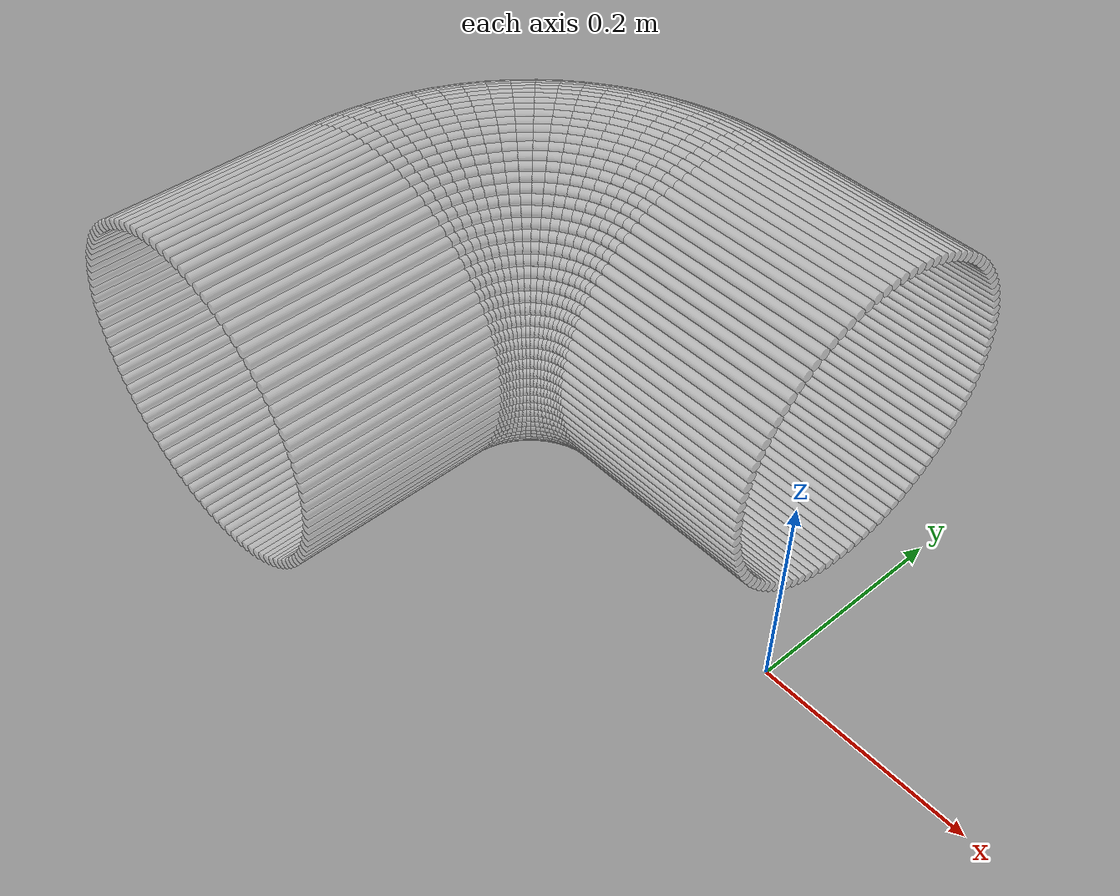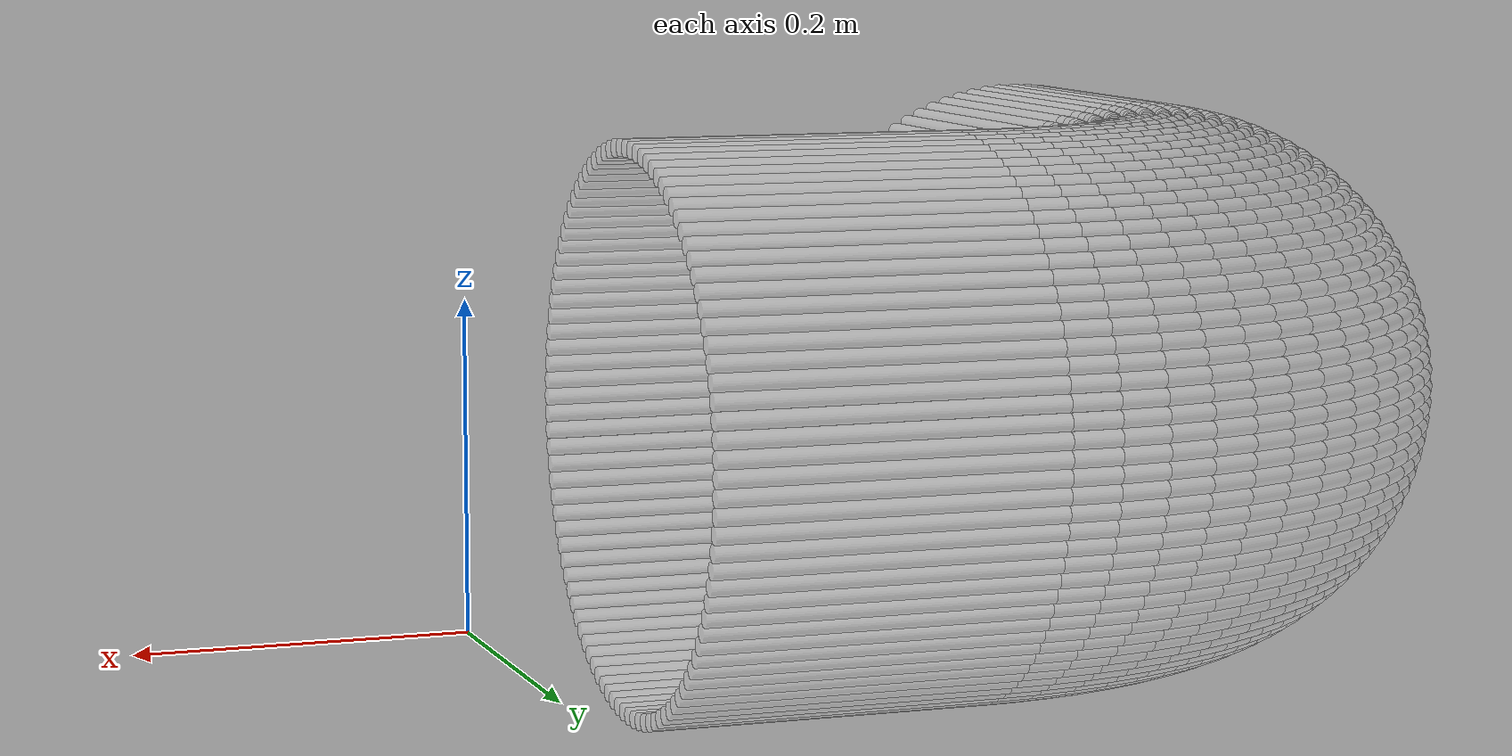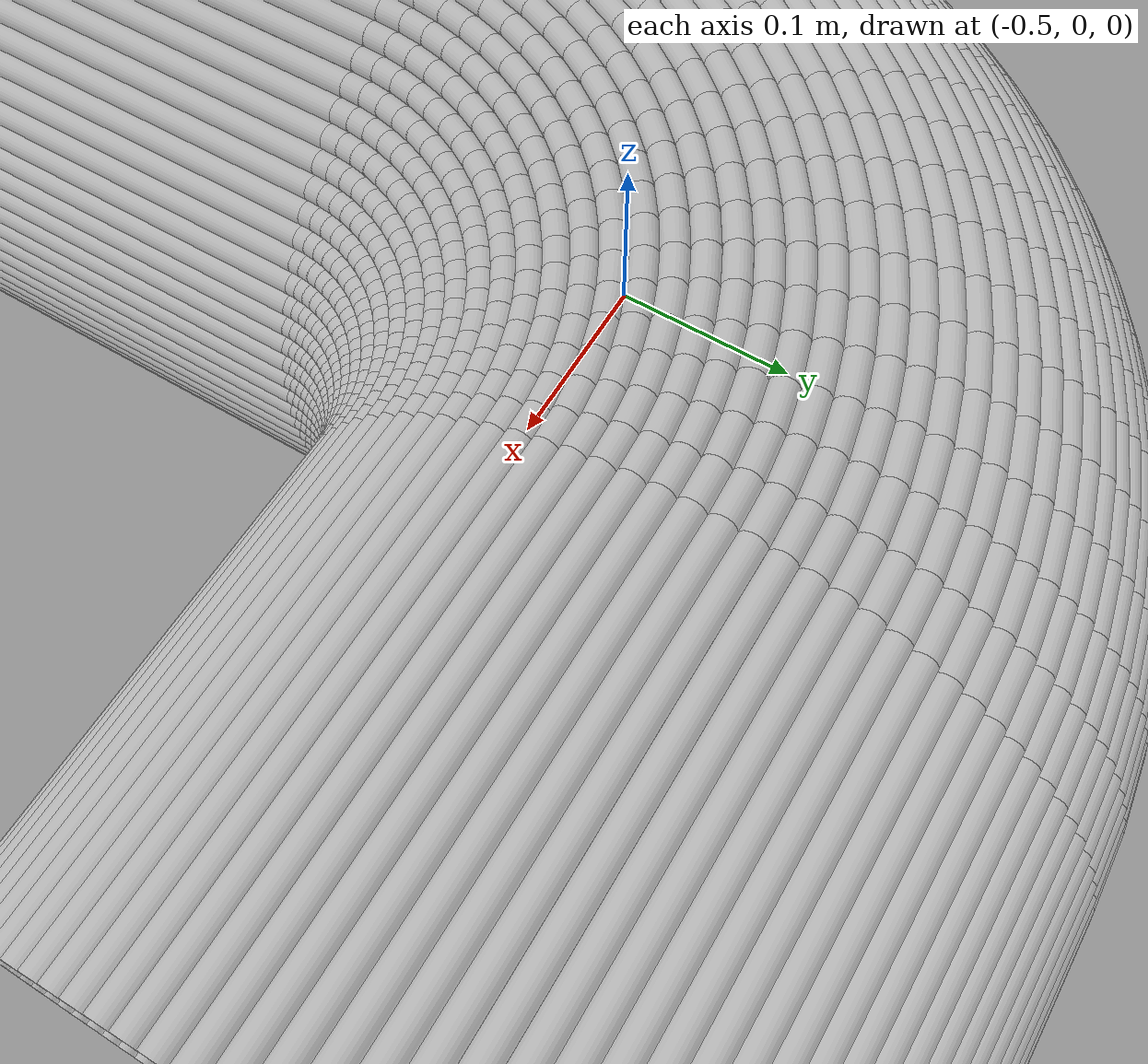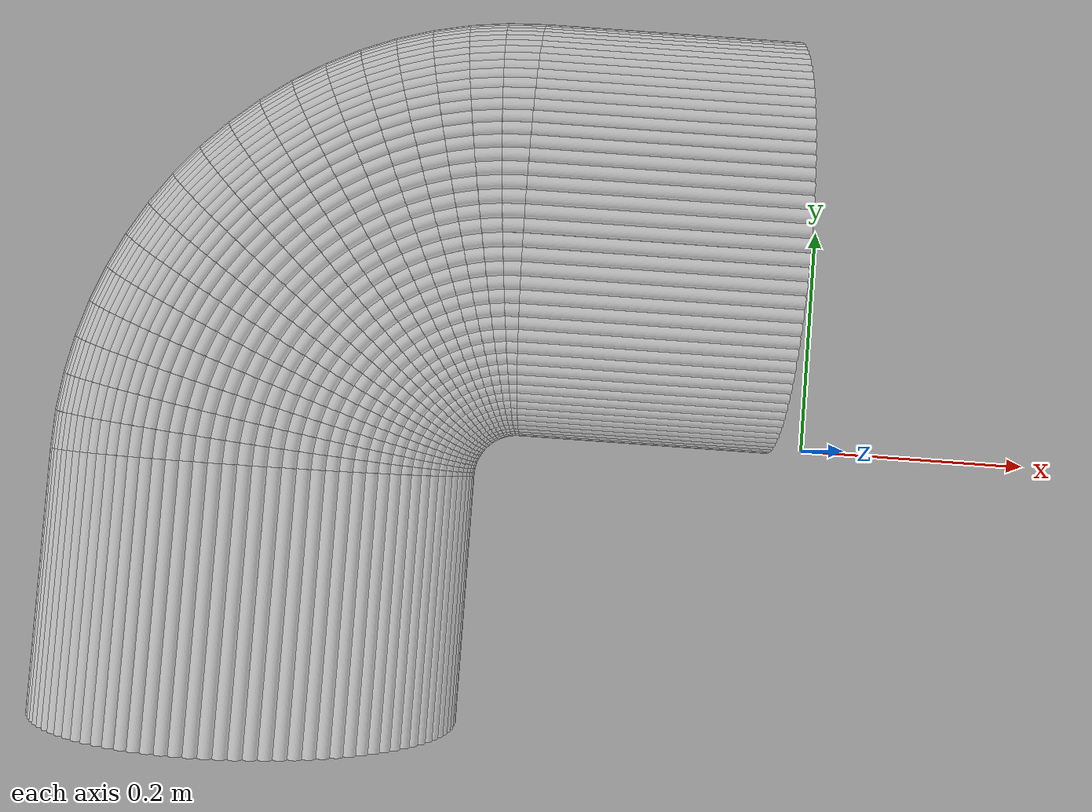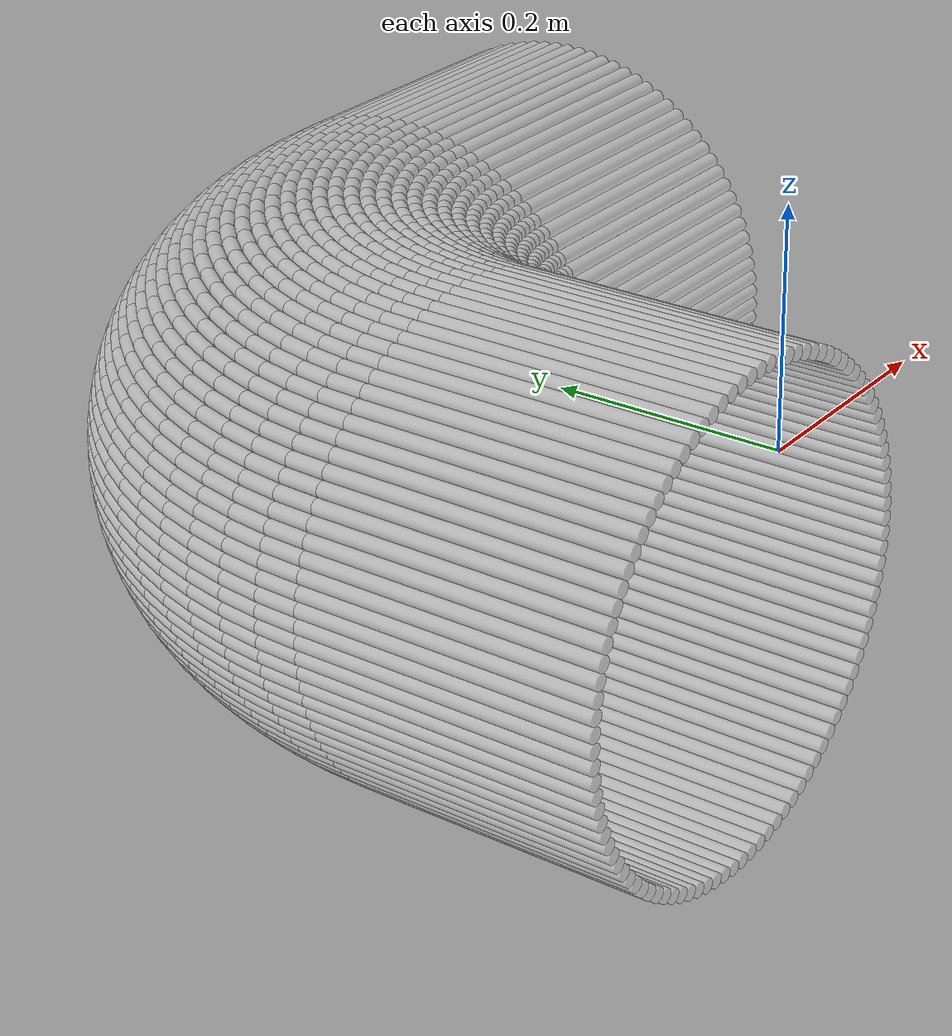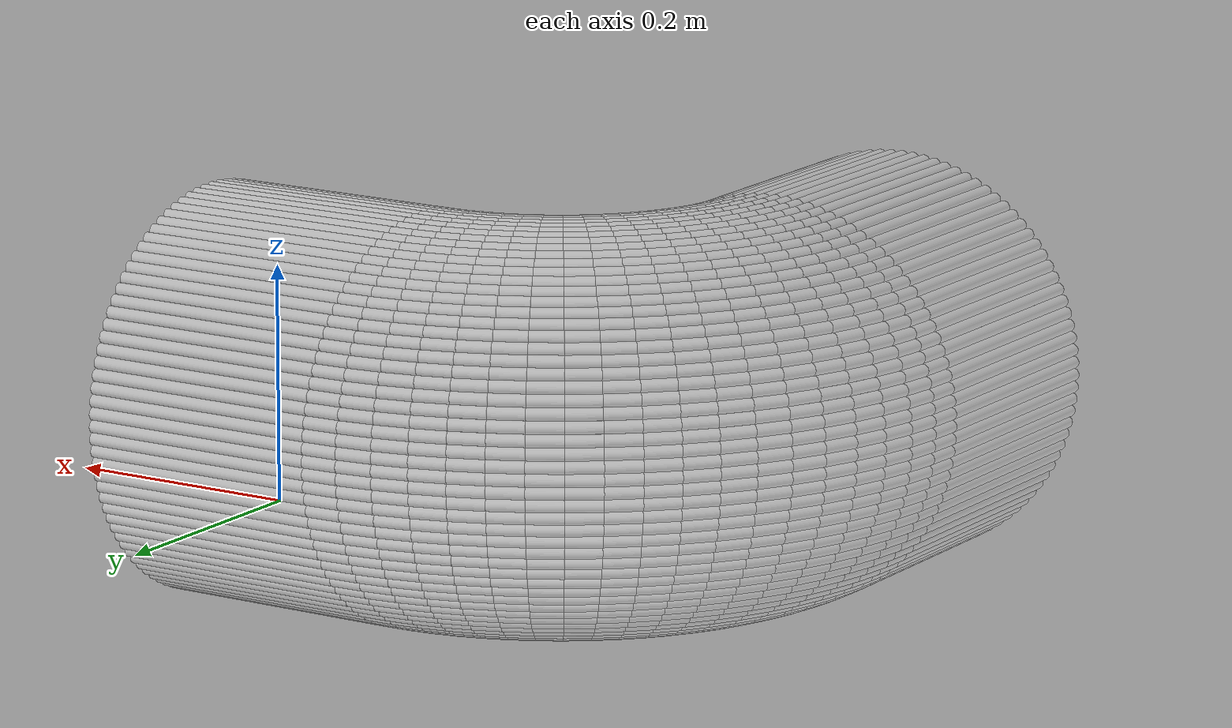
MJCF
<?xml version="1.0" encoding="utf-8"?>
<mujoco>
   <worldbody>
   <body pos="-0.25 -0.04 -0.02" euler="0 0 90">
      <geom euler=" 0 10 0 " fromto="0.36 -0.2 0.16 0.36 0 0.16" rgba="1 1 1 0.35"
            size="0.0050257"
            type="cylinder"/>
      <geom euler=" 0 20 0 " fromto="0.35968 -0.2 0.17005 0.35968 0 0.17005"
            rgba="1 1 1 0.35"
            size="0.0050257"
            type="cylinder"/>
      <geom euler=" 0 30 0 " fromto="0.35874 -0.2 0.18005 0.35874 0 0.18005"
            rgba="1 1 1 0.35"
            size="0.0050257"
            type="cylinder"/>
      <geom euler=" 0 40 0 " fromto="0.35717 -0.2 0.18998 0.35717 0 0.18998"
            rgba="1 1 1 0.35"
            size="0.0050257"
            type="cylinder"/>
      <geom euler=" 0 50 0 " fromto="0.35497 -0.2 0.19979 0.35497 0 0.19979"
            rgba="1 1 1 0.35"
            size="0.0050257"
            type="cylinder"/>
      <geom euler=" 0 60 0 " fromto="0.35217 -0.2 0.20944 0.35217 0 0.20944"
            rgba="1 1 1 0.35"
            size="0.0050257"
            type="cylinder"/>
      <geom euler=" 0 70 0 " fromto="0.34876 -0.2 0.2189 0.34876 0 0.2189"
            rgba="1 1 1 0.35"
            size="0.0050257"
            type="cylinder"/>
      <geom euler=" 0 80 0 " fromto="0.34477 -0.2 0.22812 0.34477 0 0.22812"
            rgba="1 1 1 0.35"
            size="0.0050257"
            type="cylinder"/>
      <geom euler=" 0 90 0 " fromto="0.34021 -0.2 0.23708 0.34021 0 0.23708"
            rgba="1 1 1 0.35"
            size="0.0050257"
            type="cylinder"/>
      <geom euler=" 0 100 0 " fromto="0.33509 -0.2 0.24573 0.33509 0 0.24573"
            rgba="1 1 1 0.35"
            size="0.0050257"
            type="cylinder"/>
      <geom euler=" 0 110 0 " fromto="0.32944 -0.2 0.25405 0.32944 0 0.25405"
            rgba="1 1 1 0.35"
            size="0.0050257"
            type="cylinder"/>
      <geom euler=" 0 120 0 " fromto="0.32328 -0.2 0.26199 0.32328 0 0.26199"
            rgba="1 1 1 0.35"
            size="0.0050257"
            type="cylinder"/>
      <geom euler=" 0 130 0 " fromto="0.31663 -0.2 0.26953 0.31663 0 0.26953"
            rgba="1 1 1 0.35"
            size="0.0050257"
            type="cylinder"/>
      <geom euler=" 0 140 0 " fromto="0.30953 -0.2 0.27663 0.30953 0 0.27663"
            rgba="1 1 1 0.35"
            size="0.0050257"
            type="cylinder"/>
      <geom euler=" 0 150 0 " fromto="0.30199 -0.2 0.28328 0.30199 0 0.28328"
            rgba="1 1 1 0.35"
            size="0.0050257"
            type="cylinder"/>
      <geom euler=" 0 160 0 " fromto="0.29405 -0.2 0.28944 0.29405 0 0.28944"
            rgba="1 1 1 0.35"
            size="0.0050257"
            type="cylinder"/>
      <geom euler=" 0 170 0 " fromto="0.28573 -0.2 0.29509 0.28573 0 0.29509"
            rgba="1 1 1 0.35"
            size="0.0050257"
            type="cylinder"/>
      <geom euler=" 0 180 0 " fromto="0.27708 -0.2 0.30021 0.27708 0 0.30021"
            rgba="1 1 1 0.35"
            size="0.0050257"
            type="cylinder"/>
      <geom euler=" 0 190 0 " fromto="0.26812 -0.2 0.30477 0.26812 0 0.30477"
            rgba="1 1 1 0.35"
            size="0.0050257"
            type="cylinder"/>
      <geom euler=" 0 200 0 " fromto="0.2589 -0.2 0.30876 0.2589 0 0.30876"
            rgba="1 1 1 0.35"
            size="0.0050257"
            type="cylinder"/>
      <geom euler=" 0 210 0 " fromto="0.24944 -0.2 0.31217 0.24944 0 0.31217"
            rgba="1 1 1 0.35"
            size="0.0050257"
            type="cylinder"/>
      <geom euler=" 0 220 0 " fromto="0.23979 -0.2 0.31497 0.23979 0 0.31497"
            rgba="1 1 1 0.35"
            size="0.0050257"
            type="cylinder"/>
      <geom euler=" 0 230 0 " fromto="0.22998 -0.2 0.31717 0.22998 0 0.31717"
            rgba="1 1 1 0.35"
            size="0.0050257"
            type="cylinder"/>
      <geom euler=" 0 240 0 " fromto="0.22005 -0.2 0.31874 0.22005 0 0.31874"
            rgba="1 1 1 0.35"
            size="0.0050257"
            type="cylinder"/>
      <geom euler=" 0 250 0 " fromto="0.21005 -0.2 0.31968 0.21005 0 0.31968"
            rgba="1 1 1 0.35"
            size="0.0050257"
            type="cylinder"/>
      <geom euler=" 0 260 0 " fromto="0.2 -0.2 0.32 0.2 0 0.32" rgba="1 1 1 0.35"
            size="0.0050257"
            type="cylinder"/>
      <geom euler=" 0 270 0 " fromto="0.18995 -0.2 0.31968 0.18995 0 0.31968"
            rgba="1 1 1 0.35"
            size="0.0050257"
            type="cylinder"/>
      <geom euler=" 0 280 0 " fromto="0.17995 -0.2 0.31874 0.17995 0 0.31874"
            rgba="1 1 1 0.35"
            size="0.0050257"
            type="cylinder"/>
      <geom euler=" 0 290 0 " fromto="0.17002 -0.2 0.31717 0.17002 0 0.31717"
            rgba="1 1 1 0.35"
            size="0.0050257"
            type="cylinder"/>
      <geom euler=" 0 300 0 " fromto="0.16021 -0.2 0.31497 0.16021 0 0.31497"
            rgba="1 1 1 0.35"
            size="0.0050257"
            type="cylinder"/>
      <geom euler=" 0 310 0 " fromto="0.15056 -0.2 0.31217 0.15056 0 0.31217"
            rgba="1 1 1 0.35"
            size="0.0050257"
            type="cylinder"/>
      <geom euler=" 0 320 0 " fromto="0.1411 -0.2 0.30876 0.1411 0 0.30876"
            rgba="1 1 1 0.35"
            size="0.0050257"
            type="cylinder"/>
      <geom euler=" 0 330 0 " fromto="0.13188 -0.2 0.30477 0.13188 0 0.30477"
            rgba="1 1 1 0.35"
            size="0.0050257"
            type="cylinder"/>
      <geom euler=" 0 340 0 " fromto="0.12292 -0.2 0.30021 0.12292 0 0.30021"
            rgba="1 1 1 0.35"
            size="0.0050257"
            type="cylinder"/>
      <geom euler=" 0 350 0 " fromto="0.11427 -0.2 0.29509 0.11427 0 0.29509"
            rgba="1 1 1 0.35"
            size="0.0050257"
            type="cylinder"/>
      <geom euler=" 0 360 0 " fromto="0.10595 -0.2 0.28944 0.10595 0 0.28944"
            rgba="1 1 1 0.35"
            size="0.0050257"
            type="cylinder"/>
      <geom euler=" 0 370 0 " fromto="0.098012 -0.2 0.28328 0.098012 0 0.28328"
            rgba="1 1 1 0.35"
            size="0.0050257"
            type="cylinder"/>
      <geom euler=" 0 380 0 " fromto="0.090472 -0.2 0.27663 0.090472 0 0.27663"
            rgba="1 1 1 0.35"
            size="0.0050257"
            type="cylinder"/>
      <geom euler=" 0 390 0 " fromto="0.083365 -0.2 0.26953 0.083365 0 0.26953"
            rgba="1 1 1 0.35"
            size="0.0050257"
            type="cylinder"/>
      <geom euler=" 0 400 0 " fromto="0.076718 -0.2 0.26199 0.076718 0 0.26199"
            rgba="1 1 1 0.35"
            size="0.0050257"
            type="cylinder"/>
      <geom euler=" 0 410 0 " fromto="0.070557 -0.2 0.25405 0.070557 0 0.25405"
            rgba="1 1 1 0.35"
            size="0.0050257"
            type="cylinder"/>
      <geom euler=" 0 420 0 " fromto="0.064908 -0.2 0.24573 0.064908 0 0.24573"
            rgba="1 1 1 0.35"
            size="0.0050257"
            type="cylinder"/>
      <geom euler=" 0 430 0 " fromto="0.059791 -0.2 0.23708 0.059791 0 0.23708"
            rgba="1 1 1 0.35"
            size="0.0050257"
            type="cylinder"/>
      <geom euler=" 0 440 0 " fromto="0.055228 -0.2 0.22812 0.055228 0 0.22812"
            rgba="1 1 1 0.35"
            size="0.0050257"
            type="cylinder"/>
      <geom euler=" 0 450 0 " fromto="0.051236 -0.2 0.2189 0.051236 0 0.2189"
            rgba="1 1 1 0.35"
            size="0.0050257"
            type="cylinder"/>
      <geom euler=" 0 460 0 " fromto="0.047831 -0.2 0.20944 0.047831 0 0.20944"
            rgba="1 1 1 0.35"
            size="0.0050257"
            type="cylinder"/>
      <geom euler=" 0 470 0 " fromto="0.045027 -0.2 0.19979 0.045027 0 0.19979"
            rgba="1 1 1 0.35"
            size="0.0050257"
            type="cylinder"/>
      <geom euler=" 0 480 0 " fromto="0.042834 -0.2 0.18998 0.042834 0 0.18998"
            rgba="1 1 1 0.35"
            size="0.0050257"
            type="cylinder"/>
      <geom euler=" 0 490 0 " fromto="0.041262 -0.2 0.18005 0.041262 0 0.18005"
            rgba="1 1 1 0.35"
            size="0.0050257"
            type="cylinder"/>
      <geom euler=" 0 500 0 " fromto="0.040316 -0.2 0.17005 0.040316 0 0.17005"
            rgba="1 1 1 0.35"
            size="0.0050257"
            type="cylinder"/>
      <geom euler=" 0 510 0 " fromto="0.04 -0.2 0.16 0.04 0 0.16" rgba="1 1 1 0.35"
            size="0.0050257"
            type="cylinder"/>
      <geom euler=" 0 520 0 " fromto="0.040316 -0.2 0.14995 0.040316 0 0.14995"
            rgba="1 1 1 0.35"
            size="0.0050257"
            type="cylinder"/>
      <geom euler=" 0 530 0 " fromto="0.041262 -0.2 0.13995 0.041262 0 0.13995"
            rgba="1 1 1 0.35"
            size="0.0050257"
            type="cylinder"/>
      <geom euler=" 0 540 0 " fromto="0.042834 -0.2 0.13002 0.042834 0 0.13002"
            rgba="1 1 1 0.35"
            size="0.0050257"
            type="cylinder"/>
      <geom euler=" 0 550 0 " fromto="0.045027 -0.2 0.12021 0.045027 0 0.12021"
            rgba="1 1 1 0.35"
            size="0.0050257"
            type="cylinder"/>
      <geom euler=" 0 560 0 " fromto="0.047831 -0.2 0.11056 0.047831 0 0.11056"
            rgba="1 1 1 0.35"
            size="0.0050257"
            type="cylinder"/>
      <geom euler=" 0 570 0 " fromto="0.051236 -0.2 0.1011 0.051236 0 0.1011"
            rgba="1 1 1 0.35"
            size="0.0050257"
            type="cylinder"/>
      <geom euler=" 0 580 0 " fromto="0.055228 -0.2 0.091875 0.055228 0 0.091875"
            rgba="1 1 1 0.35"
            size="0.0050257"
            type="cylinder"/>
      <geom euler=" 0 590 0 " fromto="0.059791 -0.2 0.082919 0.059791 0 0.082919"
            rgba="1 1 1 0.35"
            size="0.0050257"
            type="cylinder"/>
      <geom euler=" 0 600 0 " fromto="0.064908 -0.2 0.074268 0.064908 0 0.074268"
            rgba="1 1 1 0.35"
            size="0.0050257"
            type="cylinder"/>
      <geom euler=" 0 610 0 " fromto="0.070557 -0.2 0.065954 0.070557 0 0.065954"
            rgba="1 1 1 0.35"
            size="0.0050257"
            type="cylinder"/>
      <geom euler=" 0 620 0 " fromto="0.076718 -0.2 0.058012 0.076718 0 0.058012"
            rgba="1 1 1 0.35"
            size="0.0050257"
            type="cylinder"/>
      <geom euler=" 0 630 0 " fromto="0.083365 -0.2 0.050472 0.083365 0 0.050472"
            rgba="1 1 1 0.35"
            size="0.0050257"
            type="cylinder"/>
      <geom euler=" 0 640 0 " fromto="0.090472 -0.2 0.043365 0.090472 0 0.043365"
            rgba="1 1 1 0.35"
            size="0.0050257"
            type="cylinder"/>
      <geom euler=" 0 650 0 " fromto="0.098012 -0.2 0.036718 0.098012 0 0.036718"
            rgba="1 1 1 0.35"
            size="0.0050257"
            type="cylinder"/>
      <geom euler=" 0 660 0 " fromto="0.10595 -0.2 0.030557 0.10595 0 0.030557"
            rgba="1 1 1 0.35"
            size="0.0050257"
            type="cylinder"/>
      <geom euler=" 0 670 0 " fromto="0.11427 -0.2 0.024908 0.11427 0 0.024908"
            rgba="1 1 1 0.35"
            size="0.0050257"
            type="cylinder"/>
      <geom euler=" 0 680 0 " fromto="0.12292 -0.2 0.019791 0.12292 0 0.019791"
            rgba="1 1 1 0.35"
            size="0.0050257"
            type="cylinder"/>
      <geom euler=" 0 690 0 " fromto="0.13188 -0.2 0.015228 0.13188 0 0.015228"
            rgba="1 1 1 0.35"
            size="0.0050257"
            type="cylinder"/>
      <geom euler=" 0 700 0 " fromto="0.1411 -0.2 0.011236 0.1411 0 0.011236"
            rgba="1 1 1 0.35"
            size="0.0050257"
            type="cylinder"/>
      <geom euler=" 0 710 0 " fromto="0.15056 -0.2 0.007831 0.15056 0 0.007831"
            rgba="1 1 1 0.35"
            size="0.0050257"
            type="cylinder"/>
      <geom euler=" 0 720 0 " fromto="0.16021 -0.2 0.0050267 0.16021 0 0.0050267"
            rgba="1 1 1 0.35"
            size="0.0050257"
            type="cylinder"/>
      <geom euler=" 0 730 0 " fromto="0.17002 -0.2 0.002834 0.17002 0 0.002834"
            rgba="1 1 1 0.35"
            size="0.0050257"
            type="cylinder"/>
      <geom euler=" 0 740 0 " fromto="0.17995 -0.2 0.0012616 0.17995 0 0.0012616"
            rgba="1 1 1 0.35"
            size="0.0050257"
            type="cylinder"/>
      <geom euler=" 0 750 0 " fromto="0.18995 -0.2 0.00031572 0.18995 0 0.00031572"
            rgba="1 1 1 0.35"
            size="0.0050257"
            type="cylinder"/>
      <geom euler=" 0 760 0 " fromto="0.2 -0.2 0 0.2 0 0" rgba="1 1 1 0.35"
            size="0.0050257"
            type="cylinder"/>
      <geom euler=" 0 770 0 " fromto="0.21005 -0.2 0.00031572 0.21005 0 0.00031572"
            rgba="1 1 1 0.35"
            size="0.0050257"
            type="cylinder"/>
      <geom euler=" 0 780 0 " fromto="0.22005 -0.2 0.0012616 0.22005 0 0.0012616"
            rgba="1 1 1 0.35"
            size="0.0050257"
            type="cylinder"/>
      <geom euler=" 0 790 0 " fromto="0.22998 -0.2 0.002834 0.22998 0 0.002834"
            rgba="1 1 1 0.35"
            size="0.0050257"
            type="cylinder"/>
      <geom euler=" 0 800 0 " fromto="0.23979 -0.2 0.0050267 0.23979 0 0.0050267"
            rgba="1 1 1 0.35"
            size="0.0050257"
            type="cylinder"/>
      <geom euler=" 0 810 0 " fromto="0.24944 -0.2 0.007831 0.24944 0 0.007831"
            rgba="1 1 1 0.35"
            size="0.0050257"
            type="cylinder"/>
      <geom euler=" 0 820 0 " fromto="0.2589 -0.2 0.011236 0.2589 0 0.011236"
            rgba="1 1 1 0.35"
            size="0.0050257"
            type="cylinder"/>
      <geom euler=" 0 830 0 " fromto="0.26812 -0.2 0.015228 0.26812 0 0.015228"
            rgba="1 1 1 0.35"
            size="0.0050257"
            type="cylinder"/>
      <geom euler=" 0 840 0 " fromto="0.27708 -0.2 0.019791 0.27708 0 0.019791"
            rgba="1 1 1 0.35"
            size="0.0050257"
            type="cylinder"/>
      <geom euler=" 0 850 0 " fromto="0.28573 -0.2 0.024908 0.28573 0 0.024908"
            rgba="1 1 1 0.35"
            size="0.0050257"
            type="cylinder"/>
      <geom euler=" 0 860 0 " fromto="0.29405 -0.2 0.030557 0.29405 0 0.030557"
            rgba="1 1 1 0.35"
            size="0.0050257"
            type="cylinder"/>
      <geom euler=" 0 870 0 " fromto="0.30199 -0.2 0.036718 0.30199 0 0.036718"
            rgba="1 1 1 0.35"
            size="0.0050257"
            type="cylinder"/>
      <geom euler=" 0 880 0 " fromto="0.30953 -0.2 0.043365 0.30953 0 0.043365"
            rgba="1 1 1 0.35"
            size="0.0050257"
            type="cylinder"/>
      <geom euler=" 0 890 0 " fromto="0.31663 -0.2 0.050472 0.31663 0 0.050472"
            rgba="1 1 1 0.35"
            size="0.0050257"
            type="cylinder"/>
      <geom euler=" 0 900 0 " fromto="0.32328 -0.2 0.058012 0.32328 0 0.058012"
            rgba="1 1 1 0.35"
            size="0.0050257"
            type="cylinder"/>
      <geom euler=" 0 910 0 " fromto="0.32944 -0.2 0.065954 0.32944 0 0.065954"
            rgba="1 1 1 0.35"
            size="0.0050257"
            type="cylinder"/>
      <geom euler=" 0 920 0 " fromto="0.33509 -0.2 0.074268 0.33509 0 0.074268"
            rgba="1 1 1 0.35"
            size="0.0050257"
            type="cylinder"/>
      <geom euler=" 0 930 0 " fromto="0.34021 -0.2 0.082919 0.34021 0 0.082919"
            rgba="1 1 1 0.35"
            size="0.0050257"
            type="cylinder"/>
      <geom euler=" 0 940 0 " fromto="0.34477 -0.2 0.091875 0.34477 0 0.091875"
            rgba="1 1 1 0.35"
            size="0.0050257"
            type="cylinder"/>
      <geom euler=" 0 950 0 " fromto="0.34876 -0.2 0.1011 0.34876 0 0.1011"
            rgba="1 1 1 0.35"
            size="0.0050257"
            type="cylinder"/>
      <geom euler=" 0 960 0 " fromto="0.35217 -0.2 0.11056 0.35217 0 0.11056"
            rgba="1 1 1 0.35"
            size="0.0050257"
            type="cylinder"/>
      <geom euler=" 0 970 0 " fromto="0.35497 -0.2 0.12021 0.35497 0 0.12021"
            rgba="1 1 1 0.35"
            size="0.0050257"
            type="cylinder"/>
      <geom euler=" 0 980 0 " fromto="0.35717 -0.2 0.13002 0.35717 0 0.13002"
            rgba="1 1 1 0.35"
            size="0.0050257"
            type="cylinder"/>
      <geom euler=" 0 990 0 " fromto="0.35874 -0.2 0.13995 0.35874 0 0.13995"
            rgba="1 1 1 0.35"
            size="0.0050257"
            type="cylinder"/>
      <geom euler=" 0 1000 0 " fromto="0.35968 -0.2 0.14995 0.35968 0 0.14995"
            rgba="1 1 1 0.35"
            size="0.0050257"
            type="cylinder"/>
      <geom euler=" 0 10 0 " fromto="0.36 0 0.16 0.35877 0.029729 0.16" rgba="1 1 1 0.35"
            size="0.0050257"
            type="cylinder"/>
      <geom euler=" 0 20 0 " fromto="0.35968 0 0.17005 0.35846 0.029702 0.17005"
            rgba="1 1 1 0.35"
            size="0.0050257"
            type="cylinder"/>
      <geom euler=" 0 30 0 " fromto="0.35874 0 0.18005 0.35751 0.029624 0.18005"
            rgba="1 1 1 0.35"
            size="0.0050257"
            type="cylinder"/>
      <geom euler=" 0 40 0 " fromto="0.35717 0 0.18998 0.35595 0.029495 0.18998"
            rgba="1 1 1 0.35"
            size="0.0050257"
            type="cylinder"/>
      <geom euler=" 0 50 0 " fromto="0.35497 0 0.19979 0.35376 0.029313 0.19979"
            rgba="1 1 1 0.35"
            size="0.0050257"
            type="cylinder"/>
      <geom euler=" 0 60 0 " fromto="0.35217 0 0.20944 0.35097 0.029082 0.20944"
            rgba="1 1 1 0.35"
            size="0.0050257"
            type="cylinder"/>
      <geom euler=" 0 70 0 " fromto="0.34876 0 0.2189 0.34757 0.028801 0.2189"
            rgba="1 1 1 0.35"
            size="0.0050257"
            type="cylinder"/>
      <geom euler=" 0 80 0 " fromto="0.34477 0 0.22812 0.34359 0.028471 0.22812"
            rgba="1 1 1 0.35"
            size="0.0050257"
            type="cylinder"/>
      <geom euler=" 0 90 0 " fromto="0.34021 0 0.23708 0.33905 0.028094 0.23708"
            rgba="1 1 1 0.35"
            size="0.0050257"
            type="cylinder"/>
      <geom euler=" 0 100 0 " fromto="0.33509 0 0.24573 0.33395 0.027672 0.24573"
            rgba="1 1 1 0.35"
            size="0.0050257"
            type="cylinder"/>
      <geom euler=" 0 110 0 " fromto="0.32944 0 0.25405 0.32832 0.027205 0.25405"
            rgba="1 1 1 0.35"
            size="0.0050257"
            type="cylinder"/>
      <geom euler=" 0 120 0 " fromto="0.32328 0 0.26199 0.32218 0.026696 0.26199"
            rgba="1 1 1 0.35"
            size="0.0050257"
            type="cylinder"/>
      <geom euler=" 0 130 0 " fromto="0.31663 0 0.26953 0.31555 0.026148 0.26953"
            rgba="1 1 1 0.35"
            size="0.0050257"
            type="cylinder"/>
      <geom euler=" 0 140 0 " fromto="0.30953 0 0.27663 0.30847 0.025561 0.27663"
            rgba="1 1 1 0.35"
            size="0.0050257"
            type="cylinder"/>
      <geom euler=" 0 150 0 " fromto="0.30199 0 0.28328 0.30096 0.024938 0.28328"
            rgba="1 1 1 0.35"
            size="0.0050257"
            type="cylinder"/>
      <geom euler=" 0 160 0 " fromto="0.29405 0 0.28944 0.29304 0.024282 0.28944"
            rgba="1 1 1 0.35"
            size="0.0050257"
            type="cylinder"/>
      <geom euler=" 0 170 0 " fromto="0.28573 0 0.29509 0.28476 0.023596 0.29509"
            rgba="1 1 1 0.35"
            size="0.0050257"
            type="cylinder"/>
      <geom euler=" 0 180 0 " fromto="0.27708 0 0.30021 0.27613 0.022881 0.30021"
            rgba="1 1 1 0.35"
            size="0.0050257"
            type="cylinder"/>
      <geom euler=" 0 190 0 " fromto="0.26812 0 0.30477 0.26721 0.022142 0.30477"
            rgba="1 1 1 0.35"
            size="0.0050257"
            type="cylinder"/>
      <geom euler=" 0 200 0 " fromto="0.2589 0 0.30876 0.25802 0.02138 0.30876"
            rgba="1 1 1 0.35"
            size="0.0050257"
            type="cylinder"/>
      <geom euler=" 0 210 0 " fromto="0.24944 0 0.31217 0.24859 0.020599 0.31217"
            rgba="1 1 1 0.35"
            size="0.0050257"
            type="cylinder"/>
      <geom euler=" 0 220 0 " fromto="0.23979 0 0.31497 0.23897 0.019802 0.31497"
            rgba="1 1 1 0.35"
            size="0.0050257"
            type="cylinder"/>
      <geom euler=" 0 230 0 " fromto="0.22998 0 0.31717 0.2292 0.018992 0.31717"
            rgba="1 1 1 0.35"
            size="0.0050257"
            type="cylinder"/>
      <geom euler=" 0 240 0 " fromto="0.22005 0 0.31874 0.2193 0.018172 0.31874"
            rgba="1 1 1 0.35"
            size="0.0050257"
            type="cylinder"/>
      <geom euler=" 0 250 0 " fromto="0.21005 0 0.31968 0.20933 0.017346 0.31968"
            rgba="1 1 1 0.35"
            size="0.0050257"
            type="cylinder"/>
      <geom euler=" 0 260 0 " fromto="0.2 0 0.32 0.19932 0.016516 0.32" rgba="1 1 1 0.35"
            size="0.0050257"
            type="cylinder"/>
      <geom euler=" 0 270 0 " fromto="0.18995 0 0.31968 0.1893 0.015686 0.31968"
            rgba="1 1 1 0.35"
            size="0.0050257"
            type="cylinder"/>
      <geom euler=" 0 280 0 " fromto="0.17995 0 0.31874 0.17933 0.01486 0.31874"
            rgba="1 1 1 0.35"
            size="0.0050257"
            type="cylinder"/>
      <geom euler=" 0 290 0 " fromto="0.17002 0 0.31717 0.16944 0.01404 0.31717"
            rgba="1 1 1 0.35"
            size="0.0050257"
            type="cylinder"/>
      <geom euler=" 0 300 0 " fromto="0.16021 0 0.31497 0.15966 0.01323 0.31497"
            rgba="1 1 1 0.35"
            size="0.0050257"
            type="cylinder"/>
      <geom euler=" 0 310 0 " fromto="0.15056 0 0.31217 0.15004 0.012433 0.31217"
            rgba="1 1 1 0.35"
            size="0.0050257"
            type="cylinder"/>
      <geom euler=" 0 320 0 " fromto="0.1411 0 0.30876 0.14062 0.011652 0.30876"
            rgba="1 1 1 0.35"
            size="0.0050257"
            type="cylinder"/>
      <geom euler=" 0 330 0 " fromto="0.13188 0 0.30477 0.13142 0.01089 0.30477"
            rgba="1 1 1 0.35"
            size="0.0050257"
            type="cylinder"/>
      <geom euler=" 0 340 0 " fromto="0.12292 0 0.30021 0.1225 0.010151 0.30021"
            rgba="1 1 1 0.35"
            size="0.0050257"
            type="cylinder"/>
      <geom euler=" 0 350 0 " fromto="0.11427 0 0.29509 0.11388 0.0094362 0.29509"
            rgba="1 1 1 0.35"
            size="0.0050257"
            type="cylinder"/>
      <geom euler=" 0 360 0 " fromto="0.10595 0 0.28944 0.10559 0.0087496 0.28944"
            rgba="1 1 1 0.35"
            size="0.0050257"
            type="cylinder"/>
      <geom euler=" 0 370 0 " fromto="0.098012 0 0.28328 0.097677 0.0080938 0.28328"
            rgba="1 1 1 0.35"
            size="0.0050257"
            type="cylinder"/>
      <geom euler=" 0 380 0 " fromto="0.090472 0 0.27663 0.090163 0.0074712 0.27663"
            rgba="1 1 1 0.35"
            size="0.0050257"
            type="cylinder"/>
      <geom euler=" 0 390 0 " fromto="0.083365 0 0.26953 0.08308 0.0068842 0.26953"
            rgba="1 1 1 0.35"
            size="0.0050257"
            type="cylinder"/>
      <geom euler=" 0 400 0 " fromto="0.076718 0 0.26199 0.076456 0.0063353 0.26199"
            rgba="1 1 1 0.35"
            size="0.0050257"
            type="cylinder"/>
      <geom euler=" 0 410 0 " fromto="0.070557 0 0.25405 0.070316 0.0058266 0.25405"
            rgba="1 1 1 0.35"
            size="0.0050257"
            type="cylinder"/>
      <geom euler=" 0 420 0 " fromto="0.064908 0 0.24573 0.064686 0.00536 0.24573"
            rgba="1 1 1 0.35"
            size="0.0050257"
            type="cylinder"/>
      <geom euler=" 0 430 0 " fromto="0.059791 0 0.23708 0.059587 0.0049375 0.23708"
            rgba="1 1 1 0.35"
            size="0.0050257"
            type="cylinder"/>
      <geom euler=" 0 440 0 " fromto="0.055228 0 0.22812 0.055039 0.0045607 0.22812"
            rgba="1 1 1 0.35"
            size="0.0050257"
            type="cylinder"/>
      <geom euler=" 0 450 0 " fromto="0.051236 0 0.2189 0.051061 0.004231 0.2189"
            rgba="1 1 1 0.35"
            size="0.0050257"
            type="cylinder"/>
      <geom euler=" 0 460 0 " fromto="0.047831 0 0.20944 0.047668 0.0039498 0.20944"
            rgba="1 1 1 0.35"
            size="0.0050257"
            type="cylinder"/>
      <geom euler=" 0 470 0 " fromto="0.045027 0 0.19979 0.044873 0.0037183 0.19979"
            rgba="1 1 1 0.35"
            size="0.0050257"
            type="cylinder"/>
      <geom euler=" 0 480 0 " fromto="0.042834 0 0.18998 0.042688 0.0035372 0.18998"
            rgba="1 1 1 0.35"
            size="0.0050257"
            type="cylinder"/>
      <geom euler=" 0 490 0 " fromto="0.041262 0 0.18005 0.041121 0.0034074 0.18005"
            rgba="1 1 1 0.35"
            size="0.0050257"
            type="cylinder"/>
      <geom euler=" 0 500 0 " fromto="0.040316 0 0.17005 0.040178 0.0033292 0.17005"
            rgba="1 1 1 0.35"
            size="0.0050257"
            type="cylinder"/>
      <geom euler=" 0 510 0 " fromto="0.04 0 0.16 0.039863 0.0033032 0.16"
            rgba="1 1 1 0.35"
            size="0.0050257"
            type="cylinder"/>
      <geom euler=" 0 520 0 " fromto="0.040316 0 0.14995 0.040178 0.0033292 0.14995"
            rgba="1 1 1 0.35"
            size="0.0050257"
            type="cylinder"/>
      <geom euler=" 0 530 0 " fromto="0.041262 0 0.13995 0.041121 0.0034074 0.13995"
            rgba="1 1 1 0.35"
            size="0.0050257"
            type="cylinder"/>
      <geom euler=" 0 540 0 " fromto="0.042834 0 0.13002 0.042688 0.0035372 0.13002"
            rgba="1 1 1 0.35"
            size="0.0050257"
            type="cylinder"/>
      <geom euler=" 0 550 0 " fromto="0.045027 0 0.12021 0.044873 0.0037183 0.12021"
            rgba="1 1 1 0.35"
            size="0.0050257"
            type="cylinder"/>
      <geom euler=" 0 560 0 " fromto="0.047831 0 0.11056 0.047668 0.0039498 0.11056"
            rgba="1 1 1 0.35"
            size="0.0050257"
            type="cylinder"/>
      <geom euler=" 0 570 0 " fromto="0.051236 0 0.1011 0.051061 0.004231 0.1011"
            rgba="1 1 1 0.35"
            size="0.0050257"
            type="cylinder"/>
      <geom euler=" 0 580 0 " fromto="0.055228 0 0.091875 0.055039 0.0045607 0.091875"
            rgba="1 1 1 0.35"
            size="0.0050257"
            type="cylinder"/>
      <geom euler=" 0 590 0 " fromto="0.059791 0 0.082919 0.059587 0.0049375 0.082919"
            rgba="1 1 1 0.35"
            size="0.0050257"
            type="cylinder"/>
      <geom euler=" 0 600 0 " fromto="0.064908 0 0.074268 0.064686 0.00536 0.074268"
            rgba="1 1 1 0.35"
            size="0.0050257"
            type="cylinder"/>
      <geom euler=" 0 610 0 " fromto="0.070557 0 0.065954 0.070316 0.0058266 0.065954"
            rgba="1 1 1 0.35"
            size="0.0050257"
            type="cylinder"/>
      <geom euler=" 0 620 0 " fromto="0.076718 0 0.058012 0.076456 0.0063353 0.058012"
            rgba="1 1 1 0.35"
            size="0.0050257"
            type="cylinder"/>
      <geom euler=" 0 630 0 " fromto="0.083365 0 0.050472 0.08308 0.0068842 0.050472"
            rgba="1 1 1 0.35"
            size="0.0050257"
            type="cylinder"/>
      <geom euler=" 0 640 0 " fromto="0.090472 0 0.043365 0.090163 0.0074712 0.043365"
            rgba="1 1 1 0.35"
            size="0.0050257"
            type="cylinder"/>
      <geom euler=" 0 650 0 " fromto="0.098012 0 0.036718 0.097677 0.0080938 0.036718"
            rgba="1 1 1 0.35"
            size="0.0050257"
            type="cylinder"/>
      <geom euler=" 0 660 0 " fromto="0.10595 0 0.030557 0.10559 0.0087496 0.030557"
            rgba="1 1 1 0.35"
            size="0.0050257"
            type="cylinder"/>
      <geom euler=" 0 670 0 " fromto="0.11427 0 0.024908 0.11388 0.0094362 0.024908"
            rgba="1 1 1 0.35"
            size="0.0050257"
            type="cylinder"/>
      <geom euler=" 0 680 0 " fromto="0.12292 0 0.019791 0.1225 0.010151 0.019791"
            rgba="1 1 1 0.35"
            size="0.0050257"
            type="cylinder"/>
      <geom euler=" 0 690 0 " fromto="0.13188 0 0.015228 0.13142 0.01089 0.015228"
            rgba="1 1 1 0.35"
            size="0.0050257"
            type="cylinder"/>
      <geom euler=" 0 700 0 " fromto="0.1411 0 0.011236 0.14062 0.011652 0.011236"
            rgba="1 1 1 0.35"
            size="0.0050257"
            type="cylinder"/>
      <geom euler=" 0 710 0 " fromto="0.15056 0 0.007831 0.15004 0.012433 0.007831"
            rgba="1 1 1 0.35"
            size="0.0050257"
            type="cylinder"/>
      <geom euler=" 0 720 0 " fromto="0.16021 0 0.0050267 0.15966 0.01323 0.0050267"
            rgba="1 1 1 0.35"
            size="0.0050257"
            type="cylinder"/>
      <geom euler=" 0 730 0 " fromto="0.17002 0 0.002834 0.16944 0.01404 0.002834"
            rgba="1 1 1 0.35"
            size="0.0050257"
            type="cylinder"/>
      <geom euler=" 0 740 0 " fromto="0.17995 0 0.0012616 0.17933 0.01486 0.0012616"
            rgba="1 1 1 0.35"
            size="0.0050257"
            type="cylinder"/>
      <geom euler=" 0 750 0 " fromto="0.18995 0 0.00031572 0.1893 0.015686 0.00031572"
            rgba="1 1 1 0.35"
            size="0.0050257"
            type="cylinder"/>
      <geom euler=" 0 760 0 " fromto="0.2 0 0 0.19932 0.016516 0" rgba="1 1 1 0.35"
            size="0.0050257"
            type="cylinder"/>
      <geom euler=" 0 770 0 " fromto="0.21005 0 0.00031572 0.20933 0.017346 0.00031572"
            rgba="1 1 1 0.35"
            size="0.0050257"
            type="cylinder"/>
      <geom euler=" 0 780 0 " fromto="0.22005 0 0.0012616 0.2193 0.018172 0.0012616"
            rgba="1 1 1 0.35"
            size="0.0050257"
            type="cylinder"/>
      <geom euler=" 0 790 0 " fromto="0.22998 0 0.002834 0.2292 0.018992 0.002834"
            rgba="1 1 1 0.35"
            size="0.0050257"
            type="cylinder"/>
      <geom euler=" 0 800 0 " fromto="0.23979 0 0.0050267 0.23897 0.019802 0.0050267"
            rgba="1 1 1 0.35"
            size="0.0050257"
            type="cylinder"/>
      <geom euler=" 0 810 0 " fromto="0.24944 0 0.007831 0.24859 0.020599 0.007831"
            rgba="1 1 1 0.35"
            size="0.0050257"
            type="cylinder"/>
      <geom euler=" 0 820 0 " fromto="0.2589 0 0.011236 0.25802 0.02138 0.011236"
            rgba="1 1 1 0.35"
            size="0.0050257"
            type="cylinder"/>
      <geom euler=" 0 830 0 " fromto="0.26812 0 0.015228 0.26721 0.022142 0.015228"
            rgba="1 1 1 0.35"
            size="0.0050257"
            type="cylinder"/>
      <geom euler=" 0 840 0 " fromto="0.27708 0 0.019791 0.27613 0.022881 0.019791"
            rgba="1 1 1 0.35"
            size="0.0050257"
            type="cylinder"/>
      <geom euler=" 0 850 0 " fromto="0.28573 0 0.024908 0.28476 0.023596 0.024908"
            rgba="1 1 1 0.35"
            size="0.0050257"
            type="cylinder"/>
      <geom euler=" 0 860 0 " fromto="0.29405 0 0.030557 0.29304 0.024282 0.030557"
            rgba="1 1 1 0.35"
            size="0.0050257"
            type="cylinder"/>
      <geom euler=" 0 870 0 " fromto="0.30199 0 0.036718 0.30096 0.024938 0.036718"
            rgba="1 1 1 0.35"
            size="0.0050257"
            type="cylinder"/>
      <geom euler=" 0 880 0 " fromto="0.30953 0 0.043365 0.30847 0.025561 0.043365"
            rgba="1 1 1 0.35"
            size="0.0050257"
            type="cylinder"/>
      <geom euler=" 0 890 0 " fromto="0.31663 0 0.050472 0.31555 0.026148 0.050472"
            rgba="1 1 1 0.35"
            size="0.0050257"
            type="cylinder"/>
      <geom euler=" 0 900 0 " fromto="0.32328 0 0.058012 0.32218 0.026696 0.058012"
            rgba="1 1 1 0.35"
            size="0.0050257"
            type="cylinder"/>
      <geom euler=" 0 910 0 " fromto="0.32944 0 0.065954 0.32832 0.027205 0.065954"
            rgba="1 1 1 0.35"
            size="0.0050257"
            type="cylinder"/>
      <geom euler=" 0 920 0 " fromto="0.33509 0 0.074268 0.33395 0.027672 0.074268"
            rgba="1 1 1 0.35"
            size="0.0050257"
            type="cylinder"/>
      <geom euler=" 0 930 0 " fromto="0.34021 0 0.082919 0.33905 0.028094 0.082919"
            rgba="1 1 1 0.35"
            size="0.0050257"
            type="cylinder"/>
      <geom euler=" 0 940 0 " fromto="0.34477 0 0.091875 0.34359 0.028471 0.091875"
            rgba="1 1 1 0.35"
            size="0.0050257"
            type="cylinder"/>
      <geom euler=" 0 950 0 " fromto="0.34876 0 0.1011 0.34757 0.028801 0.1011"
            rgba="1 1 1 0.35"
            size="0.0050257"
            type="cylinder"/>
      <geom euler=" 0 960 0 " fromto="0.35217 0 0.11056 0.35097 0.029082 0.11056"
            rgba="1 1 1 0.35"
            size="0.0050257"
            type="cylinder"/>
      <geom euler=" 0 970 0 " fromto="0.35497 0 0.12021 0.35376 0.029313 0.12021"
            rgba="1 1 1 0.35"
            size="0.0050257"
            type="cylinder"/>
      <geom euler=" 0 980 0 " fromto="0.35717 0 0.13002 0.35595 0.029495 0.13002"
            rgba="1 1 1 0.35"
            size="0.0050257"
            type="cylinder"/>
      <geom euler=" 0 990 0 " fromto="0.35874 0 0.13995 0.35751 0.029624 0.13995"
            rgba="1 1 1 0.35"
            size="0.0050257"
            type="cylinder"/>
      <geom euler=" 0 1000 0 " fromto="0.35968 0 0.14995 0.35846 0.029702 0.14995"
            rgba="1 1 1 0.35"
            size="0.0050257"
            type="cylinder"/>
      <geom euler=" 0 10 0 " fromto="0.35877 0.029729 0.16 0.35509 0.059254 0.16"
            rgba="1 1 1 0.35"
            size="0.0050257"
            type="cylinder"/>
      <geom euler=" 0 20 0 " fromto="0.35846 0.029702 0.17005 0.35478 0.059202 0.17005"
            rgba="1 1 1 0.35"
            size="0.0050257"
            type="cylinder"/>
      <geom euler=" 0 30 0 " fromto="0.35751 0.029624 0.18005 0.35385 0.059046 0.18005"
            rgba="1 1 1 0.35"
            size="0.0050257"
            type="cylinder"/>
      <geom euler=" 0 40 0 " fromto="0.35595 0.029495 0.18998 0.35229 0.058788 0.18998"
            rgba="1 1 1 0.35"
            size="0.0050257"
            type="cylinder"/>
      <geom euler=" 0 50 0 " fromto="0.35376 0.029313 0.19979 0.35013 0.058427 0.19979"
            rgba="1 1 1 0.35"
            size="0.0050257"
            type="cylinder"/>
      <geom euler=" 0 60 0 " fromto="0.35097 0.029082 0.20944 0.34737 0.057965 0.20944"
            rgba="1 1 1 0.35"
            size="0.0050257"
            type="cylinder"/>
      <geom euler=" 0 70 0 " fromto="0.34757 0.028801 0.2189 0.34401 0.057405 0.2189"
            rgba="1 1 1 0.35"
            size="0.0050257"
            type="cylinder"/>
      <geom euler=" 0 80 0 " fromto="0.34359 0.028471 0.22812 0.34007 0.056748 0.22812"
            rgba="1 1 1 0.35"
            size="0.0050257"
            type="cylinder"/>
      <geom euler=" 0 90 0 " fromto="0.33905 0.028094 0.23708 0.33557 0.055997 0.23708"
            rgba="1 1 1 0.35"
            size="0.0050257"
            type="cylinder"/>
      <geom euler=" 0 100 0 " fromto="0.33395 0.027672 0.24573 0.33052 0.055154 0.24573"
            rgba="1 1 1 0.35"
            size="0.0050257"
            type="cylinder"/>
      <geom euler=" 0 110 0 " fromto="0.32832 0.027205 0.25405 0.32495 0.054224 0.25405"
            rgba="1 1 1 0.35"
            size="0.0050257"
            type="cylinder"/>
      <geom euler=" 0 120 0 " fromto="0.32218 0.026696 0.26199 0.31887 0.05321 0.26199"
            rgba="1 1 1 0.35"
            size="0.0050257"
            type="cylinder"/>
      <geom euler=" 0 130 0 " fromto="0.31555 0.026148 0.26953 0.31232 0.052116 0.26953"
            rgba="1 1 1 0.35"
            size="0.0050257"
            type="cylinder"/>
      <geom euler=" 0 140 0 " fromto="0.30847 0.025561 0.27663 0.30531 0.050947 0.27663"
            rgba="1 1 1 0.35"
            size="0.0050257"
            type="cylinder"/>
      <geom euler=" 0 150 0 " fromto="0.30096 0.024938 0.28328 0.29787 0.049706 0.28328"
            rgba="1 1 1 0.35"
            size="0.0050257"
            type="cylinder"/>
      <geom euler=" 0 160 0 " fromto="0.29304 0.024282 0.28944 0.29004 0.048398 0.28944"
            rgba="1 1 1 0.35"
            size="0.0050257"
            type="cylinder"/>
      <geom euler=" 0 170 0 " fromto="0.28476 0.023596 0.29509 0.28184 0.04703 0.29509"
            rgba="1 1 1 0.35"
            size="0.0050257"
            type="cylinder"/>
      <geom euler=" 0 180 0 " fromto="0.27613 0.022881 0.30021 0.2733 0.045606 0.30021"
            rgba="1 1 1 0.35"
            size="0.0050257"
            type="cylinder"/>
      <geom euler=" 0 190 0 " fromto="0.26721 0.022142 0.30477 0.26447 0.044132 0.30477"
            rgba="1 1 1 0.35"
            size="0.0050257"
            type="cylinder"/>
      <geom euler=" 0 200 0 " fromto="0.25802 0.02138 0.30876 0.25537 0.042614 0.30876"
            rgba="1 1 1 0.35"
            size="0.0050257"
            type="cylinder"/>
      <geom euler=" 0 210 0 " fromto="0.24859 0.020599 0.31217 0.24604 0.041057 0.31217"
            rgba="1 1 1 0.35"
            size="0.0050257"
            type="cylinder"/>
      <geom euler=" 0 220 0 " fromto="0.23897 0.019802 0.31497 0.23652 0.039468 0.31497"
            rgba="1 1 1 0.35"
            size="0.0050257"
            type="cylinder"/>
      <geom euler=" 0 230 0 " fromto="0.2292 0.018992 0.31717 0.22684 0.037854 0.31717"
            rgba="1 1 1 0.35"
            size="0.0050257"
            type="cylinder"/>
      <geom euler=" 0 240 0 " fromto="0.2193 0.018172 0.31874 0.21705 0.03622 0.31874"
            rgba="1 1 1 0.35"
            size="0.0050257"
            type="cylinder"/>
      <geom euler=" 0 250 0 " fromto="0.20933 0.017346 0.31968 0.20718 0.034573 0.31968"
            rgba="1 1 1 0.35"
            size="0.0050257"
            type="cylinder"/>
      <geom euler=" 0 260 0 " fromto="0.19932 0.016516 0.32 0.19727 0.032919 0.32"
            rgba="1 1 1 0.35"
            size="0.0050257"
            type="cylinder"/>
      <geom euler=" 0 270 0 " fromto="0.1893 0.015686 0.31968 0.18736 0.031265 0.31968"
            rgba="1 1 1 0.35"
            size="0.0050257"
            type="cylinder"/>
      <geom euler=" 0 280 0 " fromto="0.17933 0.01486 0.31874 0.17749 0.029618 0.31874"
            rgba="1 1 1 0.35"
            size="0.0050257"
            type="cylinder"/>
      <geom euler=" 0 290 0 " fromto="0.16944 0.01404 0.31717 0.1677 0.027984 0.31717"
            rgba="1 1 1 0.35"
            size="0.0050257"
            type="cylinder"/>
      <geom euler=" 0 300 0 " fromto="0.15966 0.01323 0.31497 0.15802 0.02637 0.31497"
            rgba="1 1 1 0.35"
            size="0.0050257"
            type="cylinder"/>
      <geom euler=" 0 310 0 " fromto="0.15004 0.012433 0.31217 0.1485 0.024781 0.31217"
            rgba="1 1 1 0.35"
            size="0.0050257"
            type="cylinder"/>
      <geom euler=" 0 320 0 " fromto="0.14062 0.011652 0.30876 0.13918 0.023224 0.30876"
            rgba="1 1 1 0.35"
            size="0.0050257"
            type="cylinder"/>
      <geom euler=" 0 330 0 " fromto="0.13142 0.01089 0.30477 0.13008 0.021706 0.30477"
            rgba="1 1 1 0.35"
            size="0.0050257"
            type="cylinder"/>
      <geom euler=" 0 340 0 " fromto="0.1225 0.010151 0.30021 0.12124 0.020232 0.30021"
            rgba="1 1 1 0.35"
            size="0.0050257"
            type="cylinder"/>
      <geom euler=" 0 350 0 " fromto="0.11388 0.0094362 0.29509 0.11271 0.018808 0.29509"
            rgba="1 1 1 0.35"
            size="0.0050257"
            type="cylinder"/>
      <geom euler=" 0 360 0 " fromto="0.10559 0.0087496 0.28944 0.10451 0.01744 0.28944"
            rgba="1 1 1 0.35"
            size="0.0050257"
            type="cylinder"/>
      <geom euler=" 0 370 0 " fromto="0.097677 0.0080938 0.28328 0.096675 0.016132 0.28328"
            rgba="1 1 1 0.35"
            size="0.0050257"
            type="cylinder"/>
      <geom euler=" 0 380 0 " fromto="0.090163 0.0074712 0.27663 0.089239 0.014891 0.27663"
            rgba="1 1 1 0.35"
            size="0.0050257"
            type="cylinder"/>
      <geom euler=" 0 390 0 " fromto="0.08308 0.0068842 0.26953 0.082228 0.013721 0.26953"
            rgba="1 1 1 0.35"
            size="0.0050257"
            type="cylinder"/>
      <geom euler=" 0 400 0 " fromto="0.076456 0.0063353 0.26199 0.075672 0.012627 0.26199"
            rgba="1 1 1 0.35"
            size="0.0050257"
            type="cylinder"/>
      <geom euler=" 0 410 0 " fromto="0.070316 0.0058266 0.25405 0.069595 0.011613 0.25405"
            rgba="1 1 1 0.35"
            size="0.0050257"
            type="cylinder"/>
      <geom euler=" 0 420 0 " fromto="0.064686 0.00536 0.24573 0.064022 0.010683 0.24573"
            rgba="1 1 1 0.35"
            size="0.0050257"
            type="cylinder"/>
      <geom euler=" 0 430 0 "
            fromto="0.059587 0.0049375 0.23708 0.058975 0.0098413 0.23708"
            rgba="1 1 1 0.35"
            size="0.0050257"
            type="cylinder"/>
      <geom euler=" 0 440 0 "
            fromto="0.055039 0.0045607 0.22812 0.054474 0.0090902 0.22812"
            rgba="1 1 1 0.35"
            size="0.0050257"
            type="cylinder"/>
      <geom euler=" 0 450 0 " fromto="0.051061 0.004231 0.2189 0.050537 0.0084331 0.2189"
            rgba="1 1 1 0.35"
            size="0.0050257"
            type="cylinder"/>
      <geom euler=" 0 460 0 "
            fromto="0.047668 0.0039498 0.20944 0.047179 0.0078727 0.20944"
            rgba="1 1 1 0.35"
            size="0.0050257"
            type="cylinder"/>
      <geom euler=" 0 470 0 "
            fromto="0.044873 0.0037183 0.19979 0.044413 0.0074112 0.19979"
            rgba="1 1 1 0.35"
            size="0.0050257"
            type="cylinder"/>
      <geom euler=" 0 480 0 " fromto="0.042688 0.0035372 0.18998 0.04225 0.0070503 0.18998"
            rgba="1 1 1 0.35"
            size="0.0050257"
            type="cylinder"/>
      <geom euler=" 0 490 0 "
            fromto="0.041121 0.0034074 0.18005 0.040699 0.0067914 0.18005"
            rgba="1 1 1 0.35"
            size="0.0050257"
            type="cylinder"/>
      <geom euler=" 0 500 0 "
            fromto="0.040178 0.0033292 0.17005 0.039766 0.0066357 0.17005"
            rgba="1 1 1 0.35"
            size="0.0050257"
            type="cylinder"/>
      <geom euler=" 0 510 0 " fromto="0.039863 0.0033032 0.16 0.039454 0.0065838 0.16"
            rgba="1 1 1 0.35"
            size="0.0050257"
            type="cylinder"/>
      <geom euler=" 0 520 0 "
            fromto="0.040178 0.0033292 0.14995 0.039766 0.0066357 0.14995"
            rgba="1 1 1 0.35"
            size="0.0050257"
            type="cylinder"/>
      <geom euler=" 0 530 0 "
            fromto="0.041121 0.0034074 0.13995 0.040699 0.0067914 0.13995"
            rgba="1 1 1 0.35"
            size="0.0050257"
            type="cylinder"/>
      <geom euler=" 0 540 0 " fromto="0.042688 0.0035372 0.13002 0.04225 0.0070503 0.13002"
            rgba="1 1 1 0.35"
            size="0.0050257"
            type="cylinder"/>
      <geom euler=" 0 550 0 "
            fromto="0.044873 0.0037183 0.12021 0.044413 0.0074112 0.12021"
            rgba="1 1 1 0.35"
            size="0.0050257"
            type="cylinder"/>
      <geom euler=" 0 560 0 "
            fromto="0.047668 0.0039498 0.11056 0.047179 0.0078727 0.11056"
            rgba="1 1 1 0.35"
            size="0.0050257"
            type="cylinder"/>
      <geom euler=" 0 570 0 " fromto="0.051061 0.004231 0.1011 0.050537 0.0084331 0.1011"
            rgba="1 1 1 0.35"
            size="0.0050257"
            type="cylinder"/>
      <geom euler=" 0 580 0 "
            fromto="0.055039 0.0045607 0.091875 0.054474 0.0090902 0.091875"
            rgba="1 1 1 0.35"
            size="0.0050257"
            type="cylinder"/>
      <geom euler=" 0 590 0 "
            fromto="0.059587 0.0049375 0.082919 0.058975 0.0098413 0.082919"
            rgba="1 1 1 0.35"
            size="0.0050257"
            type="cylinder"/>
      <geom euler=" 0 600 0 " fromto="0.064686 0.00536 0.074268 0.064022 0.010683 0.074268"
            rgba="1 1 1 0.35"
            size="0.0050257"
            type="cylinder"/>
      <geom euler=" 0 610 0 "
            fromto="0.070316 0.0058266 0.065954 0.069595 0.011613 0.065954"
            rgba="1 1 1 0.35"
            size="0.0050257"
            type="cylinder"/>
      <geom euler=" 0 620 0 "
            fromto="0.076456 0.0063353 0.058012 0.075672 0.012627 0.058012"
            rgba="1 1 1 0.35"
            size="0.0050257"
            type="cylinder"/>
      <geom euler=" 0 630 0 "
            fromto="0.08308 0.0068842 0.050472 0.082228 0.013721 0.050472"
            rgba="1 1 1 0.35"
            size="0.0050257"
            type="cylinder"/>
      <geom euler=" 0 640 0 "
            fromto="0.090163 0.0074712 0.043365 0.089239 0.014891 0.043365"
            rgba="1 1 1 0.35"
            size="0.0050257"
            type="cylinder"/>
      <geom euler=" 0 650 0 "
            fromto="0.097677 0.0080938 0.036718 0.096675 0.016132 0.036718"
            rgba="1 1 1 0.35"
            size="0.0050257"
            type="cylinder"/>
      <geom euler=" 0 660 0 " fromto="0.10559 0.0087496 0.030557 0.10451 0.01744 0.030557"
            rgba="1 1 1 0.35"
            size="0.0050257"
            type="cylinder"/>
      <geom euler=" 0 670 0 " fromto="0.11388 0.0094362 0.024908 0.11271 0.018808 0.024908"
            rgba="1 1 1 0.35"
            size="0.0050257"
            type="cylinder"/>
      <geom euler=" 0 680 0 " fromto="0.1225 0.010151 0.019791 0.12124 0.020232 0.019791"
            rgba="1 1 1 0.35"
            size="0.0050257"
            type="cylinder"/>
      <geom euler=" 0 690 0 " fromto="0.13142 0.01089 0.015228 0.13008 0.021706 0.015228"
            rgba="1 1 1 0.35"
            size="0.0050257"
            type="cylinder"/>
      <geom euler=" 0 700 0 " fromto="0.14062 0.011652 0.011236 0.13918 0.023224 0.011236"
            rgba="1 1 1 0.35"
            size="0.0050257"
            type="cylinder"/>
      <geom euler=" 0 710 0 " fromto="0.15004 0.012433 0.007831 0.1485 0.024781 0.007831"
            rgba="1 1 1 0.35"
            size="0.0050257"
            type="cylinder"/>
      <geom euler=" 0 720 0 " fromto="0.15966 0.01323 0.0050267 0.15802 0.02637 0.0050267"
            rgba="1 1 1 0.35"
            size="0.0050257"
            type="cylinder"/>
      <geom euler=" 0 730 0 " fromto="0.16944 0.01404 0.002834 0.1677 0.027984 0.002834"
            rgba="1 1 1 0.35"
            size="0.0050257"
            type="cylinder"/>
      <geom euler=" 0 740 0 " fromto="0.17933 0.01486 0.0012616 0.17749 0.029618 0.0012616"
            rgba="1 1 1 0.35"
            size="0.0050257"
            type="cylinder"/>
      <geom euler=" 0 750 0 "
            fromto="0.1893 0.015686 0.00031572 0.18736 0.031265 0.00031572"
            rgba="1 1 1 0.35"
            size="0.0050257"
            type="cylinder"/>
      <geom euler=" 0 760 0 " fromto="0.19932 0.016516 0 0.19727 0.032919 0"
            rgba="1 1 1 0.35"
            size="0.0050257"
            type="cylinder"/>
      <geom euler=" 0 770 0 "
            fromto="0.20933 0.017346 0.00031572 0.20718 0.034573 0.00031572"
            rgba="1 1 1 0.35"
            size="0.0050257"
            type="cylinder"/>
      <geom euler=" 0 780 0 " fromto="0.2193 0.018172 0.0012616 0.21705 0.03622 0.0012616"
            rgba="1 1 1 0.35"
            size="0.0050257"
            type="cylinder"/>
      <geom euler=" 0 790 0 " fromto="0.2292 0.018992 0.002834 0.22684 0.037854 0.002834"
            rgba="1 1 1 0.35"
            size="0.0050257"
            type="cylinder"/>
      <geom euler=" 0 800 0 "
            fromto="0.23897 0.019802 0.0050267 0.23652 0.039468 0.0050267"
            rgba="1 1 1 0.35"
            size="0.0050257"
            type="cylinder"/>
      <geom euler=" 0 810 0 " fromto="0.24859 0.020599 0.007831 0.24604 0.041057 0.007831"
            rgba="1 1 1 0.35"
            size="0.0050257"
            type="cylinder"/>
      <geom euler=" 0 820 0 " fromto="0.25802 0.02138 0.011236 0.25537 0.042614 0.011236"
            rgba="1 1 1 0.35"
            size="0.0050257"
            type="cylinder"/>
      <geom euler=" 0 830 0 " fromto="0.26721 0.022142 0.015228 0.26447 0.044132 0.015228"
            rgba="1 1 1 0.35"
            size="0.0050257"
            type="cylinder"/>
      <geom euler=" 0 840 0 " fromto="0.27613 0.022881 0.019791 0.2733 0.045606 0.019791"
            rgba="1 1 1 0.35"
            size="0.0050257"
            type="cylinder"/>
      <geom euler=" 0 850 0 " fromto="0.28476 0.023596 0.024908 0.28184 0.04703 0.024908"
            rgba="1 1 1 0.35"
            size="0.0050257"
            type="cylinder"/>
      <geom euler=" 0 860 0 " fromto="0.29304 0.024282 0.030557 0.29004 0.048398 0.030557"
            rgba="1 1 1 0.35"
            size="0.0050257"
            type="cylinder"/>
      <geom euler=" 0 870 0 " fromto="0.30096 0.024938 0.036718 0.29787 0.049706 0.036718"
            rgba="1 1 1 0.35"
            size="0.0050257"
            type="cylinder"/>
      <geom euler=" 0 880 0 " fromto="0.30847 0.025561 0.043365 0.30531 0.050947 0.043365"
            rgba="1 1 1 0.35"
            size="0.0050257"
            type="cylinder"/>
      <geom euler=" 0 890 0 " fromto="0.31555 0.026148 0.050472 0.31232 0.052116 0.050472"
            rgba="1 1 1 0.35"
            size="0.0050257"
            type="cylinder"/>
      <geom euler=" 0 900 0 " fromto="0.32218 0.026696 0.058012 0.31887 0.05321 0.058012"
            rgba="1 1 1 0.35"
            size="0.0050257"
            type="cylinder"/>
      <geom euler=" 0 910 0 " fromto="0.32832 0.027205 0.065954 0.32495 0.054224 0.065954"
            rgba="1 1 1 0.35"
            size="0.0050257"
            type="cylinder"/>
      <geom euler=" 0 920 0 " fromto="0.33395 0.027672 0.074268 0.33052 0.055154 0.074268"
            rgba="1 1 1 0.35"
            size="0.0050257"
            type="cylinder"/>
      <geom euler=" 0 930 0 " fromto="0.33905 0.028094 0.082919 0.33557 0.055997 0.082919"
            rgba="1 1 1 0.35"
            size="0.0050257"
            type="cylinder"/>
      <geom euler=" 0 940 0 " fromto="0.34359 0.028471 0.091875 0.34007 0.056748 0.091875"
            rgba="1 1 1 0.35"
            size="0.0050257"
            type="cylinder"/>
      <geom euler=" 0 950 0 " fromto="0.34757 0.028801 0.1011 0.34401 0.057405 0.1011"
            rgba="1 1 1 0.35"
            size="0.0050257"
            type="cylinder"/>
      <geom euler=" 0 960 0 " fromto="0.35097 0.029082 0.11056 0.34737 0.057965 0.11056"
            rgba="1 1 1 0.35"
            size="0.0050257"
            type="cylinder"/>
      <geom euler=" 0 970 0 " fromto="0.35376 0.029313 0.12021 0.35013 0.058427 0.12021"
            rgba="1 1 1 0.35"
            size="0.0050257"
            type="cylinder"/>
      <geom euler=" 0 980 0 " fromto="0.35595 0.029495 0.13002 0.35229 0.058788 0.13002"
            rgba="1 1 1 0.35"
            size="0.0050257"
            type="cylinder"/>
      <geom euler=" 0 990 0 " fromto="0.35751 0.029624 0.13995 0.35385 0.059046 0.13995"
            rgba="1 1 1 0.35"
            size="0.0050257"
            type="cylinder"/>
      <geom euler=" 0 1000 0 " fromto="0.35846 0.029702 0.14995 0.35478 0.059202 0.14995"
            rgba="1 1 1 0.35"
            size="0.0050257"
            type="cylinder"/>
      <geom euler=" 0 10 0 " fromto="0.35509 0.059254 0.16 0.34898 0.088375 0.16"
            rgba="1 1 1 0.35"
            size="0.0050257"
            type="cylinder"/>
      <geom euler=" 0 20 0 " fromto="0.35478 0.059202 0.17005 0.34868 0.088297 0.17005"
            rgba="1 1 1 0.35"
            size="0.0050257"
            type="cylinder"/>
      <geom euler=" 0 30 0 " fromto="0.35385 0.059046 0.18005 0.34776 0.088065 0.18005"
            rgba="1 1 1 0.35"
            size="0.0050257"
            type="cylinder"/>
      <geom euler=" 0 40 0 " fromto="0.35229 0.058788 0.18998 0.34624 0.087679 0.18998"
            rgba="1 1 1 0.35"
            size="0.0050257"
            type="cylinder"/>
      <geom euler=" 0 50 0 " fromto="0.35013 0.058427 0.19979 0.34411 0.087141 0.19979"
            rgba="1 1 1 0.35"
            size="0.0050257"
            type="cylinder"/>
      <geom euler=" 0 60 0 " fromto="0.34737 0.057965 0.20944 0.34139 0.086452 0.20944"
            rgba="1 1 1 0.35"
            size="0.0050257"
            type="cylinder"/>
      <geom euler=" 0 70 0 " fromto="0.34401 0.057405 0.2189 0.33809 0.085617 0.2189"
            rgba="1 1 1 0.35"
            size="0.0050257"
            type="cylinder"/>
      <geom euler=" 0 80 0 " fromto="0.34007 0.056748 0.22812 0.33422 0.084637 0.22812"
            rgba="1 1 1 0.35"
            size="0.0050257"
            type="cylinder"/>
      <geom euler=" 0 90 0 " fromto="0.33557 0.055997 0.23708 0.3298 0.083516 0.23708"
            rgba="1 1 1 0.35"
            size="0.0050257"
            type="cylinder"/>
      <geom euler=" 0 100 0 " fromto="0.33052 0.055154 0.24573 0.32484 0.08226 0.24573"
            rgba="1 1 1 0.35"
            size="0.0050257"
            type="cylinder"/>
      <geom euler=" 0 110 0 " fromto="0.32495 0.054224 0.25405 0.31936 0.080873 0.25405"
            rgba="1 1 1 0.35"
            size="0.0050257"
            type="cylinder"/>
      <geom euler=" 0 120 0 " fromto="0.31887 0.05321 0.26199 0.31339 0.079361 0.26199"
            rgba="1 1 1 0.35"
            size="0.0050257"
            type="cylinder"/>
      <geom euler=" 0 130 0 " fromto="0.31232 0.052116 0.26953 0.30695 0.077729 0.26953"
            rgba="1 1 1 0.35"
            size="0.0050257"
            type="cylinder"/>
      <geom euler=" 0 140 0 " fromto="0.30531 0.050947 0.27663 0.30006 0.075985 0.27663"
            rgba="1 1 1 0.35"
            size="0.0050257"
            type="cylinder"/>
      <geom euler=" 0 150 0 " fromto="0.29787 0.049706 0.28328 0.29275 0.074134 0.28328"
            rgba="1 1 1 0.35"
            size="0.0050257"
            type="cylinder"/>
      <geom euler=" 0 160 0 " fromto="0.29004 0.048398 0.28944 0.28505 0.072184 0.28944"
            rgba="1 1 1 0.35"
            size="0.0050257"
            type="cylinder"/>
      <geom euler=" 0 170 0 " fromto="0.28184 0.04703 0.29509 0.27699 0.070143 0.29509"
            rgba="1 1 1 0.35"
            size="0.0050257"
            type="cylinder"/>
      <geom euler=" 0 180 0 " fromto="0.2733 0.045606 0.30021 0.2686 0.068019 0.30021"
            rgba="1 1 1 0.35"
            size="0.0050257"
            type="cylinder"/>
      <geom euler=" 0 190 0 " fromto="0.26447 0.044132 0.30477 0.25992 0.065821 0.30477"
            rgba="1 1 1 0.35"
            size="0.0050257"
            type="cylinder"/>
      <geom euler=" 0 200 0 " fromto="0.25537 0.042614 0.30876 0.25098 0.063556 0.30876"
            rgba="1 1 1 0.35"
            size="0.0050257"
            type="cylinder"/>
      <geom euler=" 0 210 0 " fromto="0.24604 0.041057 0.31217 0.24181 0.061235 0.31217"
            rgba="1 1 1 0.35"
            size="0.0050257"
            type="cylinder"/>
      <geom euler=" 0 220 0 " fromto="0.23652 0.039468 0.31497 0.23245 0.058865 0.31497"
            rgba="1 1 1 0.35"
            size="0.0050257"
            type="cylinder"/>
      <geom euler=" 0 230 0 " fromto="0.22684 0.037854 0.31717 0.22294 0.056457 0.31717"
            rgba="1 1 1 0.35"
            size="0.0050257"
            type="cylinder"/>
      <geom euler=" 0 240 0 " fromto="0.21705 0.03622 0.31874 0.21332 0.05402 0.31874"
            rgba="1 1 1 0.35"
            size="0.0050257"
            type="cylinder"/>
      <geom euler=" 0 250 0 " fromto="0.20718 0.034573 0.31968 0.20362 0.051563 0.31968"
            rgba="1 1 1 0.35"
            size="0.0050257"
            type="cylinder"/>
      <geom euler=" 0 260 0 " fromto="0.19727 0.032919 0.32 0.19388 0.049097 0.32"
            rgba="1 1 1 0.35"
            size="0.0050257"
            type="cylinder"/>
      <geom euler=" 0 270 0 " fromto="0.18736 0.031265 0.31968 0.18414 0.046631 0.31968"
            rgba="1 1 1 0.35"
            size="0.0050257"
            type="cylinder"/>
      <geom euler=" 0 280 0 " fromto="0.17749 0.029618 0.31874 0.17444 0.044174 0.31874"
            rgba="1 1 1 0.35"
            size="0.0050257"
            type="cylinder"/>
      <geom euler=" 0 290 0 " fromto="0.1677 0.027984 0.31717 0.16482 0.041737 0.31717"
            rgba="1 1 1 0.35"
            size="0.0050257"
            type="cylinder"/>
      <geom euler=" 0 300 0 " fromto="0.15802 0.02637 0.31497 0.15531 0.039329 0.31497"
            rgba="1 1 1 0.35"
            size="0.0050257"
            type="cylinder"/>
      <geom euler=" 0 310 0 " fromto="0.1485 0.024781 0.31217 0.14595 0.03696 0.31217"
            rgba="1 1 1 0.35"
            size="0.0050257"
            type="cylinder"/>
      <geom euler=" 0 320 0 " fromto="0.13918 0.023224 0.30876 0.13678 0.034638 0.30876"
            rgba="1 1 1 0.35"
            size="0.0050257"
            type="cylinder"/>
      <geom euler=" 0 330 0 " fromto="0.13008 0.021706 0.30477 0.12784 0.032373 0.30477"
            rgba="1 1 1 0.35"
            size="0.0050257"
            type="cylinder"/>
      <geom euler=" 0 340 0 " fromto="0.12124 0.020232 0.30021 0.11916 0.030175 0.30021"
            rgba="1 1 1 0.35"
            size="0.0050257"
            type="cylinder"/>
      <geom euler=" 0 350 0 " fromto="0.11271 0.018808 0.29509 0.11077 0.028051 0.29509"
            rgba="1 1 1 0.35"
            size="0.0050257"
            type="cylinder"/>
      <geom euler=" 0 360 0 " fromto="0.10451 0.01744 0.28944 0.10271 0.02601 0.28944"
            rgba="1 1 1 0.35"
            size="0.0050257"
            type="cylinder"/>
      <geom euler=" 0 370 0 " fromto="0.096675 0.016132 0.28328 0.095013 0.024061 0.28328"
            rgba="1 1 1 0.35"
            size="0.0050257"
            type="cylinder"/>
      <geom euler=" 0 380 0 " fromto="0.089239 0.014891 0.27663 0.087704 0.02221 0.27663"
            rgba="1 1 1 0.35"
            size="0.0050257"
            type="cylinder"/>
      <geom euler=" 0 390 0 " fromto="0.082228 0.013721 0.26953 0.080814 0.020465 0.26953"
            rgba="1 1 1 0.35"
            size="0.0050257"
            type="cylinder"/>
      <geom euler=" 0 400 0 " fromto="0.075672 0.012627 0.26199 0.07437 0.018833 0.26199"
            rgba="1 1 1 0.35"
            size="0.0050257"
            type="cylinder"/>
      <geom euler=" 0 410 0 " fromto="0.069595 0.011613 0.25405 0.068398 0.017321 0.25405"
            rgba="1 1 1 0.35"
            size="0.0050257"
            type="cylinder"/>
      <geom euler=" 0 420 0 " fromto="0.064022 0.010683 0.24573 0.062921 0.015934 0.24573"
            rgba="1 1 1 0.35"
            size="0.0050257"
            type="cylinder"/>
      <geom euler=" 0 430 0 " fromto="0.058975 0.0098413 0.23708 0.057961 0.014678 0.23708"
            rgba="1 1 1 0.35"
            size="0.0050257"
            type="cylinder"/>
      <geom euler=" 0 440 0 " fromto="0.054474 0.0090902 0.22812 0.053538 0.013558 0.22812"
            rgba="1 1 1 0.35"
            size="0.0050257"
            type="cylinder"/>
      <geom euler=" 0 450 0 " fromto="0.050537 0.0084331 0.2189 0.049668 0.012578 0.2189"
            rgba="1 1 1 0.35"
            size="0.0050257"
            type="cylinder"/>
      <geom euler=" 0 460 0 " fromto="0.047179 0.0078727 0.20944 0.046367 0.011742 0.20944"
            rgba="1 1 1 0.35"
            size="0.0050257"
            type="cylinder"/>
      <geom euler=" 0 470 0 " fromto="0.044413 0.0074112 0.19979 0.043649 0.011053 0.19979"
            rgba="1 1 1 0.35"
            size="0.0050257"
            type="cylinder"/>
      <geom euler=" 0 480 0 " fromto="0.04225 0.0070503 0.18998 0.041523 0.010515 0.18998"
            rgba="1 1 1 0.35"
            size="0.0050257"
            type="cylinder"/>
      <geom euler=" 0 490 0 " fromto="0.040699 0.0067914 0.18005 0.039999 0.010129 0.18005"
            rgba="1 1 1 0.35"
            size="0.0050257"
            type="cylinder"/>
      <geom euler=" 0 500 0 "
            fromto="0.039766 0.0066357 0.17005 0.039082 0.0098969 0.17005"
            rgba="1 1 1 0.35"
            size="0.0050257"
            type="cylinder"/>
      <geom euler=" 0 510 0 " fromto="0.039454 0.0065838 0.16 0.038776 0.0098194 0.16"
            rgba="1 1 1 0.35"
            size="0.0050257"
            type="cylinder"/>
      <geom euler=" 0 520 0 "
            fromto="0.039766 0.0066357 0.14995 0.039082 0.0098969 0.14995"
            rgba="1 1 1 0.35"
            size="0.0050257"
            type="cylinder"/>
      <geom euler=" 0 530 0 " fromto="0.040699 0.0067914 0.13995 0.039999 0.010129 0.13995"
            rgba="1 1 1 0.35"
            size="0.0050257"
            type="cylinder"/>
      <geom euler=" 0 540 0 " fromto="0.04225 0.0070503 0.13002 0.041523 0.010515 0.13002"
            rgba="1 1 1 0.35"
            size="0.0050257"
            type="cylinder"/>
      <geom euler=" 0 550 0 " fromto="0.044413 0.0074112 0.12021 0.043649 0.011053 0.12021"
            rgba="1 1 1 0.35"
            size="0.0050257"
            type="cylinder"/>
      <geom euler=" 0 560 0 " fromto="0.047179 0.0078727 0.11056 0.046367 0.011742 0.11056"
            rgba="1 1 1 0.35"
            size="0.0050257"
            type="cylinder"/>
      <geom euler=" 0 570 0 " fromto="0.050537 0.0084331 0.1011 0.049668 0.012578 0.1011"
            rgba="1 1 1 0.35"
            size="0.0050257"
            type="cylinder"/>
      <geom euler=" 0 580 0 "
            fromto="0.054474 0.0090902 0.091875 0.053538 0.013558 0.091875"
            rgba="1 1 1 0.35"
            size="0.0050257"
            type="cylinder"/>
      <geom euler=" 0 590 0 "
            fromto="0.058975 0.0098413 0.082919 0.057961 0.014678 0.082919"
            rgba="1 1 1 0.35"
            size="0.0050257"
            type="cylinder"/>
      <geom euler=" 0 600 0 "
            fromto="0.064022 0.010683 0.074268 0.062921 0.015934 0.074268"
            rgba="1 1 1 0.35"
            size="0.0050257"
            type="cylinder"/>
      <geom euler=" 0 610 0 "
            fromto="0.069595 0.011613 0.065954 0.068398 0.017321 0.065954"
            rgba="1 1 1 0.35"
            size="0.0050257"
            type="cylinder"/>
      <geom euler=" 0 620 0 " fromto="0.075672 0.012627 0.058012 0.07437 0.018833 0.058012"
            rgba="1 1 1 0.35"
            size="0.0050257"
            type="cylinder"/>
      <geom euler=" 0 630 0 "
            fromto="0.082228 0.013721 0.050472 0.080814 0.020465 0.050472"
            rgba="1 1 1 0.35"
            size="0.0050257"
            type="cylinder"/>
      <geom euler=" 0 640 0 " fromto="0.089239 0.014891 0.043365 0.087704 0.02221 0.043365"
            rgba="1 1 1 0.35"
            size="0.0050257"
            type="cylinder"/>
      <geom euler=" 0 650 0 "
            fromto="0.096675 0.016132 0.036718 0.095013 0.024061 0.036718"
            rgba="1 1 1 0.35"
            size="0.0050257"
            type="cylinder"/>
      <geom euler=" 0 660 0 " fromto="0.10451 0.01744 0.030557 0.10271 0.02601 0.030557"
            rgba="1 1 1 0.35"
            size="0.0050257"
            type="cylinder"/>
      <geom euler=" 0 670 0 " fromto="0.11271 0.018808 0.024908 0.11077 0.028051 0.024908"
            rgba="1 1 1 0.35"
            size="0.0050257"
            type="cylinder"/>
      <geom euler=" 0 680 0 " fromto="0.12124 0.020232 0.019791 0.11916 0.030175 0.019791"
            rgba="1 1 1 0.35"
            size="0.0050257"
            type="cylinder"/>
      <geom euler=" 0 690 0 " fromto="0.13008 0.021706 0.015228 0.12784 0.032373 0.015228"
            rgba="1 1 1 0.35"
            size="0.0050257"
            type="cylinder"/>
      <geom euler=" 0 700 0 " fromto="0.13918 0.023224 0.011236 0.13678 0.034638 0.011236"
            rgba="1 1 1 0.35"
            size="0.0050257"
            type="cylinder"/>
      <geom euler=" 0 710 0 " fromto="0.1485 0.024781 0.007831 0.14595 0.03696 0.007831"
            rgba="1 1 1 0.35"
            size="0.0050257"
            type="cylinder"/>
      <geom euler=" 0 720 0 " fromto="0.15802 0.02637 0.0050267 0.15531 0.039329 0.0050267"
            rgba="1 1 1 0.35"
            size="0.0050257"
            type="cylinder"/>
      <geom euler=" 0 730 0 " fromto="0.1677 0.027984 0.002834 0.16482 0.041737 0.002834"
            rgba="1 1 1 0.35"
            size="0.0050257"
            type="cylinder"/>
      <geom euler=" 0 740 0 "
            fromto="0.17749 0.029618 0.0012616 0.17444 0.044174 0.0012616"
            rgba="1 1 1 0.35"
            size="0.0050257"
            type="cylinder"/>
      <geom euler=" 0 750 0 "
            fromto="0.18736 0.031265 0.00031572 0.18414 0.046631 0.00031572"
            rgba="1 1 1 0.35"
            size="0.0050257"
            type="cylinder"/>
      <geom euler=" 0 760 0 " fromto="0.19727 0.032919 0 0.19388 0.049097 0"
            rgba="1 1 1 0.35"
            size="0.0050257"
            type="cylinder"/>
      <geom euler=" 0 770 0 "
            fromto="0.20718 0.034573 0.00031572 0.20362 0.051563 0.00031572"
            rgba="1 1 1 0.35"
            size="0.0050257"
            type="cylinder"/>
      <geom euler=" 0 780 0 " fromto="0.21705 0.03622 0.0012616 0.21332 0.05402 0.0012616"
            rgba="1 1 1 0.35"
            size="0.0050257"
            type="cylinder"/>
      <geom euler=" 0 790 0 " fromto="0.22684 0.037854 0.002834 0.22294 0.056457 0.002834"
            rgba="1 1 1 0.35"
            size="0.0050257"
            type="cylinder"/>
      <geom euler=" 0 800 0 "
            fromto="0.23652 0.039468 0.0050267 0.23245 0.058865 0.0050267"
            rgba="1 1 1 0.35"
            size="0.0050257"
            type="cylinder"/>
      <geom euler=" 0 810 0 " fromto="0.24604 0.041057 0.007831 0.24181 0.061235 0.007831"
            rgba="1 1 1 0.35"
            size="0.0050257"
            type="cylinder"/>
      <geom euler=" 0 820 0 " fromto="0.25537 0.042614 0.011236 0.25098 0.063556 0.011236"
            rgba="1 1 1 0.35"
            size="0.0050257"
            type="cylinder"/>
      <geom euler=" 0 830 0 " fromto="0.26447 0.044132 0.015228 0.25992 0.065821 0.015228"
            rgba="1 1 1 0.35"
            size="0.0050257"
            type="cylinder"/>
      <geom euler=" 0 840 0 " fromto="0.2733 0.045606 0.019791 0.2686 0.068019 0.019791"
            rgba="1 1 1 0.35"
            size="0.0050257"
            type="cylinder"/>
      <geom euler=" 0 850 0 " fromto="0.28184 0.04703 0.024908 0.27699 0.070143 0.024908"
            rgba="1 1 1 0.35"
            size="0.0050257"
            type="cylinder"/>
      <geom euler=" 0 860 0 " fromto="0.29004 0.048398 0.030557 0.28505 0.072184 0.030557"
            rgba="1 1 1 0.35"
            size="0.0050257"
            type="cylinder"/>
      <geom euler=" 0 870 0 " fromto="0.29787 0.049706 0.036718 0.29275 0.074134 0.036718"
            rgba="1 1 1 0.35"
            size="0.0050257"
            type="cylinder"/>
      <geom euler=" 0 880 0 " fromto="0.30531 0.050947 0.043365 0.30006 0.075985 0.043365"
            rgba="1 1 1 0.35"
            size="0.0050257"
            type="cylinder"/>
      <geom euler=" 0 890 0 " fromto="0.31232 0.052116 0.050472 0.30695 0.077729 0.050472"
            rgba="1 1 1 0.35"
            size="0.0050257"
            type="cylinder"/>
      <geom euler=" 0 900 0 " fromto="0.31887 0.05321 0.058012 0.31339 0.079361 0.058012"
            rgba="1 1 1 0.35"
            size="0.0050257"
            type="cylinder"/>
      <geom euler=" 0 910 0 " fromto="0.32495 0.054224 0.065954 0.31936 0.080873 0.065954"
            rgba="1 1 1 0.35"
            size="0.0050257"
            type="cylinder"/>
      <geom euler=" 0 920 0 " fromto="0.33052 0.055154 0.074268 0.32484 0.08226 0.074268"
            rgba="1 1 1 0.35"
            size="0.0050257"
            type="cylinder"/>
      <geom euler=" 0 930 0 " fromto="0.33557 0.055997 0.082919 0.3298 0.083516 0.082919"
            rgba="1 1 1 0.35"
            size="0.0050257"
            type="cylinder"/>
      <geom euler=" 0 940 0 " fromto="0.34007 0.056748 0.091875 0.33422 0.084637 0.091875"
            rgba="1 1 1 0.35"
            size="0.0050257"
            type="cylinder"/>
      <geom euler=" 0 950 0 " fromto="0.34401 0.057405 0.1011 0.33809 0.085617 0.1011"
            rgba="1 1 1 0.35"
            size="0.0050257"
            type="cylinder"/>
      <geom euler=" 0 960 0 " fromto="0.34737 0.057965 0.11056 0.34139 0.086452 0.11056"
            rgba="1 1 1 0.35"
            size="0.0050257"
            type="cylinder"/>
      <geom euler=" 0 970 0 " fromto="0.35013 0.058427 0.12021 0.34411 0.087141 0.12021"
            rgba="1 1 1 0.35"
            size="0.0050257"
            type="cylinder"/>
      <geom euler=" 0 980 0 " fromto="0.35229 0.058788 0.13002 0.34624 0.087679 0.13002"
            rgba="1 1 1 0.35"
            size="0.0050257"
            type="cylinder"/>
      <geom euler=" 0 990 0 " fromto="0.35385 0.059046 0.13995 0.34776 0.088065 0.13995"
            rgba="1 1 1 0.35"
            size="0.0050257"
            type="cylinder"/>
      <geom euler=" 0 1000 0 " fromto="0.35478 0.059202 0.14995 0.34868 0.088297 0.14995"
            rgba="1 1 1 0.35"
            size="0.0050257"
            type="cylinder"/>
      <geom euler=" 0 10 0 " fromto="0.34898 0.088375 0.16 0.34049 0.11689 0.16"
            rgba="1 1 1 0.35"
            size="0.0050257"
            type="cylinder"/>
      <geom euler=" 0 20 0 " fromto="0.34868 0.088297 0.17005 0.3402 0.11679 0.17005"
            rgba="1 1 1 0.35"
            size="0.0050257"
            type="cylinder"/>
      <geom euler=" 0 30 0 " fromto="0.34776 0.088065 0.18005 0.3393 0.11648 0.18005"
            rgba="1 1 1 0.35"
            size="0.0050257"
            type="cylinder"/>
      <geom euler=" 0 40 0 " fromto="0.34624 0.087679 0.18998 0.33781 0.11597 0.18998"
            rgba="1 1 1 0.35"
            size="0.0050257"
            type="cylinder"/>
      <geom euler=" 0 50 0 " fromto="0.34411 0.087141 0.19979 0.33574 0.11526 0.19979"
            rgba="1 1 1 0.35"
            size="0.0050257"
            type="cylinder"/>
      <geom euler=" 0 60 0 " fromto="0.34139 0.086452 0.20944 0.33309 0.11435 0.20944"
            rgba="1 1 1 0.35"
            size="0.0050257"
            type="cylinder"/>
      <geom euler=" 0 70 0 " fromto="0.33809 0.085617 0.2189 0.32987 0.11324 0.2189"
            rgba="1 1 1 0.35"
            size="0.0050257"
            type="cylinder"/>
      <geom euler=" 0 80 0 " fromto="0.33422 0.084637 0.22812 0.32609 0.11195 0.22812"
            rgba="1 1 1 0.35"
            size="0.0050257"
            type="cylinder"/>
      <geom euler=" 0 90 0 " fromto="0.3298 0.083516 0.23708 0.32178 0.11047 0.23708"
            rgba="1 1 1 0.35"
            size="0.0050257"
            type="cylinder"/>
      <geom euler=" 0 100 0 " fromto="0.32484 0.08226 0.24573 0.31694 0.1088 0.24573"
            rgba="1 1 1 0.35"
            size="0.0050257"
            type="cylinder"/>
      <geom euler=" 0 110 0 " fromto="0.31936 0.080873 0.25405 0.31159 0.10697 0.25405"
            rgba="1 1 1 0.35"
            size="0.0050257"
            type="cylinder"/>
      <geom euler=" 0 120 0 " fromto="0.31339 0.079361 0.26199 0.30577 0.10497 0.26199"
            rgba="1 1 1 0.35"
            size="0.0050257"
            type="cylinder"/>
      <geom euler=" 0 130 0 " fromto="0.30695 0.077729 0.26953 0.29948 0.10281 0.26953"
            rgba="1 1 1 0.35"
            size="0.0050257"
            type="cylinder"/>
      <geom euler=" 0 140 0 " fromto="0.30006 0.075985 0.27663 0.29276 0.1005 0.27663"
            rgba="1 1 1 0.35"
            size="0.0050257"
            type="cylinder"/>
      <geom euler=" 0 150 0 " fromto="0.29275 0.074134 0.28328 0.28563 0.098055 0.28328"
            rgba="1 1 1 0.35"
            size="0.0050257"
            type="cylinder"/>
      <geom euler=" 0 160 0 " fromto="0.28505 0.072184 0.28944 0.27811 0.095476 0.28944"
            rgba="1 1 1 0.35"
            size="0.0050257"
            type="cylinder"/>
      <geom euler=" 0 170 0 " fromto="0.27699 0.070143 0.29509 0.27025 0.092777 0.29509"
            rgba="1 1 1 0.35"
            size="0.0050257"
            type="cylinder"/>
      <geom euler=" 0 180 0 " fromto="0.2686 0.068019 0.30021 0.26207 0.089968 0.30021"
            rgba="1 1 1 0.35"
            size="0.0050257"
            type="cylinder"/>
      <geom euler=" 0 190 0 " fromto="0.25992 0.065821 0.30477 0.2536 0.08706 0.30477"
            rgba="1 1 1 0.35"
            size="0.0050257"
            type="cylinder"/>
      <geom euler=" 0 200 0 " fromto="0.25098 0.063556 0.30876 0.24487 0.084065 0.30876"
            rgba="1 1 1 0.35"
            size="0.0050257"
            type="cylinder"/>
      <geom euler=" 0 210 0 " fromto="0.24181 0.061235 0.31217 0.23593 0.080994 0.31217"
            rgba="1 1 1 0.35"
            size="0.0050257"
            type="cylinder"/>
      <geom euler=" 0 220 0 " fromto="0.23245 0.058865 0.31497 0.2268 0.07786 0.31497"
            rgba="1 1 1 0.35"
            size="0.0050257"
            type="cylinder"/>
      <geom euler=" 0 230 0 " fromto="0.22294 0.056457 0.31717 0.21752 0.074675 0.31717"
            rgba="1 1 1 0.35"
            size="0.0050257"
            type="cylinder"/>
      <geom euler=" 0 240 0 " fromto="0.21332 0.05402 0.31874 0.20813 0.071451 0.31874"
            rgba="1 1 1 0.35"
            size="0.0050257"
            type="cylinder"/>
      <geom euler=" 0 250 0 " fromto="0.20362 0.051563 0.31968 0.19867 0.068202 0.31968"
            rgba="1 1 1 0.35"
            size="0.0050257"
            type="cylinder"/>
      <geom euler=" 0 260 0 " fromto="0.19388 0.049097 0.32 0.18916 0.06494 0.32"
            rgba="1 1 1 0.35"
            size="0.0050257"
            type="cylinder"/>
      <geom euler=" 0 270 0 " fromto="0.18414 0.046631 0.31968 0.17966 0.061678 0.31968"
            rgba="1 1 1 0.35"
            size="0.0050257"
            type="cylinder"/>
      <geom euler=" 0 280 0 " fromto="0.17444 0.044174 0.31874 0.1702 0.058429 0.31874"
            rgba="1 1 1 0.35"
            size="0.0050257"
            type="cylinder"/>
      <geom euler=" 0 290 0 " fromto="0.16482 0.041737 0.31717 0.16081 0.055205 0.31717"
            rgba="1 1 1 0.35"
            size="0.0050257"
            type="cylinder"/>
      <geom euler=" 0 300 0 " fromto="0.15531 0.039329 0.31497 0.15153 0.05202 0.31497"
            rgba="1 1 1 0.35"
            size="0.0050257"
            type="cylinder"/>
      <geom euler=" 0 310 0 " fromto="0.14595 0.03696 0.31217 0.1424 0.048886 0.31217"
            rgba="1 1 1 0.35"
            size="0.0050257"
            type="cylinder"/>
      <geom euler=" 0 320 0 " fromto="0.13678 0.034638 0.30876 0.13345 0.045815 0.30876"
            rgba="1 1 1 0.35"
            size="0.0050257"
            type="cylinder"/>
      <geom euler=" 0 330 0 " fromto="0.12784 0.032373 0.30477 0.12473 0.04282 0.30477"
            rgba="1 1 1 0.35"
            size="0.0050257"
            type="cylinder"/>
      <geom euler=" 0 340 0 " fromto="0.11916 0.030175 0.30021 0.11626 0.039912 0.30021"
            rgba="1 1 1 0.35"
            size="0.0050257"
            type="cylinder"/>
      <geom euler=" 0 350 0 " fromto="0.11077 0.028051 0.29509 0.10808 0.037103 0.29509"
            rgba="1 1 1 0.35"
            size="0.0050257"
            type="cylinder"/>
      <geom euler=" 0 360 0 " fromto="0.10271 0.02601 0.28944 0.10021 0.034403 0.28944"
            rgba="1 1 1 0.35"
            size="0.0050257"
            type="cylinder"/>
      <geom euler=" 0 370 0 " fromto="0.095013 0.024061 0.28328 0.092702 0.031824 0.28328"
            rgba="1 1 1 0.35"
            size="0.0050257"
            type="cylinder"/>
      <geom euler=" 0 380 0 " fromto="0.087704 0.02221 0.27663 0.08557 0.029376 0.27663"
            rgba="1 1 1 0.35"
            size="0.0050257"
            type="cylinder"/>
      <geom euler=" 0 390 0 " fromto="0.080814 0.020465 0.26953 0.078848 0.027069 0.26953"
            rgba="1 1 1 0.35"
            size="0.0050257"
            type="cylinder"/>
      <geom euler=" 0 400 0 " fromto="0.07437 0.018833 0.26199 0.072561 0.02491 0.26199"
            rgba="1 1 1 0.35"
            size="0.0050257"
            type="cylinder"/>
      <geom euler=" 0 410 0 " fromto="0.068398 0.017321 0.25405 0.066734 0.02291 0.25405"
            rgba="1 1 1 0.35"
            size="0.0050257"
            type="cylinder"/>
      <geom euler=" 0 420 0 " fromto="0.062921 0.015934 0.24573 0.061391 0.021075 0.24573"
            rgba="1 1 1 0.35"
            size="0.0050257"
            type="cylinder"/>
      <geom euler=" 0 430 0 " fromto="0.057961 0.014678 0.23708 0.056551 0.019414 0.23708"
            rgba="1 1 1 0.35"
            size="0.0050257"
            type="cylinder"/>
      <geom euler=" 0 440 0 " fromto="0.053538 0.013558 0.22812 0.052235 0.017932 0.22812"
            rgba="1 1 1 0.35"
            size="0.0050257"
            type="cylinder"/>
      <geom euler=" 0 450 0 " fromto="0.049668 0.012578 0.2189 0.04846 0.016636 0.2189"
            rgba="1 1 1 0.35"
            size="0.0050257"
            type="cylinder"/>
      <geom euler=" 0 460 0 " fromto="0.046367 0.011742 0.20944 0.045239 0.015531 0.20944"
            rgba="1 1 1 0.35"
            size="0.0050257"
            type="cylinder"/>
      <geom euler=" 0 470 0 " fromto="0.043649 0.011053 0.19979 0.042587 0.01462 0.19979"
            rgba="1 1 1 0.35"
            size="0.0050257"
            type="cylinder"/>
      <geom euler=" 0 480 0 " fromto="0.041523 0.010515 0.18998 0.040513 0.013908 0.18998"
            rgba="1 1 1 0.35"
            size="0.0050257"
            type="cylinder"/>
      <geom euler=" 0 490 0 " fromto="0.039999 0.010129 0.18005 0.039026 0.013398 0.18005"
            rgba="1 1 1 0.35"
            size="0.0050257"
            type="cylinder"/>
      <geom euler=" 0 500 0 " fromto="0.039082 0.0098969 0.17005 0.038131 0.01309 0.17005"
            rgba="1 1 1 0.35"
            size="0.0050257"
            type="cylinder"/>
      <geom euler=" 0 510 0 " fromto="0.038776 0.0098194 0.16 0.037833 0.012988 0.16"
            rgba="1 1 1 0.35"
            size="0.0050257"
            type="cylinder"/>
      <geom euler=" 0 520 0 " fromto="0.039082 0.0098969 0.14995 0.038131 0.01309 0.14995"
            rgba="1 1 1 0.35"
            size="0.0050257"
            type="cylinder"/>
      <geom euler=" 0 530 0 " fromto="0.039999 0.010129 0.13995 0.039026 0.013398 0.13995"
            rgba="1 1 1 0.35"
            size="0.0050257"
            type="cylinder"/>
      <geom euler=" 0 540 0 " fromto="0.041523 0.010515 0.13002 0.040513 0.013908 0.13002"
            rgba="1 1 1 0.35"
            size="0.0050257"
            type="cylinder"/>
      <geom euler=" 0 550 0 " fromto="0.043649 0.011053 0.12021 0.042587 0.01462 0.12021"
            rgba="1 1 1 0.35"
            size="0.0050257"
            type="cylinder"/>
      <geom euler=" 0 560 0 " fromto="0.046367 0.011742 0.11056 0.045239 0.015531 0.11056"
            rgba="1 1 1 0.35"
            size="0.0050257"
            type="cylinder"/>
      <geom euler=" 0 570 0 " fromto="0.049668 0.012578 0.1011 0.04846 0.016636 0.1011"
            rgba="1 1 1 0.35"
            size="0.0050257"
            type="cylinder"/>
      <geom euler=" 0 580 0 "
            fromto="0.053538 0.013558 0.091875 0.052235 0.017932 0.091875"
            rgba="1 1 1 0.35"
            size="0.0050257"
            type="cylinder"/>
      <geom euler=" 0 590 0 "
            fromto="0.057961 0.014678 0.082919 0.056551 0.019414 0.082919"
            rgba="1 1 1 0.35"
            size="0.0050257"
            type="cylinder"/>
      <geom euler=" 0 600 0 "
            fromto="0.062921 0.015934 0.074268 0.061391 0.021075 0.074268"
            rgba="1 1 1 0.35"
            size="0.0050257"
            type="cylinder"/>
      <geom euler=" 0 610 0 " fromto="0.068398 0.017321 0.065954 0.066734 0.02291 0.065954"
            rgba="1 1 1 0.35"
            size="0.0050257"
            type="cylinder"/>
      <geom euler=" 0 620 0 " fromto="0.07437 0.018833 0.058012 0.072561 0.02491 0.058012"
            rgba="1 1 1 0.35"
            size="0.0050257"
            type="cylinder"/>
      <geom euler=" 0 630 0 "
            fromto="0.080814 0.020465 0.050472 0.078848 0.027069 0.050472"
            rgba="1 1 1 0.35"
            size="0.0050257"
            type="cylinder"/>
      <geom euler=" 0 640 0 " fromto="0.087704 0.02221 0.043365 0.08557 0.029376 0.043365"
            rgba="1 1 1 0.35"
            size="0.0050257"
            type="cylinder"/>
      <geom euler=" 0 650 0 "
            fromto="0.095013 0.024061 0.036718 0.092702 0.031824 0.036718"
            rgba="1 1 1 0.35"
            size="0.0050257"
            type="cylinder"/>
      <geom euler=" 0 660 0 " fromto="0.10271 0.02601 0.030557 0.10021 0.034403 0.030557"
            rgba="1 1 1 0.35"
            size="0.0050257"
            type="cylinder"/>
      <geom euler=" 0 670 0 " fromto="0.11077 0.028051 0.024908 0.10808 0.037103 0.024908"
            rgba="1 1 1 0.35"
            size="0.0050257"
            type="cylinder"/>
      <geom euler=" 0 680 0 " fromto="0.11916 0.030175 0.019791 0.11626 0.039912 0.019791"
            rgba="1 1 1 0.35"
            size="0.0050257"
            type="cylinder"/>
      <geom euler=" 0 690 0 " fromto="0.12784 0.032373 0.015228 0.12473 0.04282 0.015228"
            rgba="1 1 1 0.35"
            size="0.0050257"
            type="cylinder"/>
      <geom euler=" 0 700 0 " fromto="0.13678 0.034638 0.011236 0.13345 0.045815 0.011236"
            rgba="1 1 1 0.35"
            size="0.0050257"
            type="cylinder"/>
      <geom euler=" 0 710 0 " fromto="0.14595 0.03696 0.007831 0.1424 0.048886 0.007831"
            rgba="1 1 1 0.35"
            size="0.0050257"
            type="cylinder"/>
      <geom euler=" 0 720 0 " fromto="0.15531 0.039329 0.0050267 0.15153 0.05202 0.0050267"
            rgba="1 1 1 0.35"
            size="0.0050257"
            type="cylinder"/>
      <geom euler=" 0 730 0 " fromto="0.16482 0.041737 0.002834 0.16081 0.055205 0.002834"
            rgba="1 1 1 0.35"
            size="0.0050257"
            type="cylinder"/>
      <geom euler=" 0 740 0 " fromto="0.17444 0.044174 0.0012616 0.1702 0.058429 0.0012616"
            rgba="1 1 1 0.35"
            size="0.0050257"
            type="cylinder"/>
      <geom euler=" 0 750 0 "
            fromto="0.18414 0.046631 0.00031572 0.17966 0.061678 0.00031572"
            rgba="1 1 1 0.35"
            size="0.0050257"
            type="cylinder"/>
      <geom euler=" 0 760 0 " fromto="0.19388 0.049097 0 0.18916 0.06494 0"
            rgba="1 1 1 0.35"
            size="0.0050257"
            type="cylinder"/>
      <geom euler=" 0 770 0 "
            fromto="0.20362 0.051563 0.00031572 0.19867 0.068202 0.00031572"
            rgba="1 1 1 0.35"
            size="0.0050257"
            type="cylinder"/>
      <geom euler=" 0 780 0 " fromto="0.21332 0.05402 0.0012616 0.20813 0.071451 0.0012616"
            rgba="1 1 1 0.35"
            size="0.0050257"
            type="cylinder"/>
      <geom euler=" 0 790 0 " fromto="0.22294 0.056457 0.002834 0.21752 0.074675 0.002834"
            rgba="1 1 1 0.35"
            size="0.0050257"
            type="cylinder"/>
      <geom euler=" 0 800 0 " fromto="0.23245 0.058865 0.0050267 0.2268 0.07786 0.0050267"
            rgba="1 1 1 0.35"
            size="0.0050257"
            type="cylinder"/>
      <geom euler=" 0 810 0 " fromto="0.24181 0.061235 0.007831 0.23593 0.080994 0.007831"
            rgba="1 1 1 0.35"
            size="0.0050257"
            type="cylinder"/>
      <geom euler=" 0 820 0 " fromto="0.25098 0.063556 0.011236 0.24487 0.084065 0.011236"
            rgba="1 1 1 0.35"
            size="0.0050257"
            type="cylinder"/>
      <geom euler=" 0 830 0 " fromto="0.25992 0.065821 0.015228 0.2536 0.08706 0.015228"
            rgba="1 1 1 0.35"
            size="0.0050257"
            type="cylinder"/>
      <geom euler=" 0 840 0 " fromto="0.2686 0.068019 0.019791 0.26207 0.089968 0.019791"
            rgba="1 1 1 0.35"
            size="0.0050257"
            type="cylinder"/>
      <geom euler=" 0 850 0 " fromto="0.27699 0.070143 0.024908 0.27025 0.092777 0.024908"
            rgba="1 1 1 0.35"
            size="0.0050257"
            type="cylinder"/>
      <geom euler=" 0 860 0 " fromto="0.28505 0.072184 0.030557 0.27811 0.095476 0.030557"
            rgba="1 1 1 0.35"
            size="0.0050257"
            type="cylinder"/>
      <geom euler=" 0 870 0 " fromto="0.29275 0.074134 0.036718 0.28563 0.098055 0.036718"
            rgba="1 1 1 0.35"
            size="0.0050257"
            type="cylinder"/>
      <geom euler=" 0 880 0 " fromto="0.30006 0.075985 0.043365 0.29276 0.1005 0.043365"
            rgba="1 1 1 0.35"
            size="0.0050257"
            type="cylinder"/>
      <geom euler=" 0 890 0 " fromto="0.30695 0.077729 0.050472 0.29948 0.10281 0.050472"
            rgba="1 1 1 0.35"
            size="0.0050257"
            type="cylinder"/>
      <geom euler=" 0 900 0 " fromto="0.31339 0.079361 0.058012 0.30577 0.10497 0.058012"
            rgba="1 1 1 0.35"
            size="0.0050257"
            type="cylinder"/>
      <geom euler=" 0 910 0 " fromto="0.31936 0.080873 0.065954 0.31159 0.10697 0.065954"
            rgba="1 1 1 0.35"
            size="0.0050257"
            type="cylinder"/>
      <geom euler=" 0 920 0 " fromto="0.32484 0.08226 0.074268 0.31694 0.1088 0.074268"
            rgba="1 1 1 0.35"
            size="0.0050257"
            type="cylinder"/>
      <geom euler=" 0 930 0 " fromto="0.3298 0.083516 0.082919 0.32178 0.11047 0.082919"
            rgba="1 1 1 0.35"
            size="0.0050257"
            type="cylinder"/>
      <geom euler=" 0 940 0 " fromto="0.33422 0.084637 0.091875 0.32609 0.11195 0.091875"
            rgba="1 1 1 0.35"
            size="0.0050257"
            type="cylinder"/>
      <geom euler=" 0 950 0 " fromto="0.33809 0.085617 0.1011 0.32987 0.11324 0.1011"
            rgba="1 1 1 0.35"
            size="0.0050257"
            type="cylinder"/>
      <geom euler=" 0 960 0 " fromto="0.34139 0.086452 0.11056 0.33309 0.11435 0.11056"
            rgba="1 1 1 0.35"
            size="0.0050257"
            type="cylinder"/>
      <geom euler=" 0 970 0 " fromto="0.34411 0.087141 0.12021 0.33574 0.11526 0.12021"
            rgba="1 1 1 0.35"
            size="0.0050257"
            type="cylinder"/>
      <geom euler=" 0 980 0 " fromto="0.34624 0.087679 0.13002 0.33781 0.11597 0.13002"
            rgba="1 1 1 0.35"
            size="0.0050257"
            type="cylinder"/>
      <geom euler=" 0 990 0 " fromto="0.34776 0.088065 0.13995 0.3393 0.11648 0.13995"
            rgba="1 1 1 0.35"
            size="0.0050257"
            type="cylinder"/>
      <geom euler=" 0 1000 0 " fromto="0.34868 0.088297 0.14995 0.3402 0.11679 0.14995"
            rgba="1 1 1 0.35"
            size="0.0050257"
            type="cylinder"/>
      <geom euler=" 0 10 0 " fromto="0.34049 0.11689 0.16 0.32968 0.14461 0.16"
            rgba="1 1 1 0.35"
            size="0.0050257"
            type="cylinder"/>
      <geom euler=" 0 20 0 " fromto="0.3402 0.11679 0.17005 0.32939 0.14448 0.17005"
            rgba="1 1 1 0.35"
            size="0.0050257"
            type="cylinder"/>
      <geom euler=" 0 30 0 " fromto="0.3393 0.11648 0.18005 0.32852 0.1441 0.18005"
            rgba="1 1 1 0.35"
            size="0.0050257"
            type="cylinder"/>
      <geom euler=" 0 40 0 " fromto="0.33781 0.11597 0.18998 0.32708 0.14347 0.18998"
            rgba="1 1 1 0.35"
            size="0.0050257"
            type="cylinder"/>
      <geom euler=" 0 50 0 " fromto="0.33574 0.11526 0.19979 0.32508 0.14259 0.19979"
            rgba="1 1 1 0.35"
            size="0.0050257"
            type="cylinder"/>
      <geom euler=" 0 60 0 " fromto="0.33309 0.11435 0.20944 0.32251 0.14146 0.20944"
            rgba="1 1 1 0.35"
            size="0.0050257"
            type="cylinder"/>
      <geom euler=" 0 70 0 " fromto="0.32987 0.11324 0.2189 0.31939 0.1401 0.2189"
            rgba="1 1 1 0.35"
            size="0.0050257"
            type="cylinder"/>
      <geom euler=" 0 80 0 " fromto="0.32609 0.11195 0.22812 0.31573 0.13849 0.22812"
            rgba="1 1 1 0.35"
            size="0.0050257"
            type="cylinder"/>
      <geom euler=" 0 90 0 " fromto="0.32178 0.11047 0.23708 0.31155 0.13666 0.23708"
            rgba="1 1 1 0.35"
            size="0.0050257"
            type="cylinder"/>
      <geom euler=" 0 100 0 " fromto="0.31694 0.1088 0.24573 0.30687 0.13461 0.24573"
            rgba="1 1 1 0.35"
            size="0.0050257"
            type="cylinder"/>
      <geom euler=" 0 110 0 " fromto="0.31159 0.10697 0.25405 0.30169 0.13234 0.25405"
            rgba="1 1 1 0.35"
            size="0.0050257"
            type="cylinder"/>
      <geom euler=" 0 120 0 " fromto="0.30577 0.10497 0.26199 0.29605 0.12986 0.26199"
            rgba="1 1 1 0.35"
            size="0.0050257"
            type="cylinder"/>
      <geom euler=" 0 130 0 " fromto="0.29948 0.10281 0.26953 0.28997 0.12719 0.26953"
            rgba="1 1 1 0.35"
            size="0.0050257"
            type="cylinder"/>
      <geom euler=" 0 140 0 " fromto="0.29276 0.1005 0.27663 0.28346 0.12434 0.27663"
            rgba="1 1 1 0.35"
            size="0.0050257"
            type="cylinder"/>
      <geom euler=" 0 150 0 " fromto="0.28563 0.098055 0.28328 0.27655 0.12131 0.28328"
            rgba="1 1 1 0.35"
            size="0.0050257"
            type="cylinder"/>
      <geom euler=" 0 160 0 " fromto="0.27811 0.095476 0.28944 0.26928 0.11812 0.28944"
            rgba="1 1 1 0.35"
            size="0.0050257"
            type="cylinder"/>
      <geom euler=" 0 170 0 " fromto="0.27025 0.092777 0.29509 0.26167 0.11478 0.29509"
            rgba="1 1 1 0.35"
            size="0.0050257"
            type="cylinder"/>
      <geom euler=" 0 180 0 " fromto="0.26207 0.089968 0.30021 0.25374 0.1113 0.30021"
            rgba="1 1 1 0.35"
            size="0.0050257"
            type="cylinder"/>
      <geom euler=" 0 190 0 " fromto="0.2536 0.08706 0.30477 0.24554 0.1077 0.30477"
            rgba="1 1 1 0.35"
            size="0.0050257"
            type="cylinder"/>
      <geom euler=" 0 200 0 " fromto="0.24487 0.084065 0.30876 0.23709 0.104 0.30876"
            rgba="1 1 1 0.35"
            size="0.0050257"
            type="cylinder"/>
      <geom euler=" 0 210 0 " fromto="0.23593 0.080994 0.31217 0.22843 0.1002 0.31217"
            rgba="1 1 1 0.35"
            size="0.0050257"
            type="cylinder"/>
      <geom euler=" 0 220 0 " fromto="0.2268 0.07786 0.31497 0.21959 0.096323 0.31497"
            rgba="1 1 1 0.35"
            size="0.0050257"
            type="cylinder"/>
      <geom euler=" 0 230 0 " fromto="0.21752 0.074675 0.31717 0.21061 0.092382 0.31717"
            rgba="1 1 1 0.35"
            size="0.0050257"
            type="cylinder"/>
      <geom euler=" 0 240 0 " fromto="0.20813 0.071451 0.31874 0.20152 0.088394 0.31874"
            rgba="1 1 1 0.35"
            size="0.0050257"
            type="cylinder"/>
      <geom euler=" 0 250 0 " fromto="0.19867 0.068202 0.31968 0.19235 0.084375 0.31968"
            rgba="1 1 1 0.35"
            size="0.0050257"
            type="cylinder"/>
      <geom euler=" 0 260 0 " fromto="0.18916 0.06494 0.32 0.18315 0.080339 0.32"
            rgba="1 1 1 0.35"
            size="0.0050257"
            type="cylinder"/>
      <geom euler=" 0 270 0 " fromto="0.17966 0.061678 0.31968 0.17395 0.076303 0.31968"
            rgba="1 1 1 0.35"
            size="0.0050257"
            type="cylinder"/>
      <geom euler=" 0 280 0 " fromto="0.1702 0.058429 0.31874 0.16479 0.072284 0.31874"
            rgba="1 1 1 0.35"
            size="0.0050257"
            type="cylinder"/>
      <geom euler=" 0 290 0 " fromto="0.16081 0.055205 0.31717 0.1557 0.068296 0.31717"
            rgba="1 1 1 0.35"
            size="0.0050257"
            type="cylinder"/>
      <geom euler=" 0 300 0 " fromto="0.15153 0.05202 0.31497 0.14672 0.064355 0.31497"
            rgba="1 1 1 0.35"
            size="0.0050257"
            type="cylinder"/>
      <geom euler=" 0 310 0 " fromto="0.1424 0.048886 0.31217 0.13788 0.060478 0.31217"
            rgba="1 1 1 0.35"
            size="0.0050257"
            type="cylinder"/>
      <geom euler=" 0 320 0 " fromto="0.13345 0.045815 0.30876 0.12922 0.056679 0.30876"
            rgba="1 1 1 0.35"
            size="0.0050257"
            type="cylinder"/>
      <geom euler=" 0 330 0 " fromto="0.12473 0.04282 0.30477 0.12077 0.052974 0.30477"
            rgba="1 1 1 0.35"
            size="0.0050257"
            type="cylinder"/>
      <geom euler=" 0 340 0 " fromto="0.11626 0.039912 0.30021 0.11257 0.049376 0.30021"
            rgba="1 1 1 0.35"
            size="0.0050257"
            type="cylinder"/>
      <geom euler=" 0 350 0 " fromto="0.10808 0.037103 0.29509 0.10464 0.045901 0.29509"
            rgba="1 1 1 0.35"
            size="0.0050257"
            type="cylinder"/>
      <geom euler=" 0 360 0 " fromto="0.10021 0.034403 0.28944 0.09703 0.042561 0.28944"
            rgba="1 1 1 0.35"
            size="0.0050257"
            type="cylinder"/>
      <geom euler=" 0 370 0 " fromto="0.092702 0.031824 0.28328 0.089757 0.039371 0.28328"
            rgba="1 1 1 0.35"
            size="0.0050257"
            type="cylinder"/>
      <geom euler=" 0 380 0 " fromto="0.08557 0.029376 0.27663 0.082852 0.036342 0.27663"
            rgba="1 1 1 0.35"
            size="0.0050257"
            type="cylinder"/>
      <geom euler=" 0 390 0 " fromto="0.078848 0.027069 0.26953 0.076343 0.033487 0.26953"
            rgba="1 1 1 0.35"
            size="0.0050257"
            type="cylinder"/>
      <geom euler=" 0 400 0 " fromto="0.072561 0.02491 0.26199 0.070256 0.030817 0.26199"
            rgba="1 1 1 0.35"
            size="0.0050257"
            type="cylinder"/>
      <geom euler=" 0 410 0 " fromto="0.066734 0.02291 0.25405 0.064614 0.028343 0.25405"
            rgba="1 1 1 0.35"
            size="0.0050257"
            type="cylinder"/>
      <geom euler=" 0 420 0 " fromto="0.061391 0.021075 0.24573 0.059441 0.026073 0.24573"
            rgba="1 1 1 0.35"
            size="0.0050257"
            type="cylinder"/>
      <geom euler=" 0 430 0 " fromto="0.056551 0.019414 0.23708 0.054755 0.024018 0.23708"
            rgba="1 1 1 0.35"
            size="0.0050257"
            type="cylinder"/>
      <geom euler=" 0 440 0 " fromto="0.052235 0.017932 0.22812 0.050576 0.022185 0.22812"
            rgba="1 1 1 0.35"
            size="0.0050257"
            type="cylinder"/>
      <geom euler=" 0 450 0 " fromto="0.04846 0.016636 0.2189 0.04692 0.020581 0.2189"
            rgba="1 1 1 0.35"
            size="0.0050257"
            type="cylinder"/>
      <geom euler=" 0 460 0 " fromto="0.045239 0.015531 0.20944 0.043802 0.019213 0.20944"
            rgba="1 1 1 0.35"
            size="0.0050257"
            type="cylinder"/>
      <geom euler=" 0 470 0 " fromto="0.042587 0.01462 0.19979 0.041234 0.018087 0.19979"
            rgba="1 1 1 0.35"
            size="0.0050257"
            type="cylinder"/>
      <geom euler=" 0 480 0 " fromto="0.040513 0.013908 0.18998 0.039226 0.017206 0.18998"
            rgba="1 1 1 0.35"
            size="0.0050257"
            type="cylinder"/>
      <geom euler=" 0 490 0 " fromto="0.039026 0.013398 0.18005 0.037786 0.016575 0.18005"
            rgba="1 1 1 0.35"
            size="0.0050257"
            type="cylinder"/>
      <geom euler=" 0 500 0 " fromto="0.038131 0.01309 0.17005 0.03692 0.016195 0.17005"
            rgba="1 1 1 0.35"
            size="0.0050257"
            type="cylinder"/>
      <geom euler=" 0 510 0 " fromto="0.037833 0.012988 0.16 0.036631 0.016068 0.16"
            rgba="1 1 1 0.35"
            size="0.0050257"
            type="cylinder"/>
      <geom euler=" 0 520 0 " fromto="0.038131 0.01309 0.14995 0.03692 0.016195 0.14995"
            rgba="1 1 1 0.35"
            size="0.0050257"
            type="cylinder"/>
      <geom euler=" 0 530 0 " fromto="0.039026 0.013398 0.13995 0.037786 0.016575 0.13995"
            rgba="1 1 1 0.35"
            size="0.0050257"
            type="cylinder"/>
      <geom euler=" 0 540 0 " fromto="0.040513 0.013908 0.13002 0.039226 0.017206 0.13002"
            rgba="1 1 1 0.35"
            size="0.0050257"
            type="cylinder"/>
      <geom euler=" 0 550 0 " fromto="0.042587 0.01462 0.12021 0.041234 0.018087 0.12021"
            rgba="1 1 1 0.35"
            size="0.0050257"
            type="cylinder"/>
      <geom euler=" 0 560 0 " fromto="0.045239 0.015531 0.11056 0.043802 0.019213 0.11056"
            rgba="1 1 1 0.35"
            size="0.0050257"
            type="cylinder"/>
      <geom euler=" 0 570 0 " fromto="0.04846 0.016636 0.1011 0.04692 0.020581 0.1011"
            rgba="1 1 1 0.35"
            size="0.0050257"
            type="cylinder"/>
      <geom euler=" 0 580 0 "
            fromto="0.052235 0.017932 0.091875 0.050576 0.022185 0.091875"
            rgba="1 1 1 0.35"
            size="0.0050257"
            type="cylinder"/>
      <geom euler=" 0 590 0 "
            fromto="0.056551 0.019414 0.082919 0.054755 0.024018 0.082919"
            rgba="1 1 1 0.35"
            size="0.0050257"
            type="cylinder"/>
      <geom euler=" 0 600 0 "
            fromto="0.061391 0.021075 0.074268 0.059441 0.026073 0.074268"
            rgba="1 1 1 0.35"
            size="0.0050257"
            type="cylinder"/>
      <geom euler=" 0 610 0 " fromto="0.066734 0.02291 0.065954 0.064614 0.028343 0.065954"
            rgba="1 1 1 0.35"
            size="0.0050257"
            type="cylinder"/>
      <geom euler=" 0 620 0 " fromto="0.072561 0.02491 0.058012 0.070256 0.030817 0.058012"
            rgba="1 1 1 0.35"
            size="0.0050257"
            type="cylinder"/>
      <geom euler=" 0 630 0 "
            fromto="0.078848 0.027069 0.050472 0.076343 0.033487 0.050472"
            rgba="1 1 1 0.35"
            size="0.0050257"
            type="cylinder"/>
      <geom euler=" 0 640 0 " fromto="0.08557 0.029376 0.043365 0.082852 0.036342 0.043365"
            rgba="1 1 1 0.35"
            size="0.0050257"
            type="cylinder"/>
      <geom euler=" 0 650 0 "
            fromto="0.092702 0.031824 0.036718 0.089757 0.039371 0.036718"
            rgba="1 1 1 0.35"
            size="0.0050257"
            type="cylinder"/>
      <geom euler=" 0 660 0 " fromto="0.10021 0.034403 0.030557 0.09703 0.042561 0.030557"
            rgba="1 1 1 0.35"
            size="0.0050257"
            type="cylinder"/>
      <geom euler=" 0 670 0 " fromto="0.10808 0.037103 0.024908 0.10464 0.045901 0.024908"
            rgba="1 1 1 0.35"
            size="0.0050257"
            type="cylinder"/>
      <geom euler=" 0 680 0 " fromto="0.11626 0.039912 0.019791 0.11257 0.049376 0.019791"
            rgba="1 1 1 0.35"
            size="0.0050257"
            type="cylinder"/>
      <geom euler=" 0 690 0 " fromto="0.12473 0.04282 0.015228 0.12077 0.052974 0.015228"
            rgba="1 1 1 0.35"
            size="0.0050257"
            type="cylinder"/>
      <geom euler=" 0 700 0 " fromto="0.13345 0.045815 0.011236 0.12922 0.056679 0.011236"
            rgba="1 1 1 0.35"
            size="0.0050257"
            type="cylinder"/>
      <geom euler=" 0 710 0 " fromto="0.1424 0.048886 0.007831 0.13788 0.060478 0.007831"
            rgba="1 1 1 0.35"
            size="0.0050257"
            type="cylinder"/>
      <geom euler=" 0 720 0 " fromto="0.15153 0.05202 0.0050267 0.14672 0.064355 0.0050267"
            rgba="1 1 1 0.35"
            size="0.0050257"
            type="cylinder"/>
      <geom euler=" 0 730 0 " fromto="0.16081 0.055205 0.002834 0.1557 0.068296 0.002834"
            rgba="1 1 1 0.35"
            size="0.0050257"
            type="cylinder"/>
      <geom euler=" 0 740 0 " fromto="0.1702 0.058429 0.0012616 0.16479 0.072284 0.0012616"
            rgba="1 1 1 0.35"
            size="0.0050257"
            type="cylinder"/>
      <geom euler=" 0 750 0 "
            fromto="0.17966 0.061678 0.00031572 0.17395 0.076303 0.00031572"
            rgba="1 1 1 0.35"
            size="0.0050257"
            type="cylinder"/>
      <geom euler=" 0 760 0 " fromto="0.18916 0.06494 0 0.18315 0.080339 0"
            rgba="1 1 1 0.35"
            size="0.0050257"
            type="cylinder"/>
      <geom euler=" 0 770 0 "
            fromto="0.19867 0.068202 0.00031572 0.19235 0.084375 0.00031572"
            rgba="1 1 1 0.35"
            size="0.0050257"
            type="cylinder"/>
      <geom euler=" 0 780 0 "
            fromto="0.20813 0.071451 0.0012616 0.20152 0.088394 0.0012616"
            rgba="1 1 1 0.35"
            size="0.0050257"
            type="cylinder"/>
      <geom euler=" 0 790 0 " fromto="0.21752 0.074675 0.002834 0.21061 0.092382 0.002834"
            rgba="1 1 1 0.35"
            size="0.0050257"
            type="cylinder"/>
      <geom euler=" 0 800 0 " fromto="0.2268 0.07786 0.0050267 0.21959 0.096323 0.0050267"
            rgba="1 1 1 0.35"
            size="0.0050257"
            type="cylinder"/>
      <geom euler=" 0 810 0 " fromto="0.23593 0.080994 0.007831 0.22843 0.1002 0.007831"
            rgba="1 1 1 0.35"
            size="0.0050257"
            type="cylinder"/>
      <geom euler=" 0 820 0 " fromto="0.24487 0.084065 0.011236 0.23709 0.104 0.011236"
            rgba="1 1 1 0.35"
            size="0.0050257"
            type="cylinder"/>
      <geom euler=" 0 830 0 " fromto="0.2536 0.08706 0.015228 0.24554 0.1077 0.015228"
            rgba="1 1 1 0.35"
            size="0.0050257"
            type="cylinder"/>
      <geom euler=" 0 840 0 " fromto="0.26207 0.089968 0.019791 0.25374 0.1113 0.019791"
            rgba="1 1 1 0.35"
            size="0.0050257"
            type="cylinder"/>
      <geom euler=" 0 850 0 " fromto="0.27025 0.092777 0.024908 0.26167 0.11478 0.024908"
            rgba="1 1 1 0.35"
            size="0.0050257"
            type="cylinder"/>
      <geom euler=" 0 860 0 " fromto="0.27811 0.095476 0.030557 0.26928 0.11812 0.030557"
            rgba="1 1 1 0.35"
            size="0.0050257"
            type="cylinder"/>
      <geom euler=" 0 870 0 " fromto="0.28563 0.098055 0.036718 0.27655 0.12131 0.036718"
            rgba="1 1 1 0.35"
            size="0.0050257"
            type="cylinder"/>
      <geom euler=" 0 880 0 " fromto="0.29276 0.1005 0.043365 0.28346 0.12434 0.043365"
            rgba="1 1 1 0.35"
            size="0.0050257"
            type="cylinder"/>
      <geom euler=" 0 890 0 " fromto="0.29948 0.10281 0.050472 0.28997 0.12719 0.050472"
            rgba="1 1 1 0.35"
            size="0.0050257"
            type="cylinder"/>
      <geom euler=" 0 900 0 " fromto="0.30577 0.10497 0.058012 0.29605 0.12986 0.058012"
            rgba="1 1 1 0.35"
            size="0.0050257"
            type="cylinder"/>
      <geom euler=" 0 910 0 " fromto="0.31159 0.10697 0.065954 0.30169 0.13234 0.065954"
            rgba="1 1 1 0.35"
            size="0.0050257"
            type="cylinder"/>
      <geom euler=" 0 920 0 " fromto="0.31694 0.1088 0.074268 0.30687 0.13461 0.074268"
            rgba="1 1 1 0.35"
            size="0.0050257"
            type="cylinder"/>
      <geom euler=" 0 930 0 " fromto="0.32178 0.11047 0.082919 0.31155 0.13666 0.082919"
            rgba="1 1 1 0.35"
            size="0.0050257"
            type="cylinder"/>
      <geom euler=" 0 940 0 " fromto="0.32609 0.11195 0.091875 0.31573 0.13849 0.091875"
            rgba="1 1 1 0.35"
            size="0.0050257"
            type="cylinder"/>
      <geom euler=" 0 950 0 " fromto="0.32987 0.11324 0.1011 0.31939 0.1401 0.1011"
            rgba="1 1 1 0.35"
            size="0.0050257"
            type="cylinder"/>
      <geom euler=" 0 960 0 " fromto="0.33309 0.11435 0.11056 0.32251 0.14146 0.11056"
            rgba="1 1 1 0.35"
            size="0.0050257"
            type="cylinder"/>
      <geom euler=" 0 970 0 " fromto="0.33574 0.11526 0.12021 0.32508 0.14259 0.12021"
            rgba="1 1 1 0.35"
            size="0.0050257"
            type="cylinder"/>
      <geom euler=" 0 980 0 " fromto="0.33781 0.11597 0.13002 0.32708 0.14347 0.13002"
            rgba="1 1 1 0.35"
            size="0.0050257"
            type="cylinder"/>
      <geom euler=" 0 990 0 " fromto="0.3393 0.11648 0.13995 0.32852 0.1441 0.13995"
            rgba="1 1 1 0.35"
            size="0.0050257"
            type="cylinder"/>
      <geom euler=" 0 1000 0 " fromto="0.3402 0.11679 0.14995 0.32939 0.14448 0.14995"
            rgba="1 1 1 0.35"
            size="0.0050257"
            type="cylinder"/>
      <geom euler=" 0 10 0 " fromto="0.32968 0.14461 0.16 0.31661 0.17134 0.16"
            rgba="1 1 1 0.35"
            size="0.0050257"
            type="cylinder"/>
      <geom euler=" 0 20 0 " fromto="0.32939 0.14448 0.17005 0.31633 0.17119 0.17005"
            rgba="1 1 1 0.35"
            size="0.0050257"
            type="cylinder"/>
      <geom euler=" 0 30 0 " fromto="0.32852 0.1441 0.18005 0.3155 0.17074 0.18005"
            rgba="1 1 1 0.35"
            size="0.0050257"
            type="cylinder"/>
      <geom euler=" 0 40 0 " fromto="0.32708 0.14347 0.18998 0.31412 0.16999 0.18998"
            rgba="1 1 1 0.35"
            size="0.0050257"
            type="cylinder"/>
      <geom euler=" 0 50 0 " fromto="0.32508 0.14259 0.19979 0.31219 0.16895 0.19979"
            rgba="1 1 1 0.35"
            size="0.0050257"
            type="cylinder"/>
      <geom euler=" 0 60 0 " fromto="0.32251 0.14146 0.20944 0.30972 0.16761 0.20944"
            rgba="1 1 1 0.35"
            size="0.0050257"
            type="cylinder"/>
      <geom euler=" 0 70 0 " fromto="0.31939 0.1401 0.2189 0.30673 0.16599 0.2189"
            rgba="1 1 1 0.35"
            size="0.0050257"
            type="cylinder"/>
      <geom euler=" 0 80 0 " fromto="0.31573 0.13849 0.22812 0.30322 0.16409 0.22812"
            rgba="1 1 1 0.35"
            size="0.0050257"
            type="cylinder"/>
      <geom euler=" 0 90 0 " fromto="0.31155 0.13666 0.23708 0.2992 0.16192 0.23708"
            rgba="1 1 1 0.35"
            size="0.0050257"
            type="cylinder"/>
      <geom euler=" 0 100 0 " fromto="0.30687 0.13461 0.24573 0.29471 0.15949 0.24573"
            rgba="1 1 1 0.35"
            size="0.0050257"
            type="cylinder"/>
      <geom euler=" 0 110 0 " fromto="0.30169 0.13234 0.25405 0.28974 0.1568 0.25405"
            rgba="1 1 1 0.35"
            size="0.0050257"
            type="cylinder"/>
      <geom euler=" 0 120 0 " fromto="0.29605 0.12986 0.26199 0.28432 0.15387 0.26199"
            rgba="1 1 1 0.35"
            size="0.0050257"
            type="cylinder"/>
      <geom euler=" 0 130 0 " fromto="0.28997 0.12719 0.26953 0.27847 0.1507 0.26953"
            rgba="1 1 1 0.35"
            size="0.0050257"
            type="cylinder"/>
      <geom euler=" 0 140 0 " fromto="0.28346 0.12434 0.27663 0.27222 0.14732 0.27663"
            rgba="1 1 1 0.35"
            size="0.0050257"
            type="cylinder"/>
      <geom euler=" 0 150 0 " fromto="0.27655 0.12131 0.28328 0.26559 0.14373 0.28328"
            rgba="1 1 1 0.35"
            size="0.0050257"
            type="cylinder"/>
      <geom euler=" 0 160 0 " fromto="0.26928 0.11812 0.28944 0.25861 0.13995 0.28944"
            rgba="1 1 1 0.35"
            size="0.0050257"
            type="cylinder"/>
      <geom euler=" 0 170 0 " fromto="0.26167 0.11478 0.29509 0.25129 0.13599 0.29509"
            rgba="1 1 1 0.35"
            size="0.0050257"
            type="cylinder"/>
      <geom euler=" 0 180 0 " fromto="0.25374 0.1113 0.30021 0.24369 0.13188 0.30021"
            rgba="1 1 1 0.35"
            size="0.0050257"
            type="cylinder"/>
      <geom euler=" 0 190 0 " fromto="0.24554 0.1077 0.30477 0.23581 0.12761 0.30477"
            rgba="1 1 1 0.35"
            size="0.0050257"
            type="cylinder"/>
      <geom euler=" 0 200 0 " fromto="0.23709 0.104 0.30876 0.2277 0.12322 0.30876"
            rgba="1 1 1 0.35"
            size="0.0050257"
            type="cylinder"/>
      <geom euler=" 0 210 0 " fromto="0.22843 0.1002 0.31217 0.21938 0.11872 0.31217"
            rgba="1 1 1 0.35"
            size="0.0050257"
            type="cylinder"/>
      <geom euler=" 0 220 0 " fromto="0.21959 0.096323 0.31497 0.21089 0.11413 0.31497"
            rgba="1 1 1 0.35"
            size="0.0050257"
            type="cylinder"/>
      <geom euler=" 0 230 0 " fromto="0.21061 0.092382 0.31717 0.20226 0.10946 0.31717"
            rgba="1 1 1 0.35"
            size="0.0050257"
            type="cylinder"/>
      <geom euler=" 0 240 0 " fromto="0.20152 0.088394 0.31874 0.19353 0.10473 0.31874"
            rgba="1 1 1 0.35"
            size="0.0050257"
            type="cylinder"/>
      <geom euler=" 0 250 0 " fromto="0.19235 0.084375 0.31968 0.18473 0.099971 0.31968"
            rgba="1 1 1 0.35"
            size="0.0050257"
            type="cylinder"/>
      <geom euler=" 0 260 0 " fromto="0.18315 0.080339 0.32 0.17589 0.095189 0.32"
            rgba="1 1 1 0.35"
            size="0.0050257"
            type="cylinder"/>
      <geom euler=" 0 270 0 " fromto="0.17395 0.076303 0.31968 0.16706 0.090408 0.31968"
            rgba="1 1 1 0.35"
            size="0.0050257"
            type="cylinder"/>
      <geom euler=" 0 280 0 " fromto="0.16479 0.072284 0.31874 0.15826 0.085645 0.31874"
            rgba="1 1 1 0.35"
            size="0.0050257"
            type="cylinder"/>
      <geom euler=" 0 290 0 " fromto="0.1557 0.068296 0.31717 0.14953 0.08092 0.31717"
            rgba="1 1 1 0.35"
            size="0.0050257"
            type="cylinder"/>
      <geom euler=" 0 300 0 " fromto="0.14672 0.064355 0.31497 0.1409 0.076251 0.31497"
            rgba="1 1 1 0.35"
            size="0.0050257"
            type="cylinder"/>
      <geom euler=" 0 310 0 " fromto="0.13788 0.060478 0.31217 0.13241 0.071657 0.31217"
            rgba="1 1 1 0.35"
            size="0.0050257"
            type="cylinder"/>
      <geom euler=" 0 320 0 " fromto="0.12922 0.056679 0.30876 0.12409 0.067156 0.30876"
            rgba="1 1 1 0.35"
            size="0.0050257"
            type="cylinder"/>
      <geom euler=" 0 330 0 " fromto="0.12077 0.052974 0.30477 0.11598 0.062766 0.30477"
            rgba="1 1 1 0.35"
            size="0.0050257"
            type="cylinder"/>
      <geom euler=" 0 340 0 " fromto="0.11257 0.049376 0.30021 0.1081 0.058503 0.30021"
            rgba="1 1 1 0.35"
            size="0.0050257"
            type="cylinder"/>
      <geom euler=" 0 350 0 " fromto="0.10464 0.045901 0.29509 0.1005 0.054385 0.29509"
            rgba="1 1 1 0.35"
            size="0.0050257"
            type="cylinder"/>
      <geom euler=" 0 360 0 " fromto="0.09703 0.042561 0.28944 0.093184 0.050429 0.28944"
            rgba="1 1 1 0.35"
            size="0.0050257"
            type="cylinder"/>
      <geom euler=" 0 370 0 " fromto="0.089757 0.039371 0.28328 0.086199 0.046649 0.28328"
            rgba="1 1 1 0.35"
            size="0.0050257"
            type="cylinder"/>
      <geom euler=" 0 380 0 " fromto="0.082852 0.036342 0.27663 0.079568 0.04306 0.27663"
            rgba="1 1 1 0.35"
            size="0.0050257"
            type="cylinder"/>
      <geom euler=" 0 390 0 " fromto="0.076343 0.033487 0.26953 0.073317 0.039677 0.26953"
            rgba="1 1 1 0.35"
            size="0.0050257"
            type="cylinder"/>
      <geom euler=" 0 400 0 " fromto="0.070256 0.030817 0.26199 0.067471 0.036514 0.26199"
            rgba="1 1 1 0.35"
            size="0.0050257"
            type="cylinder"/>
      <geom euler=" 0 410 0 " fromto="0.064614 0.028343 0.25405 0.062053 0.033582 0.25405"
            rgba="1 1 1 0.35"
            size="0.0050257"
            type="cylinder"/>
      <geom euler=" 0 420 0 " fromto="0.059441 0.026073 0.24573 0.057084 0.030893 0.24573"
            rgba="1 1 1 0.35"
            size="0.0050257"
            type="cylinder"/>
      <geom euler=" 0 430 0 " fromto="0.054755 0.024018 0.23708 0.052585 0.028457 0.23708"
            rgba="1 1 1 0.35"
            size="0.0050257"
            type="cylinder"/>
      <geom euler=" 0 440 0 " fromto="0.050576 0.022185 0.22812 0.048571 0.026285 0.22812"
            rgba="1 1 1 0.35"
            size="0.0050257"
            type="cylinder"/>
      <geom euler=" 0 450 0 " fromto="0.04692 0.020581 0.2189 0.045061 0.024386 0.2189"
            rgba="1 1 1 0.35"
            size="0.0050257"
            type="cylinder"/>
      <geom euler=" 0 460 0 " fromto="0.043802 0.019213 0.20944 0.042066 0.022765 0.20944"
            rgba="1 1 1 0.35"
            size="0.0050257"
            type="cylinder"/>
      <geom euler=" 0 470 0 " fromto="0.041234 0.018087 0.19979 0.0396 0.02143 0.19979"
            rgba="1 1 1 0.35"
            size="0.0050257"
            type="cylinder"/>
      <geom euler=" 0 480 0 " fromto="0.039226 0.017206 0.18998 0.037671 0.020387 0.18998"
            rgba="1 1 1 0.35"
            size="0.0050257"
            type="cylinder"/>
      <geom euler=" 0 490 0 " fromto="0.037786 0.016575 0.18005 0.036289 0.019638 0.18005"
            rgba="1 1 1 0.35"
            size="0.0050257"
            type="cylinder"/>
      <geom euler=" 0 500 0 " fromto="0.03692 0.016195 0.17005 0.035457 0.019188 0.17005"
            rgba="1 1 1 0.35"
            size="0.0050257"
            type="cylinder"/>
      <geom euler=" 0 510 0 " fromto="0.036631 0.016068 0.16 0.035179 0.019038 0.16"
            rgba="1 1 1 0.35"
            size="0.0050257"
            type="cylinder"/>
      <geom euler=" 0 520 0 " fromto="0.03692 0.016195 0.14995 0.035457 0.019188 0.14995"
            rgba="1 1 1 0.35"
            size="0.0050257"
            type="cylinder"/>
      <geom euler=" 0 530 0 " fromto="0.037786 0.016575 0.13995 0.036289 0.019638 0.13995"
            rgba="1 1 1 0.35"
            size="0.0050257"
            type="cylinder"/>
      <geom euler=" 0 540 0 " fromto="0.039226 0.017206 0.13002 0.037671 0.020387 0.13002"
            rgba="1 1 1 0.35"
            size="0.0050257"
            type="cylinder"/>
      <geom euler=" 0 550 0 " fromto="0.041234 0.018087 0.12021 0.0396 0.02143 0.12021"
            rgba="1 1 1 0.35"
            size="0.0050257"
            type="cylinder"/>
      <geom euler=" 0 560 0 " fromto="0.043802 0.019213 0.11056 0.042066 0.022765 0.11056"
            rgba="1 1 1 0.35"
            size="0.0050257"
            type="cylinder"/>
      <geom euler=" 0 570 0 " fromto="0.04692 0.020581 0.1011 0.045061 0.024386 0.1011"
            rgba="1 1 1 0.35"
            size="0.0050257"
            type="cylinder"/>
      <geom euler=" 0 580 0 "
            fromto="0.050576 0.022185 0.091875 0.048571 0.026285 0.091875"
            rgba="1 1 1 0.35"
            size="0.0050257"
            type="cylinder"/>
      <geom euler=" 0 590 0 "
            fromto="0.054755 0.024018 0.082919 0.052585 0.028457 0.082919"
            rgba="1 1 1 0.35"
            size="0.0050257"
            type="cylinder"/>
      <geom euler=" 0 600 0 "
            fromto="0.059441 0.026073 0.074268 0.057084 0.030893 0.074268"
            rgba="1 1 1 0.35"
            size="0.0050257"
            type="cylinder"/>
      <geom euler=" 0 610 0 "
            fromto="0.064614 0.028343 0.065954 0.062053 0.033582 0.065954"
            rgba="1 1 1 0.35"
            size="0.0050257"
            type="cylinder"/>
      <geom euler=" 0 620 0 "
            fromto="0.070256 0.030817 0.058012 0.067471 0.036514 0.058012"
            rgba="1 1 1 0.35"
            size="0.0050257"
            type="cylinder"/>
      <geom euler=" 0 630 0 "
            fromto="0.076343 0.033487 0.050472 0.073317 0.039677 0.050472"
            rgba="1 1 1 0.35"
            size="0.0050257"
            type="cylinder"/>
      <geom euler=" 0 640 0 " fromto="0.082852 0.036342 0.043365 0.079568 0.04306 0.043365"
            rgba="1 1 1 0.35"
            size="0.0050257"
            type="cylinder"/>
      <geom euler=" 0 650 0 "
            fromto="0.089757 0.039371 0.036718 0.086199 0.046649 0.036718"
            rgba="1 1 1 0.35"
            size="0.0050257"
            type="cylinder"/>
      <geom euler=" 0 660 0 " fromto="0.09703 0.042561 0.030557 0.093184 0.050429 0.030557"
            rgba="1 1 1 0.35"
            size="0.0050257"
            type="cylinder"/>
      <geom euler=" 0 670 0 " fromto="0.10464 0.045901 0.024908 0.1005 0.054385 0.024908"
            rgba="1 1 1 0.35"
            size="0.0050257"
            type="cylinder"/>
      <geom euler=" 0 680 0 " fromto="0.11257 0.049376 0.019791 0.1081 0.058503 0.019791"
            rgba="1 1 1 0.35"
            size="0.0050257"
            type="cylinder"/>
      <geom euler=" 0 690 0 " fromto="0.12077 0.052974 0.015228 0.11598 0.062766 0.015228"
            rgba="1 1 1 0.35"
            size="0.0050257"
            type="cylinder"/>
      <geom euler=" 0 700 0 " fromto="0.12922 0.056679 0.011236 0.12409 0.067156 0.011236"
            rgba="1 1 1 0.35"
            size="0.0050257"
            type="cylinder"/>
      <geom euler=" 0 710 0 " fromto="0.13788 0.060478 0.007831 0.13241 0.071657 0.007831"
            rgba="1 1 1 0.35"
            size="0.0050257"
            type="cylinder"/>
      <geom euler=" 0 720 0 " fromto="0.14672 0.064355 0.0050267 0.1409 0.076251 0.0050267"
            rgba="1 1 1 0.35"
            size="0.0050257"
            type="cylinder"/>
      <geom euler=" 0 730 0 " fromto="0.1557 0.068296 0.002834 0.14953 0.08092 0.002834"
            rgba="1 1 1 0.35"
            size="0.0050257"
            type="cylinder"/>
      <geom euler=" 0 740 0 "
            fromto="0.16479 0.072284 0.0012616 0.15826 0.085645 0.0012616"
            rgba="1 1 1 0.35"
            size="0.0050257"
            type="cylinder"/>
      <geom euler=" 0 750 0 "
            fromto="0.17395 0.076303 0.00031572 0.16706 0.090408 0.00031572"
            rgba="1 1 1 0.35"
            size="0.0050257"
            type="cylinder"/>
      <geom euler=" 0 760 0 " fromto="0.18315 0.080339 0 0.17589 0.095189 0"
            rgba="1 1 1 0.35"
            size="0.0050257"
            type="cylinder"/>
      <geom euler=" 0 770 0 "
            fromto="0.19235 0.084375 0.00031572 0.18473 0.099971 0.00031572"
            rgba="1 1 1 0.35"
            size="0.0050257"
            type="cylinder"/>
      <geom euler=" 0 780 0 " fromto="0.20152 0.088394 0.0012616 0.19353 0.10473 0.0012616"
            rgba="1 1 1 0.35"
            size="0.0050257"
            type="cylinder"/>
      <geom euler=" 0 790 0 " fromto="0.21061 0.092382 0.002834 0.20226 0.10946 0.002834"
            rgba="1 1 1 0.35"
            size="0.0050257"
            type="cylinder"/>
      <geom euler=" 0 800 0 " fromto="0.21959 0.096323 0.0050267 0.21089 0.11413 0.0050267"
            rgba="1 1 1 0.35"
            size="0.0050257"
            type="cylinder"/>
      <geom euler=" 0 810 0 " fromto="0.22843 0.1002 0.007831 0.21938 0.11872 0.007831"
            rgba="1 1 1 0.35"
            size="0.0050257"
            type="cylinder"/>
      <geom euler=" 0 820 0 " fromto="0.23709 0.104 0.011236 0.2277 0.12322 0.011236"
            rgba="1 1 1 0.35"
            size="0.0050257"
            type="cylinder"/>
      <geom euler=" 0 830 0 " fromto="0.24554 0.1077 0.015228 0.23581 0.12761 0.015228"
            rgba="1 1 1 0.35"
            size="0.0050257"
            type="cylinder"/>
      <geom euler=" 0 840 0 " fromto="0.25374 0.1113 0.019791 0.24369 0.13188 0.019791"
            rgba="1 1 1 0.35"
            size="0.0050257"
            type="cylinder"/>
      <geom euler=" 0 850 0 " fromto="0.26167 0.11478 0.024908 0.25129 0.13599 0.024908"
            rgba="1 1 1 0.35"
            size="0.0050257"
            type="cylinder"/>
      <geom euler=" 0 860 0 " fromto="0.26928 0.11812 0.030557 0.25861 0.13995 0.030557"
            rgba="1 1 1 0.35"
            size="0.0050257"
            type="cylinder"/>
      <geom euler=" 0 870 0 " fromto="0.27655 0.12131 0.036718 0.26559 0.14373 0.036718"
            rgba="1 1 1 0.35"
            size="0.0050257"
            type="cylinder"/>
      <geom euler=" 0 880 0 " fromto="0.28346 0.12434 0.043365 0.27222 0.14732 0.043365"
            rgba="1 1 1 0.35"
            size="0.0050257"
            type="cylinder"/>
      <geom euler=" 0 890 0 " fromto="0.28997 0.12719 0.050472 0.27847 0.1507 0.050472"
            rgba="1 1 1 0.35"
            size="0.0050257"
            type="cylinder"/>
      <geom euler=" 0 900 0 " fromto="0.29605 0.12986 0.058012 0.28432 0.15387 0.058012"
            rgba="1 1 1 0.35"
            size="0.0050257"
            type="cylinder"/>
      <geom euler=" 0 910 0 " fromto="0.30169 0.13234 0.065954 0.28974 0.1568 0.065954"
            rgba="1 1 1 0.35"
            size="0.0050257"
            type="cylinder"/>
      <geom euler=" 0 920 0 " fromto="0.30687 0.13461 0.074268 0.29471 0.15949 0.074268"
            rgba="1 1 1 0.35"
            size="0.0050257"
            type="cylinder"/>
      <geom euler=" 0 930 0 " fromto="0.31155 0.13666 0.082919 0.2992 0.16192 0.082919"
            rgba="1 1 1 0.35"
            size="0.0050257"
            type="cylinder"/>
      <geom euler=" 0 940 0 " fromto="0.31573 0.13849 0.091875 0.30322 0.16409 0.091875"
            rgba="1 1 1 0.35"
            size="0.0050257"
            type="cylinder"/>
      <geom euler=" 0 950 0 " fromto="0.31939 0.1401 0.1011 0.30673 0.16599 0.1011"
            rgba="1 1 1 0.35"
            size="0.0050257"
            type="cylinder"/>
      <geom euler=" 0 960 0 " fromto="0.32251 0.14146 0.11056 0.30972 0.16761 0.11056"
            rgba="1 1 1 0.35"
            size="0.0050257"
            type="cylinder"/>
      <geom euler=" 0 970 0 " fromto="0.32508 0.14259 0.12021 0.31219 0.16895 0.12021"
            rgba="1 1 1 0.35"
            size="0.0050257"
            type="cylinder"/>
      <geom euler=" 0 980 0 " fromto="0.32708 0.14347 0.13002 0.31412 0.16999 0.13002"
            rgba="1 1 1 0.35"
            size="0.0050257"
            type="cylinder"/>
      <geom euler=" 0 990 0 " fromto="0.32852 0.1441 0.13995 0.3155 0.17074 0.13995"
            rgba="1 1 1 0.35"
            size="0.0050257"
            type="cylinder"/>
      <geom euler=" 0 1000 0 " fromto="0.32939 0.14448 0.14995 0.31633 0.17119 0.14995"
            rgba="1 1 1 0.35"
            size="0.0050257"
            type="cylinder"/>
      <geom euler=" 0 10 0 " fromto="0.31661 0.17134 0.16 0.30138 0.1969 0.16"
            rgba="1 1 1 0.35"
            size="0.0050257"
            type="cylinder"/>
      <geom euler=" 0 20 0 " fromto="0.31633 0.17119 0.17005 0.30112 0.19673 0.17005"
            rgba="1 1 1 0.35"
            size="0.0050257"
            type="cylinder"/>
      <geom euler=" 0 30 0 " fromto="0.3155 0.17074 0.18005 0.30032 0.19621 0.18005"
            rgba="1 1 1 0.35"
            size="0.0050257"
            type="cylinder"/>
      <geom euler=" 0 40 0 " fromto="0.31412 0.16999 0.18998 0.29901 0.19535 0.18998"
            rgba="1 1 1 0.35"
            size="0.0050257"
            type="cylinder"/>
      <geom euler=" 0 50 0 " fromto="0.31219 0.16895 0.19979 0.29717 0.19415 0.19979"
            rgba="1 1 1 0.35"
            size="0.0050257"
            type="cylinder"/>
      <geom euler=" 0 60 0 " fromto="0.30972 0.16761 0.20944 0.29482 0.19262 0.20944"
            rgba="1 1 1 0.35"
            size="0.0050257"
            type="cylinder"/>
      <geom euler=" 0 70 0 " fromto="0.30673 0.16599 0.2189 0.29197 0.19076 0.2189"
            rgba="1 1 1 0.35"
            size="0.0050257"
            type="cylinder"/>
      <geom euler=" 0 80 0 " fromto="0.30322 0.16409 0.22812 0.28863 0.18857 0.22812"
            rgba="1 1 1 0.35"
            size="0.0050257"
            type="cylinder"/>
      <geom euler=" 0 90 0 " fromto="0.2992 0.16192 0.23708 0.28481 0.18608 0.23708"
            rgba="1 1 1 0.35"
            size="0.0050257"
            type="cylinder"/>
      <geom euler=" 0 100 0 " fromto="0.29471 0.15949 0.24573 0.28053 0.18328 0.24573"
            rgba="1 1 1 0.35"
            size="0.0050257"
            type="cylinder"/>
      <geom euler=" 0 110 0 " fromto="0.28974 0.1568 0.25405 0.2758 0.18019 0.25405"
            rgba="1 1 1 0.35"
            size="0.0050257"
            type="cylinder"/>
      <geom euler=" 0 120 0 " fromto="0.28432 0.15387 0.26199 0.27064 0.17682 0.26199"
            rgba="1 1 1 0.35"
            size="0.0050257"
            type="cylinder"/>
      <geom euler=" 0 130 0 " fromto="0.27847 0.1507 0.26953 0.26508 0.17318 0.26953"
            rgba="1 1 1 0.35"
            size="0.0050257"
            type="cylinder"/>
      <geom euler=" 0 140 0 " fromto="0.27222 0.14732 0.27663 0.25913 0.1693 0.27663"
            rgba="1 1 1 0.35"
            size="0.0050257"
            type="cylinder"/>
      <geom euler=" 0 150 0 " fromto="0.26559 0.14373 0.28328 0.25281 0.16517 0.28328"
            rgba="1 1 1 0.35"
            size="0.0050257"
            type="cylinder"/>
      <geom euler=" 0 160 0 " fromto="0.25861 0.13995 0.28944 0.24617 0.16083 0.28944"
            rgba="1 1 1 0.35"
            size="0.0050257"
            type="cylinder"/>
      <geom euler=" 0 170 0 " fromto="0.25129 0.13599 0.29509 0.23921 0.15628 0.29509"
            rgba="1 1 1 0.35"
            size="0.0050257"
            type="cylinder"/>
      <geom euler=" 0 180 0 " fromto="0.24369 0.13188 0.30021 0.23196 0.15155 0.30021"
            rgba="1 1 1 0.35"
            size="0.0050257"
            type="cylinder"/>
      <geom euler=" 0 190 0 " fromto="0.23581 0.12761 0.30477 0.22446 0.14665 0.30477"
            rgba="1 1 1 0.35"
            size="0.0050257"
            type="cylinder"/>
      <geom euler=" 0 200 0 " fromto="0.2277 0.12322 0.30876 0.21674 0.1416 0.30876"
            rgba="1 1 1 0.35"
            size="0.0050257"
            type="cylinder"/>
      <geom euler=" 0 210 0 " fromto="0.21938 0.11872 0.31217 0.20883 0.13643 0.31217"
            rgba="1 1 1 0.35"
            size="0.0050257"
            type="cylinder"/>
      <geom euler=" 0 220 0 " fromto="0.21089 0.11413 0.31497 0.20074 0.13115 0.31497"
            rgba="1 1 1 0.35"
            size="0.0050257"
            type="cylinder"/>
      <geom euler=" 0 230 0 " fromto="0.20226 0.10946 0.31717 0.19253 0.12579 0.31717"
            rgba="1 1 1 0.35"
            size="0.0050257"
            type="cylinder"/>
      <geom euler=" 0 240 0 " fromto="0.19353 0.10473 0.31874 0.18422 0.12036 0.31874"
            rgba="1 1 1 0.35"
            size="0.0050257"
            type="cylinder"/>
      <geom euler=" 0 250 0 " fromto="0.18473 0.099971 0.31968 0.17584 0.11488 0.31968"
            rgba="1 1 1 0.35"
            size="0.0050257"
            type="cylinder"/>
      <geom euler=" 0 260 0 " fromto="0.17589 0.095189 0.32 0.16743 0.10939 0.32"
            rgba="1 1 1 0.35"
            size="0.0050257"
            type="cylinder"/>
      <geom euler=" 0 270 0 " fromto="0.16706 0.090408 0.31968 0.15902 0.10389 0.31968"
            rgba="1 1 1 0.35"
            size="0.0050257"
            type="cylinder"/>
      <geom euler=" 0 280 0 " fromto="0.15826 0.085645 0.31874 0.15065 0.098422 0.31874"
            rgba="1 1 1 0.35"
            size="0.0050257"
            type="cylinder"/>
      <geom euler=" 0 290 0 " fromto="0.14953 0.08092 0.31717 0.14233 0.092992 0.31717"
            rgba="1 1 1 0.35"
            size="0.0050257"
            type="cylinder"/>
      <geom euler=" 0 300 0 " fromto="0.1409 0.076251 0.31497 0.13412 0.087626 0.31497"
            rgba="1 1 1 0.35"
            size="0.0050257"
            type="cylinder"/>
      <geom euler=" 0 310 0 " fromto="0.13241 0.071657 0.31217 0.12604 0.082347 0.31217"
            rgba="1 1 1 0.35"
            size="0.0050257"
            type="cylinder"/>
      <geom euler=" 0 320 0 " fromto="0.12409 0.067156 0.30876 0.11812 0.077174 0.30876"
            rgba="1 1 1 0.35"
            size="0.0050257"
            type="cylinder"/>
      <geom euler=" 0 330 0 " fromto="0.11598 0.062766 0.30477 0.1104 0.072129 0.30477"
            rgba="1 1 1 0.35"
            size="0.0050257"
            type="cylinder"/>
      <geom euler=" 0 340 0 " fromto="0.1081 0.058503 0.30021 0.1029 0.067231 0.30021"
            rgba="1 1 1 0.35"
            size="0.0050257"
            type="cylinder"/>
      <geom euler=" 0 350 0 " fromto="0.1005 0.054385 0.29509 0.095661 0.062499 0.29509"
            rgba="1 1 1 0.35"
            size="0.0050257"
            type="cylinder"/>
      <geom euler=" 0 360 0 " fromto="0.093184 0.050429 0.28944 0.088701 0.057952 0.28944"
            rgba="1 1 1 0.35"
            size="0.0050257"
            type="cylinder"/>
      <geom euler=" 0 370 0 " fromto="0.086199 0.046649 0.28328 0.082052 0.053608 0.28328"
            rgba="1 1 1 0.35"
            size="0.0050257"
            type="cylinder"/>
      <geom euler=" 0 380 0 " fromto="0.079568 0.04306 0.27663 0.075741 0.049484 0.27663"
            rgba="1 1 1 0.35"
            size="0.0050257"
            type="cylinder"/>
      <geom euler=" 0 390 0 " fromto="0.073317 0.039677 0.26953 0.06979 0.045596 0.26953"
            rgba="1 1 1 0.35"
            size="0.0050257"
            type="cylinder"/>
      <geom euler=" 0 400 0 " fromto="0.067471 0.036514 0.26199 0.064226 0.041961 0.26199"
            rgba="1 1 1 0.35"
            size="0.0050257"
            type="cylinder"/>
      <geom euler=" 0 410 0 " fromto="0.062053 0.033582 0.25405 0.059068 0.038591 0.25405"
            rgba="1 1 1 0.35"
            size="0.0050257"
            type="cylinder"/>
      <geom euler=" 0 420 0 " fromto="0.057084 0.030893 0.24573 0.054338 0.035501 0.24573"
            rgba="1 1 1 0.35"
            size="0.0050257"
            type="cylinder"/>
      <geom euler=" 0 430 0 " fromto="0.052585 0.028457 0.23708 0.050055 0.032703 0.23708"
            rgba="1 1 1 0.35"
            size="0.0050257"
            type="cylinder"/>
      <geom euler=" 0 440 0 " fromto="0.048571 0.026285 0.22812 0.046235 0.030207 0.22812"
            rgba="1 1 1 0.35"
            size="0.0050257"
            type="cylinder"/>
      <geom euler=" 0 450 0 " fromto="0.045061 0.024386 0.2189 0.042893 0.028023 0.2189"
            rgba="1 1 1 0.35"
            size="0.0050257"
            type="cylinder"/>
      <geom euler=" 0 460 0 " fromto="0.042066 0.022765 0.20944 0.040042 0.026161 0.20944"
            rgba="1 1 1 0.35"
            size="0.0050257"
            type="cylinder"/>
      <geom euler=" 0 470 0 " fromto="0.0396 0.02143 0.19979 0.037695 0.024627 0.19979"
            rgba="1 1 1 0.35"
            size="0.0050257"
            type="cylinder"/>
      <geom euler=" 0 480 0 " fromto="0.037671 0.020387 0.18998 0.035859 0.023428 0.18998"
            rgba="1 1 1 0.35"
            size="0.0050257"
            type="cylinder"/>
      <geom euler=" 0 490 0 " fromto="0.036289 0.019638 0.18005 0.034543 0.022568 0.18005"
            rgba="1 1 1 0.35"
            size="0.0050257"
            type="cylinder"/>
      <geom euler=" 0 500 0 " fromto="0.035457 0.019188 0.17005 0.033751 0.022051 0.17005"
            rgba="1 1 1 0.35"
            size="0.0050257"
            type="cylinder"/>
      <geom euler=" 0 510 0 " fromto="0.035179 0.019038 0.16 0.033487 0.021878 0.16"
            rgba="1 1 1 0.35"
            size="0.0050257"
            type="cylinder"/>
      <geom euler=" 0 520 0 " fromto="0.035457 0.019188 0.14995 0.033751 0.022051 0.14995"
            rgba="1 1 1 0.35"
            size="0.0050257"
            type="cylinder"/>
      <geom euler=" 0 530 0 " fromto="0.036289 0.019638 0.13995 0.034543 0.022568 0.13995"
            rgba="1 1 1 0.35"
            size="0.0050257"
            type="cylinder"/>
      <geom euler=" 0 540 0 " fromto="0.037671 0.020387 0.13002 0.035859 0.023428 0.13002"
            rgba="1 1 1 0.35"
            size="0.0050257"
            type="cylinder"/>
      <geom euler=" 0 550 0 " fromto="0.0396 0.02143 0.12021 0.037695 0.024627 0.12021"
            rgba="1 1 1 0.35"
            size="0.0050257"
            type="cylinder"/>
      <geom euler=" 0 560 0 " fromto="0.042066 0.022765 0.11056 0.040042 0.026161 0.11056"
            rgba="1 1 1 0.35"
            size="0.0050257"
            type="cylinder"/>
      <geom euler=" 0 570 0 " fromto="0.045061 0.024386 0.1011 0.042893 0.028023 0.1011"
            rgba="1 1 1 0.35"
            size="0.0050257"
            type="cylinder"/>
      <geom euler=" 0 580 0 "
            fromto="0.048571 0.026285 0.091875 0.046235 0.030207 0.091875"
            rgba="1 1 1 0.35"
            size="0.0050257"
            type="cylinder"/>
      <geom euler=" 0 590 0 "
            fromto="0.052585 0.028457 0.082919 0.050055 0.032703 0.082919"
            rgba="1 1 1 0.35"
            size="0.0050257"
            type="cylinder"/>
      <geom euler=" 0 600 0 "
            fromto="0.057084 0.030893 0.074268 0.054338 0.035501 0.074268"
            rgba="1 1 1 0.35"
            size="0.0050257"
            type="cylinder"/>
      <geom euler=" 0 610 0 "
            fromto="0.062053 0.033582 0.065954 0.059068 0.038591 0.065954"
            rgba="1 1 1 0.35"
            size="0.0050257"
            type="cylinder"/>
      <geom euler=" 0 620 0 "
            fromto="0.067471 0.036514 0.058012 0.064226 0.041961 0.058012"
            rgba="1 1 1 0.35"
            size="0.0050257"
            type="cylinder"/>
      <geom euler=" 0 630 0 " fromto="0.073317 0.039677 0.050472 0.06979 0.045596 0.050472"
            rgba="1 1 1 0.35"
            size="0.0050257"
            type="cylinder"/>
      <geom euler=" 0 640 0 " fromto="0.079568 0.04306 0.043365 0.075741 0.049484 0.043365"
            rgba="1 1 1 0.35"
            size="0.0050257"
            type="cylinder"/>
      <geom euler=" 0 650 0 "
            fromto="0.086199 0.046649 0.036718 0.082052 0.053608 0.036718"
            rgba="1 1 1 0.35"
            size="0.0050257"
            type="cylinder"/>
      <geom euler=" 0 660 0 "
            fromto="0.093184 0.050429 0.030557 0.088701 0.057952 0.030557"
            rgba="1 1 1 0.35"
            size="0.0050257"
            type="cylinder"/>
      <geom euler=" 0 670 0 " fromto="0.1005 0.054385 0.024908 0.095661 0.062499 0.024908"
            rgba="1 1 1 0.35"
            size="0.0050257"
            type="cylinder"/>
      <geom euler=" 0 680 0 " fromto="0.1081 0.058503 0.019791 0.1029 0.067231 0.019791"
            rgba="1 1 1 0.35"
            size="0.0050257"
            type="cylinder"/>
      <geom euler=" 0 690 0 " fromto="0.11598 0.062766 0.015228 0.1104 0.072129 0.015228"
            rgba="1 1 1 0.35"
            size="0.0050257"
            type="cylinder"/>
      <geom euler=" 0 700 0 " fromto="0.12409 0.067156 0.011236 0.11812 0.077174 0.011236"
            rgba="1 1 1 0.35"
            size="0.0050257"
            type="cylinder"/>
      <geom euler=" 0 710 0 " fromto="0.13241 0.071657 0.007831 0.12604 0.082347 0.007831"
            rgba="1 1 1 0.35"
            size="0.0050257"
            type="cylinder"/>
      <geom euler=" 0 720 0 " fromto="0.1409 0.076251 0.0050267 0.13412 0.087626 0.0050267"
            rgba="1 1 1 0.35"
            size="0.0050257"
            type="cylinder"/>
      <geom euler=" 0 730 0 " fromto="0.14953 0.08092 0.002834 0.14233 0.092992 0.002834"
            rgba="1 1 1 0.35"
            size="0.0050257"
            type="cylinder"/>
      <geom euler=" 0 740 0 "
            fromto="0.15826 0.085645 0.0012616 0.15065 0.098422 0.0012616"
            rgba="1 1 1 0.35"
            size="0.0050257"
            type="cylinder"/>
      <geom euler=" 0 750 0 "
            fromto="0.16706 0.090408 0.00031572 0.15902 0.10389 0.00031572"
            rgba="1 1 1 0.35"
            size="0.0050257"
            type="cylinder"/>
      <geom euler=" 0 760 0 " fromto="0.17589 0.095189 0 0.16743 0.10939 0"
            rgba="1 1 1 0.35"
            size="0.0050257"
            type="cylinder"/>
      <geom euler=" 0 770 0 "
            fromto="0.18473 0.099971 0.00031572 0.17584 0.11488 0.00031572"
            rgba="1 1 1 0.35"
            size="0.0050257"
            type="cylinder"/>
      <geom euler=" 0 780 0 " fromto="0.19353 0.10473 0.0012616 0.18422 0.12036 0.0012616"
            rgba="1 1 1 0.35"
            size="0.0050257"
            type="cylinder"/>
      <geom euler=" 0 790 0 " fromto="0.20226 0.10946 0.002834 0.19253 0.12579 0.002834"
            rgba="1 1 1 0.35"
            size="0.0050257"
            type="cylinder"/>
      <geom euler=" 0 800 0 " fromto="0.21089 0.11413 0.0050267 0.20074 0.13115 0.0050267"
            rgba="1 1 1 0.35"
            size="0.0050257"
            type="cylinder"/>
      <geom euler=" 0 810 0 " fromto="0.21938 0.11872 0.007831 0.20883 0.13643 0.007831"
            rgba="1 1 1 0.35"
            size="0.0050257"
            type="cylinder"/>
      <geom euler=" 0 820 0 " fromto="0.2277 0.12322 0.011236 0.21674 0.1416 0.011236"
            rgba="1 1 1 0.35"
            size="0.0050257"
            type="cylinder"/>
      <geom euler=" 0 830 0 " fromto="0.23581 0.12761 0.015228 0.22446 0.14665 0.015228"
            rgba="1 1 1 0.35"
            size="0.0050257"
            type="cylinder"/>
      <geom euler=" 0 840 0 " fromto="0.24369 0.13188 0.019791 0.23196 0.15155 0.019791"
            rgba="1 1 1 0.35"
            size="0.0050257"
            type="cylinder"/>
      <geom euler=" 0 850 0 " fromto="0.25129 0.13599 0.024908 0.23921 0.15628 0.024908"
            rgba="1 1 1 0.35"
            size="0.0050257"
            type="cylinder"/>
      <geom euler=" 0 860 0 " fromto="0.25861 0.13995 0.030557 0.24617 0.16083 0.030557"
            rgba="1 1 1 0.35"
            size="0.0050257"
            type="cylinder"/>
      <geom euler=" 0 870 0 " fromto="0.26559 0.14373 0.036718 0.25281 0.16517 0.036718"
            rgba="1 1 1 0.35"
            size="0.0050257"
            type="cylinder"/>
      <geom euler=" 0 880 0 " fromto="0.27222 0.14732 0.043365 0.25913 0.1693 0.043365"
            rgba="1 1 1 0.35"
            size="0.0050257"
            type="cylinder"/>
      <geom euler=" 0 890 0 " fromto="0.27847 0.1507 0.050472 0.26508 0.17318 0.050472"
            rgba="1 1 1 0.35"
            size="0.0050257"
            type="cylinder"/>
      <geom euler=" 0 900 0 " fromto="0.28432 0.15387 0.058012 0.27064 0.17682 0.058012"
            rgba="1 1 1 0.35"
            size="0.0050257"
            type="cylinder"/>
      <geom euler=" 0 910 0 " fromto="0.28974 0.1568 0.065954 0.2758 0.18019 0.065954"
            rgba="1 1 1 0.35"
            size="0.0050257"
            type="cylinder"/>
      <geom euler=" 0 920 0 " fromto="0.29471 0.15949 0.074268 0.28053 0.18328 0.074268"
            rgba="1 1 1 0.35"
            size="0.0050257"
            type="cylinder"/>
      <geom euler=" 0 930 0 " fromto="0.2992 0.16192 0.082919 0.28481 0.18608 0.082919"
            rgba="1 1 1 0.35"
            size="0.0050257"
            type="cylinder"/>
      <geom euler=" 0 940 0 " fromto="0.30322 0.16409 0.091875 0.28863 0.18857 0.091875"
            rgba="1 1 1 0.35"
            size="0.0050257"
            type="cylinder"/>
      <geom euler=" 0 950 0 " fromto="0.30673 0.16599 0.1011 0.29197 0.19076 0.1011"
            rgba="1 1 1 0.35"
            size="0.0050257"
            type="cylinder"/>
      <geom euler=" 0 960 0 " fromto="0.30972 0.16761 0.11056 0.29482 0.19262 0.11056"
            rgba="1 1 1 0.35"
            size="0.0050257"
            type="cylinder"/>
      <geom euler=" 0 970 0 " fromto="0.31219 0.16895 0.12021 0.29717 0.19415 0.12021"
            rgba="1 1 1 0.35"
            size="0.0050257"
            type="cylinder"/>
      <geom euler=" 0 980 0 " fromto="0.31412 0.16999 0.13002 0.29901 0.19535 0.13002"
            rgba="1 1 1 0.35"
            size="0.0050257"
            type="cylinder"/>
      <geom euler=" 0 990 0 " fromto="0.3155 0.17074 0.13995 0.30032 0.19621 0.13995"
            rgba="1 1 1 0.35"
            size="0.0050257"
            type="cylinder"/>
      <geom euler=" 0 1000 0 " fromto="0.31633 0.17119 0.14995 0.30112 0.19673 0.14995"
            rgba="1 1 1 0.35"
            size="0.0050257"
            type="cylinder"/>
      <geom euler=" 0 10 0 " fromto="0.30138 0.1969 0.16 0.28409 0.22112 0.16"
            rgba="1 1 1 0.35"
            size="0.0050257"
            type="cylinder"/>
      <geom euler=" 0 20 0 " fromto="0.30112 0.19673 0.17005 0.28384 0.22092 0.17005"
            rgba="1 1 1 0.35"
            size="0.0050257"
            type="cylinder"/>
      <geom euler=" 0 30 0 " fromto="0.30032 0.19621 0.18005 0.28309 0.22034 0.18005"
            rgba="1 1 1 0.35"
            size="0.0050257"
            type="cylinder"/>
      <geom euler=" 0 40 0 " fromto="0.29901 0.19535 0.18998 0.28185 0.21938 0.18998"
            rgba="1 1 1 0.35"
            size="0.0050257"
            type="cylinder"/>
      <geom euler=" 0 50 0 " fromto="0.29717 0.19415 0.19979 0.28012 0.21803 0.19979"
            rgba="1 1 1 0.35"
            size="0.0050257"
            type="cylinder"/>
      <geom euler=" 0 60 0 " fromto="0.29482 0.19262 0.20944 0.27791 0.21631 0.20944"
            rgba="1 1 1 0.35"
            size="0.0050257"
            type="cylinder"/>
      <geom euler=" 0 70 0 " fromto="0.29197 0.19076 0.2189 0.27522 0.21422 0.2189"
            rgba="1 1 1 0.35"
            size="0.0050257"
            type="cylinder"/>
      <geom euler=" 0 80 0 " fromto="0.28863 0.18857 0.22812 0.27207 0.21176 0.22812"
            rgba="1 1 1 0.35"
            size="0.0050257"
            type="cylinder"/>
      <geom euler=" 0 90 0 " fromto="0.28481 0.18608 0.23708 0.26847 0.20896 0.23708"
            rgba="1 1 1 0.35"
            size="0.0050257"
            type="cylinder"/>
      <geom euler=" 0 100 0 " fromto="0.28053 0.18328 0.24573 0.26444 0.20582 0.24573"
            rgba="1 1 1 0.35"
            size="0.0050257"
            type="cylinder"/>
      <geom euler=" 0 110 0 " fromto="0.2758 0.18019 0.25405 0.25998 0.20235 0.25405"
            rgba="1 1 1 0.35"
            size="0.0050257"
            type="cylinder"/>
      <geom euler=" 0 120 0 " fromto="0.27064 0.17682 0.26199 0.25512 0.19856 0.26199"
            rgba="1 1 1 0.35"
            size="0.0050257"
            type="cylinder"/>
      <geom euler=" 0 130 0 " fromto="0.26508 0.17318 0.26953 0.24987 0.19448 0.26953"
            rgba="1 1 1 0.35"
            size="0.0050257"
            type="cylinder"/>
      <geom euler=" 0 140 0 " fromto="0.25913 0.1693 0.27663 0.24426 0.19012 0.27663"
            rgba="1 1 1 0.35"
            size="0.0050257"
            type="cylinder"/>
      <geom euler=" 0 150 0 " fromto="0.25281 0.16517 0.28328 0.23831 0.18548 0.28328"
            rgba="1 1 1 0.35"
            size="0.0050257"
            type="cylinder"/>
      <geom euler=" 0 160 0 " fromto="0.24617 0.16083 0.28944 0.23204 0.18061 0.28944"
            rgba="1 1 1 0.35"
            size="0.0050257"
            type="cylinder"/>
      <geom euler=" 0 170 0 " fromto="0.23921 0.15628 0.29509 0.22548 0.1755 0.29509"
            rgba="1 1 1 0.35"
            size="0.0050257"
            type="cylinder"/>
      <geom euler=" 0 180 0 " fromto="0.23196 0.15155 0.30021 0.21866 0.17019 0.30021"
            rgba="1 1 1 0.35"
            size="0.0050257"
            type="cylinder"/>
      <geom euler=" 0 190 0 " fromto="0.22446 0.14665 0.30477 0.21159 0.16469 0.30477"
            rgba="1 1 1 0.35"
            size="0.0050257"
            type="cylinder"/>
      <geom euler=" 0 200 0 " fromto="0.21674 0.1416 0.30876 0.20431 0.15902 0.30876"
            rgba="1 1 1 0.35"
            size="0.0050257"
            type="cylinder"/>
      <geom euler=" 0 210 0 " fromto="0.20883 0.13643 0.31217 0.19685 0.15321 0.31217"
            rgba="1 1 1 0.35"
            size="0.0050257"
            type="cylinder"/>
      <geom euler=" 0 220 0 " fromto="0.20074 0.13115 0.31497 0.18923 0.14728 0.31497"
            rgba="1 1 1 0.35"
            size="0.0050257"
            type="cylinder"/>
      <geom euler=" 0 230 0 " fromto="0.19253 0.12579 0.31717 0.18149 0.14126 0.31717"
            rgba="1 1 1 0.35"
            size="0.0050257"
            type="cylinder"/>
      <geom euler=" 0 240 0 " fromto="0.18422 0.12036 0.31874 0.17365 0.13516 0.31874"
            rgba="1 1 1 0.35"
            size="0.0050257"
            type="cylinder"/>
      <geom euler=" 0 250 0 " fromto="0.17584 0.11488 0.31968 0.16576 0.12901 0.31968"
            rgba="1 1 1 0.35"
            size="0.0050257"
            type="cylinder"/>
      <geom euler=" 0 260 0 " fromto="0.16743 0.10939 0.32 0.15783 0.12284 0.32"
            rgba="1 1 1 0.35"
            size="0.0050257"
            type="cylinder"/>
      <geom euler=" 0 270 0 " fromto="0.15902 0.10389 0.31968 0.1499 0.11667 0.31968"
            rgba="1 1 1 0.35"
            size="0.0050257"
            type="cylinder"/>
      <geom euler=" 0 280 0 " fromto="0.15065 0.098422 0.31874 0.142 0.11053 0.31874"
            rgba="1 1 1 0.35"
            size="0.0050257"
            type="cylinder"/>
      <geom euler=" 0 290 0 " fromto="0.14233 0.092992 0.31717 0.13417 0.10443 0.31717"
            rgba="1 1 1 0.35"
            size="0.0050257"
            type="cylinder"/>
      <geom euler=" 0 300 0 " fromto="0.13412 0.087626 0.31497 0.12643 0.098403 0.31497"
            rgba="1 1 1 0.35"
            size="0.0050257"
            type="cylinder"/>
      <geom euler=" 0 310 0 " fromto="0.12604 0.082347 0.31217 0.11881 0.092474 0.31217"
            rgba="1 1 1 0.35"
            size="0.0050257"
            type="cylinder"/>
      <geom euler=" 0 320 0 " fromto="0.11812 0.077174 0.30876 0.11135 0.086665 0.30876"
            rgba="1 1 1 0.35"
            size="0.0050257"
            type="cylinder"/>
      <geom euler=" 0 330 0 " fromto="0.1104 0.072129 0.30477 0.10407 0.080999 0.30477"
            rgba="1 1 1 0.35"
            size="0.0050257"
            type="cylinder"/>
      <geom euler=" 0 340 0 " fromto="0.1029 0.067231 0.30021 0.097001 0.075499 0.30021"
            rgba="1 1 1 0.35"
            size="0.0050257"
            type="cylinder"/>
      <geom euler=" 0 350 0 " fromto="0.095661 0.062499 0.29509 0.090173 0.070185 0.29509"
            rgba="1 1 1 0.35"
            size="0.0050257"
            type="cylinder"/>
      <geom euler=" 0 360 0 " fromto="0.088701 0.057952 0.28944 0.083613 0.065079 0.28944"
            rgba="1 1 1 0.35"
            size="0.0050257"
            type="cylinder"/>
      <geom euler=" 0 370 0 " fromto="0.082052 0.053608 0.28328 0.077345 0.0602 0.28328"
            rgba="1 1 1 0.35"
            size="0.0050257"
            type="cylinder"/>
      <geom euler=" 0 380 0 " fromto="0.075741 0.049484 0.27663 0.071395 0.055569 0.27663"
            rgba="1 1 1 0.35"
            size="0.0050257"
            type="cylinder"/>
      <geom euler=" 0 390 0 " fromto="0.06979 0.045596 0.26953 0.065787 0.051204 0.26953"
            rgba="1 1 1 0.35"
            size="0.0050257"
            type="cylinder"/>
      <geom euler=" 0 400 0 " fromto="0.064226 0.041961 0.26199 0.060541 0.047121 0.26199"
            rgba="1 1 1 0.35"
            size="0.0050257"
            type="cylinder"/>
      <geom euler=" 0 410 0 " fromto="0.059068 0.038591 0.25405 0.05568 0.043337 0.25405"
            rgba="1 1 1 0.35"
            size="0.0050257"
            type="cylinder"/>
      <geom euler=" 0 420 0 " fromto="0.054338 0.035501 0.24573 0.051221 0.039867 0.24573"
            rgba="1 1 1 0.35"
            size="0.0050257"
            type="cylinder"/>
      <geom euler=" 0 430 0 " fromto="0.050055 0.032703 0.23708 0.047183 0.036724 0.23708"
            rgba="1 1 1 0.35"
            size="0.0050257"
            type="cylinder"/>
      <geom euler=" 0 440 0 " fromto="0.046235 0.030207 0.22812 0.043582 0.033922 0.22812"
            rgba="1 1 1 0.35"
            size="0.0050257"
            type="cylinder"/>
      <geom euler=" 0 450 0 " fromto="0.042893 0.028023 0.2189 0.040432 0.03147 0.2189"
            rgba="1 1 1 0.35"
            size="0.0050257"
            type="cylinder"/>
      <geom euler=" 0 460 0 " fromto="0.040042 0.026161 0.20944 0.037745 0.029378 0.20944"
            rgba="1 1 1 0.35"
            size="0.0050257"
            type="cylinder"/>
      <geom euler=" 0 470 0 " fromto="0.037695 0.024627 0.19979 0.035532 0.027656 0.19979"
            rgba="1 1 1 0.35"
            size="0.0050257"
            type="cylinder"/>
      <geom euler=" 0 480 0 " fromto="0.035859 0.023428 0.18998 0.033802 0.026309 0.18998"
            rgba="1 1 1 0.35"
            size="0.0050257"
            type="cylinder"/>
      <geom euler=" 0 490 0 " fromto="0.034543 0.022568 0.18005 0.032561 0.025343 0.18005"
            rgba="1 1 1 0.35"
            size="0.0050257"
            type="cylinder"/>
      <geom euler=" 0 500 0 " fromto="0.033751 0.022051 0.17005 0.031815 0.024762 0.17005"
            rgba="1 1 1 0.35"
            size="0.0050257"
            type="cylinder"/>
      <geom euler=" 0 510 0 " fromto="0.033487 0.021878 0.16 0.031566 0.024569 0.16"
            rgba="1 1 1 0.35"
            size="0.0050257"
            type="cylinder"/>
      <geom euler=" 0 520 0 " fromto="0.033751 0.022051 0.14995 0.031815 0.024762 0.14995"
            rgba="1 1 1 0.35"
            size="0.0050257"
            type="cylinder"/>
      <geom euler=" 0 530 0 " fromto="0.034543 0.022568 0.13995 0.032561 0.025343 0.13995"
            rgba="1 1 1 0.35"
            size="0.0050257"
            type="cylinder"/>
      <geom euler=" 0 540 0 " fromto="0.035859 0.023428 0.13002 0.033802 0.026309 0.13002"
            rgba="1 1 1 0.35"
            size="0.0050257"
            type="cylinder"/>
      <geom euler=" 0 550 0 " fromto="0.037695 0.024627 0.12021 0.035532 0.027656 0.12021"
            rgba="1 1 1 0.35"
            size="0.0050257"
            type="cylinder"/>
      <geom euler=" 0 560 0 " fromto="0.040042 0.026161 0.11056 0.037745 0.029378 0.11056"
            rgba="1 1 1 0.35"
            size="0.0050257"
            type="cylinder"/>
      <geom euler=" 0 570 0 " fromto="0.042893 0.028023 0.1011 0.040432 0.03147 0.1011"
            rgba="1 1 1 0.35"
            size="0.0050257"
            type="cylinder"/>
      <geom euler=" 0 580 0 "
            fromto="0.046235 0.030207 0.091875 0.043582 0.033922 0.091875"
            rgba="1 1 1 0.35"
            size="0.0050257"
            type="cylinder"/>
      <geom euler=" 0 590 0 "
            fromto="0.050055 0.032703 0.082919 0.047183 0.036724 0.082919"
            rgba="1 1 1 0.35"
            size="0.0050257"
            type="cylinder"/>
      <geom euler=" 0 600 0 "
            fromto="0.054338 0.035501 0.074268 0.051221 0.039867 0.074268"
            rgba="1 1 1 0.35"
            size="0.0050257"
            type="cylinder"/>
      <geom euler=" 0 610 0 " fromto="0.059068 0.038591 0.065954 0.05568 0.043337 0.065954"
            rgba="1 1 1 0.35"
            size="0.0050257"
            type="cylinder"/>
      <geom euler=" 0 620 0 "
            fromto="0.064226 0.041961 0.058012 0.060541 0.047121 0.058012"
            rgba="1 1 1 0.35"
            size="0.0050257"
            type="cylinder"/>
      <geom euler=" 0 630 0 " fromto="0.06979 0.045596 0.050472 0.065787 0.051204 0.050472"
            rgba="1 1 1 0.35"
            size="0.0050257"
            type="cylinder"/>
      <geom euler=" 0 640 0 "
            fromto="0.075741 0.049484 0.043365 0.071395 0.055569 0.043365"
            rgba="1 1 1 0.35"
            size="0.0050257"
            type="cylinder"/>
      <geom euler=" 0 650 0 " fromto="0.082052 0.053608 0.036718 0.077345 0.0602 0.036718"
            rgba="1 1 1 0.35"
            size="0.0050257"
            type="cylinder"/>
      <geom euler=" 0 660 0 "
            fromto="0.088701 0.057952 0.030557 0.083613 0.065079 0.030557"
            rgba="1 1 1 0.35"
            size="0.0050257"
            type="cylinder"/>
      <geom euler=" 0 670 0 "
            fromto="0.095661 0.062499 0.024908 0.090173 0.070185 0.024908"
            rgba="1 1 1 0.35"
            size="0.0050257"
            type="cylinder"/>
      <geom euler=" 0 680 0 " fromto="0.1029 0.067231 0.019791 0.097001 0.075499 0.019791"
            rgba="1 1 1 0.35"
            size="0.0050257"
            type="cylinder"/>
      <geom euler=" 0 690 0 " fromto="0.1104 0.072129 0.015228 0.10407 0.080999 0.015228"
            rgba="1 1 1 0.35"
            size="0.0050257"
            type="cylinder"/>
      <geom euler=" 0 700 0 " fromto="0.11812 0.077174 0.011236 0.11135 0.086665 0.011236"
            rgba="1 1 1 0.35"
            size="0.0050257"
            type="cylinder"/>
      <geom euler=" 0 710 0 " fromto="0.12604 0.082347 0.007831 0.11881 0.092474 0.007831"
            rgba="1 1 1 0.35"
            size="0.0050257"
            type="cylinder"/>
      <geom euler=" 0 720 0 "
            fromto="0.13412 0.087626 0.0050267 0.12643 0.098403 0.0050267"
            rgba="1 1 1 0.35"
            size="0.0050257"
            type="cylinder"/>
      <geom euler=" 0 730 0 " fromto="0.14233 0.092992 0.002834 0.13417 0.10443 0.002834"
            rgba="1 1 1 0.35"
            size="0.0050257"
            type="cylinder"/>
      <geom euler=" 0 740 0 " fromto="0.15065 0.098422 0.0012616 0.142 0.11053 0.0012616"
            rgba="1 1 1 0.35"
            size="0.0050257"
            type="cylinder"/>
      <geom euler=" 0 750 0 " fromto="0.15902 0.10389 0.00031572 0.1499 0.11667 0.00031572"
            rgba="1 1 1 0.35"
            size="0.0050257"
            type="cylinder"/>
      <geom euler=" 0 760 0 " fromto="0.16743 0.10939 0 0.15783 0.12284 0"
            rgba="1 1 1 0.35"
            size="0.0050257"
            type="cylinder"/>
      <geom euler=" 0 770 0 "
            fromto="0.17584 0.11488 0.00031572 0.16576 0.12901 0.00031572"
            rgba="1 1 1 0.35"
            size="0.0050257"
            type="cylinder"/>
      <geom euler=" 0 780 0 " fromto="0.18422 0.12036 0.0012616 0.17365 0.13516 0.0012616"
            rgba="1 1 1 0.35"
            size="0.0050257"
            type="cylinder"/>
      <geom euler=" 0 790 0 " fromto="0.19253 0.12579 0.002834 0.18149 0.14126 0.002834"
            rgba="1 1 1 0.35"
            size="0.0050257"
            type="cylinder"/>
      <geom euler=" 0 800 0 " fromto="0.20074 0.13115 0.0050267 0.18923 0.14728 0.0050267"
            rgba="1 1 1 0.35"
            size="0.0050257"
            type="cylinder"/>
      <geom euler=" 0 810 0 " fromto="0.20883 0.13643 0.007831 0.19685 0.15321 0.007831"
            rgba="1 1 1 0.35"
            size="0.0050257"
            type="cylinder"/>
      <geom euler=" 0 820 0 " fromto="0.21674 0.1416 0.011236 0.20431 0.15902 0.011236"
            rgba="1 1 1 0.35"
            size="0.0050257"
            type="cylinder"/>
      <geom euler=" 0 830 0 " fromto="0.22446 0.14665 0.015228 0.21159 0.16469 0.015228"
            rgba="1 1 1 0.35"
            size="0.0050257"
            type="cylinder"/>
      <geom euler=" 0 840 0 " fromto="0.23196 0.15155 0.019791 0.21866 0.17019 0.019791"
            rgba="1 1 1 0.35"
            size="0.0050257"
            type="cylinder"/>
      <geom euler=" 0 850 0 " fromto="0.23921 0.15628 0.024908 0.22548 0.1755 0.024908"
            rgba="1 1 1 0.35"
            size="0.0050257"
            type="cylinder"/>
      <geom euler=" 0 860 0 " fromto="0.24617 0.16083 0.030557 0.23204 0.18061 0.030557"
            rgba="1 1 1 0.35"
            size="0.0050257"
            type="cylinder"/>
      <geom euler=" 0 870 0 " fromto="0.25281 0.16517 0.036718 0.23831 0.18548 0.036718"
            rgba="1 1 1 0.35"
            size="0.0050257"
            type="cylinder"/>
      <geom euler=" 0 880 0 " fromto="0.25913 0.1693 0.043365 0.24426 0.19012 0.043365"
            rgba="1 1 1 0.35"
            size="0.0050257"
            type="cylinder"/>
      <geom euler=" 0 890 0 " fromto="0.26508 0.17318 0.050472 0.24987 0.19448 0.050472"
            rgba="1 1 1 0.35"
            size="0.0050257"
            type="cylinder"/>
      <geom euler=" 0 900 0 " fromto="0.27064 0.17682 0.058012 0.25512 0.19856 0.058012"
            rgba="1 1 1 0.35"
            size="0.0050257"
            type="cylinder"/>
      <geom euler=" 0 910 0 " fromto="0.2758 0.18019 0.065954 0.25998 0.20235 0.065954"
            rgba="1 1 1 0.35"
            size="0.0050257"
            type="cylinder"/>
      <geom euler=" 0 920 0 " fromto="0.28053 0.18328 0.074268 0.26444 0.20582 0.074268"
            rgba="1 1 1 0.35"
            size="0.0050257"
            type="cylinder"/>
      <geom euler=" 0 930 0 " fromto="0.28481 0.18608 0.082919 0.26847 0.20896 0.082919"
            rgba="1 1 1 0.35"
            size="0.0050257"
            type="cylinder"/>
      <geom euler=" 0 940 0 " fromto="0.28863 0.18857 0.091875 0.27207 0.21176 0.091875"
            rgba="1 1 1 0.35"
            size="0.0050257"
            type="cylinder"/>
      <geom euler=" 0 950 0 " fromto="0.29197 0.19076 0.1011 0.27522 0.21422 0.1011"
            rgba="1 1 1 0.35"
            size="0.0050257"
            type="cylinder"/>
      <geom euler=" 0 960 0 " fromto="0.29482 0.19262 0.11056 0.27791 0.21631 0.11056"
            rgba="1 1 1 0.35"
            size="0.0050257"
            type="cylinder"/>
      <geom euler=" 0 970 0 " fromto="0.29717 0.19415 0.12021 0.28012 0.21803 0.12021"
            rgba="1 1 1 0.35"
            size="0.0050257"
            type="cylinder"/>
      <geom euler=" 0 980 0 " fromto="0.29901 0.19535 0.13002 0.28185 0.21938 0.13002"
            rgba="1 1 1 0.35"
            size="0.0050257"
            type="cylinder"/>
      <geom euler=" 0 990 0 " fromto="0.30032 0.19621 0.13995 0.28309 0.22034 0.13995"
            rgba="1 1 1 0.35"
            size="0.0050257"
            type="cylinder"/>
      <geom euler=" 0 1000 0 " fromto="0.30112 0.19673 0.14995 0.28384 0.22092 0.14995"
            rgba="1 1 1 0.35"
            size="0.0050257"
            type="cylinder"/>
      <geom euler=" 0 10 0 " fromto="0.28409 0.22112 0.16 0.26486 0.24382 0.16"
            rgba="1 1 1 0.35"
            size="0.0050257"
            type="cylinder"/>
      <geom euler=" 0 20 0 " fromto="0.28384 0.22092 0.17005 0.26463 0.24361 0.17005"
            rgba="1 1 1 0.35"
            size="0.0050257"
            type="cylinder"/>
      <geom euler=" 0 30 0 " fromto="0.28309 0.22034 0.18005 0.26393 0.24297 0.18005"
            rgba="1 1 1 0.35"
            size="0.0050257"
            type="cylinder"/>
      <geom euler=" 0 40 0 " fromto="0.28185 0.21938 0.18998 0.26278 0.2419 0.18998"
            rgba="1 1 1 0.35"
            size="0.0050257"
            type="cylinder"/>
      <geom euler=" 0 50 0 " fromto="0.28012 0.21803 0.19979 0.26116 0.24042 0.19979"
            rgba="1 1 1 0.35"
            size="0.0050257"
            type="cylinder"/>
      <geom euler=" 0 60 0 " fromto="0.27791 0.21631 0.20944 0.2591 0.23852 0.20944"
            rgba="1 1 1 0.35"
            size="0.0050257"
            type="cylinder"/>
      <geom euler=" 0 70 0 " fromto="0.27522 0.21422 0.2189 0.25659 0.23621 0.2189"
            rgba="1 1 1 0.35"
            size="0.0050257"
            type="cylinder"/>
      <geom euler=" 0 80 0 " fromto="0.27207 0.21176 0.22812 0.25366 0.23351 0.22812"
            rgba="1 1 1 0.35"
            size="0.0050257"
            type="cylinder"/>
      <geom euler=" 0 90 0 " fromto="0.26847 0.20896 0.23708 0.2503 0.23042 0.23708"
            rgba="1 1 1 0.35"
            size="0.0050257"
            type="cylinder"/>
      <geom euler=" 0 100 0 " fromto="0.26444 0.20582 0.24573 0.24654 0.22695 0.24573"
            rgba="1 1 1 0.35"
            size="0.0050257"
            type="cylinder"/>
      <geom euler=" 0 110 0 " fromto="0.25998 0.20235 0.25405 0.24238 0.22313 0.25405"
            rgba="1 1 1 0.35"
            size="0.0050257"
            type="cylinder"/>
      <geom euler=" 0 120 0 " fromto="0.25512 0.19856 0.26199 0.23785 0.21895 0.26199"
            rgba="1 1 1 0.35"
            size="0.0050257"
            type="cylinder"/>
      <geom euler=" 0 130 0 " fromto="0.24987 0.19448 0.26953 0.23296 0.21445 0.26953"
            rgba="1 1 1 0.35"
            size="0.0050257"
            type="cylinder"/>
      <geom euler=" 0 140 0 " fromto="0.24426 0.19012 0.27663 0.22773 0.20964 0.27663"
            rgba="1 1 1 0.35"
            size="0.0050257"
            type="cylinder"/>
      <geom euler=" 0 150 0 " fromto="0.23831 0.18548 0.28328 0.22218 0.20453 0.28328"
            rgba="1 1 1 0.35"
            size="0.0050257"
            type="cylinder"/>
      <geom euler=" 0 160 0 " fromto="0.23204 0.18061 0.28944 0.21634 0.19915 0.28944"
            rgba="1 1 1 0.35"
            size="0.0050257"
            type="cylinder"/>
      <geom euler=" 0 170 0 " fromto="0.22548 0.1755 0.29509 0.21022 0.19352 0.29509"
            rgba="1 1 1 0.35"
            size="0.0050257"
            type="cylinder"/>
      <geom euler=" 0 180 0 " fromto="0.21866 0.17019 0.30021 0.20385 0.18766 0.30021"
            rgba="1 1 1 0.35"
            size="0.0050257"
            type="cylinder"/>
      <geom euler=" 0 190 0 " fromto="0.21159 0.16469 0.30477 0.19727 0.1816 0.30477"
            rgba="1 1 1 0.35"
            size="0.0050257"
            type="cylinder"/>
      <geom euler=" 0 200 0 " fromto="0.20431 0.15902 0.30876 0.19048 0.17535 0.30876"
            rgba="1 1 1 0.35"
            size="0.0050257"
            type="cylinder"/>
      <geom euler=" 0 210 0 " fromto="0.19685 0.15321 0.31217 0.18352 0.16894 0.31217"
            rgba="1 1 1 0.35"
            size="0.0050257"
            type="cylinder"/>
      <geom euler=" 0 220 0 " fromto="0.18923 0.14728 0.31497 0.17642 0.16241 0.31497"
            rgba="1 1 1 0.35"
            size="0.0050257"
            type="cylinder"/>
      <geom euler=" 0 230 0 " fromto="0.18149 0.14126 0.31717 0.1692 0.15576 0.31717"
            rgba="1 1 1 0.35"
            size="0.0050257"
            type="cylinder"/>
      <geom euler=" 0 240 0 " fromto="0.17365 0.13516 0.31874 0.1619 0.14904 0.31874"
            rgba="1 1 1 0.35"
            size="0.0050257"
            type="cylinder"/>
      <geom euler=" 0 250 0 " fromto="0.16576 0.12901 0.31968 0.15454 0.14226 0.31968"
            rgba="1 1 1 0.35"
            size="0.0050257"
            type="cylinder"/>
      <geom euler=" 0 260 0 " fromto="0.15783 0.12284 0.32 0.14714 0.13546 0.32"
            rgba="1 1 1 0.35"
            size="0.0050257"
            type="cylinder"/>
      <geom euler=" 0 270 0 " fromto="0.1499 0.11667 0.31968 0.13975 0.12865 0.31968"
            rgba="1 1 1 0.35"
            size="0.0050257"
            type="cylinder"/>
      <geom euler=" 0 280 0 " fromto="0.142 0.11053 0.31874 0.13239 0.12187 0.31874"
            rgba="1 1 1 0.35"
            size="0.0050257"
            type="cylinder"/>
      <geom euler=" 0 290 0 " fromto="0.13417 0.10443 0.31717 0.12509 0.11515 0.31717"
            rgba="1 1 1 0.35"
            size="0.0050257"
            type="cylinder"/>
      <geom euler=" 0 300 0 " fromto="0.12643 0.098403 0.31497 0.11787 0.10851 0.31497"
            rgba="1 1 1 0.35"
            size="0.0050257"
            type="cylinder"/>
      <geom euler=" 0 310 0 " fromto="0.11881 0.092474 0.31217 0.11077 0.10197 0.31217"
            rgba="1 1 1 0.35"
            size="0.0050257"
            type="cylinder"/>
      <geom euler=" 0 320 0 " fromto="0.11135 0.086665 0.30876 0.10381 0.095564 0.30876"
            rgba="1 1 1 0.35"
            size="0.0050257"
            type="cylinder"/>
      <geom euler=" 0 330 0 " fromto="0.10407 0.080999 0.30477 0.097024 0.089317 0.30477"
            rgba="1 1 1 0.35"
            size="0.0050257"
            type="cylinder"/>
      <geom euler=" 0 340 0 " fromto="0.097001 0.075499 0.30021 0.090435 0.083251 0.30021"
            rgba="1 1 1 0.35"
            size="0.0050257"
            type="cylinder"/>
      <geom euler=" 0 350 0 " fromto="0.090173 0.070185 0.29509 0.084069 0.077391 0.29509"
            rgba="1 1 1 0.35"
            size="0.0050257"
            type="cylinder"/>
      <geom euler=" 0 360 0 " fromto="0.083613 0.065079 0.28944 0.077953 0.071761 0.28944"
            rgba="1 1 1 0.35"
            size="0.0050257"
            type="cylinder"/>
      <geom euler=" 0 370 0 " fromto="0.077345 0.0602 0.28328 0.07211 0.066382 0.28328"
            rgba="1 1 1 0.35"
            size="0.0050257"
            type="cylinder"/>
      <geom euler=" 0 380 0 " fromto="0.071395 0.055569 0.27663 0.066563 0.061275 0.27663"
            rgba="1 1 1 0.35"
            size="0.0050257"
            type="cylinder"/>
      <geom euler=" 0 390 0 " fromto="0.065787 0.051204 0.26953 0.061334 0.056462 0.26953"
            rgba="1 1 1 0.35"
            size="0.0050257"
            type="cylinder"/>
      <geom euler=" 0 400 0 " fromto="0.060541 0.047121 0.26199 0.056443 0.05196 0.26199"
            rgba="1 1 1 0.35"
            size="0.0050257"
            type="cylinder"/>
      <geom euler=" 0 410 0 " fromto="0.05568 0.043337 0.25405 0.051911 0.047787 0.25405"
            rgba="1 1 1 0.35"
            size="0.0050257"
            type="cylinder"/>
      <geom euler=" 0 420 0 " fromto="0.051221 0.039867 0.24573 0.047754 0.043961 0.24573"
            rgba="1 1 1 0.35"
            size="0.0050257"
            type="cylinder"/>
      <geom euler=" 0 430 0 " fromto="0.047183 0.036724 0.23708 0.04399 0.040495 0.23708"
            rgba="1 1 1 0.35"
            size="0.0050257"
            type="cylinder"/>
      <geom euler=" 0 440 0 " fromto="0.043582 0.033922 0.22812 0.040632 0.037405 0.22812"
            rgba="1 1 1 0.35"
            size="0.0050257"
            type="cylinder"/>
      <geom euler=" 0 450 0 " fromto="0.040432 0.03147 0.2189 0.037695 0.034701 0.2189"
            rgba="1 1 1 0.35"
            size="0.0050257"
            type="cylinder"/>
      <geom euler=" 0 460 0 " fromto="0.037745 0.029378 0.20944 0.03519 0.032395 0.20944"
            rgba="1 1 1 0.35"
            size="0.0050257"
            type="cylinder"/>
      <geom euler=" 0 470 0 " fromto="0.035532 0.027656 0.19979 0.033127 0.030496 0.19979"
            rgba="1 1 1 0.35"
            size="0.0050257"
            type="cylinder"/>
      <geom euler=" 0 480 0 " fromto="0.033802 0.026309 0.18998 0.031514 0.029011 0.18998"
            rgba="1 1 1 0.35"
            size="0.0050257"
            type="cylinder"/>
      <geom euler=" 0 490 0 " fromto="0.032561 0.025343 0.18005 0.030357 0.027946 0.18005"
            rgba="1 1 1 0.35"
            size="0.0050257"
            type="cylinder"/>
      <geom euler=" 0 500 0 " fromto="0.031815 0.024762 0.17005 0.029661 0.027305 0.17005"
            rgba="1 1 1 0.35"
            size="0.0050257"
            type="cylinder"/>
      <geom euler=" 0 510 0 " fromto="0.031566 0.024569 0.16 0.029429 0.027091 0.16"
            rgba="1 1 1 0.35"
            size="0.0050257"
            type="cylinder"/>
      <geom euler=" 0 520 0 " fromto="0.031815 0.024762 0.14995 0.029661 0.027305 0.14995"
            rgba="1 1 1 0.35"
            size="0.0050257"
            type="cylinder"/>
      <geom euler=" 0 530 0 " fromto="0.032561 0.025343 0.13995 0.030357 0.027946 0.13995"
            rgba="1 1 1 0.35"
            size="0.0050257"
            type="cylinder"/>
      <geom euler=" 0 540 0 " fromto="0.033802 0.026309 0.13002 0.031514 0.029011 0.13002"
            rgba="1 1 1 0.35"
            size="0.0050257"
            type="cylinder"/>
      <geom euler=" 0 550 0 " fromto="0.035532 0.027656 0.12021 0.033127 0.030496 0.12021"
            rgba="1 1 1 0.35"
            size="0.0050257"
            type="cylinder"/>
      <geom euler=" 0 560 0 " fromto="0.037745 0.029378 0.11056 0.03519 0.032395 0.11056"
            rgba="1 1 1 0.35"
            size="0.0050257"
            type="cylinder"/>
      <geom euler=" 0 570 0 " fromto="0.040432 0.03147 0.1011 0.037695 0.034701 0.1011"
            rgba="1 1 1 0.35"
            size="0.0050257"
            type="cylinder"/>
      <geom euler=" 0 580 0 "
            fromto="0.043582 0.033922 0.091875 0.040632 0.037405 0.091875"
            rgba="1 1 1 0.35"
            size="0.0050257"
            type="cylinder"/>
      <geom euler=" 0 590 0 " fromto="0.047183 0.036724 0.082919 0.04399 0.040495 0.082919"
            rgba="1 1 1 0.35"
            size="0.0050257"
            type="cylinder"/>
      <geom euler=" 0 600 0 "
            fromto="0.051221 0.039867 0.074268 0.047754 0.043961 0.074268"
            rgba="1 1 1 0.35"
            size="0.0050257"
            type="cylinder"/>
      <geom euler=" 0 610 0 " fromto="0.05568 0.043337 0.065954 0.051911 0.047787 0.065954"
            rgba="1 1 1 0.35"
            size="0.0050257"
            type="cylinder"/>
      <geom euler=" 0 620 0 " fromto="0.060541 0.047121 0.058012 0.056443 0.05196 0.058012"
            rgba="1 1 1 0.35"
            size="0.0050257"
            type="cylinder"/>
      <geom euler=" 0 630 0 "
            fromto="0.065787 0.051204 0.050472 0.061334 0.056462 0.050472"
            rgba="1 1 1 0.35"
            size="0.0050257"
            type="cylinder"/>
      <geom euler=" 0 640 0 "
            fromto="0.071395 0.055569 0.043365 0.066563 0.061275 0.043365"
            rgba="1 1 1 0.35"
            size="0.0050257"
            type="cylinder"/>
      <geom euler=" 0 650 0 " fromto="0.077345 0.0602 0.036718 0.07211 0.066382 0.036718"
            rgba="1 1 1 0.35"
            size="0.0050257"
            type="cylinder"/>
      <geom euler=" 0 660 0 "
            fromto="0.083613 0.065079 0.030557 0.077953 0.071761 0.030557"
            rgba="1 1 1 0.35"
            size="0.0050257"
            type="cylinder"/>
      <geom euler=" 0 670 0 "
            fromto="0.090173 0.070185 0.024908 0.084069 0.077391 0.024908"
            rgba="1 1 1 0.35"
            size="0.0050257"
            type="cylinder"/>
      <geom euler=" 0 680 0 "
            fromto="0.097001 0.075499 0.019791 0.090435 0.083251 0.019791"
            rgba="1 1 1 0.35"
            size="0.0050257"
            type="cylinder"/>
      <geom euler=" 0 690 0 " fromto="0.10407 0.080999 0.015228 0.097024 0.089317 0.015228"
            rgba="1 1 1 0.35"
            size="0.0050257"
            type="cylinder"/>
      <geom euler=" 0 700 0 " fromto="0.11135 0.086665 0.011236 0.10381 0.095564 0.011236"
            rgba="1 1 1 0.35"
            size="0.0050257"
            type="cylinder"/>
      <geom euler=" 0 710 0 " fromto="0.11881 0.092474 0.007831 0.11077 0.10197 0.007831"
            rgba="1 1 1 0.35"
            size="0.0050257"
            type="cylinder"/>
      <geom euler=" 0 720 0 " fromto="0.12643 0.098403 0.0050267 0.11787 0.10851 0.0050267"
            rgba="1 1 1 0.35"
            size="0.0050257"
            type="cylinder"/>
      <geom euler=" 0 730 0 " fromto="0.13417 0.10443 0.002834 0.12509 0.11515 0.002834"
            rgba="1 1 1 0.35"
            size="0.0050257"
            type="cylinder"/>
      <geom euler=" 0 740 0 " fromto="0.142 0.11053 0.0012616 0.13239 0.12187 0.0012616"
            rgba="1 1 1 0.35"
            size="0.0050257"
            type="cylinder"/>
      <geom euler=" 0 750 0 " fromto="0.1499 0.11667 0.00031572 0.13975 0.12865 0.00031572"
            rgba="1 1 1 0.35"
            size="0.0050257"
            type="cylinder"/>
      <geom euler=" 0 760 0 " fromto="0.15783 0.12284 0 0.14714 0.13546 0"
            rgba="1 1 1 0.35"
            size="0.0050257"
            type="cylinder"/>
      <geom euler=" 0 770 0 "
            fromto="0.16576 0.12901 0.00031572 0.15454 0.14226 0.00031572"
            rgba="1 1 1 0.35"
            size="0.0050257"
            type="cylinder"/>
      <geom euler=" 0 780 0 " fromto="0.17365 0.13516 0.0012616 0.1619 0.14904 0.0012616"
            rgba="1 1 1 0.35"
            size="0.0050257"
            type="cylinder"/>
      <geom euler=" 0 790 0 " fromto="0.18149 0.14126 0.002834 0.1692 0.15576 0.002834"
            rgba="1 1 1 0.35"
            size="0.0050257"
            type="cylinder"/>
      <geom euler=" 0 800 0 " fromto="0.18923 0.14728 0.0050267 0.17642 0.16241 0.0050267"
            rgba="1 1 1 0.35"
            size="0.0050257"
            type="cylinder"/>
      <geom euler=" 0 810 0 " fromto="0.19685 0.15321 0.007831 0.18352 0.16894 0.007831"
            rgba="1 1 1 0.35"
            size="0.0050257"
            type="cylinder"/>
      <geom euler=" 0 820 0 " fromto="0.20431 0.15902 0.011236 0.19048 0.17535 0.011236"
            rgba="1 1 1 0.35"
            size="0.0050257"
            type="cylinder"/>
      <geom euler=" 0 830 0 " fromto="0.21159 0.16469 0.015228 0.19727 0.1816 0.015228"
            rgba="1 1 1 0.35"
            size="0.0050257"
            type="cylinder"/>
      <geom euler=" 0 840 0 " fromto="0.21866 0.17019 0.019791 0.20385 0.18766 0.019791"
            rgba="1 1 1 0.35"
            size="0.0050257"
            type="cylinder"/>
      <geom euler=" 0 850 0 " fromto="0.22548 0.1755 0.024908 0.21022 0.19352 0.024908"
            rgba="1 1 1 0.35"
            size="0.0050257"
            type="cylinder"/>
      <geom euler=" 0 860 0 " fromto="0.23204 0.18061 0.030557 0.21634 0.19915 0.030557"
            rgba="1 1 1 0.35"
            size="0.0050257"
            type="cylinder"/>
      <geom euler=" 0 870 0 " fromto="0.23831 0.18548 0.036718 0.22218 0.20453 0.036718"
            rgba="1 1 1 0.35"
            size="0.0050257"
            type="cylinder"/>
      <geom euler=" 0 880 0 " fromto="0.24426 0.19012 0.043365 0.22773 0.20964 0.043365"
            rgba="1 1 1 0.35"
            size="0.0050257"
            type="cylinder"/>
      <geom euler=" 0 890 0 " fromto="0.24987 0.19448 0.050472 0.23296 0.21445 0.050472"
            rgba="1 1 1 0.35"
            size="0.0050257"
            type="cylinder"/>
      <geom euler=" 0 900 0 " fromto="0.25512 0.19856 0.058012 0.23785 0.21895 0.058012"
            rgba="1 1 1 0.35"
            size="0.0050257"
            type="cylinder"/>
      <geom euler=" 0 910 0 " fromto="0.25998 0.20235 0.065954 0.24238 0.22313 0.065954"
            rgba="1 1 1 0.35"
            size="0.0050257"
            type="cylinder"/>
      <geom euler=" 0 920 0 " fromto="0.26444 0.20582 0.074268 0.24654 0.22695 0.074268"
            rgba="1 1 1 0.35"
            size="0.0050257"
            type="cylinder"/>
      <geom euler=" 0 930 0 " fromto="0.26847 0.20896 0.082919 0.2503 0.23042 0.082919"
            rgba="1 1 1 0.35"
            size="0.0050257"
            type="cylinder"/>
      <geom euler=" 0 940 0 " fromto="0.27207 0.21176 0.091875 0.25366 0.23351 0.091875"
            rgba="1 1 1 0.35"
            size="0.0050257"
            type="cylinder"/>
      <geom euler=" 0 950 0 " fromto="0.27522 0.21422 0.1011 0.25659 0.23621 0.1011"
            rgba="1 1 1 0.35"
            size="0.0050257"
            type="cylinder"/>
      <geom euler=" 0 960 0 " fromto="0.27791 0.21631 0.11056 0.2591 0.23852 0.11056"
            rgba="1 1 1 0.35"
            size="0.0050257"
            type="cylinder"/>
      <geom euler=" 0 970 0 " fromto="0.28012 0.21803 0.12021 0.26116 0.24042 0.12021"
            rgba="1 1 1 0.35"
            size="0.0050257"
            type="cylinder"/>
      <geom euler=" 0 980 0 " fromto="0.28185 0.21938 0.13002 0.26278 0.2419 0.13002"
            rgba="1 1 1 0.35"
            size="0.0050257"
            type="cylinder"/>
      <geom euler=" 0 990 0 " fromto="0.28309 0.22034 0.13995 0.26393 0.24297 0.13995"
            rgba="1 1 1 0.35"
            size="0.0050257"
            type="cylinder"/>
      <geom euler=" 0 1000 0 " fromto="0.28384 0.22092 0.14995 0.26463 0.24361 0.14995"
            rgba="1 1 1 0.35"
            size="0.0050257"
            type="cylinder"/>
      <geom euler=" 0 10 0 " fromto="0.26486 0.24382 0.16 0.24382 0.26486 0.16"
            rgba="1 1 1 0.35"
            size="0.0050257"
            type="cylinder"/>
      <geom euler=" 0 20 0 " fromto="0.26463 0.24361 0.17005 0.24361 0.26463 0.17005"
            rgba="1 1 1 0.35"
            size="0.0050257"
            type="cylinder"/>
      <geom euler=" 0 30 0 " fromto="0.26393 0.24297 0.18005 0.24297 0.26393 0.18005"
            rgba="1 1 1 0.35"
            size="0.0050257"
            type="cylinder"/>
      <geom euler=" 0 40 0 " fromto="0.26278 0.2419 0.18998 0.2419 0.26278 0.18998"
            rgba="1 1 1 0.35"
            size="0.0050257"
            type="cylinder"/>
      <geom euler=" 0 50 0 " fromto="0.26116 0.24042 0.19979 0.24042 0.26116 0.19979"
            rgba="1 1 1 0.35"
            size="0.0050257"
            type="cylinder"/>
      <geom euler=" 0 60 0 " fromto="0.2591 0.23852 0.20944 0.23852 0.2591 0.20944"
            rgba="1 1 1 0.35"
            size="0.0050257"
            type="cylinder"/>
      <geom euler=" 0 70 0 " fromto="0.25659 0.23621 0.2189 0.23621 0.25659 0.2189"
            rgba="1 1 1 0.35"
            size="0.0050257"
            type="cylinder"/>
      <geom euler=" 0 80 0 " fromto="0.25366 0.23351 0.22812 0.23351 0.25366 0.22812"
            rgba="1 1 1 0.35"
            size="0.0050257"
            type="cylinder"/>
      <geom euler=" 0 90 0 " fromto="0.2503 0.23042 0.23708 0.23042 0.2503 0.23708"
            rgba="1 1 1 0.35"
            size="0.0050257"
            type="cylinder"/>
      <geom euler=" 0 100 0 " fromto="0.24654 0.22695 0.24573 0.22695 0.24654 0.24573"
            rgba="1 1 1 0.35"
            size="0.0050257"
            type="cylinder"/>
      <geom euler=" 0 110 0 " fromto="0.24238 0.22313 0.25405 0.22313 0.24238 0.25405"
            rgba="1 1 1 0.35"
            size="0.0050257"
            type="cylinder"/>
      <geom euler=" 0 120 0 " fromto="0.23785 0.21895 0.26199 0.21895 0.23785 0.26199"
            rgba="1 1 1 0.35"
            size="0.0050257"
            type="cylinder"/>
      <geom euler=" 0 130 0 " fromto="0.23296 0.21445 0.26953 0.21445 0.23296 0.26953"
            rgba="1 1 1 0.35"
            size="0.0050257"
            type="cylinder"/>
      <geom euler=" 0 140 0 " fromto="0.22773 0.20964 0.27663 0.20964 0.22773 0.27663"
            rgba="1 1 1 0.35"
            size="0.0050257"
            type="cylinder"/>
      <geom euler=" 0 150 0 " fromto="0.22218 0.20453 0.28328 0.20453 0.22218 0.28328"
            rgba="1 1 1 0.35"
            size="0.0050257"
            type="cylinder"/>
      <geom euler=" 0 160 0 " fromto="0.21634 0.19915 0.28944 0.19915 0.21634 0.28944"
            rgba="1 1 1 0.35"
            size="0.0050257"
            type="cylinder"/>
      <geom euler=" 0 170 0 " fromto="0.21022 0.19352 0.29509 0.19352 0.21022 0.29509"
            rgba="1 1 1 0.35"
            size="0.0050257"
            type="cylinder"/>
      <geom euler=" 0 180 0 " fromto="0.20385 0.18766 0.30021 0.18766 0.20385 0.30021"
            rgba="1 1 1 0.35"
            size="0.0050257"
            type="cylinder"/>
      <geom euler=" 0 190 0 " fromto="0.19727 0.1816 0.30477 0.1816 0.19727 0.30477"
            rgba="1 1 1 0.35"
            size="0.0050257"
            type="cylinder"/>
      <geom euler=" 0 200 0 " fromto="0.19048 0.17535 0.30876 0.17535 0.19048 0.30876"
            rgba="1 1 1 0.35"
            size="0.0050257"
            type="cylinder"/>
      <geom euler=" 0 210 0 " fromto="0.18352 0.16894 0.31217 0.16894 0.18352 0.31217"
            rgba="1 1 1 0.35"
            size="0.0050257"
            type="cylinder"/>
      <geom euler=" 0 220 0 " fromto="0.17642 0.16241 0.31497 0.16241 0.17642 0.31497"
            rgba="1 1 1 0.35"
            size="0.0050257"
            type="cylinder"/>
      <geom euler=" 0 230 0 " fromto="0.1692 0.15576 0.31717 0.15576 0.1692 0.31717"
            rgba="1 1 1 0.35"
            size="0.0050257"
            type="cylinder"/>
      <geom euler=" 0 240 0 " fromto="0.1619 0.14904 0.31874 0.14904 0.1619 0.31874"
            rgba="1 1 1 0.35"
            size="0.0050257"
            type="cylinder"/>
      <geom euler=" 0 250 0 " fromto="0.15454 0.14226 0.31968 0.14226 0.15454 0.31968"
            rgba="1 1 1 0.35"
            size="0.0050257"
            type="cylinder"/>
      <geom euler=" 0 260 0 " fromto="0.14714 0.13546 0.32 0.13546 0.14714 0.32"
            rgba="1 1 1 0.35"
            size="0.0050257"
            type="cylinder"/>
      <geom euler=" 0 270 0 " fromto="0.13975 0.12865 0.31968 0.12865 0.13975 0.31968"
            rgba="1 1 1 0.35"
            size="0.0050257"
            type="cylinder"/>
      <geom euler=" 0 280 0 " fromto="0.13239 0.12187 0.31874 0.12187 0.13239 0.31874"
            rgba="1 1 1 0.35"
            size="0.0050257"
            type="cylinder"/>
      <geom euler=" 0 290 0 " fromto="0.12509 0.11515 0.31717 0.11515 0.12509 0.31717"
            rgba="1 1 1 0.35"
            size="0.0050257"
            type="cylinder"/>
      <geom euler=" 0 300 0 " fromto="0.11787 0.10851 0.31497 0.10851 0.11787 0.31497"
            rgba="1 1 1 0.35"
            size="0.0050257"
            type="cylinder"/>
      <geom euler=" 0 310 0 " fromto="0.11077 0.10197 0.31217 0.10197 0.11077 0.31217"
            rgba="1 1 1 0.35"
            size="0.0050257"
            type="cylinder"/>
      <geom euler=" 0 320 0 " fromto="0.10381 0.095564 0.30876 0.095564 0.10381 0.30876"
            rgba="1 1 1 0.35"
            size="0.0050257"
            type="cylinder"/>
      <geom euler=" 0 330 0 " fromto="0.097024 0.089317 0.30477 0.089317 0.097024 0.30477"
            rgba="1 1 1 0.35"
            size="0.0050257"
            type="cylinder"/>
      <geom euler=" 0 340 0 " fromto="0.090435 0.083251 0.30021 0.083251 0.090435 0.30021"
            rgba="1 1 1 0.35"
            size="0.0050257"
            type="cylinder"/>
      <geom euler=" 0 350 0 " fromto="0.084069 0.077391 0.29509 0.077391 0.084069 0.29509"
            rgba="1 1 1 0.35"
            size="0.0050257"
            type="cylinder"/>
      <geom euler=" 0 360 0 " fromto="0.077953 0.071761 0.28944 0.071761 0.077953 0.28944"
            rgba="1 1 1 0.35"
            size="0.0050257"
            type="cylinder"/>
      <geom euler=" 0 370 0 " fromto="0.07211 0.066382 0.28328 0.066382 0.07211 0.28328"
            rgba="1 1 1 0.35"
            size="0.0050257"
            type="cylinder"/>
      <geom euler=" 0 380 0 " fromto="0.066563 0.061275 0.27663 0.061275 0.066563 0.27663"
            rgba="1 1 1 0.35"
            size="0.0050257"
            type="cylinder"/>
      <geom euler=" 0 390 0 " fromto="0.061334 0.056462 0.26953 0.056462 0.061334 0.26953"
            rgba="1 1 1 0.35"
            size="0.0050257"
            type="cylinder"/>
      <geom euler=" 0 400 0 " fromto="0.056443 0.05196 0.26199 0.05196 0.056443 0.26199"
            rgba="1 1 1 0.35"
            size="0.0050257"
            type="cylinder"/>
      <geom euler=" 0 410 0 " fromto="0.051911 0.047787 0.25405 0.047787 0.051911 0.25405"
            rgba="1 1 1 0.35"
            size="0.0050257"
            type="cylinder"/>
      <geom euler=" 0 420 0 " fromto="0.047754 0.043961 0.24573 0.043961 0.047754 0.24573"
            rgba="1 1 1 0.35"
            size="0.0050257"
            type="cylinder"/>
      <geom euler=" 0 430 0 " fromto="0.04399 0.040495 0.23708 0.040495 0.04399 0.23708"
            rgba="1 1 1 0.35"
            size="0.0050257"
            type="cylinder"/>
      <geom euler=" 0 440 0 " fromto="0.040632 0.037405 0.22812 0.037405 0.040632 0.22812"
            rgba="1 1 1 0.35"
            size="0.0050257"
            type="cylinder"/>
      <geom euler=" 0 450 0 " fromto="0.037695 0.034701 0.2189 0.034701 0.037695 0.2189"
            rgba="1 1 1 0.35"
            size="0.0050257"
            type="cylinder"/>
      <geom euler=" 0 460 0 " fromto="0.03519 0.032395 0.20944 0.032395 0.03519 0.20944"
            rgba="1 1 1 0.35"
            size="0.0050257"
            type="cylinder"/>
      <geom euler=" 0 470 0 " fromto="0.033127 0.030496 0.19979 0.030496 0.033127 0.19979"
            rgba="1 1 1 0.35"
            size="0.0050257"
            type="cylinder"/>
      <geom euler=" 0 480 0 " fromto="0.031514 0.029011 0.18998 0.029011 0.031514 0.18998"
            rgba="1 1 1 0.35"
            size="0.0050257"
            type="cylinder"/>
      <geom euler=" 0 490 0 " fromto="0.030357 0.027946 0.18005 0.027946 0.030357 0.18005"
            rgba="1 1 1 0.35"
            size="0.0050257"
            type="cylinder"/>
      <geom euler=" 0 500 0 " fromto="0.029661 0.027305 0.17005 0.027305 0.029661 0.17005"
            rgba="1 1 1 0.35"
            size="0.0050257"
            type="cylinder"/>
      <geom euler=" 0 510 0 " fromto="0.029429 0.027091 0.16 0.027091 0.029429 0.16"
            rgba="1 1 1 0.35"
            size="0.0050257"
            type="cylinder"/>
      <geom euler=" 0 520 0 " fromto="0.029661 0.027305 0.14995 0.027305 0.029661 0.14995"
            rgba="1 1 1 0.35"
            size="0.0050257"
            type="cylinder"/>
      <geom euler=" 0 530 0 " fromto="0.030357 0.027946 0.13995 0.027946 0.030357 0.13995"
            rgba="1 1 1 0.35"
            size="0.0050257"
            type="cylinder"/>
      <geom euler=" 0 540 0 " fromto="0.031514 0.029011 0.13002 0.029011 0.031514 0.13002"
            rgba="1 1 1 0.35"
            size="0.0050257"
            type="cylinder"/>
      <geom euler=" 0 550 0 " fromto="0.033127 0.030496 0.12021 0.030496 0.033127 0.12021"
            rgba="1 1 1 0.35"
            size="0.0050257"
            type="cylinder"/>
      <geom euler=" 0 560 0 " fromto="0.03519 0.032395 0.11056 0.032395 0.03519 0.11056"
            rgba="1 1 1 0.35"
            size="0.0050257"
            type="cylinder"/>
      <geom euler=" 0 570 0 " fromto="0.037695 0.034701 0.1011 0.034701 0.037695 0.1011"
            rgba="1 1 1 0.35"
            size="0.0050257"
            type="cylinder"/>
      <geom euler=" 0 580 0 "
            fromto="0.040632 0.037405 0.091875 0.037405 0.040632 0.091875"
            rgba="1 1 1 0.35"
            size="0.0050257"
            type="cylinder"/>
      <geom euler=" 0 590 0 " fromto="0.04399 0.040495 0.082919 0.040495 0.04399 0.082919"
            rgba="1 1 1 0.35"
            size="0.0050257"
            type="cylinder"/>
      <geom euler=" 0 600 0 "
            fromto="0.047754 0.043961 0.074268 0.043961 0.047754 0.074268"
            rgba="1 1 1 0.35"
            size="0.0050257"
            type="cylinder"/>
      <geom euler=" 0 610 0 "
            fromto="0.051911 0.047787 0.065954 0.047787 0.051911 0.065954"
            rgba="1 1 1 0.35"
            size="0.0050257"
            type="cylinder"/>
      <geom euler=" 0 620 0 " fromto="0.056443 0.05196 0.058012 0.05196 0.056443 0.058012"
            rgba="1 1 1 0.35"
            size="0.0050257"
            type="cylinder"/>
      <geom euler=" 0 630 0 "
            fromto="0.061334 0.056462 0.050472 0.056462 0.061334 0.050472"
            rgba="1 1 1 0.35"
            size="0.0050257"
            type="cylinder"/>
      <geom euler=" 0 640 0 "
            fromto="0.066563 0.061275 0.043365 0.061275 0.066563 0.043365"
            rgba="1 1 1 0.35"
            size="0.0050257"
            type="cylinder"/>
      <geom euler=" 0 650 0 " fromto="0.07211 0.066382 0.036718 0.066382 0.07211 0.036718"
            rgba="1 1 1 0.35"
            size="0.0050257"
            type="cylinder"/>
      <geom euler=" 0 660 0 "
            fromto="0.077953 0.071761 0.030557 0.071761 0.077953 0.030557"
            rgba="1 1 1 0.35"
            size="0.0050257"
            type="cylinder"/>
      <geom euler=" 0 670 0 "
            fromto="0.084069 0.077391 0.024908 0.077391 0.084069 0.024908"
            rgba="1 1 1 0.35"
            size="0.0050257"
            type="cylinder"/>
      <geom euler=" 0 680 0 "
            fromto="0.090435 0.083251 0.019791 0.083251 0.090435 0.019791"
            rgba="1 1 1 0.35"
            size="0.0050257"
            type="cylinder"/>
      <geom euler=" 0 690 0 "
            fromto="0.097024 0.089317 0.015228 0.089317 0.097024 0.015228"
            rgba="1 1 1 0.35"
            size="0.0050257"
            type="cylinder"/>
      <geom euler=" 0 700 0 " fromto="0.10381 0.095564 0.011236 0.095564 0.10381 0.011236"
            rgba="1 1 1 0.35"
            size="0.0050257"
            type="cylinder"/>
      <geom euler=" 0 710 0 " fromto="0.11077 0.10197 0.007831 0.10197 0.11077 0.007831"
            rgba="1 1 1 0.35"
            size="0.0050257"
            type="cylinder"/>
      <geom euler=" 0 720 0 " fromto="0.11787 0.10851 0.0050267 0.10851 0.11787 0.0050267"
            rgba="1 1 1 0.35"
            size="0.0050257"
            type="cylinder"/>
      <geom euler=" 0 730 0 " fromto="0.12509 0.11515 0.002834 0.11515 0.12509 0.002834"
            rgba="1 1 1 0.35"
            size="0.0050257"
            type="cylinder"/>
      <geom euler=" 0 740 0 " fromto="0.13239 0.12187 0.0012616 0.12187 0.13239 0.0012616"
            rgba="1 1 1 0.35"
            size="0.0050257"
            type="cylinder"/>
      <geom euler=" 0 750 0 "
            fromto="0.13975 0.12865 0.00031572 0.12865 0.13975 0.00031572"
            rgba="1 1 1 0.35"
            size="0.0050257"
            type="cylinder"/>
      <geom euler=" 0 760 0 " fromto="0.14714 0.13546 0 0.13546 0.14714 0"
            rgba="1 1 1 0.35"
            size="0.0050257"
            type="cylinder"/>
      <geom euler=" 0 770 0 "
            fromto="0.15454 0.14226 0.00031572 0.14226 0.15454 0.00031572"
            rgba="1 1 1 0.35"
            size="0.0050257"
            type="cylinder"/>
      <geom euler=" 0 780 0 " fromto="0.1619 0.14904 0.0012616 0.14904 0.1619 0.0012616"
            rgba="1 1 1 0.35"
            size="0.0050257"
            type="cylinder"/>
      <geom euler=" 0 790 0 " fromto="0.1692 0.15576 0.002834 0.15576 0.1692 0.002834"
            rgba="1 1 1 0.35"
            size="0.0050257"
            type="cylinder"/>
      <geom euler=" 0 800 0 " fromto="0.17642 0.16241 0.0050267 0.16241 0.17642 0.0050267"
            rgba="1 1 1 0.35"
            size="0.0050257"
            type="cylinder"/>
      <geom euler=" 0 810 0 " fromto="0.18352 0.16894 0.007831 0.16894 0.18352 0.007831"
            rgba="1 1 1 0.35"
            size="0.0050257"
            type="cylinder"/>
      <geom euler=" 0 820 0 " fromto="0.19048 0.17535 0.011236 0.17535 0.19048 0.011236"
            rgba="1 1 1 0.35"
            size="0.0050257"
            type="cylinder"/>
      <geom euler=" 0 830 0 " fromto="0.19727 0.1816 0.015228 0.1816 0.19727 0.015228"
            rgba="1 1 1 0.35"
            size="0.0050257"
            type="cylinder"/>
      <geom euler=" 0 840 0 " fromto="0.20385 0.18766 0.019791 0.18766 0.20385 0.019791"
            rgba="1 1 1 0.35"
            size="0.0050257"
            type="cylinder"/>
      <geom euler=" 0 850 0 " fromto="0.21022 0.19352 0.024908 0.19352 0.21022 0.024908"
            rgba="1 1 1 0.35"
            size="0.0050257"
            type="cylinder"/>
      <geom euler=" 0 860 0 " fromto="0.21634 0.19915 0.030557 0.19915 0.21634 0.030557"
            rgba="1 1 1 0.35"
            size="0.0050257"
            type="cylinder"/>
      <geom euler=" 0 870 0 " fromto="0.22218 0.20453 0.036718 0.20453 0.22218 0.036718"
            rgba="1 1 1 0.35"
            size="0.0050257"
            type="cylinder"/>
      <geom euler=" 0 880 0 " fromto="0.22773 0.20964 0.043365 0.20964 0.22773 0.043365"
            rgba="1 1 1 0.35"
            size="0.0050257"
            type="cylinder"/>
      <geom euler=" 0 890 0 " fromto="0.23296 0.21445 0.050472 0.21445 0.23296 0.050472"
            rgba="1 1 1 0.35"
            size="0.0050257"
            type="cylinder"/>
      <geom euler=" 0 900 0 " fromto="0.23785 0.21895 0.058012 0.21895 0.23785 0.058012"
            rgba="1 1 1 0.35"
            size="0.0050257"
            type="cylinder"/>
      <geom euler=" 0 910 0 " fromto="0.24238 0.22313 0.065954 0.22313 0.24238 0.065954"
            rgba="1 1 1 0.35"
            size="0.0050257"
            type="cylinder"/>
      <geom euler=" 0 920 0 " fromto="0.24654 0.22695 0.074268 0.22695 0.24654 0.074268"
            rgba="1 1 1 0.35"
            size="0.0050257"
            type="cylinder"/>
      <geom euler=" 0 930 0 " fromto="0.2503 0.23042 0.082919 0.23042 0.2503 0.082919"
            rgba="1 1 1 0.35"
            size="0.0050257"
            type="cylinder"/>
      <geom euler=" 0 940 0 " fromto="0.25366 0.23351 0.091875 0.23351 0.25366 0.091875"
            rgba="1 1 1 0.35"
            size="0.0050257"
            type="cylinder"/>
      <geom euler=" 0 950 0 " fromto="0.25659 0.23621 0.1011 0.23621 0.25659 0.1011"
            rgba="1 1 1 0.35"
            size="0.0050257"
            type="cylinder"/>
      <geom euler=" 0 960 0 " fromto="0.2591 0.23852 0.11056 0.23852 0.2591 0.11056"
            rgba="1 1 1 0.35"
            size="0.0050257"
            type="cylinder"/>
      <geom euler=" 0 970 0 " fromto="0.26116 0.24042 0.12021 0.24042 0.26116 0.12021"
            rgba="1 1 1 0.35"
            size="0.0050257"
            type="cylinder"/>
      <geom euler=" 0 980 0 " fromto="0.26278 0.2419 0.13002 0.2419 0.26278 0.13002"
            rgba="1 1 1 0.35"
            size="0.0050257"
            type="cylinder"/>
      <geom euler=" 0 990 0 " fromto="0.26393 0.24297 0.13995 0.24297 0.26393 0.13995"
            rgba="1 1 1 0.35"
            size="0.0050257"
            type="cylinder"/>
      <geom euler=" 0 1000 0 " fromto="0.26463 0.24361 0.14995 0.24361 0.26463 0.14995"
            rgba="1 1 1 0.35"
            size="0.0050257"
            type="cylinder"/>
      <geom euler=" 0 10 0 " fromto="0.24382 0.26486 0.16 0.22112 0.28409 0.16"
            rgba="1 1 1 0.35"
            size="0.0050257"
            type="cylinder"/>
      <geom euler=" 0 20 0 " fromto="0.24361 0.26463 0.17005 0.22092 0.28384 0.17005"
            rgba="1 1 1 0.35"
            size="0.0050257"
            type="cylinder"/>
      <geom euler=" 0 30 0 " fromto="0.24297 0.26393 0.18005 0.22034 0.28309 0.18005"
            rgba="1 1 1 0.35"
            size="0.0050257"
            type="cylinder"/>
      <geom euler=" 0 40 0 " fromto="0.2419 0.26278 0.18998 0.21938 0.28185 0.18998"
            rgba="1 1 1 0.35"
            size="0.0050257"
            type="cylinder"/>
      <geom euler=" 0 50 0 " fromto="0.24042 0.26116 0.19979 0.21803 0.28012 0.19979"
            rgba="1 1 1 0.35"
            size="0.0050257"
            type="cylinder"/>
      <geom euler=" 0 60 0 " fromto="0.23852 0.2591 0.20944 0.21631 0.27791 0.20944"
            rgba="1 1 1 0.35"
            size="0.0050257"
            type="cylinder"/>
      <geom euler=" 0 70 0 " fromto="0.23621 0.25659 0.2189 0.21422 0.27522 0.2189"
            rgba="1 1 1 0.35"
            size="0.0050257"
            type="cylinder"/>
      <geom euler=" 0 80 0 " fromto="0.23351 0.25366 0.22812 0.21176 0.27207 0.22812"
            rgba="1 1 1 0.35"
            size="0.0050257"
            type="cylinder"/>
      <geom euler=" 0 90 0 " fromto="0.23042 0.2503 0.23708 0.20896 0.26847 0.23708"
            rgba="1 1 1 0.35"
            size="0.0050257"
            type="cylinder"/>
      <geom euler=" 0 100 0 " fromto="0.22695 0.24654 0.24573 0.20582 0.26444 0.24573"
            rgba="1 1 1 0.35"
            size="0.0050257"
            type="cylinder"/>
      <geom euler=" 0 110 0 " fromto="0.22313 0.24238 0.25405 0.20235 0.25998 0.25405"
            rgba="1 1 1 0.35"
            size="0.0050257"
            type="cylinder"/>
      <geom euler=" 0 120 0 " fromto="0.21895 0.23785 0.26199 0.19856 0.25512 0.26199"
            rgba="1 1 1 0.35"
            size="0.0050257"
            type="cylinder"/>
      <geom euler=" 0 130 0 " fromto="0.21445 0.23296 0.26953 0.19448 0.24987 0.26953"
            rgba="1 1 1 0.35"
            size="0.0050257"
            type="cylinder"/>
      <geom euler=" 0 140 0 " fromto="0.20964 0.22773 0.27663 0.19012 0.24426 0.27663"
            rgba="1 1 1 0.35"
            size="0.0050257"
            type="cylinder"/>
      <geom euler=" 0 150 0 " fromto="0.20453 0.22218 0.28328 0.18548 0.23831 0.28328"
            rgba="1 1 1 0.35"
            size="0.0050257"
            type="cylinder"/>
      <geom euler=" 0 160 0 " fromto="0.19915 0.21634 0.28944 0.18061 0.23204 0.28944"
            rgba="1 1 1 0.35"
            size="0.0050257"
            type="cylinder"/>
      <geom euler=" 0 170 0 " fromto="0.19352 0.21022 0.29509 0.1755 0.22548 0.29509"
            rgba="1 1 1 0.35"
            size="0.0050257"
            type="cylinder"/>
      <geom euler=" 0 180 0 " fromto="0.18766 0.20385 0.30021 0.17019 0.21866 0.30021"
            rgba="1 1 1 0.35"
            size="0.0050257"
            type="cylinder"/>
      <geom euler=" 0 190 0 " fromto="0.1816 0.19727 0.30477 0.16469 0.21159 0.30477"
            rgba="1 1 1 0.35"
            size="0.0050257"
            type="cylinder"/>
      <geom euler=" 0 200 0 " fromto="0.17535 0.19048 0.30876 0.15902 0.20431 0.30876"
            rgba="1 1 1 0.35"
            size="0.0050257"
            type="cylinder"/>
      <geom euler=" 0 210 0 " fromto="0.16894 0.18352 0.31217 0.15321 0.19685 0.31217"
            rgba="1 1 1 0.35"
            size="0.0050257"
            type="cylinder"/>
      <geom euler=" 0 220 0 " fromto="0.16241 0.17642 0.31497 0.14728 0.18923 0.31497"
            rgba="1 1 1 0.35"
            size="0.0050257"
            type="cylinder"/>
      <geom euler=" 0 230 0 " fromto="0.15576 0.1692 0.31717 0.14126 0.18149 0.31717"
            rgba="1 1 1 0.35"
            size="0.0050257"
            type="cylinder"/>
      <geom euler=" 0 240 0 " fromto="0.14904 0.1619 0.31874 0.13516 0.17365 0.31874"
            rgba="1 1 1 0.35"
            size="0.0050257"
            type="cylinder"/>
      <geom euler=" 0 250 0 " fromto="0.14226 0.15454 0.31968 0.12901 0.16576 0.31968"
            rgba="1 1 1 0.35"
            size="0.0050257"
            type="cylinder"/>
      <geom euler=" 0 260 0 " fromto="0.13546 0.14714 0.32 0.12284 0.15783 0.32"
            rgba="1 1 1 0.35"
            size="0.0050257"
            type="cylinder"/>
      <geom euler=" 0 270 0 " fromto="0.12865 0.13975 0.31968 0.11667 0.1499 0.31968"
            rgba="1 1 1 0.35"
            size="0.0050257"
            type="cylinder"/>
      <geom euler=" 0 280 0 " fromto="0.12187 0.13239 0.31874 0.11053 0.142 0.31874"
            rgba="1 1 1 0.35"
            size="0.0050257"
            type="cylinder"/>
      <geom euler=" 0 290 0 " fromto="0.11515 0.12509 0.31717 0.10443 0.13417 0.31717"
            rgba="1 1 1 0.35"
            size="0.0050257"
            type="cylinder"/>
      <geom euler=" 0 300 0 " fromto="0.10851 0.11787 0.31497 0.098403 0.12643 0.31497"
            rgba="1 1 1 0.35"
            size="0.0050257"
            type="cylinder"/>
      <geom euler=" 0 310 0 " fromto="0.10197 0.11077 0.31217 0.092474 0.11881 0.31217"
            rgba="1 1 1 0.35"
            size="0.0050257"
            type="cylinder"/>
      <geom euler=" 0 320 0 " fromto="0.095564 0.10381 0.30876 0.086665 0.11135 0.30876"
            rgba="1 1 1 0.35"
            size="0.0050257"
            type="cylinder"/>
      <geom euler=" 0 330 0 " fromto="0.089317 0.097024 0.30477 0.080999 0.10407 0.30477"
            rgba="1 1 1 0.35"
            size="0.0050257"
            type="cylinder"/>
      <geom euler=" 0 340 0 " fromto="0.083251 0.090435 0.30021 0.075499 0.097001 0.30021"
            rgba="1 1 1 0.35"
            size="0.0050257"
            type="cylinder"/>
      <geom euler=" 0 350 0 " fromto="0.077391 0.084069 0.29509 0.070185 0.090173 0.29509"
            rgba="1 1 1 0.35"
            size="0.0050257"
            type="cylinder"/>
      <geom euler=" 0 360 0 " fromto="0.071761 0.077953 0.28944 0.065079 0.083613 0.28944"
            rgba="1 1 1 0.35"
            size="0.0050257"
            type="cylinder"/>
      <geom euler=" 0 370 0 " fromto="0.066382 0.07211 0.28328 0.0602 0.077345 0.28328"
            rgba="1 1 1 0.35"
            size="0.0050257"
            type="cylinder"/>
      <geom euler=" 0 380 0 " fromto="0.061275 0.066563 0.27663 0.055569 0.071395 0.27663"
            rgba="1 1 1 0.35"
            size="0.0050257"
            type="cylinder"/>
      <geom euler=" 0 390 0 " fromto="0.056462 0.061334 0.26953 0.051204 0.065787 0.26953"
            rgba="1 1 1 0.35"
            size="0.0050257"
            type="cylinder"/>
      <geom euler=" 0 400 0 " fromto="0.05196 0.056443 0.26199 0.047121 0.060541 0.26199"
            rgba="1 1 1 0.35"
            size="0.0050257"
            type="cylinder"/>
      <geom euler=" 0 410 0 " fromto="0.047787 0.051911 0.25405 0.043337 0.05568 0.25405"
            rgba="1 1 1 0.35"
            size="0.0050257"
            type="cylinder"/>
      <geom euler=" 0 420 0 " fromto="0.043961 0.047754 0.24573 0.039867 0.051221 0.24573"
            rgba="1 1 1 0.35"
            size="0.0050257"
            type="cylinder"/>
      <geom euler=" 0 430 0 " fromto="0.040495 0.04399 0.23708 0.036724 0.047183 0.23708"
            rgba="1 1 1 0.35"
            size="0.0050257"
            type="cylinder"/>
      <geom euler=" 0 440 0 " fromto="0.037405 0.040632 0.22812 0.033922 0.043582 0.22812"
            rgba="1 1 1 0.35"
            size="0.0050257"
            type="cylinder"/>
      <geom euler=" 0 450 0 " fromto="0.034701 0.037695 0.2189 0.03147 0.040432 0.2189"
            rgba="1 1 1 0.35"
            size="0.0050257"
            type="cylinder"/>
      <geom euler=" 0 460 0 " fromto="0.032395 0.03519 0.20944 0.029378 0.037745 0.20944"
            rgba="1 1 1 0.35"
            size="0.0050257"
            type="cylinder"/>
      <geom euler=" 0 470 0 " fromto="0.030496 0.033127 0.19979 0.027656 0.035532 0.19979"
            rgba="1 1 1 0.35"
            size="0.0050257"
            type="cylinder"/>
      <geom euler=" 0 480 0 " fromto="0.029011 0.031514 0.18998 0.026309 0.033802 0.18998"
            rgba="1 1 1 0.35"
            size="0.0050257"
            type="cylinder"/>
      <geom euler=" 0 490 0 " fromto="0.027946 0.030357 0.18005 0.025343 0.032561 0.18005"
            rgba="1 1 1 0.35"
            size="0.0050257"
            type="cylinder"/>
      <geom euler=" 0 500 0 " fromto="0.027305 0.029661 0.17005 0.024762 0.031815 0.17005"
            rgba="1 1 1 0.35"
            size="0.0050257"
            type="cylinder"/>
      <geom euler=" 0 510 0 " fromto="0.027091 0.029429 0.16 0.024569 0.031566 0.16"
            rgba="1 1 1 0.35"
            size="0.0050257"
            type="cylinder"/>
      <geom euler=" 0 520 0 " fromto="0.027305 0.029661 0.14995 0.024762 0.031815 0.14995"
            rgba="1 1 1 0.35"
            size="0.0050257"
            type="cylinder"/>
      <geom euler=" 0 530 0 " fromto="0.027946 0.030357 0.13995 0.025343 0.032561 0.13995"
            rgba="1 1 1 0.35"
            size="0.0050257"
            type="cylinder"/>
      <geom euler=" 0 540 0 " fromto="0.029011 0.031514 0.13002 0.026309 0.033802 0.13002"
            rgba="1 1 1 0.35"
            size="0.0050257"
            type="cylinder"/>
      <geom euler=" 0 550 0 " fromto="0.030496 0.033127 0.12021 0.027656 0.035532 0.12021"
            rgba="1 1 1 0.35"
            size="0.0050257"
            type="cylinder"/>
      <geom euler=" 0 560 0 " fromto="0.032395 0.03519 0.11056 0.029378 0.037745 0.11056"
            rgba="1 1 1 0.35"
            size="0.0050257"
            type="cylinder"/>
      <geom euler=" 0 570 0 " fromto="0.034701 0.037695 0.1011 0.03147 0.040432 0.1011"
            rgba="1 1 1 0.35"
            size="0.0050257"
            type="cylinder"/>
      <geom euler=" 0 580 0 "
            fromto="0.037405 0.040632 0.091875 0.033922 0.043582 0.091875"
            rgba="1 1 1 0.35"
            size="0.0050257"
            type="cylinder"/>
      <geom euler=" 0 590 0 " fromto="0.040495 0.04399 0.082919 0.036724 0.047183 0.082919"
            rgba="1 1 1 0.35"
            size="0.0050257"
            type="cylinder"/>
      <geom euler=" 0 600 0 "
            fromto="0.043961 0.047754 0.074268 0.039867 0.051221 0.074268"
            rgba="1 1 1 0.35"
            size="0.0050257"
            type="cylinder"/>
      <geom euler=" 0 610 0 " fromto="0.047787 0.051911 0.065954 0.043337 0.05568 0.065954"
            rgba="1 1 1 0.35"
            size="0.0050257"
            type="cylinder"/>
      <geom euler=" 0 620 0 " fromto="0.05196 0.056443 0.058012 0.047121 0.060541 0.058012"
            rgba="1 1 1 0.35"
            size="0.0050257"
            type="cylinder"/>
      <geom euler=" 0 630 0 "
            fromto="0.056462 0.061334 0.050472 0.051204 0.065787 0.050472"
            rgba="1 1 1 0.35"
            size="0.0050257"
            type="cylinder"/>
      <geom euler=" 0 640 0 "
            fromto="0.061275 0.066563 0.043365 0.055569 0.071395 0.043365"
            rgba="1 1 1 0.35"
            size="0.0050257"
            type="cylinder"/>
      <geom euler=" 0 650 0 " fromto="0.066382 0.07211 0.036718 0.0602 0.077345 0.036718"
            rgba="1 1 1 0.35"
            size="0.0050257"
            type="cylinder"/>
      <geom euler=" 0 660 0 "
            fromto="0.071761 0.077953 0.030557 0.065079 0.083613 0.030557"
            rgba="1 1 1 0.35"
            size="0.0050257"
            type="cylinder"/>
      <geom euler=" 0 670 0 "
            fromto="0.077391 0.084069 0.024908 0.070185 0.090173 0.024908"
            rgba="1 1 1 0.35"
            size="0.0050257"
            type="cylinder"/>
      <geom euler=" 0 680 0 "
            fromto="0.083251 0.090435 0.019791 0.075499 0.097001 0.019791"
            rgba="1 1 1 0.35"
            size="0.0050257"
            type="cylinder"/>
      <geom euler=" 0 690 0 " fromto="0.089317 0.097024 0.015228 0.080999 0.10407 0.015228"
            rgba="1 1 1 0.35"
            size="0.0050257"
            type="cylinder"/>
      <geom euler=" 0 700 0 " fromto="0.095564 0.10381 0.011236 0.086665 0.11135 0.011236"
            rgba="1 1 1 0.35"
            size="0.0050257"
            type="cylinder"/>
      <geom euler=" 0 710 0 " fromto="0.10197 0.11077 0.007831 0.092474 0.11881 0.007831"
            rgba="1 1 1 0.35"
            size="0.0050257"
            type="cylinder"/>
      <geom euler=" 0 720 0 " fromto="0.10851 0.11787 0.0050267 0.098403 0.12643 0.0050267"
            rgba="1 1 1 0.35"
            size="0.0050257"
            type="cylinder"/>
      <geom euler=" 0 730 0 " fromto="0.11515 0.12509 0.002834 0.10443 0.13417 0.002834"
            rgba="1 1 1 0.35"
            size="0.0050257"
            type="cylinder"/>
      <geom euler=" 0 740 0 " fromto="0.12187 0.13239 0.0012616 0.11053 0.142 0.0012616"
            rgba="1 1 1 0.35"
            size="0.0050257"
            type="cylinder"/>
      <geom euler=" 0 750 0 " fromto="0.12865 0.13975 0.00031572 0.11667 0.1499 0.00031572"
            rgba="1 1 1 0.35"
            size="0.0050257"
            type="cylinder"/>
      <geom euler=" 0 760 0 " fromto="0.13546 0.14714 0 0.12284 0.15783 0"
            rgba="1 1 1 0.35"
            size="0.0050257"
            type="cylinder"/>
      <geom euler=" 0 770 0 "
            fromto="0.14226 0.15454 0.00031572 0.12901 0.16576 0.00031572"
            rgba="1 1 1 0.35"
            size="0.0050257"
            type="cylinder"/>
      <geom euler=" 0 780 0 " fromto="0.14904 0.1619 0.0012616 0.13516 0.17365 0.0012616"
            rgba="1 1 1 0.35"
            size="0.0050257"
            type="cylinder"/>
      <geom euler=" 0 790 0 " fromto="0.15576 0.1692 0.002834 0.14126 0.18149 0.002834"
            rgba="1 1 1 0.35"
            size="0.0050257"
            type="cylinder"/>
      <geom euler=" 0 800 0 " fromto="0.16241 0.17642 0.0050267 0.14728 0.18923 0.0050267"
            rgba="1 1 1 0.35"
            size="0.0050257"
            type="cylinder"/>
      <geom euler=" 0 810 0 " fromto="0.16894 0.18352 0.007831 0.15321 0.19685 0.007831"
            rgba="1 1 1 0.35"
            size="0.0050257"
            type="cylinder"/>
      <geom euler=" 0 820 0 " fromto="0.17535 0.19048 0.011236 0.15902 0.20431 0.011236"
            rgba="1 1 1 0.35"
            size="0.0050257"
            type="cylinder"/>
      <geom euler=" 0 830 0 " fromto="0.1816 0.19727 0.015228 0.16469 0.21159 0.015228"
            rgba="1 1 1 0.35"
            size="0.0050257"
            type="cylinder"/>
      <geom euler=" 0 840 0 " fromto="0.18766 0.20385 0.019791 0.17019 0.21866 0.019791"
            rgba="1 1 1 0.35"
            size="0.0050257"
            type="cylinder"/>
      <geom euler=" 0 850 0 " fromto="0.19352 0.21022 0.024908 0.1755 0.22548 0.024908"
            rgba="1 1 1 0.35"
            size="0.0050257"
            type="cylinder"/>
      <geom euler=" 0 860 0 " fromto="0.19915 0.21634 0.030557 0.18061 0.23204 0.030557"
            rgba="1 1 1 0.35"
            size="0.0050257"
            type="cylinder"/>
      <geom euler=" 0 870 0 " fromto="0.20453 0.22218 0.036718 0.18548 0.23831 0.036718"
            rgba="1 1 1 0.35"
            size="0.0050257"
            type="cylinder"/>
      <geom euler=" 0 880 0 " fromto="0.20964 0.22773 0.043365 0.19012 0.24426 0.043365"
            rgba="1 1 1 0.35"
            size="0.0050257"
            type="cylinder"/>
      <geom euler=" 0 890 0 " fromto="0.21445 0.23296 0.050472 0.19448 0.24987 0.050472"
            rgba="1 1 1 0.35"
            size="0.0050257"
            type="cylinder"/>
      <geom euler=" 0 900 0 " fromto="0.21895 0.23785 0.058012 0.19856 0.25512 0.058012"
            rgba="1 1 1 0.35"
            size="0.0050257"
            type="cylinder"/>
      <geom euler=" 0 910 0 " fromto="0.22313 0.24238 0.065954 0.20235 0.25998 0.065954"
            rgba="1 1 1 0.35"
            size="0.0050257"
            type="cylinder"/>
      <geom euler=" 0 920 0 " fromto="0.22695 0.24654 0.074268 0.20582 0.26444 0.074268"
            rgba="1 1 1 0.35"
            size="0.0050257"
            type="cylinder"/>
      <geom euler=" 0 930 0 " fromto="0.23042 0.2503 0.082919 0.20896 0.26847 0.082919"
            rgba="1 1 1 0.35"
            size="0.0050257"
            type="cylinder"/>
      <geom euler=" 0 940 0 " fromto="0.23351 0.25366 0.091875 0.21176 0.27207 0.091875"
            rgba="1 1 1 0.35"
            size="0.0050257"
            type="cylinder"/>
      <geom euler=" 0 950 0 " fromto="0.23621 0.25659 0.1011 0.21422 0.27522 0.1011"
            rgba="1 1 1 0.35"
            size="0.0050257"
            type="cylinder"/>
      <geom euler=" 0 960 0 " fromto="0.23852 0.2591 0.11056 0.21631 0.27791 0.11056"
            rgba="1 1 1 0.35"
            size="0.0050257"
            type="cylinder"/>
      <geom euler=" 0 970 0 " fromto="0.24042 0.26116 0.12021 0.21803 0.28012 0.12021"
            rgba="1 1 1 0.35"
            size="0.0050257"
            type="cylinder"/>
      <geom euler=" 0 980 0 " fromto="0.2419 0.26278 0.13002 0.21938 0.28185 0.13002"
            rgba="1 1 1 0.35"
            size="0.0050257"
            type="cylinder"/>
      <geom euler=" 0 990 0 " fromto="0.24297 0.26393 0.13995 0.22034 0.28309 0.13995"
            rgba="1 1 1 0.35"
            size="0.0050257"
            type="cylinder"/>
      <geom euler=" 0 1000 0 " fromto="0.24361 0.26463 0.14995 0.22092 0.28384 0.14995"
            rgba="1 1 1 0.35"
            size="0.0050257"
            type="cylinder"/>
      <geom euler=" 0 10 0 " fromto="0.22112 0.28409 0.16 0.1969 0.30138 0.16"
            rgba="1 1 1 0.35"
            size="0.0050257"
            type="cylinder"/>
      <geom euler=" 0 20 0 " fromto="0.22092 0.28384 0.17005 0.19673 0.30112 0.17005"
            rgba="1 1 1 0.35"
            size="0.0050257"
            type="cylinder"/>
      <geom euler=" 0 30 0 " fromto="0.22034 0.28309 0.18005 0.19621 0.30032 0.18005"
            rgba="1 1 1 0.35"
            size="0.0050257"
            type="cylinder"/>
      <geom euler=" 0 40 0 " fromto="0.21938 0.28185 0.18998 0.19535 0.29901 0.18998"
            rgba="1 1 1 0.35"
            size="0.0050257"
            type="cylinder"/>
      <geom euler=" 0 50 0 " fromto="0.21803 0.28012 0.19979 0.19415 0.29717 0.19979"
            rgba="1 1 1 0.35"
            size="0.0050257"
            type="cylinder"/>
      <geom euler=" 0 60 0 " fromto="0.21631 0.27791 0.20944 0.19262 0.29482 0.20944"
            rgba="1 1 1 0.35"
            size="0.0050257"
            type="cylinder"/>
      <geom euler=" 0 70 0 " fromto="0.21422 0.27522 0.2189 0.19076 0.29197 0.2189"
            rgba="1 1 1 0.35"
            size="0.0050257"
            type="cylinder"/>
      <geom euler=" 0 80 0 " fromto="0.21176 0.27207 0.22812 0.18857 0.28863 0.22812"
            rgba="1 1 1 0.35"
            size="0.0050257"
            type="cylinder"/>
      <geom euler=" 0 90 0 " fromto="0.20896 0.26847 0.23708 0.18608 0.28481 0.23708"
            rgba="1 1 1 0.35"
            size="0.0050257"
            type="cylinder"/>
      <geom euler=" 0 100 0 " fromto="0.20582 0.26444 0.24573 0.18328 0.28053 0.24573"
            rgba="1 1 1 0.35"
            size="0.0050257"
            type="cylinder"/>
      <geom euler=" 0 110 0 " fromto="0.20235 0.25998 0.25405 0.18019 0.2758 0.25405"
            rgba="1 1 1 0.35"
            size="0.0050257"
            type="cylinder"/>
      <geom euler=" 0 120 0 " fromto="0.19856 0.25512 0.26199 0.17682 0.27064 0.26199"
            rgba="1 1 1 0.35"
            size="0.0050257"
            type="cylinder"/>
      <geom euler=" 0 130 0 " fromto="0.19448 0.24987 0.26953 0.17318 0.26508 0.26953"
            rgba="1 1 1 0.35"
            size="0.0050257"
            type="cylinder"/>
      <geom euler=" 0 140 0 " fromto="0.19012 0.24426 0.27663 0.1693 0.25913 0.27663"
            rgba="1 1 1 0.35"
            size="0.0050257"
            type="cylinder"/>
      <geom euler=" 0 150 0 " fromto="0.18548 0.23831 0.28328 0.16517 0.25281 0.28328"
            rgba="1 1 1 0.35"
            size="0.0050257"
            type="cylinder"/>
      <geom euler=" 0 160 0 " fromto="0.18061 0.23204 0.28944 0.16083 0.24617 0.28944"
            rgba="1 1 1 0.35"
            size="0.0050257"
            type="cylinder"/>
      <geom euler=" 0 170 0 " fromto="0.1755 0.22548 0.29509 0.15628 0.23921 0.29509"
            rgba="1 1 1 0.35"
            size="0.0050257"
            type="cylinder"/>
      <geom euler=" 0 180 0 " fromto="0.17019 0.21866 0.30021 0.15155 0.23196 0.30021"
            rgba="1 1 1 0.35"
            size="0.0050257"
            type="cylinder"/>
      <geom euler=" 0 190 0 " fromto="0.16469 0.21159 0.30477 0.14665 0.22446 0.30477"
            rgba="1 1 1 0.35"
            size="0.0050257"
            type="cylinder"/>
      <geom euler=" 0 200 0 " fromto="0.15902 0.20431 0.30876 0.1416 0.21674 0.30876"
            rgba="1 1 1 0.35"
            size="0.0050257"
            type="cylinder"/>
      <geom euler=" 0 210 0 " fromto="0.15321 0.19685 0.31217 0.13643 0.20883 0.31217"
            rgba="1 1 1 0.35"
            size="0.0050257"
            type="cylinder"/>
      <geom euler=" 0 220 0 " fromto="0.14728 0.18923 0.31497 0.13115 0.20074 0.31497"
            rgba="1 1 1 0.35"
            size="0.0050257"
            type="cylinder"/>
      <geom euler=" 0 230 0 " fromto="0.14126 0.18149 0.31717 0.12579 0.19253 0.31717"
            rgba="1 1 1 0.35"
            size="0.0050257"
            type="cylinder"/>
      <geom euler=" 0 240 0 " fromto="0.13516 0.17365 0.31874 0.12036 0.18422 0.31874"
            rgba="1 1 1 0.35"
            size="0.0050257"
            type="cylinder"/>
      <geom euler=" 0 250 0 " fromto="0.12901 0.16576 0.31968 0.11488 0.17584 0.31968"
            rgba="1 1 1 0.35"
            size="0.0050257"
            type="cylinder"/>
      <geom euler=" 0 260 0 " fromto="0.12284 0.15783 0.32 0.10939 0.16743 0.32"
            rgba="1 1 1 0.35"
            size="0.0050257"
            type="cylinder"/>
      <geom euler=" 0 270 0 " fromto="0.11667 0.1499 0.31968 0.10389 0.15902 0.31968"
            rgba="1 1 1 0.35"
            size="0.0050257"
            type="cylinder"/>
      <geom euler=" 0 280 0 " fromto="0.11053 0.142 0.31874 0.098422 0.15065 0.31874"
            rgba="1 1 1 0.35"
            size="0.0050257"
            type="cylinder"/>
      <geom euler=" 0 290 0 " fromto="0.10443 0.13417 0.31717 0.092992 0.14233 0.31717"
            rgba="1 1 1 0.35"
            size="0.0050257"
            type="cylinder"/>
      <geom euler=" 0 300 0 " fromto="0.098403 0.12643 0.31497 0.087626 0.13412 0.31497"
            rgba="1 1 1 0.35"
            size="0.0050257"
            type="cylinder"/>
      <geom euler=" 0 310 0 " fromto="0.092474 0.11881 0.31217 0.082347 0.12604 0.31217"
            rgba="1 1 1 0.35"
            size="0.0050257"
            type="cylinder"/>
      <geom euler=" 0 320 0 " fromto="0.086665 0.11135 0.30876 0.077174 0.11812 0.30876"
            rgba="1 1 1 0.35"
            size="0.0050257"
            type="cylinder"/>
      <geom euler=" 0 330 0 " fromto="0.080999 0.10407 0.30477 0.072129 0.1104 0.30477"
            rgba="1 1 1 0.35"
            size="0.0050257"
            type="cylinder"/>
      <geom euler=" 0 340 0 " fromto="0.075499 0.097001 0.30021 0.067231 0.1029 0.30021"
            rgba="1 1 1 0.35"
            size="0.0050257"
            type="cylinder"/>
      <geom euler=" 0 350 0 " fromto="0.070185 0.090173 0.29509 0.062499 0.095661 0.29509"
            rgba="1 1 1 0.35"
            size="0.0050257"
            type="cylinder"/>
      <geom euler=" 0 360 0 " fromto="0.065079 0.083613 0.28944 0.057952 0.088701 0.28944"
            rgba="1 1 1 0.35"
            size="0.0050257"
            type="cylinder"/>
      <geom euler=" 0 370 0 " fromto="0.0602 0.077345 0.28328 0.053608 0.082052 0.28328"
            rgba="1 1 1 0.35"
            size="0.0050257"
            type="cylinder"/>
      <geom euler=" 0 380 0 " fromto="0.055569 0.071395 0.27663 0.049484 0.075741 0.27663"
            rgba="1 1 1 0.35"
            size="0.0050257"
            type="cylinder"/>
      <geom euler=" 0 390 0 " fromto="0.051204 0.065787 0.26953 0.045596 0.06979 0.26953"
            rgba="1 1 1 0.35"
            size="0.0050257"
            type="cylinder"/>
      <geom euler=" 0 400 0 " fromto="0.047121 0.060541 0.26199 0.041961 0.064226 0.26199"
            rgba="1 1 1 0.35"
            size="0.0050257"
            type="cylinder"/>
      <geom euler=" 0 410 0 " fromto="0.043337 0.05568 0.25405 0.038591 0.059068 0.25405"
            rgba="1 1 1 0.35"
            size="0.0050257"
            type="cylinder"/>
      <geom euler=" 0 420 0 " fromto="0.039867 0.051221 0.24573 0.035501 0.054338 0.24573"
            rgba="1 1 1 0.35"
            size="0.0050257"
            type="cylinder"/>
      <geom euler=" 0 430 0 " fromto="0.036724 0.047183 0.23708 0.032703 0.050055 0.23708"
            rgba="1 1 1 0.35"
            size="0.0050257"
            type="cylinder"/>
      <geom euler=" 0 440 0 " fromto="0.033922 0.043582 0.22812 0.030207 0.046235 0.22812"
            rgba="1 1 1 0.35"
            size="0.0050257"
            type="cylinder"/>
      <geom euler=" 0 450 0 " fromto="0.03147 0.040432 0.2189 0.028023 0.042893 0.2189"
            rgba="1 1 1 0.35"
            size="0.0050257"
            type="cylinder"/>
      <geom euler=" 0 460 0 " fromto="0.029378 0.037745 0.20944 0.026161 0.040042 0.20944"
            rgba="1 1 1 0.35"
            size="0.0050257"
            type="cylinder"/>
      <geom euler=" 0 470 0 " fromto="0.027656 0.035532 0.19979 0.024627 0.037695 0.19979"
            rgba="1 1 1 0.35"
            size="0.0050257"
            type="cylinder"/>
      <geom euler=" 0 480 0 " fromto="0.026309 0.033802 0.18998 0.023428 0.035859 0.18998"
            rgba="1 1 1 0.35"
            size="0.0050257"
            type="cylinder"/>
      <geom euler=" 0 490 0 " fromto="0.025343 0.032561 0.18005 0.022568 0.034543 0.18005"
            rgba="1 1 1 0.35"
            size="0.0050257"
            type="cylinder"/>
      <geom euler=" 0 500 0 " fromto="0.024762 0.031815 0.17005 0.022051 0.033751 0.17005"
            rgba="1 1 1 0.35"
            size="0.0050257"
            type="cylinder"/>
      <geom euler=" 0 510 0 " fromto="0.024569 0.031566 0.16 0.021878 0.033487 0.16"
            rgba="1 1 1 0.35"
            size="0.0050257"
            type="cylinder"/>
      <geom euler=" 0 520 0 " fromto="0.024762 0.031815 0.14995 0.022051 0.033751 0.14995"
            rgba="1 1 1 0.35"
            size="0.0050257"
            type="cylinder"/>
      <geom euler=" 0 530 0 " fromto="0.025343 0.032561 0.13995 0.022568 0.034543 0.13995"
            rgba="1 1 1 0.35"
            size="0.0050257"
            type="cylinder"/>
      <geom euler=" 0 540 0 " fromto="0.026309 0.033802 0.13002 0.023428 0.035859 0.13002"
            rgba="1 1 1 0.35"
            size="0.0050257"
            type="cylinder"/>
      <geom euler=" 0 550 0 " fromto="0.027656 0.035532 0.12021 0.024627 0.037695 0.12021"
            rgba="1 1 1 0.35"
            size="0.0050257"
            type="cylinder"/>
      <geom euler=" 0 560 0 " fromto="0.029378 0.037745 0.11056 0.026161 0.040042 0.11056"
            rgba="1 1 1 0.35"
            size="0.0050257"
            type="cylinder"/>
      <geom euler=" 0 570 0 " fromto="0.03147 0.040432 0.1011 0.028023 0.042893 0.1011"
            rgba="1 1 1 0.35"
            size="0.0050257"
            type="cylinder"/>
      <geom euler=" 0 580 0 "
            fromto="0.033922 0.043582 0.091875 0.030207 0.046235 0.091875"
            rgba="1 1 1 0.35"
            size="0.0050257"
            type="cylinder"/>
      <geom euler=" 0 590 0 "
            fromto="0.036724 0.047183 0.082919 0.032703 0.050055 0.082919"
            rgba="1 1 1 0.35"
            size="0.0050257"
            type="cylinder"/>
      <geom euler=" 0 600 0 "
            fromto="0.039867 0.051221 0.074268 0.035501 0.054338 0.074268"
            rgba="1 1 1 0.35"
            size="0.0050257"
            type="cylinder"/>
      <geom euler=" 0 610 0 " fromto="0.043337 0.05568 0.065954 0.038591 0.059068 0.065954"
            rgba="1 1 1 0.35"
            size="0.0050257"
            type="cylinder"/>
      <geom euler=" 0 620 0 "
            fromto="0.047121 0.060541 0.058012 0.041961 0.064226 0.058012"
            rgba="1 1 1 0.35"
            size="0.0050257"
            type="cylinder"/>
      <geom euler=" 0 630 0 " fromto="0.051204 0.065787 0.050472 0.045596 0.06979 0.050472"
            rgba="1 1 1 0.35"
            size="0.0050257"
            type="cylinder"/>
      <geom euler=" 0 640 0 "
            fromto="0.055569 0.071395 0.043365 0.049484 0.075741 0.043365"
            rgba="1 1 1 0.35"
            size="0.0050257"
            type="cylinder"/>
      <geom euler=" 0 650 0 " fromto="0.0602 0.077345 0.036718 0.053608 0.082052 0.036718"
            rgba="1 1 1 0.35"
            size="0.0050257"
            type="cylinder"/>
      <geom euler=" 0 660 0 "
            fromto="0.065079 0.083613 0.030557 0.057952 0.088701 0.030557"
            rgba="1 1 1 0.35"
            size="0.0050257"
            type="cylinder"/>
      <geom euler=" 0 670 0 "
            fromto="0.070185 0.090173 0.024908 0.062499 0.095661 0.024908"
            rgba="1 1 1 0.35"
            size="0.0050257"
            type="cylinder"/>
      <geom euler=" 0 680 0 " fromto="0.075499 0.097001 0.019791 0.067231 0.1029 0.019791"
            rgba="1 1 1 0.35"
            size="0.0050257"
            type="cylinder"/>
      <geom euler=" 0 690 0 " fromto="0.080999 0.10407 0.015228 0.072129 0.1104 0.015228"
            rgba="1 1 1 0.35"
            size="0.0050257"
            type="cylinder"/>
      <geom euler=" 0 700 0 " fromto="0.086665 0.11135 0.011236 0.077174 0.11812 0.011236"
            rgba="1 1 1 0.35"
            size="0.0050257"
            type="cylinder"/>
      <geom euler=" 0 710 0 " fromto="0.092474 0.11881 0.007831 0.082347 0.12604 0.007831"
            rgba="1 1 1 0.35"
            size="0.0050257"
            type="cylinder"/>
      <geom euler=" 0 720 0 "
            fromto="0.098403 0.12643 0.0050267 0.087626 0.13412 0.0050267"
            rgba="1 1 1 0.35"
            size="0.0050257"
            type="cylinder"/>
      <geom euler=" 0 730 0 " fromto="0.10443 0.13417 0.002834 0.092992 0.14233 0.002834"
            rgba="1 1 1 0.35"
            size="0.0050257"
            type="cylinder"/>
      <geom euler=" 0 740 0 " fromto="0.11053 0.142 0.0012616 0.098422 0.15065 0.0012616"
            rgba="1 1 1 0.35"
            size="0.0050257"
            type="cylinder"/>
      <geom euler=" 0 750 0 " fromto="0.11667 0.1499 0.00031572 0.10389 0.15902 0.00031572"
            rgba="1 1 1 0.35"
            size="0.0050257"
            type="cylinder"/>
      <geom euler=" 0 760 0 " fromto="0.12284 0.15783 0 0.10939 0.16743 0"
            rgba="1 1 1 0.35"
            size="0.0050257"
            type="cylinder"/>
      <geom euler=" 0 770 0 "
            fromto="0.12901 0.16576 0.00031572 0.11488 0.17584 0.00031572"
            rgba="1 1 1 0.35"
            size="0.0050257"
            type="cylinder"/>
      <geom euler=" 0 780 0 " fromto="0.13516 0.17365 0.0012616 0.12036 0.18422 0.0012616"
            rgba="1 1 1 0.35"
            size="0.0050257"
            type="cylinder"/>
      <geom euler=" 0 790 0 " fromto="0.14126 0.18149 0.002834 0.12579 0.19253 0.002834"
            rgba="1 1 1 0.35"
            size="0.0050257"
            type="cylinder"/>
      <geom euler=" 0 800 0 " fromto="0.14728 0.18923 0.0050267 0.13115 0.20074 0.0050267"
            rgba="1 1 1 0.35"
            size="0.0050257"
            type="cylinder"/>
      <geom euler=" 0 810 0 " fromto="0.15321 0.19685 0.007831 0.13643 0.20883 0.007831"
            rgba="1 1 1 0.35"
            size="0.0050257"
            type="cylinder"/>
      <geom euler=" 0 820 0 " fromto="0.15902 0.20431 0.011236 0.1416 0.21674 0.011236"
            rgba="1 1 1 0.35"
            size="0.0050257"
            type="cylinder"/>
      <geom euler=" 0 830 0 " fromto="0.16469 0.21159 0.015228 0.14665 0.22446 0.015228"
            rgba="1 1 1 0.35"
            size="0.0050257"
            type="cylinder"/>
      <geom euler=" 0 840 0 " fromto="0.17019 0.21866 0.019791 0.15155 0.23196 0.019791"
            rgba="1 1 1 0.35"
            size="0.0050257"
            type="cylinder"/>
      <geom euler=" 0 850 0 " fromto="0.1755 0.22548 0.024908 0.15628 0.23921 0.024908"
            rgba="1 1 1 0.35"
            size="0.0050257"
            type="cylinder"/>
      <geom euler=" 0 860 0 " fromto="0.18061 0.23204 0.030557 0.16083 0.24617 0.030557"
            rgba="1 1 1 0.35"
            size="0.0050257"
            type="cylinder"/>
      <geom euler=" 0 870 0 " fromto="0.18548 0.23831 0.036718 0.16517 0.25281 0.036718"
            rgba="1 1 1 0.35"
            size="0.0050257"
            type="cylinder"/>
      <geom euler=" 0 880 0 " fromto="0.19012 0.24426 0.043365 0.1693 0.25913 0.043365"
            rgba="1 1 1 0.35"
            size="0.0050257"
            type="cylinder"/>
      <geom euler=" 0 890 0 " fromto="0.19448 0.24987 0.050472 0.17318 0.26508 0.050472"
            rgba="1 1 1 0.35"
            size="0.0050257"
            type="cylinder"/>
      <geom euler=" 0 900 0 " fromto="0.19856 0.25512 0.058012 0.17682 0.27064 0.058012"
            rgba="1 1 1 0.35"
            size="0.0050257"
            type="cylinder"/>
      <geom euler=" 0 910 0 " fromto="0.20235 0.25998 0.065954 0.18019 0.2758 0.065954"
            rgba="1 1 1 0.35"
            size="0.0050257"
            type="cylinder"/>
      <geom euler=" 0 920 0 " fromto="0.20582 0.26444 0.074268 0.18328 0.28053 0.074268"
            rgba="1 1 1 0.35"
            size="0.0050257"
            type="cylinder"/>
      <geom euler=" 0 930 0 " fromto="0.20896 0.26847 0.082919 0.18608 0.28481 0.082919"
            rgba="1 1 1 0.35"
            size="0.0050257"
            type="cylinder"/>
      <geom euler=" 0 940 0 " fromto="0.21176 0.27207 0.091875 0.18857 0.28863 0.091875"
            rgba="1 1 1 0.35"
            size="0.0050257"
            type="cylinder"/>
      <geom euler=" 0 950 0 " fromto="0.21422 0.27522 0.1011 0.19076 0.29197 0.1011"
            rgba="1 1 1 0.35"
            size="0.0050257"
            type="cylinder"/>
      <geom euler=" 0 960 0 " fromto="0.21631 0.27791 0.11056 0.19262 0.29482 0.11056"
            rgba="1 1 1 0.35"
            size="0.0050257"
            type="cylinder"/>
      <geom euler=" 0 970 0 " fromto="0.21803 0.28012 0.12021 0.19415 0.29717 0.12021"
            rgba="1 1 1 0.35"
            size="0.0050257"
            type="cylinder"/>
      <geom euler=" 0 980 0 " fromto="0.21938 0.28185 0.13002 0.19535 0.29901 0.13002"
            rgba="1 1 1 0.35"
            size="0.0050257"
            type="cylinder"/>
      <geom euler=" 0 990 0 " fromto="0.22034 0.28309 0.13995 0.19621 0.30032 0.13995"
            rgba="1 1 1 0.35"
            size="0.0050257"
            type="cylinder"/>
      <geom euler=" 0 1000 0 " fromto="0.22092 0.28384 0.14995 0.19673 0.30112 0.14995"
            rgba="1 1 1 0.35"
            size="0.0050257"
            type="cylinder"/>
      <geom euler=" 0 10 0 " fromto="0.1969 0.30138 0.16 0.17134 0.31661 0.16"
            rgba="1 1 1 0.35"
            size="0.0050257"
            type="cylinder"/>
      <geom euler=" 0 20 0 " fromto="0.19673 0.30112 0.17005 0.17119 0.31633 0.17005"
            rgba="1 1 1 0.35"
            size="0.0050257"
            type="cylinder"/>
      <geom euler=" 0 30 0 " fromto="0.19621 0.30032 0.18005 0.17074 0.3155 0.18005"
            rgba="1 1 1 0.35"
            size="0.0050257"
            type="cylinder"/>
      <geom euler=" 0 40 0 " fromto="0.19535 0.29901 0.18998 0.16999 0.31412 0.18998"
            rgba="1 1 1 0.35"
            size="0.0050257"
            type="cylinder"/>
      <geom euler=" 0 50 0 " fromto="0.19415 0.29717 0.19979 0.16895 0.31219 0.19979"
            rgba="1 1 1 0.35"
            size="0.0050257"
            type="cylinder"/>
      <geom euler=" 0 60 0 " fromto="0.19262 0.29482 0.20944 0.16761 0.30972 0.20944"
            rgba="1 1 1 0.35"
            size="0.0050257"
            type="cylinder"/>
      <geom euler=" 0 70 0 " fromto="0.19076 0.29197 0.2189 0.16599 0.30673 0.2189"
            rgba="1 1 1 0.35"
            size="0.0050257"
            type="cylinder"/>
      <geom euler=" 0 80 0 " fromto="0.18857 0.28863 0.22812 0.16409 0.30322 0.22812"
            rgba="1 1 1 0.35"
            size="0.0050257"
            type="cylinder"/>
      <geom euler=" 0 90 0 " fromto="0.18608 0.28481 0.23708 0.16192 0.2992 0.23708"
            rgba="1 1 1 0.35"
            size="0.0050257"
            type="cylinder"/>
      <geom euler=" 0 100 0 " fromto="0.18328 0.28053 0.24573 0.15949 0.29471 0.24573"
            rgba="1 1 1 0.35"
            size="0.0050257"
            type="cylinder"/>
      <geom euler=" 0 110 0 " fromto="0.18019 0.2758 0.25405 0.1568 0.28974 0.25405"
            rgba="1 1 1 0.35"
            size="0.0050257"
            type="cylinder"/>
      <geom euler=" 0 120 0 " fromto="0.17682 0.27064 0.26199 0.15387 0.28432 0.26199"
            rgba="1 1 1 0.35"
            size="0.0050257"
            type="cylinder"/>
      <geom euler=" 0 130 0 " fromto="0.17318 0.26508 0.26953 0.1507 0.27847 0.26953"
            rgba="1 1 1 0.35"
            size="0.0050257"
            type="cylinder"/>
      <geom euler=" 0 140 0 " fromto="0.1693 0.25913 0.27663 0.14732 0.27222 0.27663"
            rgba="1 1 1 0.35"
            size="0.0050257"
            type="cylinder"/>
      <geom euler=" 0 150 0 " fromto="0.16517 0.25281 0.28328 0.14373 0.26559 0.28328"
            rgba="1 1 1 0.35"
            size="0.0050257"
            type="cylinder"/>
      <geom euler=" 0 160 0 " fromto="0.16083 0.24617 0.28944 0.13995 0.25861 0.28944"
            rgba="1 1 1 0.35"
            size="0.0050257"
            type="cylinder"/>
      <geom euler=" 0 170 0 " fromto="0.15628 0.23921 0.29509 0.13599 0.25129 0.29509"
            rgba="1 1 1 0.35"
            size="0.0050257"
            type="cylinder"/>
      <geom euler=" 0 180 0 " fromto="0.15155 0.23196 0.30021 0.13188 0.24369 0.30021"
            rgba="1 1 1 0.35"
            size="0.0050257"
            type="cylinder"/>
      <geom euler=" 0 190 0 " fromto="0.14665 0.22446 0.30477 0.12761 0.23581 0.30477"
            rgba="1 1 1 0.35"
            size="0.0050257"
            type="cylinder"/>
      <geom euler=" 0 200 0 " fromto="0.1416 0.21674 0.30876 0.12322 0.2277 0.30876"
            rgba="1 1 1 0.35"
            size="0.0050257"
            type="cylinder"/>
      <geom euler=" 0 210 0 " fromto="0.13643 0.20883 0.31217 0.11872 0.21938 0.31217"
            rgba="1 1 1 0.35"
            size="0.0050257"
            type="cylinder"/>
      <geom euler=" 0 220 0 " fromto="0.13115 0.20074 0.31497 0.11413 0.21089 0.31497"
            rgba="1 1 1 0.35"
            size="0.0050257"
            type="cylinder"/>
      <geom euler=" 0 230 0 " fromto="0.12579 0.19253 0.31717 0.10946 0.20226 0.31717"
            rgba="1 1 1 0.35"
            size="0.0050257"
            type="cylinder"/>
      <geom euler=" 0 240 0 " fromto="0.12036 0.18422 0.31874 0.10473 0.19353 0.31874"
            rgba="1 1 1 0.35"
            size="0.0050257"
            type="cylinder"/>
      <geom euler=" 0 250 0 " fromto="0.11488 0.17584 0.31968 0.099971 0.18473 0.31968"
            rgba="1 1 1 0.35"
            size="0.0050257"
            type="cylinder"/>
      <geom euler=" 0 260 0 " fromto="0.10939 0.16743 0.32 0.095189 0.17589 0.32"
            rgba="1 1 1 0.35"
            size="0.0050257"
            type="cylinder"/>
      <geom euler=" 0 270 0 " fromto="0.10389 0.15902 0.31968 0.090408 0.16706 0.31968"
            rgba="1 1 1 0.35"
            size="0.0050257"
            type="cylinder"/>
      <geom euler=" 0 280 0 " fromto="0.098422 0.15065 0.31874 0.085645 0.15826 0.31874"
            rgba="1 1 1 0.35"
            size="0.0050257"
            type="cylinder"/>
      <geom euler=" 0 290 0 " fromto="0.092992 0.14233 0.31717 0.08092 0.14953 0.31717"
            rgba="1 1 1 0.35"
            size="0.0050257"
            type="cylinder"/>
      <geom euler=" 0 300 0 " fromto="0.087626 0.13412 0.31497 0.076251 0.1409 0.31497"
            rgba="1 1 1 0.35"
            size="0.0050257"
            type="cylinder"/>
      <geom euler=" 0 310 0 " fromto="0.082347 0.12604 0.31217 0.071657 0.13241 0.31217"
            rgba="1 1 1 0.35"
            size="0.0050257"
            type="cylinder"/>
      <geom euler=" 0 320 0 " fromto="0.077174 0.11812 0.30876 0.067156 0.12409 0.30876"
            rgba="1 1 1 0.35"
            size="0.0050257"
            type="cylinder"/>
      <geom euler=" 0 330 0 " fromto="0.072129 0.1104 0.30477 0.062766 0.11598 0.30477"
            rgba="1 1 1 0.35"
            size="0.0050257"
            type="cylinder"/>
      <geom euler=" 0 340 0 " fromto="0.067231 0.1029 0.30021 0.058503 0.1081 0.30021"
            rgba="1 1 1 0.35"
            size="0.0050257"
            type="cylinder"/>
      <geom euler=" 0 350 0 " fromto="0.062499 0.095661 0.29509 0.054385 0.1005 0.29509"
            rgba="1 1 1 0.35"
            size="0.0050257"
            type="cylinder"/>
      <geom euler=" 0 360 0 " fromto="0.057952 0.088701 0.28944 0.050429 0.093184 0.28944"
            rgba="1 1 1 0.35"
            size="0.0050257"
            type="cylinder"/>
      <geom euler=" 0 370 0 " fromto="0.053608 0.082052 0.28328 0.046649 0.086199 0.28328"
            rgba="1 1 1 0.35"
            size="0.0050257"
            type="cylinder"/>
      <geom euler=" 0 380 0 " fromto="0.049484 0.075741 0.27663 0.04306 0.079568 0.27663"
            rgba="1 1 1 0.35"
            size="0.0050257"
            type="cylinder"/>
      <geom euler=" 0 390 0 " fromto="0.045596 0.06979 0.26953 0.039677 0.073317 0.26953"
            rgba="1 1 1 0.35"
            size="0.0050257"
            type="cylinder"/>
      <geom euler=" 0 400 0 " fromto="0.041961 0.064226 0.26199 0.036514 0.067471 0.26199"
            rgba="1 1 1 0.35"
            size="0.0050257"
            type="cylinder"/>
      <geom euler=" 0 410 0 " fromto="0.038591 0.059068 0.25405 0.033582 0.062053 0.25405"
            rgba="1 1 1 0.35"
            size="0.0050257"
            type="cylinder"/>
      <geom euler=" 0 420 0 " fromto="0.035501 0.054338 0.24573 0.030893 0.057084 0.24573"
            rgba="1 1 1 0.35"
            size="0.0050257"
            type="cylinder"/>
      <geom euler=" 0 430 0 " fromto="0.032703 0.050055 0.23708 0.028457 0.052585 0.23708"
            rgba="1 1 1 0.35"
            size="0.0050257"
            type="cylinder"/>
      <geom euler=" 0 440 0 " fromto="0.030207 0.046235 0.22812 0.026285 0.048571 0.22812"
            rgba="1 1 1 0.35"
            size="0.0050257"
            type="cylinder"/>
      <geom euler=" 0 450 0 " fromto="0.028023 0.042893 0.2189 0.024386 0.045061 0.2189"
            rgba="1 1 1 0.35"
            size="0.0050257"
            type="cylinder"/>
      <geom euler=" 0 460 0 " fromto="0.026161 0.040042 0.20944 0.022765 0.042066 0.20944"
            rgba="1 1 1 0.35"
            size="0.0050257"
            type="cylinder"/>
      <geom euler=" 0 470 0 " fromto="0.024627 0.037695 0.19979 0.02143 0.0396 0.19979"
            rgba="1 1 1 0.35"
            size="0.0050257"
            type="cylinder"/>
      <geom euler=" 0 480 0 " fromto="0.023428 0.035859 0.18998 0.020387 0.037671 0.18998"
            rgba="1 1 1 0.35"
            size="0.0050257"
            type="cylinder"/>
      <geom euler=" 0 490 0 " fromto="0.022568 0.034543 0.18005 0.019638 0.036289 0.18005"
            rgba="1 1 1 0.35"
            size="0.0050257"
            type="cylinder"/>
      <geom euler=" 0 500 0 " fromto="0.022051 0.033751 0.17005 0.019188 0.035457 0.17005"
            rgba="1 1 1 0.35"
            size="0.0050257"
            type="cylinder"/>
      <geom euler=" 0 510 0 " fromto="0.021878 0.033487 0.16 0.019038 0.035179 0.16"
            rgba="1 1 1 0.35"
            size="0.0050257"
            type="cylinder"/>
      <geom euler=" 0 520 0 " fromto="0.022051 0.033751 0.14995 0.019188 0.035457 0.14995"
            rgba="1 1 1 0.35"
            size="0.0050257"
            type="cylinder"/>
      <geom euler=" 0 530 0 " fromto="0.022568 0.034543 0.13995 0.019638 0.036289 0.13995"
            rgba="1 1 1 0.35"
            size="0.0050257"
            type="cylinder"/>
      <geom euler=" 0 540 0 " fromto="0.023428 0.035859 0.13002 0.020387 0.037671 0.13002"
            rgba="1 1 1 0.35"
            size="0.0050257"
            type="cylinder"/>
      <geom euler=" 0 550 0 " fromto="0.024627 0.037695 0.12021 0.02143 0.0396 0.12021"
            rgba="1 1 1 0.35"
            size="0.0050257"
            type="cylinder"/>
      <geom euler=" 0 560 0 " fromto="0.026161 0.040042 0.11056 0.022765 0.042066 0.11056"
            rgba="1 1 1 0.35"
            size="0.0050257"
            type="cylinder"/>
      <geom euler=" 0 570 0 " fromto="0.028023 0.042893 0.1011 0.024386 0.045061 0.1011"
            rgba="1 1 1 0.35"
            size="0.0050257"
            type="cylinder"/>
      <geom euler=" 0 580 0 "
            fromto="0.030207 0.046235 0.091875 0.026285 0.048571 0.091875"
            rgba="1 1 1 0.35"
            size="0.0050257"
            type="cylinder"/>
      <geom euler=" 0 590 0 "
            fromto="0.032703 0.050055 0.082919 0.028457 0.052585 0.082919"
            rgba="1 1 1 0.35"
            size="0.0050257"
            type="cylinder"/>
      <geom euler=" 0 600 0 "
            fromto="0.035501 0.054338 0.074268 0.030893 0.057084 0.074268"
            rgba="1 1 1 0.35"
            size="0.0050257"
            type="cylinder"/>
      <geom euler=" 0 610 0 "
            fromto="0.038591 0.059068 0.065954 0.033582 0.062053 0.065954"
            rgba="1 1 1 0.35"
            size="0.0050257"
            type="cylinder"/>
      <geom euler=" 0 620 0 "
            fromto="0.041961 0.064226 0.058012 0.036514 0.067471 0.058012"
            rgba="1 1 1 0.35"
            size="0.0050257"
            type="cylinder"/>
      <geom euler=" 0 630 0 " fromto="0.045596 0.06979 0.050472 0.039677 0.073317 0.050472"
            rgba="1 1 1 0.35"
            size="0.0050257"
            type="cylinder"/>
      <geom euler=" 0 640 0 " fromto="0.049484 0.075741 0.043365 0.04306 0.079568 0.043365"
            rgba="1 1 1 0.35"
            size="0.0050257"
            type="cylinder"/>
      <geom euler=" 0 650 0 "
            fromto="0.053608 0.082052 0.036718 0.046649 0.086199 0.036718"
            rgba="1 1 1 0.35"
            size="0.0050257"
            type="cylinder"/>
      <geom euler=" 0 660 0 "
            fromto="0.057952 0.088701 0.030557 0.050429 0.093184 0.030557"
            rgba="1 1 1 0.35"
            size="0.0050257"
            type="cylinder"/>
      <geom euler=" 0 670 0 " fromto="0.062499 0.095661 0.024908 0.054385 0.1005 0.024908"
            rgba="1 1 1 0.35"
            size="0.0050257"
            type="cylinder"/>
      <geom euler=" 0 680 0 " fromto="0.067231 0.1029 0.019791 0.058503 0.1081 0.019791"
            rgba="1 1 1 0.35"
            size="0.0050257"
            type="cylinder"/>
      <geom euler=" 0 690 0 " fromto="0.072129 0.1104 0.015228 0.062766 0.11598 0.015228"
            rgba="1 1 1 0.35"
            size="0.0050257"
            type="cylinder"/>
      <geom euler=" 0 700 0 " fromto="0.077174 0.11812 0.011236 0.067156 0.12409 0.011236"
            rgba="1 1 1 0.35"
            size="0.0050257"
            type="cylinder"/>
      <geom euler=" 0 710 0 " fromto="0.082347 0.12604 0.007831 0.071657 0.13241 0.007831"
            rgba="1 1 1 0.35"
            size="0.0050257"
            type="cylinder"/>
      <geom euler=" 0 720 0 " fromto="0.087626 0.13412 0.0050267 0.076251 0.1409 0.0050267"
            rgba="1 1 1 0.35"
            size="0.0050257"
            type="cylinder"/>
      <geom euler=" 0 730 0 " fromto="0.092992 0.14233 0.002834 0.08092 0.14953 0.002834"
            rgba="1 1 1 0.35"
            size="0.0050257"
            type="cylinder"/>
      <geom euler=" 0 740 0 "
            fromto="0.098422 0.15065 0.0012616 0.085645 0.15826 0.0012616"
            rgba="1 1 1 0.35"
            size="0.0050257"
            type="cylinder"/>
      <geom euler=" 0 750 0 "
            fromto="0.10389 0.15902 0.00031572 0.090408 0.16706 0.00031572"
            rgba="1 1 1 0.35"
            size="0.0050257"
            type="cylinder"/>
      <geom euler=" 0 760 0 " fromto="0.10939 0.16743 0 0.095189 0.17589 0"
            rgba="1 1 1 0.35"
            size="0.0050257"
            type="cylinder"/>
      <geom euler=" 0 770 0 "
            fromto="0.11488 0.17584 0.00031572 0.099971 0.18473 0.00031572"
            rgba="1 1 1 0.35"
            size="0.0050257"
            type="cylinder"/>
      <geom euler=" 0 780 0 " fromto="0.12036 0.18422 0.0012616 0.10473 0.19353 0.0012616"
            rgba="1 1 1 0.35"
            size="0.0050257"
            type="cylinder"/>
      <geom euler=" 0 790 0 " fromto="0.12579 0.19253 0.002834 0.10946 0.20226 0.002834"
            rgba="1 1 1 0.35"
            size="0.0050257"
            type="cylinder"/>
      <geom euler=" 0 800 0 " fromto="0.13115 0.20074 0.0050267 0.11413 0.21089 0.0050267"
            rgba="1 1 1 0.35"
            size="0.0050257"
            type="cylinder"/>
      <geom euler=" 0 810 0 " fromto="0.13643 0.20883 0.007831 0.11872 0.21938 0.007831"
            rgba="1 1 1 0.35"
            size="0.0050257"
            type="cylinder"/>
      <geom euler=" 0 820 0 " fromto="0.1416 0.21674 0.011236 0.12322 0.2277 0.011236"
            rgba="1 1 1 0.35"
            size="0.0050257"
            type="cylinder"/>
      <geom euler=" 0 830 0 " fromto="0.14665 0.22446 0.015228 0.12761 0.23581 0.015228"
            rgba="1 1 1 0.35"
            size="0.0050257"
            type="cylinder"/>
      <geom euler=" 0 840 0 " fromto="0.15155 0.23196 0.019791 0.13188 0.24369 0.019791"
            rgba="1 1 1 0.35"
            size="0.0050257"
            type="cylinder"/>
      <geom euler=" 0 850 0 " fromto="0.15628 0.23921 0.024908 0.13599 0.25129 0.024908"
            rgba="1 1 1 0.35"
            size="0.0050257"
            type="cylinder"/>
      <geom euler=" 0 860 0 " fromto="0.16083 0.24617 0.030557 0.13995 0.25861 0.030557"
            rgba="1 1 1 0.35"
            size="0.0050257"
            type="cylinder"/>
      <geom euler=" 0 870 0 " fromto="0.16517 0.25281 0.036718 0.14373 0.26559 0.036718"
            rgba="1 1 1 0.35"
            size="0.0050257"
            type="cylinder"/>
      <geom euler=" 0 880 0 " fromto="0.1693 0.25913 0.043365 0.14732 0.27222 0.043365"
            rgba="1 1 1 0.35"
            size="0.0050257"
            type="cylinder"/>
      <geom euler=" 0 890 0 " fromto="0.17318 0.26508 0.050472 0.1507 0.27847 0.050472"
            rgba="1 1 1 0.35"
            size="0.0050257"
            type="cylinder"/>
      <geom euler=" 0 900 0 " fromto="0.17682 0.27064 0.058012 0.15387 0.28432 0.058012"
            rgba="1 1 1 0.35"
            size="0.0050257"
            type="cylinder"/>
      <geom euler=" 0 910 0 " fromto="0.18019 0.2758 0.065954 0.1568 0.28974 0.065954"
            rgba="1 1 1 0.35"
            size="0.0050257"
            type="cylinder"/>
      <geom euler=" 0 920 0 " fromto="0.18328 0.28053 0.074268 0.15949 0.29471 0.074268"
            rgba="1 1 1 0.35"
            size="0.0050257"
            type="cylinder"/>
      <geom euler=" 0 930 0 " fromto="0.18608 0.28481 0.082919 0.16192 0.2992 0.082919"
            rgba="1 1 1 0.35"
            size="0.0050257"
            type="cylinder"/>
      <geom euler=" 0 940 0 " fromto="0.18857 0.28863 0.091875 0.16409 0.30322 0.091875"
            rgba="1 1 1 0.35"
            size="0.0050257"
            type="cylinder"/>
      <geom euler=" 0 950 0 " fromto="0.19076 0.29197 0.1011 0.16599 0.30673 0.1011"
            rgba="1 1 1 0.35"
            size="0.0050257"
            type="cylinder"/>
      <geom euler=" 0 960 0 " fromto="0.19262 0.29482 0.11056 0.16761 0.30972 0.11056"
            rgba="1 1 1 0.35"
            size="0.0050257"
            type="cylinder"/>
      <geom euler=" 0 970 0 " fromto="0.19415 0.29717 0.12021 0.16895 0.31219 0.12021"
            rgba="1 1 1 0.35"
            size="0.0050257"
            type="cylinder"/>
      <geom euler=" 0 980 0 " fromto="0.19535 0.29901 0.13002 0.16999 0.31412 0.13002"
            rgba="1 1 1 0.35"
            size="0.0050257"
            type="cylinder"/>
      <geom euler=" 0 990 0 " fromto="0.19621 0.30032 0.13995 0.17074 0.3155 0.13995"
            rgba="1 1 1 0.35"
            size="0.0050257"
            type="cylinder"/>
      <geom euler=" 0 1000 0 " fromto="0.19673 0.30112 0.14995 0.17119 0.31633 0.14995"
            rgba="1 1 1 0.35"
            size="0.0050257"
            type="cylinder"/>
      <geom euler=" 0 10 0 " fromto="0.17134 0.31661 0.16 0.14461 0.32968 0.16"
            rgba="1 1 1 0.35"
            size="0.0050257"
            type="cylinder"/>
      <geom euler=" 0 20 0 " fromto="0.17119 0.31633 0.17005 0.14448 0.32939 0.17005"
            rgba="1 1 1 0.35"
            size="0.0050257"
            type="cylinder"/>
      <geom euler=" 0 30 0 " fromto="0.17074 0.3155 0.18005 0.1441 0.32852 0.18005"
            rgba="1 1 1 0.35"
            size="0.0050257"
            type="cylinder"/>
      <geom euler=" 0 40 0 " fromto="0.16999 0.31412 0.18998 0.14347 0.32708 0.18998"
            rgba="1 1 1 0.35"
            size="0.0050257"
            type="cylinder"/>
      <geom euler=" 0 50 0 " fromto="0.16895 0.31219 0.19979 0.14259 0.32508 0.19979"
            rgba="1 1 1 0.35"
            size="0.0050257"
            type="cylinder"/>
      <geom euler=" 0 60 0 " fromto="0.16761 0.30972 0.20944 0.14146 0.32251 0.20944"
            rgba="1 1 1 0.35"
            size="0.0050257"
            type="cylinder"/>
      <geom euler=" 0 70 0 " fromto="0.16599 0.30673 0.2189 0.1401 0.31939 0.2189"
            rgba="1 1 1 0.35"
            size="0.0050257"
            type="cylinder"/>
      <geom euler=" 0 80 0 " fromto="0.16409 0.30322 0.22812 0.13849 0.31573 0.22812"
            rgba="1 1 1 0.35"
            size="0.0050257"
            type="cylinder"/>
      <geom euler=" 0 90 0 " fromto="0.16192 0.2992 0.23708 0.13666 0.31155 0.23708"
            rgba="1 1 1 0.35"
            size="0.0050257"
            type="cylinder"/>
      <geom euler=" 0 100 0 " fromto="0.15949 0.29471 0.24573 0.13461 0.30687 0.24573"
            rgba="1 1 1 0.35"
            size="0.0050257"
            type="cylinder"/>
      <geom euler=" 0 110 0 " fromto="0.1568 0.28974 0.25405 0.13234 0.30169 0.25405"
            rgba="1 1 1 0.35"
            size="0.0050257"
            type="cylinder"/>
      <geom euler=" 0 120 0 " fromto="0.15387 0.28432 0.26199 0.12986 0.29605 0.26199"
            rgba="1 1 1 0.35"
            size="0.0050257"
            type="cylinder"/>
      <geom euler=" 0 130 0 " fromto="0.1507 0.27847 0.26953 0.12719 0.28997 0.26953"
            rgba="1 1 1 0.35"
            size="0.0050257"
            type="cylinder"/>
      <geom euler=" 0 140 0 " fromto="0.14732 0.27222 0.27663 0.12434 0.28346 0.27663"
            rgba="1 1 1 0.35"
            size="0.0050257"
            type="cylinder"/>
      <geom euler=" 0 150 0 " fromto="0.14373 0.26559 0.28328 0.12131 0.27655 0.28328"
            rgba="1 1 1 0.35"
            size="0.0050257"
            type="cylinder"/>
      <geom euler=" 0 160 0 " fromto="0.13995 0.25861 0.28944 0.11812 0.26928 0.28944"
            rgba="1 1 1 0.35"
            size="0.0050257"
            type="cylinder"/>
      <geom euler=" 0 170 0 " fromto="0.13599 0.25129 0.29509 0.11478 0.26167 0.29509"
            rgba="1 1 1 0.35"
            size="0.0050257"
            type="cylinder"/>
      <geom euler=" 0 180 0 " fromto="0.13188 0.24369 0.30021 0.1113 0.25374 0.30021"
            rgba="1 1 1 0.35"
            size="0.0050257"
            type="cylinder"/>
      <geom euler=" 0 190 0 " fromto="0.12761 0.23581 0.30477 0.1077 0.24554 0.30477"
            rgba="1 1 1 0.35"
            size="0.0050257"
            type="cylinder"/>
      <geom euler=" 0 200 0 " fromto="0.12322 0.2277 0.30876 0.104 0.23709 0.30876"
            rgba="1 1 1 0.35"
            size="0.0050257"
            type="cylinder"/>
      <geom euler=" 0 210 0 " fromto="0.11872 0.21938 0.31217 0.1002 0.22843 0.31217"
            rgba="1 1 1 0.35"
            size="0.0050257"
            type="cylinder"/>
      <geom euler=" 0 220 0 " fromto="0.11413 0.21089 0.31497 0.096323 0.21959 0.31497"
            rgba="1 1 1 0.35"
            size="0.0050257"
            type="cylinder"/>
      <geom euler=" 0 230 0 " fromto="0.10946 0.20226 0.31717 0.092382 0.21061 0.31717"
            rgba="1 1 1 0.35"
            size="0.0050257"
            type="cylinder"/>
      <geom euler=" 0 240 0 " fromto="0.10473 0.19353 0.31874 0.088394 0.20152 0.31874"
            rgba="1 1 1 0.35"
            size="0.0050257"
            type="cylinder"/>
      <geom euler=" 0 250 0 " fromto="0.099971 0.18473 0.31968 0.084375 0.19235 0.31968"
            rgba="1 1 1 0.35"
            size="0.0050257"
            type="cylinder"/>
      <geom euler=" 0 260 0 " fromto="0.095189 0.17589 0.32 0.080339 0.18315 0.32"
            rgba="1 1 1 0.35"
            size="0.0050257"
            type="cylinder"/>
      <geom euler=" 0 270 0 " fromto="0.090408 0.16706 0.31968 0.076303 0.17395 0.31968"
            rgba="1 1 1 0.35"
            size="0.0050257"
            type="cylinder"/>
      <geom euler=" 0 280 0 " fromto="0.085645 0.15826 0.31874 0.072284 0.16479 0.31874"
            rgba="1 1 1 0.35"
            size="0.0050257"
            type="cylinder"/>
      <geom euler=" 0 290 0 " fromto="0.08092 0.14953 0.31717 0.068296 0.1557 0.31717"
            rgba="1 1 1 0.35"
            size="0.0050257"
            type="cylinder"/>
      <geom euler=" 0 300 0 " fromto="0.076251 0.1409 0.31497 0.064355 0.14672 0.31497"
            rgba="1 1 1 0.35"
            size="0.0050257"
            type="cylinder"/>
      <geom euler=" 0 310 0 " fromto="0.071657 0.13241 0.31217 0.060478 0.13788 0.31217"
            rgba="1 1 1 0.35"
            size="0.0050257"
            type="cylinder"/>
      <geom euler=" 0 320 0 " fromto="0.067156 0.12409 0.30876 0.056679 0.12922 0.30876"
            rgba="1 1 1 0.35"
            size="0.0050257"
            type="cylinder"/>
      <geom euler=" 0 330 0 " fromto="0.062766 0.11598 0.30477 0.052974 0.12077 0.30477"
            rgba="1 1 1 0.35"
            size="0.0050257"
            type="cylinder"/>
      <geom euler=" 0 340 0 " fromto="0.058503 0.1081 0.30021 0.049376 0.11257 0.30021"
            rgba="1 1 1 0.35"
            size="0.0050257"
            type="cylinder"/>
      <geom euler=" 0 350 0 " fromto="0.054385 0.1005 0.29509 0.045901 0.10464 0.29509"
            rgba="1 1 1 0.35"
            size="0.0050257"
            type="cylinder"/>
      <geom euler=" 0 360 0 " fromto="0.050429 0.093184 0.28944 0.042561 0.09703 0.28944"
            rgba="1 1 1 0.35"
            size="0.0050257"
            type="cylinder"/>
      <geom euler=" 0 370 0 " fromto="0.046649 0.086199 0.28328 0.039371 0.089757 0.28328"
            rgba="1 1 1 0.35"
            size="0.0050257"
            type="cylinder"/>
      <geom euler=" 0 380 0 " fromto="0.04306 0.079568 0.27663 0.036342 0.082852 0.27663"
            rgba="1 1 1 0.35"
            size="0.0050257"
            type="cylinder"/>
      <geom euler=" 0 390 0 " fromto="0.039677 0.073317 0.26953 0.033487 0.076343 0.26953"
            rgba="1 1 1 0.35"
            size="0.0050257"
            type="cylinder"/>
      <geom euler=" 0 400 0 " fromto="0.036514 0.067471 0.26199 0.030817 0.070256 0.26199"
            rgba="1 1 1 0.35"
            size="0.0050257"
            type="cylinder"/>
      <geom euler=" 0 410 0 " fromto="0.033582 0.062053 0.25405 0.028343 0.064614 0.25405"
            rgba="1 1 1 0.35"
            size="0.0050257"
            type="cylinder"/>
      <geom euler=" 0 420 0 " fromto="0.030893 0.057084 0.24573 0.026073 0.059441 0.24573"
            rgba="1 1 1 0.35"
            size="0.0050257"
            type="cylinder"/>
      <geom euler=" 0 430 0 " fromto="0.028457 0.052585 0.23708 0.024018 0.054755 0.23708"
            rgba="1 1 1 0.35"
            size="0.0050257"
            type="cylinder"/>
      <geom euler=" 0 440 0 " fromto="0.026285 0.048571 0.22812 0.022185 0.050576 0.22812"
            rgba="1 1 1 0.35"
            size="0.0050257"
            type="cylinder"/>
      <geom euler=" 0 450 0 " fromto="0.024386 0.045061 0.2189 0.020581 0.04692 0.2189"
            rgba="1 1 1 0.35"
            size="0.0050257"
            type="cylinder"/>
      <geom euler=" 0 460 0 " fromto="0.022765 0.042066 0.20944 0.019213 0.043802 0.20944"
            rgba="1 1 1 0.35"
            size="0.0050257"
            type="cylinder"/>
      <geom euler=" 0 470 0 " fromto="0.02143 0.0396 0.19979 0.018087 0.041234 0.19979"
            rgba="1 1 1 0.35"
            size="0.0050257"
            type="cylinder"/>
      <geom euler=" 0 480 0 " fromto="0.020387 0.037671 0.18998 0.017206 0.039226 0.18998"
            rgba="1 1 1 0.35"
            size="0.0050257"
            type="cylinder"/>
      <geom euler=" 0 490 0 " fromto="0.019638 0.036289 0.18005 0.016575 0.037786 0.18005"
            rgba="1 1 1 0.35"
            size="0.0050257"
            type="cylinder"/>
      <geom euler=" 0 500 0 " fromto="0.019188 0.035457 0.17005 0.016195 0.03692 0.17005"
            rgba="1 1 1 0.35"
            size="0.0050257"
            type="cylinder"/>
      <geom euler=" 0 510 0 " fromto="0.019038 0.035179 0.16 0.016068 0.036631 0.16"
            rgba="1 1 1 0.35"
            size="0.0050257"
            type="cylinder"/>
      <geom euler=" 0 520 0 " fromto="0.019188 0.035457 0.14995 0.016195 0.03692 0.14995"
            rgba="1 1 1 0.35"
            size="0.0050257"
            type="cylinder"/>
      <geom euler=" 0 530 0 " fromto="0.019638 0.036289 0.13995 0.016575 0.037786 0.13995"
            rgba="1 1 1 0.35"
            size="0.0050257"
            type="cylinder"/>
      <geom euler=" 0 540 0 " fromto="0.020387 0.037671 0.13002 0.017206 0.039226 0.13002"
            rgba="1 1 1 0.35"
            size="0.0050257"
            type="cylinder"/>
      <geom euler=" 0 550 0 " fromto="0.02143 0.0396 0.12021 0.018087 0.041234 0.12021"
            rgba="1 1 1 0.35"
            size="0.0050257"
            type="cylinder"/>
      <geom euler=" 0 560 0 " fromto="0.022765 0.042066 0.11056 0.019213 0.043802 0.11056"
            rgba="1 1 1 0.35"
            size="0.0050257"
            type="cylinder"/>
      <geom euler=" 0 570 0 " fromto="0.024386 0.045061 0.1011 0.020581 0.04692 0.1011"
            rgba="1 1 1 0.35"
            size="0.0050257"
            type="cylinder"/>
      <geom euler=" 0 580 0 "
            fromto="0.026285 0.048571 0.091875 0.022185 0.050576 0.091875"
            rgba="1 1 1 0.35"
            size="0.0050257"
            type="cylinder"/>
      <geom euler=" 0 590 0 "
            fromto="0.028457 0.052585 0.082919 0.024018 0.054755 0.082919"
            rgba="1 1 1 0.35"
            size="0.0050257"
            type="cylinder"/>
      <geom euler=" 0 600 0 "
            fromto="0.030893 0.057084 0.074268 0.026073 0.059441 0.074268"
            rgba="1 1 1 0.35"
            size="0.0050257"
            type="cylinder"/>
      <geom euler=" 0 610 0 "
            fromto="0.033582 0.062053 0.065954 0.028343 0.064614 0.065954"
            rgba="1 1 1 0.35"
            size="0.0050257"
            type="cylinder"/>
      <geom euler=" 0 620 0 "
            fromto="0.036514 0.067471 0.058012 0.030817 0.070256 0.058012"
            rgba="1 1 1 0.35"
            size="0.0050257"
            type="cylinder"/>
      <geom euler=" 0 630 0 "
            fromto="0.039677 0.073317 0.050472 0.033487 0.076343 0.050472"
            rgba="1 1 1 0.35"
            size="0.0050257"
            type="cylinder"/>
      <geom euler=" 0 640 0 " fromto="0.04306 0.079568 0.043365 0.036342 0.082852 0.043365"
            rgba="1 1 1 0.35"
            size="0.0050257"
            type="cylinder"/>
      <geom euler=" 0 650 0 "
            fromto="0.046649 0.086199 0.036718 0.039371 0.089757 0.036718"
            rgba="1 1 1 0.35"
            size="0.0050257"
            type="cylinder"/>
      <geom euler=" 0 660 0 " fromto="0.050429 0.093184 0.030557 0.042561 0.09703 0.030557"
            rgba="1 1 1 0.35"
            size="0.0050257"
            type="cylinder"/>
      <geom euler=" 0 670 0 " fromto="0.054385 0.1005 0.024908 0.045901 0.10464 0.024908"
            rgba="1 1 1 0.35"
            size="0.0050257"
            type="cylinder"/>
      <geom euler=" 0 680 0 " fromto="0.058503 0.1081 0.019791 0.049376 0.11257 0.019791"
            rgba="1 1 1 0.35"
            size="0.0050257"
            type="cylinder"/>
      <geom euler=" 0 690 0 " fromto="0.062766 0.11598 0.015228 0.052974 0.12077 0.015228"
            rgba="1 1 1 0.35"
            size="0.0050257"
            type="cylinder"/>
      <geom euler=" 0 700 0 " fromto="0.067156 0.12409 0.011236 0.056679 0.12922 0.011236"
            rgba="1 1 1 0.35"
            size="0.0050257"
            type="cylinder"/>
      <geom euler=" 0 710 0 " fromto="0.071657 0.13241 0.007831 0.060478 0.13788 0.007831"
            rgba="1 1 1 0.35"
            size="0.0050257"
            type="cylinder"/>
      <geom euler=" 0 720 0 " fromto="0.076251 0.1409 0.0050267 0.064355 0.14672 0.0050267"
            rgba="1 1 1 0.35"
            size="0.0050257"
            type="cylinder"/>
      <geom euler=" 0 730 0 " fromto="0.08092 0.14953 0.002834 0.068296 0.1557 0.002834"
            rgba="1 1 1 0.35"
            size="0.0050257"
            type="cylinder"/>
      <geom euler=" 0 740 0 "
            fromto="0.085645 0.15826 0.0012616 0.072284 0.16479 0.0012616"
            rgba="1 1 1 0.35"
            size="0.0050257"
            type="cylinder"/>
      <geom euler=" 0 750 0 "
            fromto="0.090408 0.16706 0.00031572 0.076303 0.17395 0.00031572"
            rgba="1 1 1 0.35"
            size="0.0050257"
            type="cylinder"/>
      <geom euler=" 0 760 0 " fromto="0.095189 0.17589 0 0.080339 0.18315 0"
            rgba="1 1 1 0.35"
            size="0.0050257"
            type="cylinder"/>
      <geom euler=" 0 770 0 "
            fromto="0.099971 0.18473 0.00031572 0.084375 0.19235 0.00031572"
            rgba="1 1 1 0.35"
            size="0.0050257"
            type="cylinder"/>
      <geom euler=" 0 780 0 " fromto="0.10473 0.19353 0.0012616 0.088394 0.20152 0.0012616"
            rgba="1 1 1 0.35"
            size="0.0050257"
            type="cylinder"/>
      <geom euler=" 0 790 0 " fromto="0.10946 0.20226 0.002834 0.092382 0.21061 0.002834"
            rgba="1 1 1 0.35"
            size="0.0050257"
            type="cylinder"/>
      <geom euler=" 0 800 0 " fromto="0.11413 0.21089 0.0050267 0.096323 0.21959 0.0050267"
            rgba="1 1 1 0.35"
            size="0.0050257"
            type="cylinder"/>
      <geom euler=" 0 810 0 " fromto="0.11872 0.21938 0.007831 0.1002 0.22843 0.007831"
            rgba="1 1 1 0.35"
            size="0.0050257"
            type="cylinder"/>
      <geom euler=" 0 820 0 " fromto="0.12322 0.2277 0.011236 0.104 0.23709 0.011236"
            rgba="1 1 1 0.35"
            size="0.0050257"
            type="cylinder"/>
      <geom euler=" 0 830 0 " fromto="0.12761 0.23581 0.015228 0.1077 0.24554 0.015228"
            rgba="1 1 1 0.35"
            size="0.0050257"
            type="cylinder"/>
      <geom euler=" 0 840 0 " fromto="0.13188 0.24369 0.019791 0.1113 0.25374 0.019791"
            rgba="1 1 1 0.35"
            size="0.0050257"
            type="cylinder"/>
      <geom euler=" 0 850 0 " fromto="0.13599 0.25129 0.024908 0.11478 0.26167 0.024908"
            rgba="1 1 1 0.35"
            size="0.0050257"
            type="cylinder"/>
      <geom euler=" 0 860 0 " fromto="0.13995 0.25861 0.030557 0.11812 0.26928 0.030557"
            rgba="1 1 1 0.35"
            size="0.0050257"
            type="cylinder"/>
      <geom euler=" 0 870 0 " fromto="0.14373 0.26559 0.036718 0.12131 0.27655 0.036718"
            rgba="1 1 1 0.35"
            size="0.0050257"
            type="cylinder"/>
      <geom euler=" 0 880 0 " fromto="0.14732 0.27222 0.043365 0.12434 0.28346 0.043365"
            rgba="1 1 1 0.35"
            size="0.0050257"
            type="cylinder"/>
      <geom euler=" 0 890 0 " fromto="0.1507 0.27847 0.050472 0.12719 0.28997 0.050472"
            rgba="1 1 1 0.35"
            size="0.0050257"
            type="cylinder"/>
      <geom euler=" 0 900 0 " fromto="0.15387 0.28432 0.058012 0.12986 0.29605 0.058012"
            rgba="1 1 1 0.35"
            size="0.0050257"
            type="cylinder"/>
      <geom euler=" 0 910 0 " fromto="0.1568 0.28974 0.065954 0.13234 0.30169 0.065954"
            rgba="1 1 1 0.35"
            size="0.0050257"
            type="cylinder"/>
      <geom euler=" 0 920 0 " fromto="0.15949 0.29471 0.074268 0.13461 0.30687 0.074268"
            rgba="1 1 1 0.35"
            size="0.0050257"
            type="cylinder"/>
      <geom euler=" 0 930 0 " fromto="0.16192 0.2992 0.082919 0.13666 0.31155 0.082919"
            rgba="1 1 1 0.35"
            size="0.0050257"
            type="cylinder"/>
      <geom euler=" 0 940 0 " fromto="0.16409 0.30322 0.091875 0.13849 0.31573 0.091875"
            rgba="1 1 1 0.35"
            size="0.0050257"
            type="cylinder"/>
      <geom euler=" 0 950 0 " fromto="0.16599 0.30673 0.1011 0.1401 0.31939 0.1011"
            rgba="1 1 1 0.35"
            size="0.0050257"
            type="cylinder"/>
      <geom euler=" 0 960 0 " fromto="0.16761 0.30972 0.11056 0.14146 0.32251 0.11056"
            rgba="1 1 1 0.35"
            size="0.0050257"
            type="cylinder"/>
      <geom euler=" 0 970 0 " fromto="0.16895 0.31219 0.12021 0.14259 0.32508 0.12021"
            rgba="1 1 1 0.35"
            size="0.0050257"
            type="cylinder"/>
      <geom euler=" 0 980 0 " fromto="0.16999 0.31412 0.13002 0.14347 0.32708 0.13002"
            rgba="1 1 1 0.35"
            size="0.0050257"
            type="cylinder"/>
      <geom euler=" 0 990 0 " fromto="0.17074 0.3155 0.13995 0.1441 0.32852 0.13995"
            rgba="1 1 1 0.35"
            size="0.0050257"
            type="cylinder"/>
      <geom euler=" 0 1000 0 " fromto="0.17119 0.31633 0.14995 0.14448 0.32939 0.14995"
            rgba="1 1 1 0.35"
            size="0.0050257"
            type="cylinder"/>
      <geom euler=" 0 10 0 " fromto="0.14461 0.32968 0.16 0.11689 0.34049 0.16"
            rgba="1 1 1 0.35"
            size="0.0050257"
            type="cylinder"/>
      <geom euler=" 0 20 0 " fromto="0.14448 0.32939 0.17005 0.11679 0.3402 0.17005"
            rgba="1 1 1 0.35"
            size="0.0050257"
            type="cylinder"/>
      <geom euler=" 0 30 0 " fromto="0.1441 0.32852 0.18005 0.11648 0.3393 0.18005"
            rgba="1 1 1 0.35"
            size="0.0050257"
            type="cylinder"/>
      <geom euler=" 0 40 0 " fromto="0.14347 0.32708 0.18998 0.11597 0.33781 0.18998"
            rgba="1 1 1 0.35"
            size="0.0050257"
            type="cylinder"/>
      <geom euler=" 0 50 0 " fromto="0.14259 0.32508 0.19979 0.11526 0.33574 0.19979"
            rgba="1 1 1 0.35"
            size="0.0050257"
            type="cylinder"/>
      <geom euler=" 0 60 0 " fromto="0.14146 0.32251 0.20944 0.11435 0.33309 0.20944"
            rgba="1 1 1 0.35"
            size="0.0050257"
            type="cylinder"/>
      <geom euler=" 0 70 0 " fromto="0.1401 0.31939 0.2189 0.11324 0.32987 0.2189"
            rgba="1 1 1 0.35"
            size="0.0050257"
            type="cylinder"/>
      <geom euler=" 0 80 0 " fromto="0.13849 0.31573 0.22812 0.11195 0.32609 0.22812"
            rgba="1 1 1 0.35"
            size="0.0050257"
            type="cylinder"/>
      <geom euler=" 0 90 0 " fromto="0.13666 0.31155 0.23708 0.11047 0.32178 0.23708"
            rgba="1 1 1 0.35"
            size="0.0050257"
            type="cylinder"/>
      <geom euler=" 0 100 0 " fromto="0.13461 0.30687 0.24573 0.1088 0.31694 0.24573"
            rgba="1 1 1 0.35"
            size="0.0050257"
            type="cylinder"/>
      <geom euler=" 0 110 0 " fromto="0.13234 0.30169 0.25405 0.10697 0.31159 0.25405"
            rgba="1 1 1 0.35"
            size="0.0050257"
            type="cylinder"/>
      <geom euler=" 0 120 0 " fromto="0.12986 0.29605 0.26199 0.10497 0.30577 0.26199"
            rgba="1 1 1 0.35"
            size="0.0050257"
            type="cylinder"/>
      <geom euler=" 0 130 0 " fromto="0.12719 0.28997 0.26953 0.10281 0.29948 0.26953"
            rgba="1 1 1 0.35"
            size="0.0050257"
            type="cylinder"/>
      <geom euler=" 0 140 0 " fromto="0.12434 0.28346 0.27663 0.1005 0.29276 0.27663"
            rgba="1 1 1 0.35"
            size="0.0050257"
            type="cylinder"/>
      <geom euler=" 0 150 0 " fromto="0.12131 0.27655 0.28328 0.098055 0.28563 0.28328"
            rgba="1 1 1 0.35"
            size="0.0050257"
            type="cylinder"/>
      <geom euler=" 0 160 0 " fromto="0.11812 0.26928 0.28944 0.095476 0.27811 0.28944"
            rgba="1 1 1 0.35"
            size="0.0050257"
            type="cylinder"/>
      <geom euler=" 0 170 0 " fromto="0.11478 0.26167 0.29509 0.092777 0.27025 0.29509"
            rgba="1 1 1 0.35"
            size="0.0050257"
            type="cylinder"/>
      <geom euler=" 0 180 0 " fromto="0.1113 0.25374 0.30021 0.089968 0.26207 0.30021"
            rgba="1 1 1 0.35"
            size="0.0050257"
            type="cylinder"/>
      <geom euler=" 0 190 0 " fromto="0.1077 0.24554 0.30477 0.08706 0.2536 0.30477"
            rgba="1 1 1 0.35"
            size="0.0050257"
            type="cylinder"/>
      <geom euler=" 0 200 0 " fromto="0.104 0.23709 0.30876 0.084065 0.24487 0.30876"
            rgba="1 1 1 0.35"
            size="0.0050257"
            type="cylinder"/>
      <geom euler=" 0 210 0 " fromto="0.1002 0.22843 0.31217 0.080994 0.23593 0.31217"
            rgba="1 1 1 0.35"
            size="0.0050257"
            type="cylinder"/>
      <geom euler=" 0 220 0 " fromto="0.096323 0.21959 0.31497 0.07786 0.2268 0.31497"
            rgba="1 1 1 0.35"
            size="0.0050257"
            type="cylinder"/>
      <geom euler=" 0 230 0 " fromto="0.092382 0.21061 0.31717 0.074675 0.21752 0.31717"
            rgba="1 1 1 0.35"
            size="0.0050257"
            type="cylinder"/>
      <geom euler=" 0 240 0 " fromto="0.088394 0.20152 0.31874 0.071451 0.20813 0.31874"
            rgba="1 1 1 0.35"
            size="0.0050257"
            type="cylinder"/>
      <geom euler=" 0 250 0 " fromto="0.084375 0.19235 0.31968 0.068202 0.19867 0.31968"
            rgba="1 1 1 0.35"
            size="0.0050257"
            type="cylinder"/>
      <geom euler=" 0 260 0 " fromto="0.080339 0.18315 0.32 0.06494 0.18916 0.32"
            rgba="1 1 1 0.35"
            size="0.0050257"
            type="cylinder"/>
      <geom euler=" 0 270 0 " fromto="0.076303 0.17395 0.31968 0.061678 0.17966 0.31968"
            rgba="1 1 1 0.35"
            size="0.0050257"
            type="cylinder"/>
      <geom euler=" 0 280 0 " fromto="0.072284 0.16479 0.31874 0.058429 0.1702 0.31874"
            rgba="1 1 1 0.35"
            size="0.0050257"
            type="cylinder"/>
      <geom euler=" 0 290 0 " fromto="0.068296 0.1557 0.31717 0.055205 0.16081 0.31717"
            rgba="1 1 1 0.35"
            size="0.0050257"
            type="cylinder"/>
      <geom euler=" 0 300 0 " fromto="0.064355 0.14672 0.31497 0.05202 0.15153 0.31497"
            rgba="1 1 1 0.35"
            size="0.0050257"
            type="cylinder"/>
      <geom euler=" 0 310 0 " fromto="0.060478 0.13788 0.31217 0.048886 0.1424 0.31217"
            rgba="1 1 1 0.35"
            size="0.0050257"
            type="cylinder"/>
      <geom euler=" 0 320 0 " fromto="0.056679 0.12922 0.30876 0.045815 0.13345 0.30876"
            rgba="1 1 1 0.35"
            size="0.0050257"
            type="cylinder"/>
      <geom euler=" 0 330 0 " fromto="0.052974 0.12077 0.30477 0.04282 0.12473 0.30477"
            rgba="1 1 1 0.35"
            size="0.0050257"
            type="cylinder"/>
      <geom euler=" 0 340 0 " fromto="0.049376 0.11257 0.30021 0.039912 0.11626 0.30021"
            rgba="1 1 1 0.35"
            size="0.0050257"
            type="cylinder"/>
      <geom euler=" 0 350 0 " fromto="0.045901 0.10464 0.29509 0.037103 0.10808 0.29509"
            rgba="1 1 1 0.35"
            size="0.0050257"
            type="cylinder"/>
      <geom euler=" 0 360 0 " fromto="0.042561 0.09703 0.28944 0.034403 0.10021 0.28944"
            rgba="1 1 1 0.35"
            size="0.0050257"
            type="cylinder"/>
      <geom euler=" 0 370 0 " fromto="0.039371 0.089757 0.28328 0.031824 0.092702 0.28328"
            rgba="1 1 1 0.35"
            size="0.0050257"
            type="cylinder"/>
      <geom euler=" 0 380 0 " fromto="0.036342 0.082852 0.27663 0.029376 0.08557 0.27663"
            rgba="1 1 1 0.35"
            size="0.0050257"
            type="cylinder"/>
      <geom euler=" 0 390 0 " fromto="0.033487 0.076343 0.26953 0.027069 0.078848 0.26953"
            rgba="1 1 1 0.35"
            size="0.0050257"
            type="cylinder"/>
      <geom euler=" 0 400 0 " fromto="0.030817 0.070256 0.26199 0.02491 0.072561 0.26199"
            rgba="1 1 1 0.35"
            size="0.0050257"
            type="cylinder"/>
      <geom euler=" 0 410 0 " fromto="0.028343 0.064614 0.25405 0.02291 0.066734 0.25405"
            rgba="1 1 1 0.35"
            size="0.0050257"
            type="cylinder"/>
      <geom euler=" 0 420 0 " fromto="0.026073 0.059441 0.24573 0.021075 0.061391 0.24573"
            rgba="1 1 1 0.35"
            size="0.0050257"
            type="cylinder"/>
      <geom euler=" 0 430 0 " fromto="0.024018 0.054755 0.23708 0.019414 0.056551 0.23708"
            rgba="1 1 1 0.35"
            size="0.0050257"
            type="cylinder"/>
      <geom euler=" 0 440 0 " fromto="0.022185 0.050576 0.22812 0.017932 0.052235 0.22812"
            rgba="1 1 1 0.35"
            size="0.0050257"
            type="cylinder"/>
      <geom euler=" 0 450 0 " fromto="0.020581 0.04692 0.2189 0.016636 0.04846 0.2189"
            rgba="1 1 1 0.35"
            size="0.0050257"
            type="cylinder"/>
      <geom euler=" 0 460 0 " fromto="0.019213 0.043802 0.20944 0.015531 0.045239 0.20944"
            rgba="1 1 1 0.35"
            size="0.0050257"
            type="cylinder"/>
      <geom euler=" 0 470 0 " fromto="0.018087 0.041234 0.19979 0.01462 0.042587 0.19979"
            rgba="1 1 1 0.35"
            size="0.0050257"
            type="cylinder"/>
      <geom euler=" 0 480 0 " fromto="0.017206 0.039226 0.18998 0.013908 0.040513 0.18998"
            rgba="1 1 1 0.35"
            size="0.0050257"
            type="cylinder"/>
      <geom euler=" 0 490 0 " fromto="0.016575 0.037786 0.18005 0.013398 0.039026 0.18005"
            rgba="1 1 1 0.35"
            size="0.0050257"
            type="cylinder"/>
      <geom euler=" 0 500 0 " fromto="0.016195 0.03692 0.17005 0.01309 0.038131 0.17005"
            rgba="1 1 1 0.35"
            size="0.0050257"
            type="cylinder"/>
      <geom euler=" 0 510 0 " fromto="0.016068 0.036631 0.16 0.012988 0.037833 0.16"
            rgba="1 1 1 0.35"
            size="0.0050257"
            type="cylinder"/>
      <geom euler=" 0 520 0 " fromto="0.016195 0.03692 0.14995 0.01309 0.038131 0.14995"
            rgba="1 1 1 0.35"
            size="0.0050257"
            type="cylinder"/>
      <geom euler=" 0 530 0 " fromto="0.016575 0.037786 0.13995 0.013398 0.039026 0.13995"
            rgba="1 1 1 0.35"
            size="0.0050257"
            type="cylinder"/>
      <geom euler=" 0 540 0 " fromto="0.017206 0.039226 0.13002 0.013908 0.040513 0.13002"
            rgba="1 1 1 0.35"
            size="0.0050257"
            type="cylinder"/>
      <geom euler=" 0 550 0 " fromto="0.018087 0.041234 0.12021 0.01462 0.042587 0.12021"
            rgba="1 1 1 0.35"
            size="0.0050257"
            type="cylinder"/>
      <geom euler=" 0 560 0 " fromto="0.019213 0.043802 0.11056 0.015531 0.045239 0.11056"
            rgba="1 1 1 0.35"
            size="0.0050257"
            type="cylinder"/>
      <geom euler=" 0 570 0 " fromto="0.020581 0.04692 0.1011 0.016636 0.04846 0.1011"
            rgba="1 1 1 0.35"
            size="0.0050257"
            type="cylinder"/>
      <geom euler=" 0 580 0 "
            fromto="0.022185 0.050576 0.091875 0.017932 0.052235 0.091875"
            rgba="1 1 1 0.35"
            size="0.0050257"
            type="cylinder"/>
      <geom euler=" 0 590 0 "
            fromto="0.024018 0.054755 0.082919 0.019414 0.056551 0.082919"
            rgba="1 1 1 0.35"
            size="0.0050257"
            type="cylinder"/>
      <geom euler=" 0 600 0 "
            fromto="0.026073 0.059441 0.074268 0.021075 0.061391 0.074268"
            rgba="1 1 1 0.35"
            size="0.0050257"
            type="cylinder"/>
      <geom euler=" 0 610 0 " fromto="0.028343 0.064614 0.065954 0.02291 0.066734 0.065954"
            rgba="1 1 1 0.35"
            size="0.0050257"
            type="cylinder"/>
      <geom euler=" 0 620 0 " fromto="0.030817 0.070256 0.058012 0.02491 0.072561 0.058012"
            rgba="1 1 1 0.35"
            size="0.0050257"
            type="cylinder"/>
      <geom euler=" 0 630 0 "
            fromto="0.033487 0.076343 0.050472 0.027069 0.078848 0.050472"
            rgba="1 1 1 0.35"
            size="0.0050257"
            type="cylinder"/>
      <geom euler=" 0 640 0 " fromto="0.036342 0.082852 0.043365 0.029376 0.08557 0.043365"
            rgba="1 1 1 0.35"
            size="0.0050257"
            type="cylinder"/>
      <geom euler=" 0 650 0 "
            fromto="0.039371 0.089757 0.036718 0.031824 0.092702 0.036718"
            rgba="1 1 1 0.35"
            size="0.0050257"
            type="cylinder"/>
      <geom euler=" 0 660 0 " fromto="0.042561 0.09703 0.030557 0.034403 0.10021 0.030557"
            rgba="1 1 1 0.35"
            size="0.0050257"
            type="cylinder"/>
      <geom euler=" 0 670 0 " fromto="0.045901 0.10464 0.024908 0.037103 0.10808 0.024908"
            rgba="1 1 1 0.35"
            size="0.0050257"
            type="cylinder"/>
      <geom euler=" 0 680 0 " fromto="0.049376 0.11257 0.019791 0.039912 0.11626 0.019791"
            rgba="1 1 1 0.35"
            size="0.0050257"
            type="cylinder"/>
      <geom euler=" 0 690 0 " fromto="0.052974 0.12077 0.015228 0.04282 0.12473 0.015228"
            rgba="1 1 1 0.35"
            size="0.0050257"
            type="cylinder"/>
      <geom euler=" 0 700 0 " fromto="0.056679 0.12922 0.011236 0.045815 0.13345 0.011236"
            rgba="1 1 1 0.35"
            size="0.0050257"
            type="cylinder"/>
      <geom euler=" 0 710 0 " fromto="0.060478 0.13788 0.007831 0.048886 0.1424 0.007831"
            rgba="1 1 1 0.35"
            size="0.0050257"
            type="cylinder"/>
      <geom euler=" 0 720 0 " fromto="0.064355 0.14672 0.0050267 0.05202 0.15153 0.0050267"
            rgba="1 1 1 0.35"
            size="0.0050257"
            type="cylinder"/>
      <geom euler=" 0 730 0 " fromto="0.068296 0.1557 0.002834 0.055205 0.16081 0.002834"
            rgba="1 1 1 0.35"
            size="0.0050257"
            type="cylinder"/>
      <geom euler=" 0 740 0 " fromto="0.072284 0.16479 0.0012616 0.058429 0.1702 0.0012616"
            rgba="1 1 1 0.35"
            size="0.0050257"
            type="cylinder"/>
      <geom euler=" 0 750 0 "
            fromto="0.076303 0.17395 0.00031572 0.061678 0.17966 0.00031572"
            rgba="1 1 1 0.35"
            size="0.0050257"
            type="cylinder"/>
      <geom euler=" 0 760 0 " fromto="0.080339 0.18315 0 0.06494 0.18916 0"
            rgba="1 1 1 0.35"
            size="0.0050257"
            type="cylinder"/>
      <geom euler=" 0 770 0 "
            fromto="0.084375 0.19235 0.00031572 0.068202 0.19867 0.00031572"
            rgba="1 1 1 0.35"
            size="0.0050257"
            type="cylinder"/>
      <geom euler=" 0 780 0 "
            fromto="0.088394 0.20152 0.0012616 0.071451 0.20813 0.0012616"
            rgba="1 1 1 0.35"
            size="0.0050257"
            type="cylinder"/>
      <geom euler=" 0 790 0 " fromto="0.092382 0.21061 0.002834 0.074675 0.21752 0.002834"
            rgba="1 1 1 0.35"
            size="0.0050257"
            type="cylinder"/>
      <geom euler=" 0 800 0 " fromto="0.096323 0.21959 0.0050267 0.07786 0.2268 0.0050267"
            rgba="1 1 1 0.35"
            size="0.0050257"
            type="cylinder"/>
      <geom euler=" 0 810 0 " fromto="0.1002 0.22843 0.007831 0.080994 0.23593 0.007831"
            rgba="1 1 1 0.35"
            size="0.0050257"
            type="cylinder"/>
      <geom euler=" 0 820 0 " fromto="0.104 0.23709 0.011236 0.084065 0.24487 0.011236"
            rgba="1 1 1 0.35"
            size="0.0050257"
            type="cylinder"/>
      <geom euler=" 0 830 0 " fromto="0.1077 0.24554 0.015228 0.08706 0.2536 0.015228"
            rgba="1 1 1 0.35"
            size="0.0050257"
            type="cylinder"/>
      <geom euler=" 0 840 0 " fromto="0.1113 0.25374 0.019791 0.089968 0.26207 0.019791"
            rgba="1 1 1 0.35"
            size="0.0050257"
            type="cylinder"/>
      <geom euler=" 0 850 0 " fromto="0.11478 0.26167 0.024908 0.092777 0.27025 0.024908"
            rgba="1 1 1 0.35"
            size="0.0050257"
            type="cylinder"/>
      <geom euler=" 0 860 0 " fromto="0.11812 0.26928 0.030557 0.095476 0.27811 0.030557"
            rgba="1 1 1 0.35"
            size="0.0050257"
            type="cylinder"/>
      <geom euler=" 0 870 0 " fromto="0.12131 0.27655 0.036718 0.098055 0.28563 0.036718"
            rgba="1 1 1 0.35"
            size="0.0050257"
            type="cylinder"/>
      <geom euler=" 0 880 0 " fromto="0.12434 0.28346 0.043365 0.1005 0.29276 0.043365"
            rgba="1 1 1 0.35"
            size="0.0050257"
            type="cylinder"/>
      <geom euler=" 0 890 0 " fromto="0.12719 0.28997 0.050472 0.10281 0.29948 0.050472"
            rgba="1 1 1 0.35"
            size="0.0050257"
            type="cylinder"/>
      <geom euler=" 0 900 0 " fromto="0.12986 0.29605 0.058012 0.10497 0.30577 0.058012"
            rgba="1 1 1 0.35"
            size="0.0050257"
            type="cylinder"/>
      <geom euler=" 0 910 0 " fromto="0.13234 0.30169 0.065954 0.10697 0.31159 0.065954"
            rgba="1 1 1 0.35"
            size="0.0050257"
            type="cylinder"/>
      <geom euler=" 0 920 0 " fromto="0.13461 0.30687 0.074268 0.1088 0.31694 0.074268"
            rgba="1 1 1 0.35"
            size="0.0050257"
            type="cylinder"/>
      <geom euler=" 0 930 0 " fromto="0.13666 0.31155 0.082919 0.11047 0.32178 0.082919"
            rgba="1 1 1 0.35"
            size="0.0050257"
            type="cylinder"/>
      <geom euler=" 0 940 0 " fromto="0.13849 0.31573 0.091875 0.11195 0.32609 0.091875"
            rgba="1 1 1 0.35"
            size="0.0050257"
            type="cylinder"/>
      <geom euler=" 0 950 0 " fromto="0.1401 0.31939 0.1011 0.11324 0.32987 0.1011"
            rgba="1 1 1 0.35"
            size="0.0050257"
            type="cylinder"/>
      <geom euler=" 0 960 0 " fromto="0.14146 0.32251 0.11056 0.11435 0.33309 0.11056"
            rgba="1 1 1 0.35"
            size="0.0050257"
            type="cylinder"/>
      <geom euler=" 0 970 0 " fromto="0.14259 0.32508 0.12021 0.11526 0.33574 0.12021"
            rgba="1 1 1 0.35"
            size="0.0050257"
            type="cylinder"/>
      <geom euler=" 0 980 0 " fromto="0.14347 0.32708 0.13002 0.11597 0.33781 0.13002"
            rgba="1 1 1 0.35"
            size="0.0050257"
            type="cylinder"/>
      <geom euler=" 0 990 0 " fromto="0.1441 0.32852 0.13995 0.11648 0.3393 0.13995"
            rgba="1 1 1 0.35"
            size="0.0050257"
            type="cylinder"/>
      <geom euler=" 0 1000 0 " fromto="0.14448 0.32939 0.14995 0.11679 0.3402 0.14995"
            rgba="1 1 1 0.35"
            size="0.0050257"
            type="cylinder"/>
      <geom euler=" 0 10 0 " fromto="0.11689 0.34049 0.16 0.088375 0.34898 0.16"
            rgba="1 1 1 0.35"
            size="0.0050257"
            type="cylinder"/>
      <geom euler=" 0 20 0 " fromto="0.11679 0.3402 0.17005 0.088297 0.34868 0.17005"
            rgba="1 1 1 0.35"
            size="0.0050257"
            type="cylinder"/>
      <geom euler=" 0 30 0 " fromto="0.11648 0.3393 0.18005 0.088065 0.34776 0.18005"
            rgba="1 1 1 0.35"
            size="0.0050257"
            type="cylinder"/>
      <geom euler=" 0 40 0 " fromto="0.11597 0.33781 0.18998 0.087679 0.34624 0.18998"
            rgba="1 1 1 0.35"
            size="0.0050257"
            type="cylinder"/>
      <geom euler=" 0 50 0 " fromto="0.11526 0.33574 0.19979 0.087141 0.34411 0.19979"
            rgba="1 1 1 0.35"
            size="0.0050257"
            type="cylinder"/>
      <geom euler=" 0 60 0 " fromto="0.11435 0.33309 0.20944 0.086452 0.34139 0.20944"
            rgba="1 1 1 0.35"
            size="0.0050257"
            type="cylinder"/>
      <geom euler=" 0 70 0 " fromto="0.11324 0.32987 0.2189 0.085617 0.33809 0.2189"
            rgba="1 1 1 0.35"
            size="0.0050257"
            type="cylinder"/>
      <geom euler=" 0 80 0 " fromto="0.11195 0.32609 0.22812 0.084637 0.33422 0.22812"
            rgba="1 1 1 0.35"
            size="0.0050257"
            type="cylinder"/>
      <geom euler=" 0 90 0 " fromto="0.11047 0.32178 0.23708 0.083516 0.3298 0.23708"
            rgba="1 1 1 0.35"
            size="0.0050257"
            type="cylinder"/>
      <geom euler=" 0 100 0 " fromto="0.1088 0.31694 0.24573 0.08226 0.32484 0.24573"
            rgba="1 1 1 0.35"
            size="0.0050257"
            type="cylinder"/>
      <geom euler=" 0 110 0 " fromto="0.10697 0.31159 0.25405 0.080873 0.31936 0.25405"
            rgba="1 1 1 0.35"
            size="0.0050257"
            type="cylinder"/>
      <geom euler=" 0 120 0 " fromto="0.10497 0.30577 0.26199 0.079361 0.31339 0.26199"
            rgba="1 1 1 0.35"
            size="0.0050257"
            type="cylinder"/>
      <geom euler=" 0 130 0 " fromto="0.10281 0.29948 0.26953 0.077729 0.30695 0.26953"
            rgba="1 1 1 0.35"
            size="0.0050257"
            type="cylinder"/>
      <geom euler=" 0 140 0 " fromto="0.1005 0.29276 0.27663 0.075985 0.30006 0.27663"
            rgba="1 1 1 0.35"
            size="0.0050257"
            type="cylinder"/>
      <geom euler=" 0 150 0 " fromto="0.098055 0.28563 0.28328 0.074134 0.29275 0.28328"
            rgba="1 1 1 0.35"
            size="0.0050257"
            type="cylinder"/>
      <geom euler=" 0 160 0 " fromto="0.095476 0.27811 0.28944 0.072184 0.28505 0.28944"
            rgba="1 1 1 0.35"
            size="0.0050257"
            type="cylinder"/>
      <geom euler=" 0 170 0 " fromto="0.092777 0.27025 0.29509 0.070143 0.27699 0.29509"
            rgba="1 1 1 0.35"
            size="0.0050257"
            type="cylinder"/>
      <geom euler=" 0 180 0 " fromto="0.089968 0.26207 0.30021 0.068019 0.2686 0.30021"
            rgba="1 1 1 0.35"
            size="0.0050257"
            type="cylinder"/>
      <geom euler=" 0 190 0 " fromto="0.08706 0.2536 0.30477 0.065821 0.25992 0.30477"
            rgba="1 1 1 0.35"
            size="0.0050257"
            type="cylinder"/>
      <geom euler=" 0 200 0 " fromto="0.084065 0.24487 0.30876 0.063556 0.25098 0.30876"
            rgba="1 1 1 0.35"
            size="0.0050257"
            type="cylinder"/>
      <geom euler=" 0 210 0 " fromto="0.080994 0.23593 0.31217 0.061235 0.24181 0.31217"
            rgba="1 1 1 0.35"
            size="0.0050257"
            type="cylinder"/>
      <geom euler=" 0 220 0 " fromto="0.07786 0.2268 0.31497 0.058865 0.23245 0.31497"
            rgba="1 1 1 0.35"
            size="0.0050257"
            type="cylinder"/>
      <geom euler=" 0 230 0 " fromto="0.074675 0.21752 0.31717 0.056457 0.22294 0.31717"
            rgba="1 1 1 0.35"
            size="0.0050257"
            type="cylinder"/>
      <geom euler=" 0 240 0 " fromto="0.071451 0.20813 0.31874 0.05402 0.21332 0.31874"
            rgba="1 1 1 0.35"
            size="0.0050257"
            type="cylinder"/>
      <geom euler=" 0 250 0 " fromto="0.068202 0.19867 0.31968 0.051563 0.20362 0.31968"
            rgba="1 1 1 0.35"
            size="0.0050257"
            type="cylinder"/>
      <geom euler=" 0 260 0 " fromto="0.06494 0.18916 0.32 0.049097 0.19388 0.32"
            rgba="1 1 1 0.35"
            size="0.0050257"
            type="cylinder"/>
      <geom euler=" 0 270 0 " fromto="0.061678 0.17966 0.31968 0.046631 0.18414 0.31968"
            rgba="1 1 1 0.35"
            size="0.0050257"
            type="cylinder"/>
      <geom euler=" 0 280 0 " fromto="0.058429 0.1702 0.31874 0.044174 0.17444 0.31874"
            rgba="1 1 1 0.35"
            size="0.0050257"
            type="cylinder"/>
      <geom euler=" 0 290 0 " fromto="0.055205 0.16081 0.31717 0.041737 0.16482 0.31717"
            rgba="1 1 1 0.35"
            size="0.0050257"
            type="cylinder"/>
      <geom euler=" 0 300 0 " fromto="0.05202 0.15153 0.31497 0.039329 0.15531 0.31497"
            rgba="1 1 1 0.35"
            size="0.0050257"
            type="cylinder"/>
      <geom euler=" 0 310 0 " fromto="0.048886 0.1424 0.31217 0.03696 0.14595 0.31217"
            rgba="1 1 1 0.35"
            size="0.0050257"
            type="cylinder"/>
      <geom euler=" 0 320 0 " fromto="0.045815 0.13345 0.30876 0.034638 0.13678 0.30876"
            rgba="1 1 1 0.35"
            size="0.0050257"
            type="cylinder"/>
      <geom euler=" 0 330 0 " fromto="0.04282 0.12473 0.30477 0.032373 0.12784 0.30477"
            rgba="1 1 1 0.35"
            size="0.0050257"
            type="cylinder"/>
      <geom euler=" 0 340 0 " fromto="0.039912 0.11626 0.30021 0.030175 0.11916 0.30021"
            rgba="1 1 1 0.35"
            size="0.0050257"
            type="cylinder"/>
      <geom euler=" 0 350 0 " fromto="0.037103 0.10808 0.29509 0.028051 0.11077 0.29509"
            rgba="1 1 1 0.35"
            size="0.0050257"
            type="cylinder"/>
      <geom euler=" 0 360 0 " fromto="0.034403 0.10021 0.28944 0.02601 0.10271 0.28944"
            rgba="1 1 1 0.35"
            size="0.0050257"
            type="cylinder"/>
      <geom euler=" 0 370 0 " fromto="0.031824 0.092702 0.28328 0.024061 0.095013 0.28328"
            rgba="1 1 1 0.35"
            size="0.0050257"
            type="cylinder"/>
      <geom euler=" 0 380 0 " fromto="0.029376 0.08557 0.27663 0.02221 0.087704 0.27663"
            rgba="1 1 1 0.35"
            size="0.0050257"
            type="cylinder"/>
      <geom euler=" 0 390 0 " fromto="0.027069 0.078848 0.26953 0.020465 0.080814 0.26953"
            rgba="1 1 1 0.35"
            size="0.0050257"
            type="cylinder"/>
      <geom euler=" 0 400 0 " fromto="0.02491 0.072561 0.26199 0.018833 0.07437 0.26199"
            rgba="1 1 1 0.35"
            size="0.0050257"
            type="cylinder"/>
      <geom euler=" 0 410 0 " fromto="0.02291 0.066734 0.25405 0.017321 0.068398 0.25405"
            rgba="1 1 1 0.35"
            size="0.0050257"
            type="cylinder"/>
      <geom euler=" 0 420 0 " fromto="0.021075 0.061391 0.24573 0.015934 0.062921 0.24573"
            rgba="1 1 1 0.35"
            size="0.0050257"
            type="cylinder"/>
      <geom euler=" 0 430 0 " fromto="0.019414 0.056551 0.23708 0.014678 0.057961 0.23708"
            rgba="1 1 1 0.35"
            size="0.0050257"
            type="cylinder"/>
      <geom euler=" 0 440 0 " fromto="0.017932 0.052235 0.22812 0.013558 0.053538 0.22812"
            rgba="1 1 1 0.35"
            size="0.0050257"
            type="cylinder"/>
      <geom euler=" 0 450 0 " fromto="0.016636 0.04846 0.2189 0.012578 0.049668 0.2189"
            rgba="1 1 1 0.35"
            size="0.0050257"
            type="cylinder"/>
      <geom euler=" 0 460 0 " fromto="0.015531 0.045239 0.20944 0.011742 0.046367 0.20944"
            rgba="1 1 1 0.35"
            size="0.0050257"
            type="cylinder"/>
      <geom euler=" 0 470 0 " fromto="0.01462 0.042587 0.19979 0.011053 0.043649 0.19979"
            rgba="1 1 1 0.35"
            size="0.0050257"
            type="cylinder"/>
      <geom euler=" 0 480 0 " fromto="0.013908 0.040513 0.18998 0.010515 0.041523 0.18998"
            rgba="1 1 1 0.35"
            size="0.0050257"
            type="cylinder"/>
      <geom euler=" 0 490 0 " fromto="0.013398 0.039026 0.18005 0.010129 0.039999 0.18005"
            rgba="1 1 1 0.35"
            size="0.0050257"
            type="cylinder"/>
      <geom euler=" 0 500 0 " fromto="0.01309 0.038131 0.17005 0.0098969 0.039082 0.17005"
            rgba="1 1 1 0.35"
            size="0.0050257"
            type="cylinder"/>
      <geom euler=" 0 510 0 " fromto="0.012988 0.037833 0.16 0.0098194 0.038776 0.16"
            rgba="1 1 1 0.35"
            size="0.0050257"
            type="cylinder"/>
      <geom euler=" 0 520 0 " fromto="0.01309 0.038131 0.14995 0.0098969 0.039082 0.14995"
            rgba="1 1 1 0.35"
            size="0.0050257"
            type="cylinder"/>
      <geom euler=" 0 530 0 " fromto="0.013398 0.039026 0.13995 0.010129 0.039999 0.13995"
            rgba="1 1 1 0.35"
            size="0.0050257"
            type="cylinder"/>
      <geom euler=" 0 540 0 " fromto="0.013908 0.040513 0.13002 0.010515 0.041523 0.13002"
            rgba="1 1 1 0.35"
            size="0.0050257"
            type="cylinder"/>
      <geom euler=" 0 550 0 " fromto="0.01462 0.042587 0.12021 0.011053 0.043649 0.12021"
            rgba="1 1 1 0.35"
            size="0.0050257"
            type="cylinder"/>
      <geom euler=" 0 560 0 " fromto="0.015531 0.045239 0.11056 0.011742 0.046367 0.11056"
            rgba="1 1 1 0.35"
            size="0.0050257"
            type="cylinder"/>
      <geom euler=" 0 570 0 " fromto="0.016636 0.04846 0.1011 0.012578 0.049668 0.1011"
            rgba="1 1 1 0.35"
            size="0.0050257"
            type="cylinder"/>
      <geom euler=" 0 580 0 "
            fromto="0.017932 0.052235 0.091875 0.013558 0.053538 0.091875"
            rgba="1 1 1 0.35"
            size="0.0050257"
            type="cylinder"/>
      <geom euler=" 0 590 0 "
            fromto="0.019414 0.056551 0.082919 0.014678 0.057961 0.082919"
            rgba="1 1 1 0.35"
            size="0.0050257"
            type="cylinder"/>
      <geom euler=" 0 600 0 "
            fromto="0.021075 0.061391 0.074268 0.015934 0.062921 0.074268"
            rgba="1 1 1 0.35"
            size="0.0050257"
            type="cylinder"/>
      <geom euler=" 0 610 0 " fromto="0.02291 0.066734 0.065954 0.017321 0.068398 0.065954"
            rgba="1 1 1 0.35"
            size="0.0050257"
            type="cylinder"/>
      <geom euler=" 0 620 0 " fromto="0.02491 0.072561 0.058012 0.018833 0.07437 0.058012"
            rgba="1 1 1 0.35"
            size="0.0050257"
            type="cylinder"/>
      <geom euler=" 0 630 0 "
            fromto="0.027069 0.078848 0.050472 0.020465 0.080814 0.050472"
            rgba="1 1 1 0.35"
            size="0.0050257"
            type="cylinder"/>
      <geom euler=" 0 640 0 " fromto="0.029376 0.08557 0.043365 0.02221 0.087704 0.043365"
            rgba="1 1 1 0.35"
            size="0.0050257"
            type="cylinder"/>
      <geom euler=" 0 650 0 "
            fromto="0.031824 0.092702 0.036718 0.024061 0.095013 0.036718"
            rgba="1 1 1 0.35"
            size="0.0050257"
            type="cylinder"/>
      <geom euler=" 0 660 0 " fromto="0.034403 0.10021 0.030557 0.02601 0.10271 0.030557"
            rgba="1 1 1 0.35"
            size="0.0050257"
            type="cylinder"/>
      <geom euler=" 0 670 0 " fromto="0.037103 0.10808 0.024908 0.028051 0.11077 0.024908"
            rgba="1 1 1 0.35"
            size="0.0050257"
            type="cylinder"/>
      <geom euler=" 0 680 0 " fromto="0.039912 0.11626 0.019791 0.030175 0.11916 0.019791"
            rgba="1 1 1 0.35"
            size="0.0050257"
            type="cylinder"/>
      <geom euler=" 0 690 0 " fromto="0.04282 0.12473 0.015228 0.032373 0.12784 0.015228"
            rgba="1 1 1 0.35"
            size="0.0050257"
            type="cylinder"/>
      <geom euler=" 0 700 0 " fromto="0.045815 0.13345 0.011236 0.034638 0.13678 0.011236"
            rgba="1 1 1 0.35"
            size="0.0050257"
            type="cylinder"/>
      <geom euler=" 0 710 0 " fromto="0.048886 0.1424 0.007831 0.03696 0.14595 0.007831"
            rgba="1 1 1 0.35"
            size="0.0050257"
            type="cylinder"/>
      <geom euler=" 0 720 0 " fromto="0.05202 0.15153 0.0050267 0.039329 0.15531 0.0050267"
            rgba="1 1 1 0.35"
            size="0.0050257"
            type="cylinder"/>
      <geom euler=" 0 730 0 " fromto="0.055205 0.16081 0.002834 0.041737 0.16482 0.002834"
            rgba="1 1 1 0.35"
            size="0.0050257"
            type="cylinder"/>
      <geom euler=" 0 740 0 " fromto="0.058429 0.1702 0.0012616 0.044174 0.17444 0.0012616"
            rgba="1 1 1 0.35"
            size="0.0050257"
            type="cylinder"/>
      <geom euler=" 0 750 0 "
            fromto="0.061678 0.17966 0.00031572 0.046631 0.18414 0.00031572"
            rgba="1 1 1 0.35"
            size="0.0050257"
            type="cylinder"/>
      <geom euler=" 0 760 0 " fromto="0.06494 0.18916 0 0.049097 0.19388 0"
            rgba="1 1 1 0.35"
            size="0.0050257"
            type="cylinder"/>
      <geom euler=" 0 770 0 "
            fromto="0.068202 0.19867 0.00031572 0.051563 0.20362 0.00031572"
            rgba="1 1 1 0.35"
            size="0.0050257"
            type="cylinder"/>
      <geom euler=" 0 780 0 " fromto="0.071451 0.20813 0.0012616 0.05402 0.21332 0.0012616"
            rgba="1 1 1 0.35"
            size="0.0050257"
            type="cylinder"/>
      <geom euler=" 0 790 0 " fromto="0.074675 0.21752 0.002834 0.056457 0.22294 0.002834"
            rgba="1 1 1 0.35"
            size="0.0050257"
            type="cylinder"/>
      <geom euler=" 0 800 0 " fromto="0.07786 0.2268 0.0050267 0.058865 0.23245 0.0050267"
            rgba="1 1 1 0.35"
            size="0.0050257"
            type="cylinder"/>
      <geom euler=" 0 810 0 " fromto="0.080994 0.23593 0.007831 0.061235 0.24181 0.007831"
            rgba="1 1 1 0.35"
            size="0.0050257"
            type="cylinder"/>
      <geom euler=" 0 820 0 " fromto="0.084065 0.24487 0.011236 0.063556 0.25098 0.011236"
            rgba="1 1 1 0.35"
            size="0.0050257"
            type="cylinder"/>
      <geom euler=" 0 830 0 " fromto="0.08706 0.2536 0.015228 0.065821 0.25992 0.015228"
            rgba="1 1 1 0.35"
            size="0.0050257"
            type="cylinder"/>
      <geom euler=" 0 840 0 " fromto="0.089968 0.26207 0.019791 0.068019 0.2686 0.019791"
            rgba="1 1 1 0.35"
            size="0.0050257"
            type="cylinder"/>
      <geom euler=" 0 850 0 " fromto="0.092777 0.27025 0.024908 0.070143 0.27699 0.024908"
            rgba="1 1 1 0.35"
            size="0.0050257"
            type="cylinder"/>
      <geom euler=" 0 860 0 " fromto="0.095476 0.27811 0.030557 0.072184 0.28505 0.030557"
            rgba="1 1 1 0.35"
            size="0.0050257"
            type="cylinder"/>
      <geom euler=" 0 870 0 " fromto="0.098055 0.28563 0.036718 0.074134 0.29275 0.036718"
            rgba="1 1 1 0.35"
            size="0.0050257"
            type="cylinder"/>
      <geom euler=" 0 880 0 " fromto="0.1005 0.29276 0.043365 0.075985 0.30006 0.043365"
            rgba="1 1 1 0.35"
            size="0.0050257"
            type="cylinder"/>
      <geom euler=" 0 890 0 " fromto="0.10281 0.29948 0.050472 0.077729 0.30695 0.050472"
            rgba="1 1 1 0.35"
            size="0.0050257"
            type="cylinder"/>
      <geom euler=" 0 900 0 " fromto="0.10497 0.30577 0.058012 0.079361 0.31339 0.058012"
            rgba="1 1 1 0.35"
            size="0.0050257"
            type="cylinder"/>
      <geom euler=" 0 910 0 " fromto="0.10697 0.31159 0.065954 0.080873 0.31936 0.065954"
            rgba="1 1 1 0.35"
            size="0.0050257"
            type="cylinder"/>
      <geom euler=" 0 920 0 " fromto="0.1088 0.31694 0.074268 0.08226 0.32484 0.074268"
            rgba="1 1 1 0.35"
            size="0.0050257"
            type="cylinder"/>
      <geom euler=" 0 930 0 " fromto="0.11047 0.32178 0.082919 0.083516 0.3298 0.082919"
            rgba="1 1 1 0.35"
            size="0.0050257"
            type="cylinder"/>
      <geom euler=" 0 940 0 " fromto="0.11195 0.32609 0.091875 0.084637 0.33422 0.091875"
            rgba="1 1 1 0.35"
            size="0.0050257"
            type="cylinder"/>
      <geom euler=" 0 950 0 " fromto="0.11324 0.32987 0.1011 0.085617 0.33809 0.1011"
            rgba="1 1 1 0.35"
            size="0.0050257"
            type="cylinder"/>
      <geom euler=" 0 960 0 " fromto="0.11435 0.33309 0.11056 0.086452 0.34139 0.11056"
            rgba="1 1 1 0.35"
            size="0.0050257"
            type="cylinder"/>
      <geom euler=" 0 970 0 " fromto="0.11526 0.33574 0.12021 0.087141 0.34411 0.12021"
            rgba="1 1 1 0.35"
            size="0.0050257"
            type="cylinder"/>
      <geom euler=" 0 980 0 " fromto="0.11597 0.33781 0.13002 0.087679 0.34624 0.13002"
            rgba="1 1 1 0.35"
            size="0.0050257"
            type="cylinder"/>
      <geom euler=" 0 990 0 " fromto="0.11648 0.3393 0.13995 0.088065 0.34776 0.13995"
            rgba="1 1 1 0.35"
            size="0.0050257"
            type="cylinder"/>
      <geom euler=" 0 1000 0 " fromto="0.11679 0.3402 0.14995 0.088297 0.34868 0.14995"
            rgba="1 1 1 0.35"
            size="0.0050257"
            type="cylinder"/>
      <geom euler=" 0 10 0 " fromto="0.088375 0.34898 0.16 0.059254 0.35509 0.16"
            rgba="1 1 1 0.35"
            size="0.0050257"
            type="cylinder"/>
      <geom euler=" 0 20 0 " fromto="0.088297 0.34868 0.17005 0.059202 0.35478 0.17005"
            rgba="1 1 1 0.35"
            size="0.0050257"
            type="cylinder"/>
      <geom euler=" 0 30 0 " fromto="0.088065 0.34776 0.18005 0.059046 0.35385 0.18005"
            rgba="1 1 1 0.35"
            size="0.0050257"
            type="cylinder"/>
      <geom euler=" 0 40 0 " fromto="0.087679 0.34624 0.18998 0.058788 0.35229 0.18998"
            rgba="1 1 1 0.35"
            size="0.0050257"
            type="cylinder"/>
      <geom euler=" 0 50 0 " fromto="0.087141 0.34411 0.19979 0.058427 0.35013 0.19979"
            rgba="1 1 1 0.35"
            size="0.0050257"
            type="cylinder"/>
      <geom euler=" 0 60 0 " fromto="0.086452 0.34139 0.20944 0.057965 0.34737 0.20944"
            rgba="1 1 1 0.35"
            size="0.0050257"
            type="cylinder"/>
      <geom euler=" 0 70 0 " fromto="0.085617 0.33809 0.2189 0.057405 0.34401 0.2189"
            rgba="1 1 1 0.35"
            size="0.0050257"
            type="cylinder"/>
      <geom euler=" 0 80 0 " fromto="0.084637 0.33422 0.22812 0.056748 0.34007 0.22812"
            rgba="1 1 1 0.35"
            size="0.0050257"
            type="cylinder"/>
      <geom euler=" 0 90 0 " fromto="0.083516 0.3298 0.23708 0.055997 0.33557 0.23708"
            rgba="1 1 1 0.35"
            size="0.0050257"
            type="cylinder"/>
      <geom euler=" 0 100 0 " fromto="0.08226 0.32484 0.24573 0.055154 0.33052 0.24573"
            rgba="1 1 1 0.35"
            size="0.0050257"
            type="cylinder"/>
      <geom euler=" 0 110 0 " fromto="0.080873 0.31936 0.25405 0.054224 0.32495 0.25405"
            rgba="1 1 1 0.35"
            size="0.0050257"
            type="cylinder"/>
      <geom euler=" 0 120 0 " fromto="0.079361 0.31339 0.26199 0.05321 0.31887 0.26199"
            rgba="1 1 1 0.35"
            size="0.0050257"
            type="cylinder"/>
      <geom euler=" 0 130 0 " fromto="0.077729 0.30695 0.26953 0.052116 0.31232 0.26953"
            rgba="1 1 1 0.35"
            size="0.0050257"
            type="cylinder"/>
      <geom euler=" 0 140 0 " fromto="0.075985 0.30006 0.27663 0.050947 0.30531 0.27663"
            rgba="1 1 1 0.35"
            size="0.0050257"
            type="cylinder"/>
      <geom euler=" 0 150 0 " fromto="0.074134 0.29275 0.28328 0.049706 0.29787 0.28328"
            rgba="1 1 1 0.35"
            size="0.0050257"
            type="cylinder"/>
      <geom euler=" 0 160 0 " fromto="0.072184 0.28505 0.28944 0.048398 0.29004 0.28944"
            rgba="1 1 1 0.35"
            size="0.0050257"
            type="cylinder"/>
      <geom euler=" 0 170 0 " fromto="0.070143 0.27699 0.29509 0.04703 0.28184 0.29509"
            rgba="1 1 1 0.35"
            size="0.0050257"
            type="cylinder"/>
      <geom euler=" 0 180 0 " fromto="0.068019 0.2686 0.30021 0.045606 0.2733 0.30021"
            rgba="1 1 1 0.35"
            size="0.0050257"
            type="cylinder"/>
      <geom euler=" 0 190 0 " fromto="0.065821 0.25992 0.30477 0.044132 0.26447 0.30477"
            rgba="1 1 1 0.35"
            size="0.0050257"
            type="cylinder"/>
      <geom euler=" 0 200 0 " fromto="0.063556 0.25098 0.30876 0.042614 0.25537 0.30876"
            rgba="1 1 1 0.35"
            size="0.0050257"
            type="cylinder"/>
      <geom euler=" 0 210 0 " fromto="0.061235 0.24181 0.31217 0.041057 0.24604 0.31217"
            rgba="1 1 1 0.35"
            size="0.0050257"
            type="cylinder"/>
      <geom euler=" 0 220 0 " fromto="0.058865 0.23245 0.31497 0.039468 0.23652 0.31497"
            rgba="1 1 1 0.35"
            size="0.0050257"
            type="cylinder"/>
      <geom euler=" 0 230 0 " fromto="0.056457 0.22294 0.31717 0.037854 0.22684 0.31717"
            rgba="1 1 1 0.35"
            size="0.0050257"
            type="cylinder"/>
      <geom euler=" 0 240 0 " fromto="0.05402 0.21332 0.31874 0.03622 0.21705 0.31874"
            rgba="1 1 1 0.35"
            size="0.0050257"
            type="cylinder"/>
      <geom euler=" 0 250 0 " fromto="0.051563 0.20362 0.31968 0.034573 0.20718 0.31968"
            rgba="1 1 1 0.35"
            size="0.0050257"
            type="cylinder"/>
      <geom euler=" 0 260 0 " fromto="0.049097 0.19388 0.32 0.032919 0.19727 0.32"
            rgba="1 1 1 0.35"
            size="0.0050257"
            type="cylinder"/>
      <geom euler=" 0 270 0 " fromto="0.046631 0.18414 0.31968 0.031265 0.18736 0.31968"
            rgba="1 1 1 0.35"
            size="0.0050257"
            type="cylinder"/>
      <geom euler=" 0 280 0 " fromto="0.044174 0.17444 0.31874 0.029618 0.17749 0.31874"
            rgba="1 1 1 0.35"
            size="0.0050257"
            type="cylinder"/>
      <geom euler=" 0 290 0 " fromto="0.041737 0.16482 0.31717 0.027984 0.1677 0.31717"
            rgba="1 1 1 0.35"
            size="0.0050257"
            type="cylinder"/>
      <geom euler=" 0 300 0 " fromto="0.039329 0.15531 0.31497 0.02637 0.15802 0.31497"
            rgba="1 1 1 0.35"
            size="0.0050257"
            type="cylinder"/>
      <geom euler=" 0 310 0 " fromto="0.03696 0.14595 0.31217 0.024781 0.1485 0.31217"
            rgba="1 1 1 0.35"
            size="0.0050257"
            type="cylinder"/>
      <geom euler=" 0 320 0 " fromto="0.034638 0.13678 0.30876 0.023224 0.13918 0.30876"
            rgba="1 1 1 0.35"
            size="0.0050257"
            type="cylinder"/>
      <geom euler=" 0 330 0 " fromto="0.032373 0.12784 0.30477 0.021706 0.13008 0.30477"
            rgba="1 1 1 0.35"
            size="0.0050257"
            type="cylinder"/>
      <geom euler=" 0 340 0 " fromto="0.030175 0.11916 0.30021 0.020232 0.12124 0.30021"
            rgba="1 1 1 0.35"
            size="0.0050257"
            type="cylinder"/>
      <geom euler=" 0 350 0 " fromto="0.028051 0.11077 0.29509 0.018808 0.11271 0.29509"
            rgba="1 1 1 0.35"
            size="0.0050257"
            type="cylinder"/>
      <geom euler=" 0 360 0 " fromto="0.02601 0.10271 0.28944 0.01744 0.10451 0.28944"
            rgba="1 1 1 0.35"
            size="0.0050257"
            type="cylinder"/>
      <geom euler=" 0 370 0 " fromto="0.024061 0.095013 0.28328 0.016132 0.096675 0.28328"
            rgba="1 1 1 0.35"
            size="0.0050257"
            type="cylinder"/>
      <geom euler=" 0 380 0 " fromto="0.02221 0.087704 0.27663 0.014891 0.089239 0.27663"
            rgba="1 1 1 0.35"
            size="0.0050257"
            type="cylinder"/>
      <geom euler=" 0 390 0 " fromto="0.020465 0.080814 0.26953 0.013721 0.082228 0.26953"
            rgba="1 1 1 0.35"
            size="0.0050257"
            type="cylinder"/>
      <geom euler=" 0 400 0 " fromto="0.018833 0.07437 0.26199 0.012627 0.075672 0.26199"
            rgba="1 1 1 0.35"
            size="0.0050257"
            type="cylinder"/>
      <geom euler=" 0 410 0 " fromto="0.017321 0.068398 0.25405 0.011613 0.069595 0.25405"
            rgba="1 1 1 0.35"
            size="0.0050257"
            type="cylinder"/>
      <geom euler=" 0 420 0 " fromto="0.015934 0.062921 0.24573 0.010683 0.064022 0.24573"
            rgba="1 1 1 0.35"
            size="0.0050257"
            type="cylinder"/>
      <geom euler=" 0 430 0 " fromto="0.014678 0.057961 0.23708 0.0098413 0.058975 0.23708"
            rgba="1 1 1 0.35"
            size="0.0050257"
            type="cylinder"/>
      <geom euler=" 0 440 0 " fromto="0.013558 0.053538 0.22812 0.0090902 0.054474 0.22812"
            rgba="1 1 1 0.35"
            size="0.0050257"
            type="cylinder"/>
      <geom euler=" 0 450 0 " fromto="0.012578 0.049668 0.2189 0.0084331 0.050537 0.2189"
            rgba="1 1 1 0.35"
            size="0.0050257"
            type="cylinder"/>
      <geom euler=" 0 460 0 " fromto="0.011742 0.046367 0.20944 0.0078727 0.047179 0.20944"
            rgba="1 1 1 0.35"
            size="0.0050257"
            type="cylinder"/>
      <geom euler=" 0 470 0 " fromto="0.011053 0.043649 0.19979 0.0074112 0.044413 0.19979"
            rgba="1 1 1 0.35"
            size="0.0050257"
            type="cylinder"/>
      <geom euler=" 0 480 0 " fromto="0.010515 0.041523 0.18998 0.0070503 0.04225 0.18998"
            rgba="1 1 1 0.35"
            size="0.0050257"
            type="cylinder"/>
      <geom euler=" 0 490 0 " fromto="0.010129 0.039999 0.18005 0.0067914 0.040699 0.18005"
            rgba="1 1 1 0.35"
            size="0.0050257"
            type="cylinder"/>
      <geom euler=" 0 500 0 "
            fromto="0.0098969 0.039082 0.17005 0.0066357 0.039766 0.17005"
            rgba="1 1 1 0.35"
            size="0.0050257"
            type="cylinder"/>
      <geom euler=" 0 510 0 " fromto="0.0098194 0.038776 0.16 0.0065838 0.039454 0.16"
            rgba="1 1 1 0.35"
            size="0.0050257"
            type="cylinder"/>
      <geom euler=" 0 520 0 "
            fromto="0.0098969 0.039082 0.14995 0.0066357 0.039766 0.14995"
            rgba="1 1 1 0.35"
            size="0.0050257"
            type="cylinder"/>
      <geom euler=" 0 530 0 " fromto="0.010129 0.039999 0.13995 0.0067914 0.040699 0.13995"
            rgba="1 1 1 0.35"
            size="0.0050257"
            type="cylinder"/>
      <geom euler=" 0 540 0 " fromto="0.010515 0.041523 0.13002 0.0070503 0.04225 0.13002"
            rgba="1 1 1 0.35"
            size="0.0050257"
            type="cylinder"/>
      <geom euler=" 0 550 0 " fromto="0.011053 0.043649 0.12021 0.0074112 0.044413 0.12021"
            rgba="1 1 1 0.35"
            size="0.0050257"
            type="cylinder"/>
      <geom euler=" 0 560 0 " fromto="0.011742 0.046367 0.11056 0.0078727 0.047179 0.11056"
            rgba="1 1 1 0.35"
            size="0.0050257"
            type="cylinder"/>
      <geom euler=" 0 570 0 " fromto="0.012578 0.049668 0.1011 0.0084331 0.050537 0.1011"
            rgba="1 1 1 0.35"
            size="0.0050257"
            type="cylinder"/>
      <geom euler=" 0 580 0 "
            fromto="0.013558 0.053538 0.091875 0.0090902 0.054474 0.091875"
            rgba="1 1 1 0.35"
            size="0.0050257"
            type="cylinder"/>
      <geom euler=" 0 590 0 "
            fromto="0.014678 0.057961 0.082919 0.0098413 0.058975 0.082919"
            rgba="1 1 1 0.35"
            size="0.0050257"
            type="cylinder"/>
      <geom euler=" 0 600 0 "
            fromto="0.015934 0.062921 0.074268 0.010683 0.064022 0.074268"
            rgba="1 1 1 0.35"
            size="0.0050257"
            type="cylinder"/>
      <geom euler=" 0 610 0 "
            fromto="0.017321 0.068398 0.065954 0.011613 0.069595 0.065954"
            rgba="1 1 1 0.35"
            size="0.0050257"
            type="cylinder"/>
      <geom euler=" 0 620 0 " fromto="0.018833 0.07437 0.058012 0.012627 0.075672 0.058012"
            rgba="1 1 1 0.35"
            size="0.0050257"
            type="cylinder"/>
      <geom euler=" 0 630 0 "
            fromto="0.020465 0.080814 0.050472 0.013721 0.082228 0.050472"
            rgba="1 1 1 0.35"
            size="0.0050257"
            type="cylinder"/>
      <geom euler=" 0 640 0 " fromto="0.02221 0.087704 0.043365 0.014891 0.089239 0.043365"
            rgba="1 1 1 0.35"
            size="0.0050257"
            type="cylinder"/>
      <geom euler=" 0 650 0 "
            fromto="0.024061 0.095013 0.036718 0.016132 0.096675 0.036718"
            rgba="1 1 1 0.35"
            size="0.0050257"
            type="cylinder"/>
      <geom euler=" 0 660 0 " fromto="0.02601 0.10271 0.030557 0.01744 0.10451 0.030557"
            rgba="1 1 1 0.35"
            size="0.0050257"
            type="cylinder"/>
      <geom euler=" 0 670 0 " fromto="0.028051 0.11077 0.024908 0.018808 0.11271 0.024908"
            rgba="1 1 1 0.35"
            size="0.0050257"
            type="cylinder"/>
      <geom euler=" 0 680 0 " fromto="0.030175 0.11916 0.019791 0.020232 0.12124 0.019791"
            rgba="1 1 1 0.35"
            size="0.0050257"
            type="cylinder"/>
      <geom euler=" 0 690 0 " fromto="0.032373 0.12784 0.015228 0.021706 0.13008 0.015228"
            rgba="1 1 1 0.35"
            size="0.0050257"
            type="cylinder"/>
      <geom euler=" 0 700 0 " fromto="0.034638 0.13678 0.011236 0.023224 0.13918 0.011236"
            rgba="1 1 1 0.35"
            size="0.0050257"
            type="cylinder"/>
      <geom euler=" 0 710 0 " fromto="0.03696 0.14595 0.007831 0.024781 0.1485 0.007831"
            rgba="1 1 1 0.35"
            size="0.0050257"
            type="cylinder"/>
      <geom euler=" 0 720 0 " fromto="0.039329 0.15531 0.0050267 0.02637 0.15802 0.0050267"
            rgba="1 1 1 0.35"
            size="0.0050257"
            type="cylinder"/>
      <geom euler=" 0 730 0 " fromto="0.041737 0.16482 0.002834 0.027984 0.1677 0.002834"
            rgba="1 1 1 0.35"
            size="0.0050257"
            type="cylinder"/>
      <geom euler=" 0 740 0 "
            fromto="0.044174 0.17444 0.0012616 0.029618 0.17749 0.0012616"
            rgba="1 1 1 0.35"
            size="0.0050257"
            type="cylinder"/>
      <geom euler=" 0 750 0 "
            fromto="0.046631 0.18414 0.00031572 0.031265 0.18736 0.00031572"
            rgba="1 1 1 0.35"
            size="0.0050257"
            type="cylinder"/>
      <geom euler=" 0 760 0 " fromto="0.049097 0.19388 0 0.032919 0.19727 0"
            rgba="1 1 1 0.35"
            size="0.0050257"
            type="cylinder"/>
      <geom euler=" 0 770 0 "
            fromto="0.051563 0.20362 0.00031572 0.034573 0.20718 0.00031572"
            rgba="1 1 1 0.35"
            size="0.0050257"
            type="cylinder"/>
      <geom euler=" 0 780 0 " fromto="0.05402 0.21332 0.0012616 0.03622 0.21705 0.0012616"
            rgba="1 1 1 0.35"
            size="0.0050257"
            type="cylinder"/>
      <geom euler=" 0 790 0 " fromto="0.056457 0.22294 0.002834 0.037854 0.22684 0.002834"
            rgba="1 1 1 0.35"
            size="0.0050257"
            type="cylinder"/>
      <geom euler=" 0 800 0 "
            fromto="0.058865 0.23245 0.0050267 0.039468 0.23652 0.0050267"
            rgba="1 1 1 0.35"
            size="0.0050257"
            type="cylinder"/>
      <geom euler=" 0 810 0 " fromto="0.061235 0.24181 0.007831 0.041057 0.24604 0.007831"
            rgba="1 1 1 0.35"
            size="0.0050257"
            type="cylinder"/>
      <geom euler=" 0 820 0 " fromto="0.063556 0.25098 0.011236 0.042614 0.25537 0.011236"
            rgba="1 1 1 0.35"
            size="0.0050257"
            type="cylinder"/>
      <geom euler=" 0 830 0 " fromto="0.065821 0.25992 0.015228 0.044132 0.26447 0.015228"
            rgba="1 1 1 0.35"
            size="0.0050257"
            type="cylinder"/>
      <geom euler=" 0 840 0 " fromto="0.068019 0.2686 0.019791 0.045606 0.2733 0.019791"
            rgba="1 1 1 0.35"
            size="0.0050257"
            type="cylinder"/>
      <geom euler=" 0 850 0 " fromto="0.070143 0.27699 0.024908 0.04703 0.28184 0.024908"
            rgba="1 1 1 0.35"
            size="0.0050257"
            type="cylinder"/>
      <geom euler=" 0 860 0 " fromto="0.072184 0.28505 0.030557 0.048398 0.29004 0.030557"
            rgba="1 1 1 0.35"
            size="0.0050257"
            type="cylinder"/>
      <geom euler=" 0 870 0 " fromto="0.074134 0.29275 0.036718 0.049706 0.29787 0.036718"
            rgba="1 1 1 0.35"
            size="0.0050257"
            type="cylinder"/>
      <geom euler=" 0 880 0 " fromto="0.075985 0.30006 0.043365 0.050947 0.30531 0.043365"
            rgba="1 1 1 0.35"
            size="0.0050257"
            type="cylinder"/>
      <geom euler=" 0 890 0 " fromto="0.077729 0.30695 0.050472 0.052116 0.31232 0.050472"
            rgba="1 1 1 0.35"
            size="0.0050257"
            type="cylinder"/>
      <geom euler=" 0 900 0 " fromto="0.079361 0.31339 0.058012 0.05321 0.31887 0.058012"
            rgba="1 1 1 0.35"
            size="0.0050257"
            type="cylinder"/>
      <geom euler=" 0 910 0 " fromto="0.080873 0.31936 0.065954 0.054224 0.32495 0.065954"
            rgba="1 1 1 0.35"
            size="0.0050257"
            type="cylinder"/>
      <geom euler=" 0 920 0 " fromto="0.08226 0.32484 0.074268 0.055154 0.33052 0.074268"
            rgba="1 1 1 0.35"
            size="0.0050257"
            type="cylinder"/>
      <geom euler=" 0 930 0 " fromto="0.083516 0.3298 0.082919 0.055997 0.33557 0.082919"
            rgba="1 1 1 0.35"
            size="0.0050257"
            type="cylinder"/>
      <geom euler=" 0 940 0 " fromto="0.084637 0.33422 0.091875 0.056748 0.34007 0.091875"
            rgba="1 1 1 0.35"
            size="0.0050257"
            type="cylinder"/>
      <geom euler=" 0 950 0 " fromto="0.085617 0.33809 0.1011 0.057405 0.34401 0.1011"
            rgba="1 1 1 0.35"
            size="0.0050257"
            type="cylinder"/>
      <geom euler=" 0 960 0 " fromto="0.086452 0.34139 0.11056 0.057965 0.34737 0.11056"
            rgba="1 1 1 0.35"
            size="0.0050257"
            type="cylinder"/>
      <geom euler=" 0 970 0 " fromto="0.087141 0.34411 0.12021 0.058427 0.35013 0.12021"
            rgba="1 1 1 0.35"
            size="0.0050257"
            type="cylinder"/>
      <geom euler=" 0 980 0 " fromto="0.087679 0.34624 0.13002 0.058788 0.35229 0.13002"
            rgba="1 1 1 0.35"
            size="0.0050257"
            type="cylinder"/>
      <geom euler=" 0 990 0 " fromto="0.088065 0.34776 0.13995 0.059046 0.35385 0.13995"
            rgba="1 1 1 0.35"
            size="0.0050257"
            type="cylinder"/>
      <geom euler=" 0 1000 0 " fromto="0.088297 0.34868 0.14995 0.059202 0.35478 0.14995"
            rgba="1 1 1 0.35"
            size="0.0050257"
            type="cylinder"/>
      <geom euler=" 0 10 0 " fromto="0.059254 0.35509 0.16 0.029729 0.35877 0.16"
            rgba="1 1 1 0.35"
            size="0.0050257"
            type="cylinder"/>
      <geom euler=" 0 20 0 " fromto="0.059202 0.35478 0.17005 0.029702 0.35846 0.17005"
            rgba="1 1 1 0.35"
            size="0.0050257"
            type="cylinder"/>
      <geom euler=" 0 30 0 " fromto="0.059046 0.35385 0.18005 0.029624 0.35751 0.18005"
            rgba="1 1 1 0.35"
            size="0.0050257"
            type="cylinder"/>
      <geom euler=" 0 40 0 " fromto="0.058788 0.35229 0.18998 0.029495 0.35595 0.18998"
            rgba="1 1 1 0.35"
            size="0.0050257"
            type="cylinder"/>
      <geom euler=" 0 50 0 " fromto="0.058427 0.35013 0.19979 0.029313 0.35376 0.19979"
            rgba="1 1 1 0.35"
            size="0.0050257"
            type="cylinder"/>
      <geom euler=" 0 60 0 " fromto="0.057965 0.34737 0.20944 0.029082 0.35097 0.20944"
            rgba="1 1 1 0.35"
            size="0.0050257"
            type="cylinder"/>
      <geom euler=" 0 70 0 " fromto="0.057405 0.34401 0.2189 0.028801 0.34757 0.2189"
            rgba="1 1 1 0.35"
            size="0.0050257"
            type="cylinder"/>
      <geom euler=" 0 80 0 " fromto="0.056748 0.34007 0.22812 0.028471 0.34359 0.22812"
            rgba="1 1 1 0.35"
            size="0.0050257"
            type="cylinder"/>
      <geom euler=" 0 90 0 " fromto="0.055997 0.33557 0.23708 0.028094 0.33905 0.23708"
            rgba="1 1 1 0.35"
            size="0.0050257"
            type="cylinder"/>
      <geom euler=" 0 100 0 " fromto="0.055154 0.33052 0.24573 0.027672 0.33395 0.24573"
            rgba="1 1 1 0.35"
            size="0.0050257"
            type="cylinder"/>
      <geom euler=" 0 110 0 " fromto="0.054224 0.32495 0.25405 0.027205 0.32832 0.25405"
            rgba="1 1 1 0.35"
            size="0.0050257"
            type="cylinder"/>
      <geom euler=" 0 120 0 " fromto="0.05321 0.31887 0.26199 0.026696 0.32218 0.26199"
            rgba="1 1 1 0.35"
            size="0.0050257"
            type="cylinder"/>
      <geom euler=" 0 130 0 " fromto="0.052116 0.31232 0.26953 0.026148 0.31555 0.26953"
            rgba="1 1 1 0.35"
            size="0.0050257"
            type="cylinder"/>
      <geom euler=" 0 140 0 " fromto="0.050947 0.30531 0.27663 0.025561 0.30847 0.27663"
            rgba="1 1 1 0.35"
            size="0.0050257"
            type="cylinder"/>
      <geom euler=" 0 150 0 " fromto="0.049706 0.29787 0.28328 0.024938 0.30096 0.28328"
            rgba="1 1 1 0.35"
            size="0.0050257"
            type="cylinder"/>
      <geom euler=" 0 160 0 " fromto="0.048398 0.29004 0.28944 0.024282 0.29304 0.28944"
            rgba="1 1 1 0.35"
            size="0.0050257"
            type="cylinder"/>
      <geom euler=" 0 170 0 " fromto="0.04703 0.28184 0.29509 0.023596 0.28476 0.29509"
            rgba="1 1 1 0.35"
            size="0.0050257"
            type="cylinder"/>
      <geom euler=" 0 180 0 " fromto="0.045606 0.2733 0.30021 0.022881 0.27613 0.30021"
            rgba="1 1 1 0.35"
            size="0.0050257"
            type="cylinder"/>
      <geom euler=" 0 190 0 " fromto="0.044132 0.26447 0.30477 0.022142 0.26721 0.30477"
            rgba="1 1 1 0.35"
            size="0.0050257"
            type="cylinder"/>
      <geom euler=" 0 200 0 " fromto="0.042614 0.25537 0.30876 0.02138 0.25802 0.30876"
            rgba="1 1 1 0.35"
            size="0.0050257"
            type="cylinder"/>
      <geom euler=" 0 210 0 " fromto="0.041057 0.24604 0.31217 0.020599 0.24859 0.31217"
            rgba="1 1 1 0.35"
            size="0.0050257"
            type="cylinder"/>
      <geom euler=" 0 220 0 " fromto="0.039468 0.23652 0.31497 0.019802 0.23897 0.31497"
            rgba="1 1 1 0.35"
            size="0.0050257"
            type="cylinder"/>
      <geom euler=" 0 230 0 " fromto="0.037854 0.22684 0.31717 0.018992 0.2292 0.31717"
            rgba="1 1 1 0.35"
            size="0.0050257"
            type="cylinder"/>
      <geom euler=" 0 240 0 " fromto="0.03622 0.21705 0.31874 0.018172 0.2193 0.31874"
            rgba="1 1 1 0.35"
            size="0.0050257"
            type="cylinder"/>
      <geom euler=" 0 250 0 " fromto="0.034573 0.20718 0.31968 0.017346 0.20933 0.31968"
            rgba="1 1 1 0.35"
            size="0.0050257"
            type="cylinder"/>
      <geom euler=" 0 260 0 " fromto="0.032919 0.19727 0.32 0.016516 0.19932 0.32"
            rgba="1 1 1 0.35"
            size="0.0050257"
            type="cylinder"/>
      <geom euler=" 0 270 0 " fromto="0.031265 0.18736 0.31968 0.015686 0.1893 0.31968"
            rgba="1 1 1 0.35"
            size="0.0050257"
            type="cylinder"/>
      <geom euler=" 0 280 0 " fromto="0.029618 0.17749 0.31874 0.01486 0.17933 0.31874"
            rgba="1 1 1 0.35"
            size="0.0050257"
            type="cylinder"/>
      <geom euler=" 0 290 0 " fromto="0.027984 0.1677 0.31717 0.01404 0.16944 0.31717"
            rgba="1 1 1 0.35"
            size="0.0050257"
            type="cylinder"/>
      <geom euler=" 0 300 0 " fromto="0.02637 0.15802 0.31497 0.01323 0.15966 0.31497"
            rgba="1 1 1 0.35"
            size="0.0050257"
            type="cylinder"/>
      <geom euler=" 0 310 0 " fromto="0.024781 0.1485 0.31217 0.012433 0.15004 0.31217"
            rgba="1 1 1 0.35"
            size="0.0050257"
            type="cylinder"/>
      <geom euler=" 0 320 0 " fromto="0.023224 0.13918 0.30876 0.011652 0.14062 0.30876"
            rgba="1 1 1 0.35"
            size="0.0050257"
            type="cylinder"/>
      <geom euler=" 0 330 0 " fromto="0.021706 0.13008 0.30477 0.01089 0.13142 0.30477"
            rgba="1 1 1 0.35"
            size="0.0050257"
            type="cylinder"/>
      <geom euler=" 0 340 0 " fromto="0.020232 0.12124 0.30021 0.010151 0.1225 0.30021"
            rgba="1 1 1 0.35"
            size="0.0050257"
            type="cylinder"/>
      <geom euler=" 0 350 0 " fromto="0.018808 0.11271 0.29509 0.0094362 0.11388 0.29509"
            rgba="1 1 1 0.35"
            size="0.0050257"
            type="cylinder"/>
      <geom euler=" 0 360 0 " fromto="0.01744 0.10451 0.28944 0.0087496 0.10559 0.28944"
            rgba="1 1 1 0.35"
            size="0.0050257"
            type="cylinder"/>
      <geom euler=" 0 370 0 " fromto="0.016132 0.096675 0.28328 0.0080938 0.097677 0.28328"
            rgba="1 1 1 0.35"
            size="0.0050257"
            type="cylinder"/>
      <geom euler=" 0 380 0 " fromto="0.014891 0.089239 0.27663 0.0074712 0.090163 0.27663"
            rgba="1 1 1 0.35"
            size="0.0050257"
            type="cylinder"/>
      <geom euler=" 0 390 0 " fromto="0.013721 0.082228 0.26953 0.0068842 0.08308 0.26953"
            rgba="1 1 1 0.35"
            size="0.0050257"
            type="cylinder"/>
      <geom euler=" 0 400 0 " fromto="0.012627 0.075672 0.26199 0.0063353 0.076456 0.26199"
            rgba="1 1 1 0.35"
            size="0.0050257"
            type="cylinder"/>
      <geom euler=" 0 410 0 " fromto="0.011613 0.069595 0.25405 0.0058266 0.070316 0.25405"
            rgba="1 1 1 0.35"
            size="0.0050257"
            type="cylinder"/>
      <geom euler=" 0 420 0 " fromto="0.010683 0.064022 0.24573 0.00536 0.064686 0.24573"
            rgba="1 1 1 0.35"
            size="0.0050257"
            type="cylinder"/>
      <geom euler=" 0 430 0 "
            fromto="0.0098413 0.058975 0.23708 0.0049375 0.059587 0.23708"
            rgba="1 1 1 0.35"
            size="0.0050257"
            type="cylinder"/>
      <geom euler=" 0 440 0 "
            fromto="0.0090902 0.054474 0.22812 0.0045607 0.055039 0.22812"
            rgba="1 1 1 0.35"
            size="0.0050257"
            type="cylinder"/>
      <geom euler=" 0 450 0 " fromto="0.0084331 0.050537 0.2189 0.004231 0.051061 0.2189"
            rgba="1 1 1 0.35"
            size="0.0050257"
            type="cylinder"/>
      <geom euler=" 0 460 0 "
            fromto="0.0078727 0.047179 0.20944 0.0039498 0.047668 0.20944"
            rgba="1 1 1 0.35"
            size="0.0050257"
            type="cylinder"/>
      <geom euler=" 0 470 0 "
            fromto="0.0074112 0.044413 0.19979 0.0037183 0.044873 0.19979"
            rgba="1 1 1 0.35"
            size="0.0050257"
            type="cylinder"/>
      <geom euler=" 0 480 0 " fromto="0.0070503 0.04225 0.18998 0.0035372 0.042688 0.18998"
            rgba="1 1 1 0.35"
            size="0.0050257"
            type="cylinder"/>
      <geom euler=" 0 490 0 "
            fromto="0.0067914 0.040699 0.18005 0.0034074 0.041121 0.18005"
            rgba="1 1 1 0.35"
            size="0.0050257"
            type="cylinder"/>
      <geom euler=" 0 500 0 "
            fromto="0.0066357 0.039766 0.17005 0.0033292 0.040178 0.17005"
            rgba="1 1 1 0.35"
            size="0.0050257"
            type="cylinder"/>
      <geom euler=" 0 510 0 " fromto="0.0065838 0.039454 0.16 0.0033032 0.039863 0.16"
            rgba="1 1 1 0.35"
            size="0.0050257"
            type="cylinder"/>
      <geom euler=" 0 520 0 "
            fromto="0.0066357 0.039766 0.14995 0.0033292 0.040178 0.14995"
            rgba="1 1 1 0.35"
            size="0.0050257"
            type="cylinder"/>
      <geom euler=" 0 530 0 "
            fromto="0.0067914 0.040699 0.13995 0.0034074 0.041121 0.13995"
            rgba="1 1 1 0.35"
            size="0.0050257"
            type="cylinder"/>
      <geom euler=" 0 540 0 " fromto="0.0070503 0.04225 0.13002 0.0035372 0.042688 0.13002"
            rgba="1 1 1 0.35"
            size="0.0050257"
            type="cylinder"/>
      <geom euler=" 0 550 0 "
            fromto="0.0074112 0.044413 0.12021 0.0037183 0.044873 0.12021"
            rgba="1 1 1 0.35"
            size="0.0050257"
            type="cylinder"/>
      <geom euler=" 0 560 0 "
            fromto="0.0078727 0.047179 0.11056 0.0039498 0.047668 0.11056"
            rgba="1 1 1 0.35"
            size="0.0050257"
            type="cylinder"/>
      <geom euler=" 0 570 0 " fromto="0.0084331 0.050537 0.1011 0.004231 0.051061 0.1011"
            rgba="1 1 1 0.35"
            size="0.0050257"
            type="cylinder"/>
      <geom euler=" 0 580 0 "
            fromto="0.0090902 0.054474 0.091875 0.0045607 0.055039 0.091875"
            rgba="1 1 1 0.35"
            size="0.0050257"
            type="cylinder"/>
      <geom euler=" 0 590 0 "
            fromto="0.0098413 0.058975 0.082919 0.0049375 0.059587 0.082919"
            rgba="1 1 1 0.35"
            size="0.0050257"
            type="cylinder"/>
      <geom euler=" 0 600 0 " fromto="0.010683 0.064022 0.074268 0.00536 0.064686 0.074268"
            rgba="1 1 1 0.35"
            size="0.0050257"
            type="cylinder"/>
      <geom euler=" 0 610 0 "
            fromto="0.011613 0.069595 0.065954 0.0058266 0.070316 0.065954"
            rgba="1 1 1 0.35"
            size="0.0050257"
            type="cylinder"/>
      <geom euler=" 0 620 0 "
            fromto="0.012627 0.075672 0.058012 0.0063353 0.076456 0.058012"
            rgba="1 1 1 0.35"
            size="0.0050257"
            type="cylinder"/>
      <geom euler=" 0 630 0 "
            fromto="0.013721 0.082228 0.050472 0.0068842 0.08308 0.050472"
            rgba="1 1 1 0.35"
            size="0.0050257"
            type="cylinder"/>
      <geom euler=" 0 640 0 "
            fromto="0.014891 0.089239 0.043365 0.0074712 0.090163 0.043365"
            rgba="1 1 1 0.35"
            size="0.0050257"
            type="cylinder"/>
      <geom euler=" 0 650 0 "
            fromto="0.016132 0.096675 0.036718 0.0080938 0.097677 0.036718"
            rgba="1 1 1 0.35"
            size="0.0050257"
            type="cylinder"/>
      <geom euler=" 0 660 0 " fromto="0.01744 0.10451 0.030557 0.0087496 0.10559 0.030557"
            rgba="1 1 1 0.35"
            size="0.0050257"
            type="cylinder"/>
      <geom euler=" 0 670 0 " fromto="0.018808 0.11271 0.024908 0.0094362 0.11388 0.024908"
            rgba="1 1 1 0.35"
            size="0.0050257"
            type="cylinder"/>
      <geom euler=" 0 680 0 " fromto="0.020232 0.12124 0.019791 0.010151 0.1225 0.019791"
            rgba="1 1 1 0.35"
            size="0.0050257"
            type="cylinder"/>
      <geom euler=" 0 690 0 " fromto="0.021706 0.13008 0.015228 0.01089 0.13142 0.015228"
            rgba="1 1 1 0.35"
            size="0.0050257"
            type="cylinder"/>
      <geom euler=" 0 700 0 " fromto="0.023224 0.13918 0.011236 0.011652 0.14062 0.011236"
            rgba="1 1 1 0.35"
            size="0.0050257"
            type="cylinder"/>
      <geom euler=" 0 710 0 " fromto="0.024781 0.1485 0.007831 0.012433 0.15004 0.007831"
            rgba="1 1 1 0.35"
            size="0.0050257"
            type="cylinder"/>
      <geom euler=" 0 720 0 " fromto="0.02637 0.15802 0.0050267 0.01323 0.15966 0.0050267"
            rgba="1 1 1 0.35"
            size="0.0050257"
            type="cylinder"/>
      <geom euler=" 0 730 0 " fromto="0.027984 0.1677 0.002834 0.01404 0.16944 0.002834"
            rgba="1 1 1 0.35"
            size="0.0050257"
            type="cylinder"/>
      <geom euler=" 0 740 0 " fromto="0.029618 0.17749 0.0012616 0.01486 0.17933 0.0012616"
            rgba="1 1 1 0.35"
            size="0.0050257"
            type="cylinder"/>
      <geom euler=" 0 750 0 "
            fromto="0.031265 0.18736 0.00031572 0.015686 0.1893 0.00031572"
            rgba="1 1 1 0.35"
            size="0.0050257"
            type="cylinder"/>
      <geom euler=" 0 760 0 " fromto="0.032919 0.19727 0 0.016516 0.19932 0"
            rgba="1 1 1 0.35"
            size="0.0050257"
            type="cylinder"/>
      <geom euler=" 0 770 0 "
            fromto="0.034573 0.20718 0.00031572 0.017346 0.20933 0.00031572"
            rgba="1 1 1 0.35"
            size="0.0050257"
            type="cylinder"/>
      <geom euler=" 0 780 0 " fromto="0.03622 0.21705 0.0012616 0.018172 0.2193 0.0012616"
            rgba="1 1 1 0.35"
            size="0.0050257"
            type="cylinder"/>
      <geom euler=" 0 790 0 " fromto="0.037854 0.22684 0.002834 0.018992 0.2292 0.002834"
            rgba="1 1 1 0.35"
            size="0.0050257"
            type="cylinder"/>
      <geom euler=" 0 800 0 "
            fromto="0.039468 0.23652 0.0050267 0.019802 0.23897 0.0050267"
            rgba="1 1 1 0.35"
            size="0.0050257"
            type="cylinder"/>
      <geom euler=" 0 810 0 " fromto="0.041057 0.24604 0.007831 0.020599 0.24859 0.007831"
            rgba="1 1 1 0.35"
            size="0.0050257"
            type="cylinder"/>
      <geom euler=" 0 820 0 " fromto="0.042614 0.25537 0.011236 0.02138 0.25802 0.011236"
            rgba="1 1 1 0.35"
            size="0.0050257"
            type="cylinder"/>
      <geom euler=" 0 830 0 " fromto="0.044132 0.26447 0.015228 0.022142 0.26721 0.015228"
            rgba="1 1 1 0.35"
            size="0.0050257"
            type="cylinder"/>
      <geom euler=" 0 840 0 " fromto="0.045606 0.2733 0.019791 0.022881 0.27613 0.019791"
            rgba="1 1 1 0.35"
            size="0.0050257"
            type="cylinder"/>
      <geom euler=" 0 850 0 " fromto="0.04703 0.28184 0.024908 0.023596 0.28476 0.024908"
            rgba="1 1 1 0.35"
            size="0.0050257"
            type="cylinder"/>
      <geom euler=" 0 860 0 " fromto="0.048398 0.29004 0.030557 0.024282 0.29304 0.030557"
            rgba="1 1 1 0.35"
            size="0.0050257"
            type="cylinder"/>
      <geom euler=" 0 870 0 " fromto="0.049706 0.29787 0.036718 0.024938 0.30096 0.036718"
            rgba="1 1 1 0.35"
            size="0.0050257"
            type="cylinder"/>
      <geom euler=" 0 880 0 " fromto="0.050947 0.30531 0.043365 0.025561 0.30847 0.043365"
            rgba="1 1 1 0.35"
            size="0.0050257"
            type="cylinder"/>
      <geom euler=" 0 890 0 " fromto="0.052116 0.31232 0.050472 0.026148 0.31555 0.050472"
            rgba="1 1 1 0.35"
            size="0.0050257"
            type="cylinder"/>
      <geom euler=" 0 900 0 " fromto="0.05321 0.31887 0.058012 0.026696 0.32218 0.058012"
            rgba="1 1 1 0.35"
            size="0.0050257"
            type="cylinder"/>
      <geom euler=" 0 910 0 " fromto="0.054224 0.32495 0.065954 0.027205 0.32832 0.065954"
            rgba="1 1 1 0.35"
            size="0.0050257"
            type="cylinder"/>
      <geom euler=" 0 920 0 " fromto="0.055154 0.33052 0.074268 0.027672 0.33395 0.074268"
            rgba="1 1 1 0.35"
            size="0.0050257"
            type="cylinder"/>
      <geom euler=" 0 930 0 " fromto="0.055997 0.33557 0.082919 0.028094 0.33905 0.082919"
            rgba="1 1 1 0.35"
            size="0.0050257"
            type="cylinder"/>
      <geom euler=" 0 940 0 " fromto="0.056748 0.34007 0.091875 0.028471 0.34359 0.091875"
            rgba="1 1 1 0.35"
            size="0.0050257"
            type="cylinder"/>
      <geom euler=" 0 950 0 " fromto="0.057405 0.34401 0.1011 0.028801 0.34757 0.1011"
            rgba="1 1 1 0.35"
            size="0.0050257"
            type="cylinder"/>
      <geom euler=" 0 960 0 " fromto="0.057965 0.34737 0.11056 0.029082 0.35097 0.11056"
            rgba="1 1 1 0.35"
            size="0.0050257"
            type="cylinder"/>
      <geom euler=" 0 970 0 " fromto="0.058427 0.35013 0.12021 0.029313 0.35376 0.12021"
            rgba="1 1 1 0.35"
            size="0.0050257"
            type="cylinder"/>
      <geom euler=" 0 980 0 " fromto="0.058788 0.35229 0.13002 0.029495 0.35595 0.13002"
            rgba="1 1 1 0.35"
            size="0.0050257"
            type="cylinder"/>
      <geom euler=" 0 990 0 " fromto="0.059046 0.35385 0.13995 0.029624 0.35751 0.13995"
            rgba="1 1 1 0.35"
            size="0.0050257"
            type="cylinder"/>
      <geom euler=" 0 1000 0 " fromto="0.059202 0.35478 0.14995 0.029702 0.35846 0.14995"
            rgba="1 1 1 0.35"
            size="0.0050257"
            type="cylinder"/>
      <geom euler=" 0 10 0 " fromto="0.029729 0.35877 0.16 2.2044e-17 0.36 0.16"
            rgba="1 1 1 0.35"
            size="0.0050257"
            type="cylinder"/>
      <geom euler=" 0 20 0 " fromto="0.029702 0.35846 0.17005 2.2024e-17 0.35968 0.17005"
            rgba="1 1 1 0.35"
            size="0.0050257"
            type="cylinder"/>
      <geom euler=" 0 30 0 " fromto="0.029624 0.35751 0.18005 2.1966e-17 0.35874 0.18005"
            rgba="1 1 1 0.35"
            size="0.0050257"
            type="cylinder"/>
      <geom euler=" 0 40 0 " fromto="0.029495 0.35595 0.18998 2.187e-17 0.35717 0.18998"
            rgba="1 1 1 0.35"
            size="0.0050257"
            type="cylinder"/>
      <geom euler=" 0 50 0 " fromto="0.029313 0.35376 0.19979 2.1736e-17 0.35497 0.19979"
            rgba="1 1 1 0.35"
            size="0.0050257"
            type="cylinder"/>
      <geom euler=" 0 60 0 " fromto="0.029082 0.35097 0.20944 2.1564e-17 0.35217 0.20944"
            rgba="1 1 1 0.35"
            size="0.0050257"
            type="cylinder"/>
      <geom euler=" 0 70 0 " fromto="0.028801 0.34757 0.2189 2.1356e-17 0.34876 0.2189"
            rgba="1 1 1 0.35"
            size="0.0050257"
            type="cylinder"/>
      <geom euler=" 0 80 0 " fromto="0.028471 0.34359 0.22812 2.1111e-17 0.34477 0.22812"
            rgba="1 1 1 0.35"
            size="0.0050257"
            type="cylinder"/>
      <geom euler=" 0 90 0 " fromto="0.028094 0.33905 0.23708 2.0832e-17 0.34021 0.23708"
            rgba="1 1 1 0.35"
            size="0.0050257"
            type="cylinder"/>
      <geom euler=" 0 100 0 " fromto="0.027672 0.33395 0.24573 2.0518e-17 0.33509 0.24573"
            rgba="1 1 1 0.35"
            size="0.0050257"
            type="cylinder"/>
      <geom euler=" 0 110 0 " fromto="0.027205 0.32832 0.25405 2.0173e-17 0.32944 0.25405"
            rgba="1 1 1 0.35"
            size="0.0050257"
            type="cylinder"/>
      <geom euler=" 0 120 0 " fromto="0.026696 0.32218 0.26199 1.9795e-17 0.32328 0.26199"
            rgba="1 1 1 0.35"
            size="0.0050257"
            type="cylinder"/>
      <geom euler=" 0 130 0 " fromto="0.026148 0.31555 0.26953 1.9388e-17 0.31663 0.26953"
            rgba="1 1 1 0.35"
            size="0.0050257"
            type="cylinder"/>
      <geom euler=" 0 140 0 " fromto="0.025561 0.30847 0.27663 1.8953e-17 0.30953 0.27663"
            rgba="1 1 1 0.35"
            size="0.0050257"
            type="cylinder"/>
      <geom euler=" 0 150 0 " fromto="0.024938 0.30096 0.28328 1.8491e-17 0.30199 0.28328"
            rgba="1 1 1 0.35"
            size="0.0050257"
            type="cylinder"/>
      <geom euler=" 0 160 0 " fromto="0.024282 0.29304 0.28944 1.8005e-17 0.29405 0.28944"
            rgba="1 1 1 0.35"
            size="0.0050257"
            type="cylinder"/>
      <geom euler=" 0 170 0 " fromto="0.023596 0.28476 0.29509 1.7496e-17 0.28573 0.29509"
            rgba="1 1 1 0.35"
            size="0.0050257"
            type="cylinder"/>
      <geom euler=" 0 180 0 " fromto="0.022881 0.27613 0.30021 1.6966e-17 0.27708 0.30021"
            rgba="1 1 1 0.35"
            size="0.0050257"
            type="cylinder"/>
      <geom euler=" 0 190 0 " fromto="0.022142 0.26721 0.30477 1.6418e-17 0.26812 0.30477"
            rgba="1 1 1 0.35"
            size="0.0050257"
            type="cylinder"/>
      <geom euler=" 0 200 0 " fromto="0.02138 0.25802 0.30876 1.5853e-17 0.2589 0.30876"
            rgba="1 1 1 0.35"
            size="0.0050257"
            type="cylinder"/>
      <geom euler=" 0 210 0 " fromto="0.020599 0.24859 0.31217 1.5274e-17 0.24944 0.31217"
            rgba="1 1 1 0.35"
            size="0.0050257"
            type="cylinder"/>
      <geom euler=" 0 220 0 " fromto="0.019802 0.23897 0.31497 1.4683e-17 0.23979 0.31497"
            rgba="1 1 1 0.35"
            size="0.0050257"
            type="cylinder"/>
      <geom euler=" 0 230 0 " fromto="0.018992 0.2292 0.31717 1.4082e-17 0.22998 0.31717"
            rgba="1 1 1 0.35"
            size="0.0050257"
            type="cylinder"/>
      <geom euler=" 0 240 0 " fromto="0.018172 0.2193 0.31874 1.3474e-17 0.22005 0.31874"
            rgba="1 1 1 0.35"
            size="0.0050257"
            type="cylinder"/>
      <geom euler=" 0 250 0 " fromto="0.017346 0.20933 0.31968 1.2862e-17 0.21005 0.31968"
            rgba="1 1 1 0.35"
            size="0.0050257"
            type="cylinder"/>
      <geom euler=" 0 260 0 " fromto="0.016516 0.19932 0.32 1.2246e-17 0.2 0.32"
            rgba="1 1 1 0.35"
            size="0.0050257"
            type="cylinder"/>
      <geom euler=" 0 270 0 " fromto="0.015686 0.1893 0.31968 1.1631e-17 0.18995 0.31968"
            rgba="1 1 1 0.35"
            size="0.0050257"
            type="cylinder"/>
      <geom euler=" 0 280 0 " fromto="0.01486 0.17933 0.31874 1.1019e-17 0.17995 0.31874"
            rgba="1 1 1 0.35"
            size="0.0050257"
            type="cylinder"/>
      <geom euler=" 0 290 0 " fromto="0.01404 0.16944 0.31717 1.0411e-17 0.17002 0.31717"
            rgba="1 1 1 0.35"
            size="0.0050257"
            type="cylinder"/>
      <geom euler=" 0 300 0 " fromto="0.01323 0.15966 0.31497 9.81e-18 0.16021 0.31497"
            rgba="1 1 1 0.35"
            size="0.0050257"
            type="cylinder"/>
      <geom euler=" 0 310 0 " fromto="0.012433 0.15004 0.31217 9.219e-18 0.15056 0.31217"
            rgba="1 1 1 0.35"
            size="0.0050257"
            type="cylinder"/>
      <geom euler=" 0 320 0 " fromto="0.011652 0.14062 0.30876 8.6399e-18 0.1411 0.30876"
            rgba="1 1 1 0.35"
            size="0.0050257"
            type="cylinder"/>
      <geom euler=" 0 330 0 " fromto="0.01089 0.13142 0.30477 8.075e-18 0.13188 0.30477"
            rgba="1 1 1 0.35"
            size="0.0050257"
            type="cylinder"/>
      <geom euler=" 0 340 0 " fromto="0.010151 0.1225 0.30021 7.5266e-18 0.12292 0.30021"
            rgba="1 1 1 0.35"
            size="0.0050257"
            type="cylinder"/>
      <geom euler=" 0 350 0 " fromto="0.0094362 0.11388 0.29509 6.9969e-18 0.11427 0.29509"
            rgba="1 1 1 0.35"
            size="0.0050257"
            type="cylinder"/>
      <geom euler=" 0 360 0 " fromto="0.0087496 0.10559 0.28944 6.4878e-18 0.10595 0.28944"
            rgba="1 1 1 0.35"
            size="0.0050257"
            type="cylinder"/>
      <geom euler=" 0 370 0 "
            fromto="0.0080938 0.097677 0.28328 6.0015e-18 0.098012 0.28328"
            rgba="1 1 1 0.35"
            size="0.0050257"
            type="cylinder"/>
      <geom euler=" 0 380 0 "
            fromto="0.0074712 0.090163 0.27663 5.5398e-18 0.090472 0.27663"
            rgba="1 1 1 0.35"
            size="0.0050257"
            type="cylinder"/>
      <geom euler=" 0 390 0 "
            fromto="0.0068842 0.08308 0.26953 5.1046e-18 0.083365 0.26953"
            rgba="1 1 1 0.35"
            size="0.0050257"
            type="cylinder"/>
      <geom euler=" 0 400 0 "
            fromto="0.0063353 0.076456 0.26199 4.6976e-18 0.076718 0.26199"
            rgba="1 1 1 0.35"
            size="0.0050257"
            type="cylinder"/>
      <geom euler=" 0 410 0 "
            fromto="0.0058266 0.070316 0.25405 4.3204e-18 0.070557 0.25405"
            rgba="1 1 1 0.35"
            size="0.0050257"
            type="cylinder"/>
      <geom euler=" 0 420 0 " fromto="0.00536 0.064686 0.24573 3.9744e-18 0.064908 0.24573"
            rgba="1 1 1 0.35"
            size="0.0050257"
            type="cylinder"/>
      <geom euler=" 0 430 0 "
            fromto="0.0049375 0.059587 0.23708 3.6611e-18 0.059791 0.23708"
            rgba="1 1 1 0.35"
            size="0.0050257"
            type="cylinder"/>
      <geom euler=" 0 440 0 "
            fromto="0.0045607 0.055039 0.22812 3.3817e-18 0.055228 0.22812"
            rgba="1 1 1 0.35"
            size="0.0050257"
            type="cylinder"/>
      <geom euler=" 0 450 0 " fromto="0.004231 0.051061 0.2189 3.1373e-18 0.051236 0.2189"
            rgba="1 1 1 0.35"
            size="0.0050257"
            type="cylinder"/>
      <geom euler=" 0 460 0 "
            fromto="0.0039498 0.047668 0.20944 2.9288e-18 0.047831 0.20944"
            rgba="1 1 1 0.35"
            size="0.0050257"
            type="cylinder"/>
      <geom euler=" 0 470 0 "
            fromto="0.0037183 0.044873 0.19979 2.7571e-18 0.045027 0.19979"
            rgba="1 1 1 0.35"
            size="0.0050257"
            type="cylinder"/>
      <geom euler=" 0 480 0 "
            fromto="0.0035372 0.042688 0.18998 2.6228e-18 0.042834 0.18998"
            rgba="1 1 1 0.35"
            size="0.0050257"
            type="cylinder"/>
      <geom euler=" 0 490 0 "
            fromto="0.0034074 0.041121 0.18005 2.5265e-18 0.041262 0.18005"
            rgba="1 1 1 0.35"
            size="0.0050257"
            type="cylinder"/>
      <geom euler=" 0 500 0 "
            fromto="0.0033292 0.040178 0.17005 2.4686e-18 0.040316 0.17005"
            rgba="1 1 1 0.35"
            size="0.0050257"
            type="cylinder"/>
      <geom euler=" 0 510 0 " fromto="0.0033032 0.039863 0.16 2.4493e-18 0.04 0.16"
            rgba="1 1 1 0.35"
            size="0.0050257"
            type="cylinder"/>
      <geom euler=" 0 520 0 "
            fromto="0.0033292 0.040178 0.14995 2.4686e-18 0.040316 0.14995"
            rgba="1 1 1 0.35"
            size="0.0050257"
            type="cylinder"/>
      <geom euler=" 0 530 0 "
            fromto="0.0034074 0.041121 0.13995 2.5265e-18 0.041262 0.13995"
            rgba="1 1 1 0.35"
            size="0.0050257"
            type="cylinder"/>
      <geom euler=" 0 540 0 "
            fromto="0.0035372 0.042688 0.13002 2.6228e-18 0.042834 0.13002"
            rgba="1 1 1 0.35"
            size="0.0050257"
            type="cylinder"/>
      <geom euler=" 0 550 0 "
            fromto="0.0037183 0.044873 0.12021 2.7571e-18 0.045027 0.12021"
            rgba="1 1 1 0.35"
            size="0.0050257"
            type="cylinder"/>
      <geom euler=" 0 560 0 "
            fromto="0.0039498 0.047668 0.11056 2.9288e-18 0.047831 0.11056"
            rgba="1 1 1 0.35"
            size="0.0050257"
            type="cylinder"/>
      <geom euler=" 0 570 0 " fromto="0.004231 0.051061 0.1011 3.1373e-18 0.051236 0.1011"
            rgba="1 1 1 0.35"
            size="0.0050257"
            type="cylinder"/>
      <geom euler=" 0 580 0 "
            fromto="0.0045607 0.055039 0.091875 3.3817e-18 0.055228 0.091875"
            rgba="1 1 1 0.35"
            size="0.0050257"
            type="cylinder"/>
      <geom euler=" 0 590 0 "
            fromto="0.0049375 0.059587 0.082919 3.6611e-18 0.059791 0.082919"
            rgba="1 1 1 0.35"
            size="0.0050257"
            type="cylinder"/>
      <geom euler=" 0 600 0 "
            fromto="0.00536 0.064686 0.074268 3.9744e-18 0.064908 0.074268"
            rgba="1 1 1 0.35"
            size="0.0050257"
            type="cylinder"/>
      <geom euler=" 0 610 0 "
            fromto="0.0058266 0.070316 0.065954 4.3204e-18 0.070557 0.065954"
            rgba="1 1 1 0.35"
            size="0.0050257"
            type="cylinder"/>
      <geom euler=" 0 620 0 "
            fromto="0.0063353 0.076456 0.058012 4.6976e-18 0.076718 0.058012"
            rgba="1 1 1 0.35"
            size="0.0050257"
            type="cylinder"/>
      <geom euler=" 0 630 0 "
            fromto="0.0068842 0.08308 0.050472 5.1046e-18 0.083365 0.050472"
            rgba="1 1 1 0.35"
            size="0.0050257"
            type="cylinder"/>
      <geom euler=" 0 640 0 "
            fromto="0.0074712 0.090163 0.043365 5.5398e-18 0.090472 0.043365"
            rgba="1 1 1 0.35"
            size="0.0050257"
            type="cylinder"/>
      <geom euler=" 0 650 0 "
            fromto="0.0080938 0.097677 0.036718 6.0015e-18 0.098012 0.036718"
            rgba="1 1 1 0.35"
            size="0.0050257"
            type="cylinder"/>
      <geom euler=" 0 660 0 "
            fromto="0.0087496 0.10559 0.030557 6.4878e-18 0.10595 0.030557"
            rgba="1 1 1 0.35"
            size="0.0050257"
            type="cylinder"/>
      <geom euler=" 0 670 0 "
            fromto="0.0094362 0.11388 0.024908 6.9969e-18 0.11427 0.024908"
            rgba="1 1 1 0.35"
            size="0.0050257"
            type="cylinder"/>
      <geom euler=" 0 680 0 " fromto="0.010151 0.1225 0.019791 7.5266e-18 0.12292 0.019791"
            rgba="1 1 1 0.35"
            size="0.0050257"
            type="cylinder"/>
      <geom euler=" 0 690 0 " fromto="0.01089 0.13142 0.015228 8.075e-18 0.13188 0.015228"
            rgba="1 1 1 0.35"
            size="0.0050257"
            type="cylinder"/>
      <geom euler=" 0 700 0 " fromto="0.011652 0.14062 0.011236 8.6399e-18 0.1411 0.011236"
            rgba="1 1 1 0.35"
            size="0.0050257"
            type="cylinder"/>
      <geom euler=" 0 710 0 " fromto="0.012433 0.15004 0.007831 9.219e-18 0.15056 0.007831"
            rgba="1 1 1 0.35"
            size="0.0050257"
            type="cylinder"/>
      <geom euler=" 0 720 0 " fromto="0.01323 0.15966 0.0050267 9.81e-18 0.16021 0.0050267"
            rgba="1 1 1 0.35"
            size="0.0050257"
            type="cylinder"/>
      <geom euler=" 0 730 0 " fromto="0.01404 0.16944 0.002834 1.0411e-17 0.17002 0.002834"
            rgba="1 1 1 0.35"
            size="0.0050257"
            type="cylinder"/>
      <geom euler=" 0 740 0 "
            fromto="0.01486 0.17933 0.0012616 1.1019e-17 0.17995 0.0012616"
            rgba="1 1 1 0.35"
            size="0.0050257"
            type="cylinder"/>
      <geom euler=" 0 750 0 "
            fromto="0.015686 0.1893 0.00031572 1.1631e-17 0.18995 0.00031572"
            rgba="1 1 1 0.35"
            size="0.0050257"
            type="cylinder"/>
      <geom euler=" 0 760 0 " fromto="0.016516 0.19932 0 1.2246e-17 0.2 0"
            rgba="1 1 1 0.35"
            size="0.0050257"
            type="cylinder"/>
      <geom euler=" 0 770 0 "
            fromto="0.017346 0.20933 0.00031572 1.2862e-17 0.21005 0.00031572"
            rgba="1 1 1 0.35"
            size="0.0050257"
            type="cylinder"/>
      <geom euler=" 0 780 0 "
            fromto="0.018172 0.2193 0.0012616 1.3474e-17 0.22005 0.0012616"
            rgba="1 1 1 0.35"
            size="0.0050257"
            type="cylinder"/>
      <geom euler=" 0 790 0 " fromto="0.018992 0.2292 0.002834 1.4082e-17 0.22998 0.002834"
            rgba="1 1 1 0.35"
            size="0.0050257"
            type="cylinder"/>
      <geom euler=" 0 800 0 "
            fromto="0.019802 0.23897 0.0050267 1.4683e-17 0.23979 0.0050267"
            rgba="1 1 1 0.35"
            size="0.0050257"
            type="cylinder"/>
      <geom euler=" 0 810 0 "
            fromto="0.020599 0.24859 0.007831 1.5274e-17 0.24944 0.007831"
            rgba="1 1 1 0.35"
            size="0.0050257"
            type="cylinder"/>
      <geom euler=" 0 820 0 " fromto="0.02138 0.25802 0.011236 1.5853e-17 0.2589 0.011236"
            rgba="1 1 1 0.35"
            size="0.0050257"
            type="cylinder"/>
      <geom euler=" 0 830 0 "
            fromto="0.022142 0.26721 0.015228 1.6418e-17 0.26812 0.015228"
            rgba="1 1 1 0.35"
            size="0.0050257"
            type="cylinder"/>
      <geom euler=" 0 840 0 "
            fromto="0.022881 0.27613 0.019791 1.6966e-17 0.27708 0.019791"
            rgba="1 1 1 0.35"
            size="0.0050257"
            type="cylinder"/>
      <geom euler=" 0 850 0 "
            fromto="0.023596 0.28476 0.024908 1.7496e-17 0.28573 0.024908"
            rgba="1 1 1 0.35"
            size="0.0050257"
            type="cylinder"/>
      <geom euler=" 0 860 0 "
            fromto="0.024282 0.29304 0.030557 1.8005e-17 0.29405 0.030557"
            rgba="1 1 1 0.35"
            size="0.0050257"
            type="cylinder"/>
      <geom euler=" 0 870 0 "
            fromto="0.024938 0.30096 0.036718 1.8491e-17 0.30199 0.036718"
            rgba="1 1 1 0.35"
            size="0.0050257"
            type="cylinder"/>
      <geom euler=" 0 880 0 "
            fromto="0.025561 0.30847 0.043365 1.8953e-17 0.30953 0.043365"
            rgba="1 1 1 0.35"
            size="0.0050257"
            type="cylinder"/>
      <geom euler=" 0 890 0 "
            fromto="0.026148 0.31555 0.050472 1.9388e-17 0.31663 0.050472"
            rgba="1 1 1 0.35"
            size="0.0050257"
            type="cylinder"/>
      <geom euler=" 0 900 0 "
            fromto="0.026696 0.32218 0.058012 1.9795e-17 0.32328 0.058012"
            rgba="1 1 1 0.35"
            size="0.0050257"
            type="cylinder"/>
      <geom euler=" 0 910 0 "
            fromto="0.027205 0.32832 0.065954 2.0173e-17 0.32944 0.065954"
            rgba="1 1 1 0.35"
            size="0.0050257"
            type="cylinder"/>
      <geom euler=" 0 920 0 "
            fromto="0.027672 0.33395 0.074268 2.0518e-17 0.33509 0.074268"
            rgba="1 1 1 0.35"
            size="0.0050257"
            type="cylinder"/>
      <geom euler=" 0 930 0 "
            fromto="0.028094 0.33905 0.082919 2.0832e-17 0.34021 0.082919"
            rgba="1 1 1 0.35"
            size="0.0050257"
            type="cylinder"/>
      <geom euler=" 0 940 0 "
            fromto="0.028471 0.34359 0.091875 2.1111e-17 0.34477 0.091875"
            rgba="1 1 1 0.35"
            size="0.0050257"
            type="cylinder"/>
      <geom euler=" 0 950 0 " fromto="0.028801 0.34757 0.1011 2.1356e-17 0.34876 0.1011"
            rgba="1 1 1 0.35"
            size="0.0050257"
            type="cylinder"/>
      <geom euler=" 0 960 0 " fromto="0.029082 0.35097 0.11056 2.1564e-17 0.35217 0.11056"
            rgba="1 1 1 0.35"
            size="0.0050257"
            type="cylinder"/>
      <geom euler=" 0 970 0 " fromto="0.029313 0.35376 0.12021 2.1736e-17 0.35497 0.12021"
            rgba="1 1 1 0.35"
            size="0.0050257"
            type="cylinder"/>
      <geom euler=" 0 980 0 " fromto="0.029495 0.35595 0.13002 2.187e-17 0.35717 0.13002"
            rgba="1 1 1 0.35"
            size="0.0050257"
            type="cylinder"/>
      <geom euler=" 0 990 0 " fromto="0.029624 0.35751 0.13995 2.1966e-17 0.35874 0.13995"
            rgba="1 1 1 0.35"
            size="0.0050257"
            type="cylinder"/>
      <geom euler=" 0 1000 0 " fromto="0.029702 0.35846 0.14995 2.2024e-17 0.35968 0.14995"
            rgba="1 1 1 0.35"
            size="0.0050257"
            type="cylinder"/>
      <geom euler=" 0 10 0 " fromto="2.2044e-17 0.36 0.16 -0.2 0.36 0.16" rgba="1 1 1 0.35"
            size="0.0050257"
            type="cylinder"/>
      <geom euler=" 0 20 0 " fromto="2.2024e-17 0.35968 0.17005 -0.2 0.35968 0.17005"
            rgba="1 1 1 0.35"
            size="0.0050257"
            type="cylinder"/>
      <geom euler=" 0 30 0 " fromto="2.1966e-17 0.35874 0.18005 -0.2 0.35874 0.18005"
            rgba="1 1 1 0.35"
            size="0.0050257"
            type="cylinder"/>
      <geom euler=" 0 40 0 " fromto="2.187e-17 0.35717 0.18998 -0.2 0.35717 0.18998"
            rgba="1 1 1 0.35"
            size="0.0050257"
            type="cylinder"/>
      <geom euler=" 0 50 0 " fromto="2.1736e-17 0.35497 0.19979 -0.2 0.35497 0.19979"
            rgba="1 1 1 0.35"
            size="0.0050257"
            type="cylinder"/>
      <geom euler=" 0 60 0 " fromto="2.1564e-17 0.35217 0.20944 -0.2 0.35217 0.20944"
            rgba="1 1 1 0.35"
            size="0.0050257"
            type="cylinder"/>
      <geom euler=" 0 70 0 " fromto="2.1356e-17 0.34876 0.2189 -0.2 0.34876 0.2189"
            rgba="1 1 1 0.35"
            size="0.0050257"
            type="cylinder"/>
      <geom euler=" 0 80 0 " fromto="2.1111e-17 0.34477 0.22812 -0.2 0.34477 0.22812"
            rgba="1 1 1 0.35"
            size="0.0050257"
            type="cylinder"/>
      <geom euler=" 0 90 0 " fromto="2.0832e-17 0.34021 0.23708 -0.2 0.34021 0.23708"
            rgba="1 1 1 0.35"
            size="0.0050257"
            type="cylinder"/>
      <geom euler=" 0 100 0 " fromto="2.0518e-17 0.33509 0.24573 -0.2 0.33509 0.24573"
            rgba="1 1 1 0.35"
            size="0.0050257"
            type="cylinder"/>
      <geom euler=" 0 110 0 " fromto="2.0173e-17 0.32944 0.25405 -0.2 0.32944 0.25405"
            rgba="1 1 1 0.35"
            size="0.0050257"
            type="cylinder"/>
      <geom euler=" 0 120 0 " fromto="1.9795e-17 0.32328 0.26199 -0.2 0.32328 0.26199"
            rgba="1 1 1 0.35"
            size="0.0050257"
            type="cylinder"/>
      <geom euler=" 0 130 0 " fromto="1.9388e-17 0.31663 0.26953 -0.2 0.31663 0.26953"
            rgba="1 1 1 0.35"
            size="0.0050257"
            type="cylinder"/>
      <geom euler=" 0 140 0 " fromto="1.8953e-17 0.30953 0.27663 -0.2 0.30953 0.27663"
            rgba="1 1 1 0.35"
            size="0.0050257"
            type="cylinder"/>
      <geom euler=" 0 150 0 " fromto="1.8491e-17 0.30199 0.28328 -0.2 0.30199 0.28328"
            rgba="1 1 1 0.35"
            size="0.0050257"
            type="cylinder"/>
      <geom euler=" 0 160 0 " fromto="1.8005e-17 0.29405 0.28944 -0.2 0.29405 0.28944"
            rgba="1 1 1 0.35"
            size="0.0050257"
            type="cylinder"/>
      <geom euler=" 0 170 0 " fromto="1.7496e-17 0.28573 0.29509 -0.2 0.28573 0.29509"
            rgba="1 1 1 0.35"
            size="0.0050257"
            type="cylinder"/>
      <geom euler=" 0 180 0 " fromto="1.6966e-17 0.27708 0.30021 -0.2 0.27708 0.30021"
            rgba="1 1 1 0.35"
            size="0.0050257"
            type="cylinder"/>
      <geom euler=" 0 190 0 " fromto="1.6418e-17 0.26812 0.30477 -0.2 0.26812 0.30477"
            rgba="1 1 1 0.35"
            size="0.0050257"
            type="cylinder"/>
      <geom euler=" 0 200 0 " fromto="1.5853e-17 0.2589 0.30876 -0.2 0.2589 0.30876"
            rgba="1 1 1 0.35"
            size="0.0050257"
            type="cylinder"/>
      <geom euler=" 0 210 0 " fromto="1.5274e-17 0.24944 0.31217 -0.2 0.24944 0.31217"
            rgba="1 1 1 0.35"
            size="0.0050257"
            type="cylinder"/>
      <geom euler=" 0 220 0 " fromto="1.4683e-17 0.23979 0.31497 -0.2 0.23979 0.31497"
            rgba="1 1 1 0.35"
            size="0.0050257"
            type="cylinder"/>
      <geom euler=" 0 230 0 " fromto="1.4082e-17 0.22998 0.31717 -0.2 0.22998 0.31717"
            rgba="1 1 1 0.35"
            size="0.0050257"
            type="cylinder"/>
      <geom euler=" 0 240 0 " fromto="1.3474e-17 0.22005 0.31874 -0.2 0.22005 0.31874"
            rgba="1 1 1 0.35"
            size="0.0050257"
            type="cylinder"/>
      <geom euler=" 0 250 0 " fromto="1.2862e-17 0.21005 0.31968 -0.2 0.21005 0.31968"
            rgba="1 1 1 0.35"
            size="0.0050257"
            type="cylinder"/>
      <geom euler=" 0 260 0 " fromto="1.2246e-17 0.2 0.32 -0.2 0.2 0.32" rgba="1 1 1 0.35"
            size="0.0050257"
            type="cylinder"/>
      <geom euler=" 0 270 0 " fromto="1.1631e-17 0.18995 0.31968 -0.2 0.18995 0.31968"
            rgba="1 1 1 0.35"
            size="0.0050257"
            type="cylinder"/>
      <geom euler=" 0 280 0 " fromto="1.1019e-17 0.17995 0.31874 -0.2 0.17995 0.31874"
            rgba="1 1 1 0.35"
            size="0.0050257"
            type="cylinder"/>
      <geom euler=" 0 290 0 " fromto="1.0411e-17 0.17002 0.31717 -0.2 0.17002 0.31717"
            rgba="1 1 1 0.35"
            size="0.0050257"
            type="cylinder"/>
      <geom euler=" 0 300 0 " fromto="9.81e-18 0.16021 0.31497 -0.2 0.16021 0.31497"
            rgba="1 1 1 0.35"
            size="0.0050257"
            type="cylinder"/>
      <geom euler=" 0 310 0 " fromto="9.219e-18 0.15056 0.31217 -0.2 0.15056 0.31217"
            rgba="1 1 1 0.35"
            size="0.0050257"
            type="cylinder"/>
      <geom euler=" 0 320 0 " fromto="8.6399e-18 0.1411 0.30876 -0.2 0.1411 0.30876"
            rgba="1 1 1 0.35"
            size="0.0050257"
            type="cylinder"/>
      <geom euler=" 0 330 0 " fromto="8.075e-18 0.13188 0.30477 -0.2 0.13188 0.30477"
            rgba="1 1 1 0.35"
            size="0.0050257"
            type="cylinder"/>
      <geom euler=" 0 340 0 " fromto="7.5266e-18 0.12292 0.30021 -0.2 0.12292 0.30021"
            rgba="1 1 1 0.35"
            size="0.0050257"
            type="cylinder"/>
      <geom euler=" 0 350 0 " fromto="6.9969e-18 0.11427 0.29509 -0.2 0.11427 0.29509"
            rgba="1 1 1 0.35"
            size="0.0050257"
            type="cylinder"/>
      <geom euler=" 0 360 0 " fromto="6.4878e-18 0.10595 0.28944 -0.2 0.10595 0.28944"
            rgba="1 1 1 0.35"
            size="0.0050257"
            type="cylinder"/>
      <geom euler=" 0 370 0 " fromto="6.0015e-18 0.098012 0.28328 -0.2 0.098012 0.28328"
            rgba="1 1 1 0.35"
            size="0.0050257"
            type="cylinder"/>
      <geom euler=" 0 380 0 " fromto="5.5398e-18 0.090472 0.27663 -0.2 0.090472 0.27663"
            rgba="1 1 1 0.35"
            size="0.0050257"
            type="cylinder"/>
      <geom euler=" 0 390 0 " fromto="5.1046e-18 0.083365 0.26953 -0.2 0.083365 0.26953"
            rgba="1 1 1 0.35"
            size="0.0050257"
            type="cylinder"/>
      <geom euler=" 0 400 0 " fromto="4.6976e-18 0.076718 0.26199 -0.2 0.076718 0.26199"
            rgba="1 1 1 0.35"
            size="0.0050257"
            type="cylinder"/>
      <geom euler=" 0 410 0 " fromto="4.3204e-18 0.070557 0.25405 -0.2 0.070557 0.25405"
            rgba="1 1 1 0.35"
            size="0.0050257"
            type="cylinder"/>
      <geom euler=" 0 420 0 " fromto="3.9744e-18 0.064908 0.24573 -0.2 0.064908 0.24573"
            rgba="1 1 1 0.35"
            size="0.0050257"
            type="cylinder"/>
      <geom euler=" 0 430 0 " fromto="3.6611e-18 0.059791 0.23708 -0.2 0.059791 0.23708"
            rgba="1 1 1 0.35"
            size="0.0050257"
            type="cylinder"/>
      <geom euler=" 0 440 0 " fromto="3.3817e-18 0.055228 0.22812 -0.2 0.055228 0.22812"
            rgba="1 1 1 0.35"
            size="0.0050257"
            type="cylinder"/>
      <geom euler=" 0 450 0 " fromto="3.1373e-18 0.051236 0.2189 -0.2 0.051236 0.2189"
            rgba="1 1 1 0.35"
            size="0.0050257"
            type="cylinder"/>
      <geom euler=" 0 460 0 " fromto="2.9288e-18 0.047831 0.20944 -0.2 0.047831 0.20944"
            rgba="1 1 1 0.35"
            size="0.0050257"
            type="cylinder"/>
      <geom euler=" 0 470 0 " fromto="2.7571e-18 0.045027 0.19979 -0.2 0.045027 0.19979"
            rgba="1 1 1 0.35"
            size="0.0050257"
            type="cylinder"/>
      <geom euler=" 0 480 0 " fromto="2.6228e-18 0.042834 0.18998 -0.2 0.042834 0.18998"
            rgba="1 1 1 0.35"
            size="0.0050257"
            type="cylinder"/>
      <geom euler=" 0 490 0 " fromto="2.5265e-18 0.041262 0.18005 -0.2 0.041262 0.18005"
            rgba="1 1 1 0.35"
            size="0.0050257"
            type="cylinder"/>
      <geom euler=" 0 500 0 " fromto="2.4686e-18 0.040316 0.17005 -0.2 0.040316 0.17005"
            rgba="1 1 1 0.35"
            size="0.0050257"
            type="cylinder"/>
      <geom euler=" 0 510 0 " fromto="2.4493e-18 0.04 0.16 -0.2 0.04 0.16"
            rgba="1 1 1 0.35"
            size="0.0050257"
            type="cylinder"/>
      <geom euler=" 0 520 0 " fromto="2.4686e-18 0.040316 0.14995 -0.2 0.040316 0.14995"
            rgba="1 1 1 0.35"
            size="0.0050257"
            type="cylinder"/>
      <geom euler=" 0 530 0 " fromto="2.5265e-18 0.041262 0.13995 -0.2 0.041262 0.13995"
            rgba="1 1 1 0.35"
            size="0.0050257"
            type="cylinder"/>
      <geom euler=" 0 540 0 " fromto="2.6228e-18 0.042834 0.13002 -0.2 0.042834 0.13002"
            rgba="1 1 1 0.35"
            size="0.0050257"
            type="cylinder"/>
      <geom euler=" 0 550 0 " fromto="2.7571e-18 0.045027 0.12021 -0.2 0.045027 0.12021"
            rgba="1 1 1 0.35"
            size="0.0050257"
            type="cylinder"/>
      <geom euler=" 0 560 0 " fromto="2.9288e-18 0.047831 0.11056 -0.2 0.047831 0.11056"
            rgba="1 1 1 0.35"
            size="0.0050257"
            type="cylinder"/>
      <geom euler=" 0 570 0 " fromto="3.1373e-18 0.051236 0.1011 -0.2 0.051236 0.1011"
            rgba="1 1 1 0.35"
            size="0.0050257"
            type="cylinder"/>
      <geom euler=" 0 580 0 " fromto="3.3817e-18 0.055228 0.091875 -0.2 0.055228 0.091875"
            rgba="1 1 1 0.35"
            size="0.0050257"
            type="cylinder"/>
      <geom euler=" 0 590 0 " fromto="3.6611e-18 0.059791 0.082919 -0.2 0.059791 0.082919"
            rgba="1 1 1 0.35"
            size="0.0050257"
            type="cylinder"/>
      <geom euler=" 0 600 0 " fromto="3.9744e-18 0.064908 0.074268 -0.2 0.064908 0.074268"
            rgba="1 1 1 0.35"
            size="0.0050257"
            type="cylinder"/>
      <geom euler=" 0 610 0 " fromto="4.3204e-18 0.070557 0.065954 -0.2 0.070557 0.065954"
            rgba="1 1 1 0.35"
            size="0.0050257"
            type="cylinder"/>
      <geom euler=" 0 620 0 " fromto="4.6976e-18 0.076718 0.058012 -0.2 0.076718 0.058012"
            rgba="1 1 1 0.35"
            size="0.0050257"
            type="cylinder"/>
      <geom euler=" 0 630 0 " fromto="5.1046e-18 0.083365 0.050472 -0.2 0.083365 0.050472"
            rgba="1 1 1 0.35"
            size="0.0050257"
            type="cylinder"/>
      <geom euler=" 0 640 0 " fromto="5.5398e-18 0.090472 0.043365 -0.2 0.090472 0.043365"
            rgba="1 1 1 0.35"
            size="0.0050257"
            type="cylinder"/>
      <geom euler=" 0 650 0 " fromto="6.0015e-18 0.098012 0.036718 -0.2 0.098012 0.036718"
            rgba="1 1 1 0.35"
            size="0.0050257"
            type="cylinder"/>
      <geom euler=" 0 660 0 " fromto="6.4878e-18 0.10595 0.030557 -0.2 0.10595 0.030557"
            rgba="1 1 1 0.35"
            size="0.0050257"
            type="cylinder"/>
      <geom euler=" 0 670 0 " fromto="6.9969e-18 0.11427 0.024908 -0.2 0.11427 0.024908"
            rgba="1 1 1 0.35"
            size="0.0050257"
            type="cylinder"/>
      <geom euler=" 0 680 0 " fromto="7.5266e-18 0.12292 0.019791 -0.2 0.12292 0.019791"
            rgba="1 1 1 0.35"
            size="0.0050257"
            type="cylinder"/>
      <geom euler=" 0 690 0 " fromto="8.075e-18 0.13188 0.015228 -0.2 0.13188 0.015228"
            rgba="1 1 1 0.35"
            size="0.0050257"
            type="cylinder"/>
      <geom euler=" 0 700 0 " fromto="8.6399e-18 0.1411 0.011236 -0.2 0.1411 0.011236"
            rgba="1 1 1 0.35"
            size="0.0050257"
            type="cylinder"/>
      <geom euler=" 0 710 0 " fromto="9.219e-18 0.15056 0.007831 -0.2 0.15056 0.007831"
            rgba="1 1 1 0.35"
            size="0.0050257"
            type="cylinder"/>
      <geom euler=" 0 720 0 " fromto="9.81e-18 0.16021 0.0050267 -0.2 0.16021 0.0050267"
            rgba="1 1 1 0.35"
            size="0.0050257"
            type="cylinder"/>
      <geom euler=" 0 730 0 " fromto="1.0411e-17 0.17002 0.002834 -0.2 0.17002 0.002834"
            rgba="1 1 1 0.35"
            size="0.0050257"
            type="cylinder"/>
      <geom euler=" 0 740 0 " fromto="1.1019e-17 0.17995 0.0012616 -0.2 0.17995 0.0012616"
            rgba="1 1 1 0.35"
            size="0.0050257"
            type="cylinder"/>
      <geom euler=" 0 750 0 "
            fromto="1.1631e-17 0.18995 0.00031572 -0.2 0.18995 0.00031572"
            rgba="1 1 1 0.35"
            size="0.0050257"
            type="cylinder"/>
      <geom euler=" 0 760 0 " fromto="1.2246e-17 0.2 0 -0.2 0.2 0" rgba="1 1 1 0.35"
            size="0.0050257"
            type="cylinder"/>
      <geom euler=" 0 770 0 "
            fromto="1.2862e-17 0.21005 0.00031572 -0.2 0.21005 0.00031572"
            rgba="1 1 1 0.35"
            size="0.0050257"
            type="cylinder"/>
      <geom euler=" 0 780 0 " fromto="1.3474e-17 0.22005 0.0012616 -0.2 0.22005 0.0012616"
            rgba="1 1 1 0.35"
            size="0.0050257"
            type="cylinder"/>
      <geom euler=" 0 790 0 " fromto="1.4082e-17 0.22998 0.002834 -0.2 0.22998 0.002834"
            rgba="1 1 1 0.35"
            size="0.0050257"
            type="cylinder"/>
      <geom euler=" 0 800 0 " fromto="1.4683e-17 0.23979 0.0050267 -0.2 0.23979 0.0050267"
            rgba="1 1 1 0.35"
            size="0.0050257"
            type="cylinder"/>
      <geom euler=" 0 810 0 " fromto="1.5274e-17 0.24944 0.007831 -0.2 0.24944 0.007831"
            rgba="1 1 1 0.35"
            size="0.0050257"
            type="cylinder"/>
      <geom euler=" 0 820 0 " fromto="1.5853e-17 0.2589 0.011236 -0.2 0.2589 0.011236"
            rgba="1 1 1 0.35"
            size="0.0050257"
            type="cylinder"/>
      <geom euler=" 0 830 0 " fromto="1.6418e-17 0.26812 0.015228 -0.2 0.26812 0.015228"
            rgba="1 1 1 0.35"
            size="0.0050257"
            type="cylinder"/>
      <geom euler=" 0 840 0 " fromto="1.6966e-17 0.27708 0.019791 -0.2 0.27708 0.019791"
            rgba="1 1 1 0.35"
            size="0.0050257"
            type="cylinder"/>
      <geom euler=" 0 850 0 " fromto="1.7496e-17 0.28573 0.024908 -0.2 0.28573 0.024908"
            rgba="1 1 1 0.35"
            size="0.0050257"
            type="cylinder"/>
      <geom euler=" 0 860 0 " fromto="1.8005e-17 0.29405 0.030557 -0.2 0.29405 0.030557"
            rgba="1 1 1 0.35"
            size="0.0050257"
            type="cylinder"/>
      <geom euler=" 0 870 0 " fromto="1.8491e-17 0.30199 0.036718 -0.2 0.30199 0.036718"
            rgba="1 1 1 0.35"
            size="0.0050257"
            type="cylinder"/>
      <geom euler=" 0 880 0 " fromto="1.8953e-17 0.30953 0.043365 -0.2 0.30953 0.043365"
            rgba="1 1 1 0.35"
            size="0.0050257"
            type="cylinder"/>
      <geom euler=" 0 890 0 " fromto="1.9388e-17 0.31663 0.050472 -0.2 0.31663 0.050472"
            rgba="1 1 1 0.35"
            size="0.0050257"
            type="cylinder"/>
      <geom euler=" 0 900 0 " fromto="1.9795e-17 0.32328 0.058012 -0.2 0.32328 0.058012"
            rgba="1 1 1 0.35"
            size="0.0050257"
            type="cylinder"/>
      <geom euler=" 0 910 0 " fromto="2.0173e-17 0.32944 0.065954 -0.2 0.32944 0.065954"
            rgba="1 1 1 0.35"
            size="0.0050257"
            type="cylinder"/>
      <geom euler=" 0 920 0 " fromto="2.0518e-17 0.33509 0.074268 -0.2 0.33509 0.074268"
            rgba="1 1 1 0.35"
            size="0.0050257"
            type="cylinder"/>
      <geom euler=" 0 930 0 " fromto="2.0832e-17 0.34021 0.082919 -0.2 0.34021 0.082919"
            rgba="1 1 1 0.35"
            size="0.0050257"
            type="cylinder"/>
      <geom euler=" 0 940 0 " fromto="2.1111e-17 0.34477 0.091875 -0.2 0.34477 0.091875"
            rgba="1 1 1 0.35"
            size="0.0050257"
            type="cylinder"/>
      <geom euler=" 0 950 0 " fromto="2.1356e-17 0.34876 0.1011 -0.2 0.34876 0.1011"
            rgba="1 1 1 0.35"
            size="0.0050257"
            type="cylinder"/>
      <geom euler=" 0 960 0 " fromto="2.1564e-17 0.35217 0.11056 -0.2 0.35217 0.11056"
            rgba="1 1 1 0.35"
            size="0.0050257"
            type="cylinder"/>
      <geom euler=" 0 970 0 " fromto="2.1736e-17 0.35497 0.12021 -0.2 0.35497 0.12021"
            rgba="1 1 1 0.35"
            size="0.0050257"
            type="cylinder"/>
      <geom euler=" 0 980 0 " fromto="2.187e-17 0.35717 0.13002 -0.2 0.35717 0.13002"
            rgba="1 1 1 0.35"
            size="0.0050257"
            type="cylinder"/>
      <geom euler=" 0 990 0 " fromto="2.1966e-17 0.35874 0.13995 -0.2 0.35874 0.13995"
            rgba="1 1 1 0.35"
            size="0.0050257"
            type="cylinder"/>
      <geom euler=" 0 1000 0 " fromto="2.2024e-17 0.35968 0.14995 -0.2 0.35968 0.14995"
            rgba="1 1 1 0.35"
            size="0.0050257"
            type="cylinder"/>
   </body>
   </worldbody>
</mujoco>
